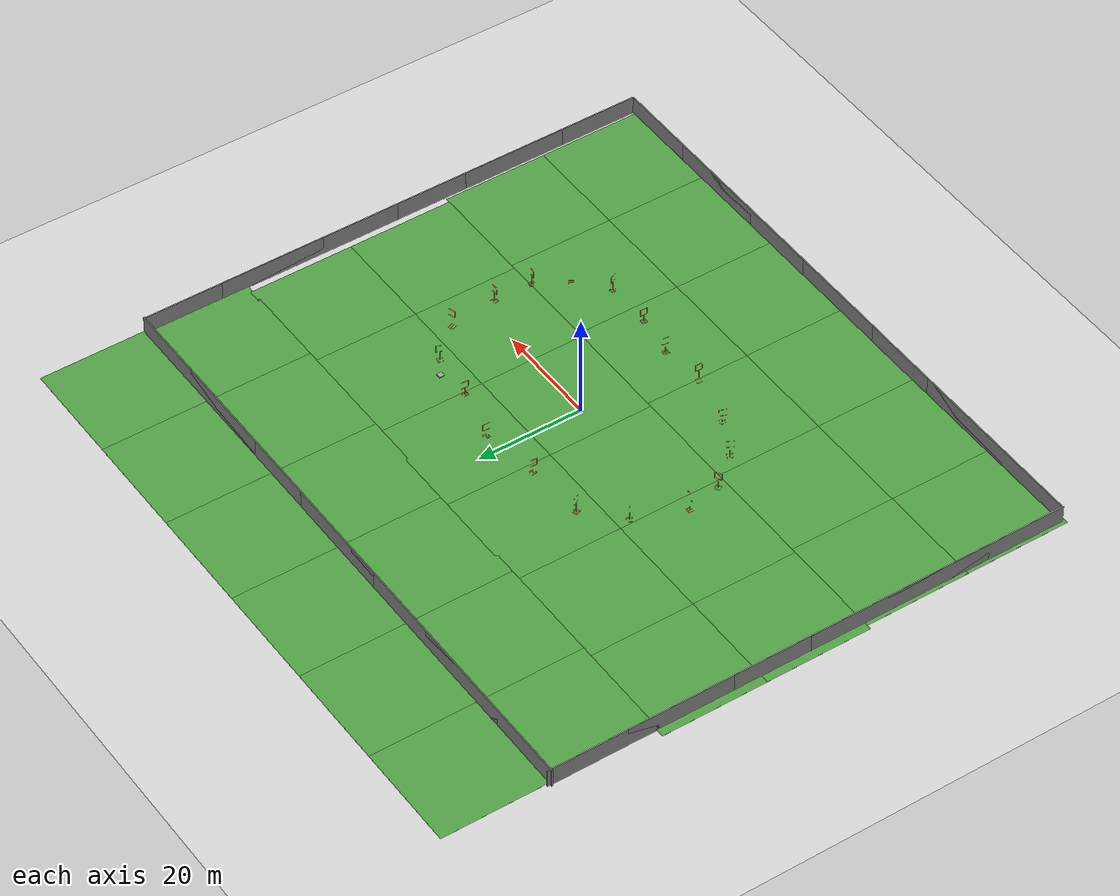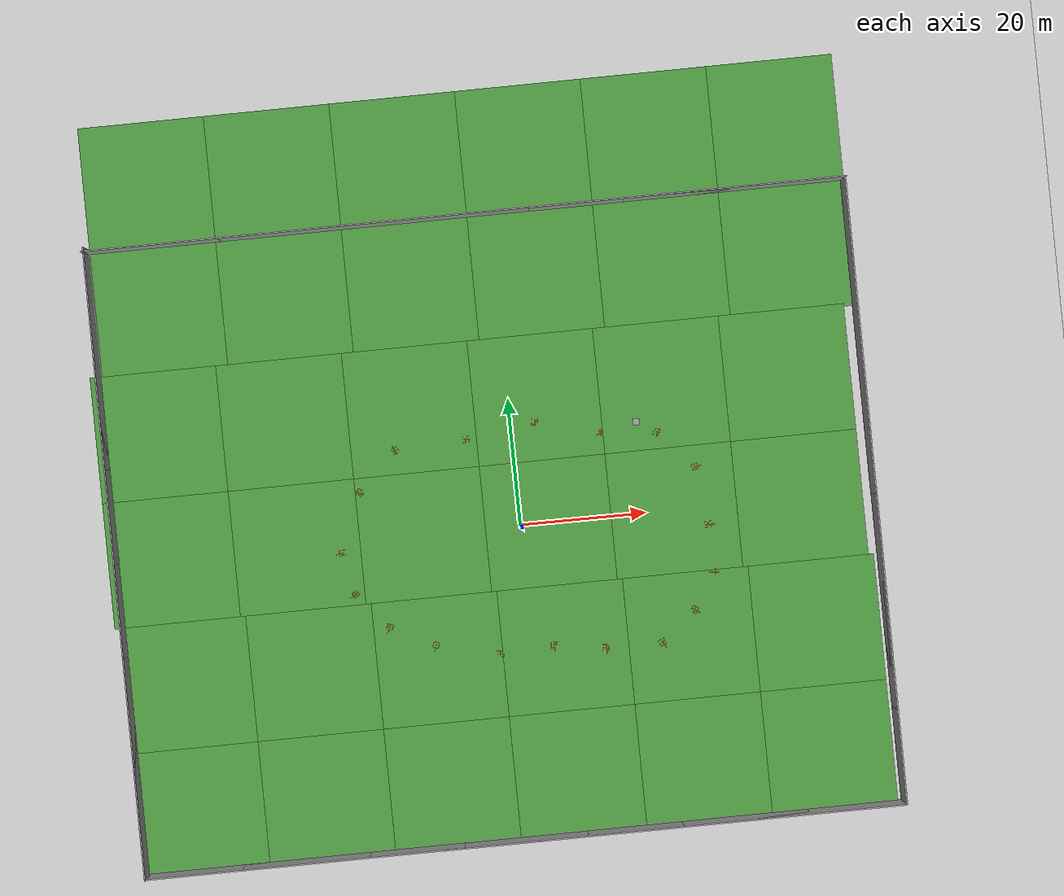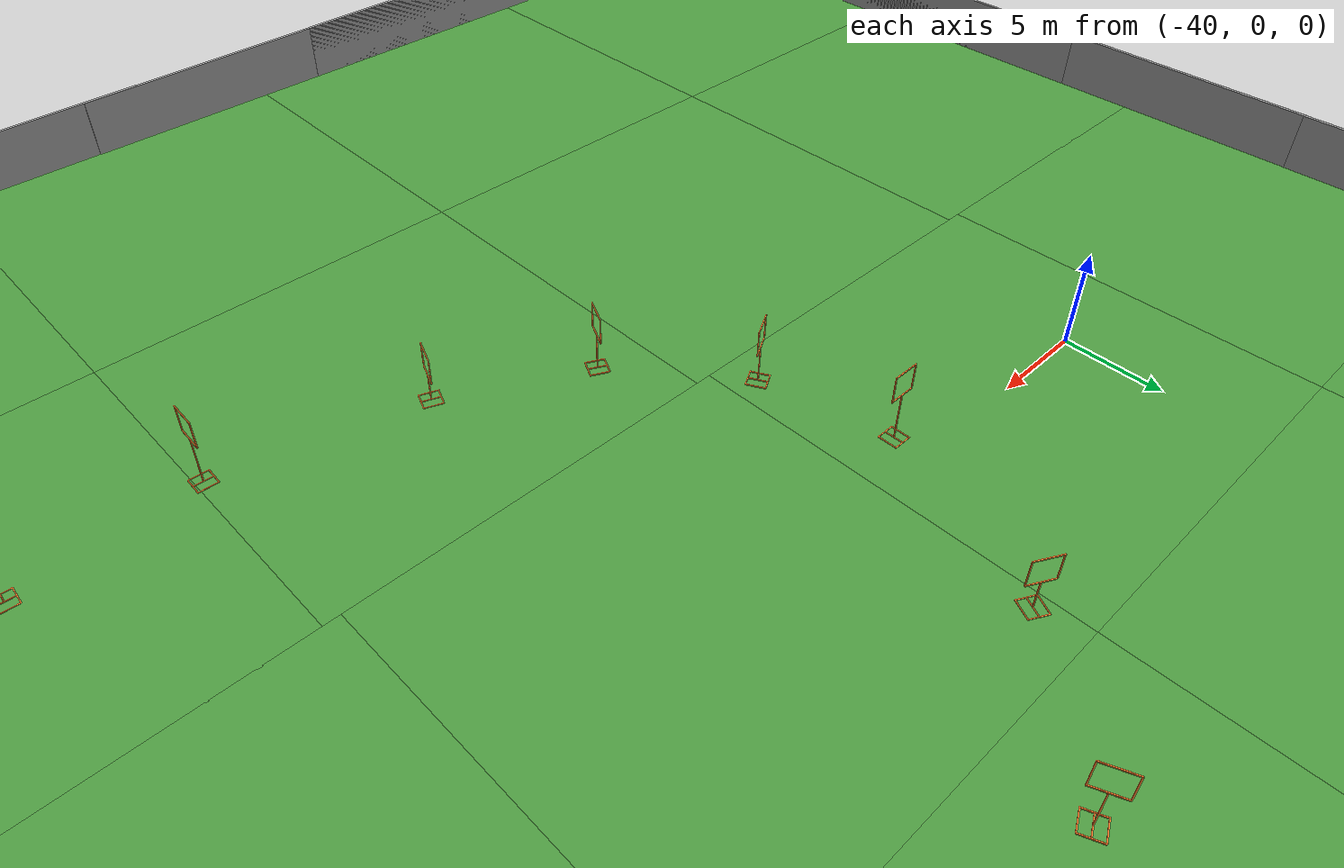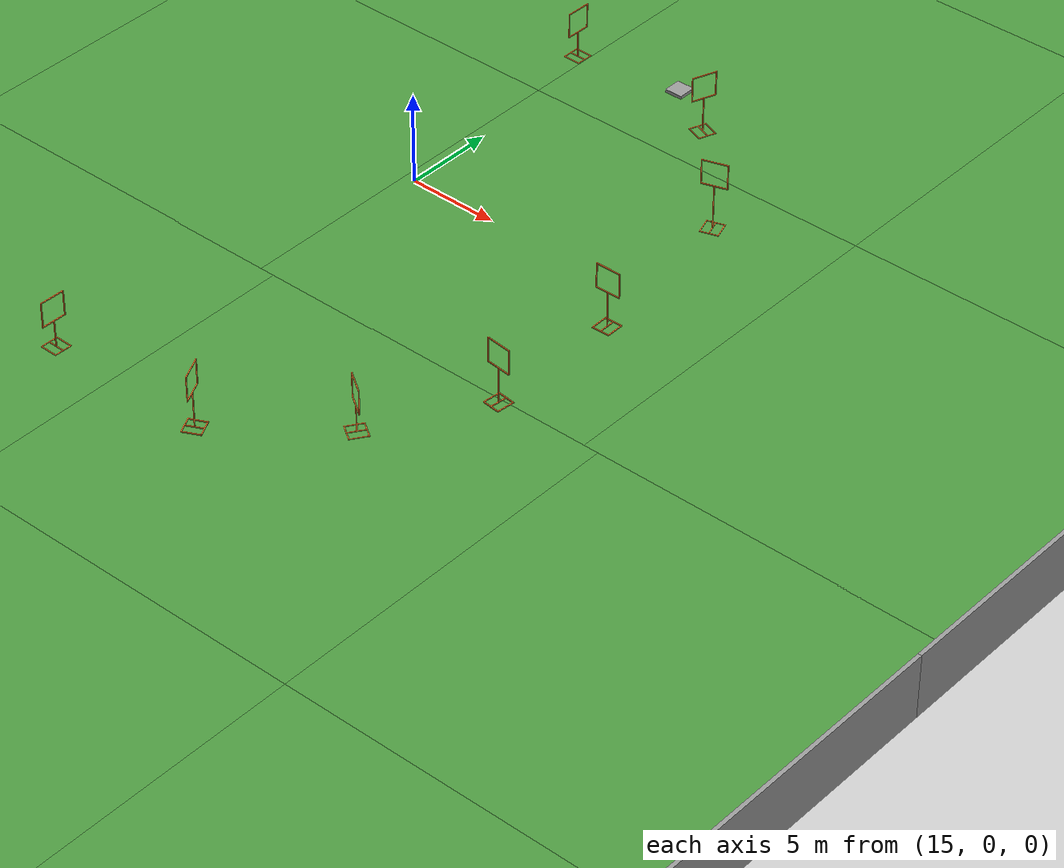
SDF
<sdf version="1.6">
 <world name="default">
  <plugin name="ros_interface_plugin" filename="librotors_gazebo_ros_interface_plugin.so"/>
  <light name="sun" type="directional">
   <pose>0 0 10 0 -0 0</pose>
   <diffuse>0.8 0.8 0.8 1</diffuse>
   <specular>0.2 0.2 0.2 1</specular>
   <attenuation>
    <range>1000</range>
    <constant>0.9</constant>
    <linear>0.01</linear>
    <quadratic>0.001</quadratic>
   </attenuation>
   <direction>-0.5 0.1 -0.9</direction>
  </light>
  <model name="ground_plane">
   <static>1</static>
   <link name="link">
    <collision name="collision">
     <geometry><plane><normal>0 0 1</normal><size>100 100</size></plane></geometry>
     <surface><friction><ode><mu>100</mu><mu2>50</mu2></ode></friction></surface>
    </collision>
    <visual name="visual">
     <cast_shadows>0</cast_shadows>
     <geometry><plane><normal>0 0 1</normal><size>100 100</size></plane></geometry>
     <material>
      <script><uri>file://media/materials/scripts/gazebo.material</uri><name>Gazebo/Grey</name></script>
     </material>
    </visual>
    <velocity_decay><linear>0</linear><angular>0</angular></velocity_decay>
   </link>
  </model>
  <physics name="default_physics" default="0" type="ode">
   <max_step_size>0.001</max_step_size>
   <real_time_factor>1</real_time_factor>
   <real_time_update_rate>1000</real_time_update_rate>
  </physics>
  <scene><ambient>0.4 0.4 0.4 1</ambient><background>0.7 0.7 0.7 1</background><shadows>1</shadows></scene>
  <gravity>0 0 -9.8</gravity>
  <magnetic_field>6e-06 2.3e-05 -4.2e-05</magnetic_field>
  <atmosphere type="adiabatic"/>
  <spherical_coordinates>
   <surface_model>EARTH_WGS84</surface_model>
   <latitude_deg>0</latitude_deg>
   <longitude_deg>0</longitude_deg>
   <elevation>0</elevation>
   <heading_deg>0</heading_deg>
  </spherical_coordinates>
  <model name="wall">
   <link name="link">
    <pose>0 0 1.4 0 -0 0</pose>
    <inertial>
     <mass>1</mass>
     <inertia><ixx>1</ixx><ixy>0</ixy><ixz>0</ixz><iyy>1</iyy><iyz>0</iyz><izz>1</izz></inertia>
    </inertial>
    <visual name="ModelPreview_1::link::visual_1">
     <cast_shadows>0</cast_shadows>
     <geometry><box><size>20 0.2 4</size></box></geometry>
     <material>
      <script>
       <uri>model://grey_wall/materials/scripts</uri>
       <uri>model://grey_wall/materials/textures</uri>
       <name>vrc/grey_wall</name>
      </script>
      <ambient>1 1 1 1</ambient>
      <diffuse>1 1 1 1</diffuse>
      <specular>0 0 0 1</specular>
      <emissive>0 0 0 1</emissive>
      <shader type="vertex"><normal_map>__default__</normal_map></shader>
     </material>
    </visual>
    <visual name="visual">
     <cast_shadows>0</cast_shadows>
     <geometry><box><size>50 0.2 4</size></box></geometry>
     <material>
      <script>
       <uri>model://grey_wall/materials/scripts</uri>
       <uri>model://grey_wall/materials/textures</uri>
       <name>vrc/grey_wall</name>
      </script>
      <ambient>1 1 1 1</ambient>
      <diffuse>1 1 1 1</diffuse>
      <specular>0 0 0 1</specular>
      <emissive>0 0 0 1</emissive>
      <shader type="vertex"><normal_map>__default__</normal_map></shader>
     </material>
    </visual>
    <collision name="collision">
     <geometry><box><size>50 0.2 4</size></box></geometry>
     <surface>
      <friction>
       <ode><mu>1</mu><mu2>1</mu2><fdir1>0 0 0</fdir1><slip1>0</slip1><slip2>0</slip2></ode>
       <torsional>
        <coefficient>1</coefficient>
        <patch_radius>0</patch_radius>
        <surface_radius>0</surface_radius>
        <use_patch_radius>1</use_patch_radius>
        <ode><slip>0</slip></ode>
       </torsional>
      </friction>
      <bounce><restitution_coefficient>0</restitution_coefficient><threshold>1e+06</threshold></bounce>
      <contact>
       <collide_without_contact>0</collide_without_contact>
       <collide_without_contact_bitmask>1</collide_without_contact_bitmask>
       <collide_bitmask>1</collide_bitmask>
       <ode>
        <soft_cfm>0</soft_cfm>
        <soft_erp>0.2</soft_erp>
        <kp>1e+13</kp>
        <kd>1</kd>
        <max_vel>0.01</max_vel>
        <min_depth>0</min_depth>
       </ode>
       <bullet>
        <split_impulse>1</split_impulse>
        <split_impulse_penetration_threshold>-0.01</split_impulse_penetration_threshold>
        <soft_cfm>0</soft_cfm>
        <soft_erp>0.2</soft_erp>
        <kp>1e+13</kp>
        <kd>1</kd>
       </bullet>
      </contact>
     </surface>
    </collision>
   </link>
   <static>1</static>
   <pose>8.13717 -49.3717 0 0 -0 0</pose>
  </model>
  <model name="wall_clone">
   <link name="link">
    <pose>0 0 1.4 0 -0 0</pose>
    <inertial>
     <mass>1</mass>
     <inertia><ixx>1</ixx><ixy>0</ixy><ixz>0</ixz><iyy>1</iyy><iyz>0</iyz><izz>1</izz></inertia>
    </inertial>
    <visual name="ModelPreview_1::link::visual_1">
     <cast_shadows>0</cast_shadows>
     <geometry><box><size>20 0.2 4</size></box></geometry>
     <material>
      <script>
       <uri>model://grey_wall/materials/scripts</uri>
       <uri>model://grey_wall/materials/textures</uri>
       <name>vrc/grey_wall</name>
      </script>
      <ambient>1 1 1 1</ambient>
      <diffuse>1 1 1 1</diffuse>
      <specular>0 0 0 1</specular>
      <emissive>0 0 0 1</emissive>
      <shader type="vertex"><normal_map>__default__</normal_map></shader>
     </material>
    </visual>
    <visual name="visual">
     <cast_shadows>0</cast_shadows>
     <geometry><box><size>50 0.2 4</size></box></geometry>
     <material>
      <script>
       <uri>model://grey_wall/materials/scripts</uri>
       <uri>model://grey_wall/materials/textures</uri>
       <name>vrc/grey_wall</name>
      </script>
      <ambient>1 1 1 1</ambient>
      <diffuse>1 1 1 1</diffuse>
      <specular>0 0 0 1</specular>
      <emissive>0 0 0 1</emissive>
      <shader type="vertex"><normal_map>__default__</normal_map></shader>
     </material>
    </visual>
    <collision name="collision">
     <geometry><box><size>50 0.2 4</size></box></geometry>
     <surface>
      <friction>
       <ode><mu>1</mu><mu2>1</mu2><fdir1>0 0 0</fdir1><slip1>0</slip1><slip2>0</slip2></ode>
       <torsional>
        <coefficient>1</coefficient>
        <patch_radius>0</patch_radius>
        <surface_radius>0</surface_radius>
        <use_patch_radius>1</use_patch_radius>
        <ode><slip>0</slip></ode>
       </torsional>
      </friction>
      <bounce><restitution_coefficient>0</restitution_coefficient><threshold>1e+06</threshold></bounce>
      <contact>
       <collide_without_contact>0</collide_without_contact>
       <collide_without_contact_bitmask>1</collide_without_contact_bitmask>
       <collide_bitmask>1</collide_bitmask>
       <ode>
        <soft_cfm>0</soft_cfm>
        <soft_erp>0.2</soft_erp>
        <kp>1e+13</kp>
        <kd>1</kd>
        <max_vel>0.01</max_vel>
        <min_depth>0</min_depth>
       </ode>
       <bullet>
        <split_impulse>1</split_impulse>
        <split_impulse_penetration_threshold>-0.01</split_impulse_penetration_threshold>
        <soft_cfm>0</soft_cfm>
        <soft_erp>0.2</soft_erp>
        <kp>1e+13</kp>
        <kd>1</kd>
       </bullet>
      </contact>
     </surface>
    </collision>
   </link>
   <static>1</static>
   <pose>-38.6602 -49.3294 0 0 -0 0</pose>
  </model>
  <model name="wall_clone_0">
   <link name="link">
    <pose>0 0 1.4 0 -0 0</pose>
    <inertial>
     <mass>1</mass>
     <inertia><ixx>1</ixx><ixy>0</ixy><ixz>0</ixz><iyy>1</iyy><iyz>0</iyz><izz>1</izz></inertia>
    </inertial>
    <visual name="ModelPreview_1::link::visual_1">
     <cast_shadows>0</cast_shadows>
     <geometry><box><size>20 0.2 4</size></box></geometry>
     <material>
      <script>
       <uri>model://grey_wall/materials/scripts</uri>
       <uri>model://grey_wall/materials/textures</uri>
       <name>vrc/grey_wall</name>
      </script>
      <ambient>1 1 1 1</ambient>
      <diffuse>1 1 1 1</diffuse>
      <specular>0 0 0 1</specular>
      <emissive>0 0 0 1</emissive>
      <shader type="vertex"><normal_map>__default__</normal_map></shader>
     </material>
    </visual>
    <visual name="visual">
     <cast_shadows>0</cast_shadows>
     <geometry><box><size>50 0.2 4</size></box></geometry>
     <material>
      <script>
       <uri>model://grey_wall/materials/scripts</uri>
       <uri>model://grey_wall/materials/textures</uri>
       <name>vrc/grey_wall</name>
      </script>
      <ambient>1 1 1 1</ambient>
      <diffuse>1 1 1 1</diffuse>
      <specular>0 0 0 1</specular>
      <emissive>0 0 0 1</emissive>
      <shader type="vertex"><normal_map>__default__</normal_map></shader>
     </material>
    </visual>
    <collision name="collision">
     <geometry><box><size>50 0.2 4</size></box></geometry>
     <surface>
      <friction>
       <ode><mu>1</mu><mu2>1</mu2><fdir1>0 0 0</fdir1><slip1>0</slip1><slip2>0</slip2></ode>
       <torsional>
        <coefficient>1</coefficient>
        <patch_radius>0</patch_radius>
        <surface_radius>0</surface_radius>
        <use_patch_radius>1</use_patch_radius>
        <ode><slip>0</slip></ode>
       </torsional>
      </friction>
      <bounce><restitution_coefficient>0</restitution_coefficient><threshold>1e+06</threshold></bounce>
      <contact>
       <collide_without_contact>0</collide_without_contact>
       <collide_without_contact_bitmask>1</collide_without_contact_bitmask>
       <collide_bitmask>1</collide_bitmask>
       <ode>
        <soft_cfm>0</soft_cfm>
        <soft_erp>0.2</soft_erp>
        <kp>1e+13</kp>
        <kd>1</kd>
        <max_vel>0.01</max_vel>
        <min_depth>0</min_depth>
       </ode>
       <bullet>
        <split_impulse>1</split_impulse>
        <split_impulse_penetration_threshold>-0.01</split_impulse_penetration_threshold>
        <soft_cfm>0</soft_cfm>
        <soft_erp>0.2</soft_erp>
        <kp>1e+13</kp>
        <kd>1</kd>
       </bullet>
      </contact>
     </surface>
    </collision>
   </link>
   <static>1</static>
   <pose>30.7671 -49.3607 0 0 -0 0</pose>
  </model>
  <model name="wall_clone_0_clone">
   <link name="link">
    <pose>0 0 1.4 0 -0 0</pose>
    <inertial>
     <mass>1</mass>
     <inertia><ixx>1</ixx><ixy>0</ixy><ixz>0</ixz><iyy>1</iyy><iyz>0</iyz><izz>1</izz></inertia>
    </inertial>
    <visual name="ModelPreview_1::link::visual_1">
     <cast_shadows>0</cast_shadows>
     <geometry><box><size>20 0.2 4</size></box></geometry>
     <material>
      <script>
       <uri>model://grey_wall/materials/scripts</uri>
       <uri>model://grey_wall/materials/textures</uri>
       <name>vrc/grey_wall</name>
      </script>
      <ambient>1 1 1 1</ambient>
      <diffuse>1 1 1 1</diffuse>
      <specular>0 0 0 1</specular>
      <emissive>0 0 0 1</emissive>
      <shader type="vertex"><normal_map>__default__</normal_map></shader>
     </material>
    </visual>
    <visual name="visual">
     <cast_shadows>0</cast_shadows>
     <geometry><box><size>50 0.2 4</size></box></geometry>
     <material>
      <script>
       <uri>model://grey_wall/materials/scripts</uri>
       <uri>model://grey_wall/materials/textures</uri>
       <name>vrc/grey_wall</name>
      </script>
      <ambient>1 1 1 1</ambient>
      <diffuse>1 1 1 1</diffuse>
      <specular>0 0 0 1</specular>
      <emissive>0 0 0 1</emissive>
      <shader type="vertex"><normal_map>__default__</normal_map></shader>
     </material>
    </visual>
    <collision name="collision">
     <geometry><box><size>50 0.2 4</size></box></geometry>
     <surface>
      <friction>
       <ode><mu>1</mu><mu2>1</mu2><fdir1>0 0 0</fdir1><slip1>0</slip1><slip2>0</slip2></ode>
       <torsional>
        <coefficient>1</coefficient>
        <patch_radius>0</patch_radius>
        <surface_radius>0</surface_radius>
        <use_patch_radius>1</use_patch_radius>
        <ode><slip>0</slip></ode>
       </torsional>
      </friction>
      <bounce><restitution_coefficient>0</restitution_coefficient><threshold>1e+06</threshold></bounce>
      <contact>
       <collide_without_contact>0</collide_without_contact>
       <collide_without_contact_bitmask>1</collide_without_contact_bitmask>
       <collide_bitmask>1</collide_bitmask>
       <ode>
        <soft_cfm>0</soft_cfm>
        <soft_erp>0.2</soft_erp>
        <kp>1e+13</kp>
        <kd>1</kd>
        <max_vel>0.01</max_vel>
        <min_depth>0</min_depth>
       </ode>
       <bullet>
        <split_impulse>1</split_impulse>
        <split_impulse_penetration_threshold>-0.01</split_impulse_penetration_threshold>
        <soft_cfm>0</soft_cfm>
        <soft_erp>0.2</soft_erp>
        <kp>1e+13</kp>
        <kd>1</kd>
       </bullet>
      </contact>
     </surface>
    </collision>
   </link>
   <static>1</static>
   <pose>55.8293 -24.385 0 0 -0 1.57</pose>
  </model>
  <model name="wall_clone_0_clone_clone">
   <link name="link">
    <pose>0 0 1.4 0 -0 0</pose>
    <inertial>
     <mass>1</mass>
     <inertia><ixx>1</ixx><ixy>0</ixy><ixz>0</ixz><iyy>1</iyy><iyz>0</iyz><izz>1</izz></inertia>
    </inertial>
    <visual name="ModelPreview_1::link::visual_1">
     <cast_shadows>0</cast_shadows>
     <geometry><box><size>20 0.2 4</size></box></geometry>
     <material>
      <script>
       <uri>model://grey_wall/materials/scripts</uri>
       <uri>model://grey_wall/materials/textures</uri>
       <name>vrc/grey_wall</name>
      </script>
      <ambient>1 1 1 1</ambient>
      <diffuse>1 1 1 1</diffuse>
      <specular>0 0 0 1</specular>
      <emissive>0 0 0 1</emissive>
      <shader type="vertex"><normal_map>__default__</normal_map></shader>
     </material>
    </visual>
    <visual name="visual">
     <cast_shadows>0</cast_shadows>
     <geometry><box><size>50 0.2 4</size></box></geometry>
     <material>
      <script>
       <uri>model://grey_wall/materials/scripts</uri>
       <uri>model://grey_wall/materials/textures</uri>
       <name>vrc/grey_wall</name>
      </script>
      <ambient>1 1 1 1</ambient>
      <diffuse>1 1 1 1</diffuse>
      <specular>0 0 0 1</specular>
      <emissive>0 0 0 1</emissive>
      <shader type="vertex"><normal_map>__default__</normal_map></shader>
     </material>
    </visual>
    <collision name="collision">
     <geometry><box><size>50 0.2 4</size></box></geometry>
     <surface>
      <friction>
       <ode><mu>1</mu><mu2>1</mu2><fdir1>0 0 0</fdir1><slip1>0</slip1><slip2>0</slip2></ode>
       <torsional>
        <coefficient>1</coefficient>
        <patch_radius>0</patch_radius>
        <surface_radius>0</surface_radius>
        <use_patch_radius>1</use_patch_radius>
        <ode><slip>0</slip></ode>
       </torsional>
      </friction>
      <bounce><restitution_coefficient>0</restitution_coefficient><threshold>1e+06</threshold></bounce>
      <contact>
       <collide_without_contact>0</collide_without_contact>
       <collide_without_contact_bitmask>1</collide_without_contact_bitmask>
       <collide_bitmask>1</collide_bitmask>
       <ode>
        <soft_cfm>0</soft_cfm>
        <soft_erp>0.2</soft_erp>
        <kp>1e+13</kp>
        <kd>1</kd>
        <max_vel>0.01</max_vel>
        <min_depth>0</min_depth>
       </ode>
       <bullet>
        <split_impulse>1</split_impulse>
        <split_impulse_penetration_threshold>-0.01</split_impulse_penetration_threshold>
        <soft_cfm>0</soft_cfm>
        <soft_erp>0.2</soft_erp>
        <kp>1e+13</kp>
        <kd>1</kd>
       </bullet>
      </contact>
     </surface>
    </collision>
   </link>
   <static>1</static>
   <pose>55.8454 24.5096 0 0 -0 1.57</pose>
  </model>
  <model name="wall_clone_0_clone_clone_0">
   <link name="link">
    <pose>0 0 1.4 0 -0 0</pose>
    <inertial>
     <mass>1</mass>
     <inertia><ixx>1</ixx><ixy>0</ixy><ixz>0</ixz><iyy>1</iyy><iyz>0</iyz><izz>1</izz></inertia>
    </inertial>
    <visual name="ModelPreview_1::link::visual_1">
     <cast_shadows>0</cast_shadows>
     <geometry><box><size>20 0.2 4</size></box></geometry>
     <material>
      <script>
       <uri>model://grey_wall/materials/scripts</uri>
       <uri>model://grey_wall/materials/textures</uri>
       <name>vrc/grey_wall</name>
      </script>
      <ambient>1 1 1 1</ambient>
      <diffuse>1 1 1 1</diffuse>
      <specular>0 0 0 1</specular>
      <emissive>0 0 0 1</emissive>
      <shader type="vertex"><normal_map>__default__</normal_map></shader>
     </material>
    </visual>
    <visual name="visual">
     <cast_shadows>0</cast_shadows>
     <geometry><box><size>50 0.2 4</size></box></geometry>
     <material>
      <script>
       <uri>model://grey_wall/materials/scripts</uri>
       <uri>model://grey_wall/materials/textures</uri>
       <name>vrc/grey_wall</name>
      </script>
      <ambient>1 1 1 1</ambient>
      <diffuse>1 1 1 1</diffuse>
      <specular>0 0 0 1</specular>
      <emissive>0 0 0 1</emissive>
      <shader type="vertex"><normal_map>__default__</normal_map></shader>
     </material>
    </visual>
    <collision name="collision">
     <geometry><box><size>50 0.2 4</size></box></geometry>
     <surface>
      <friction>
       <ode><mu>1</mu><mu2>1</mu2><fdir1>0 0 0</fdir1><slip1>0</slip1><slip2>0</slip2></ode>
       <torsional>
        <coefficient>1</coefficient>
        <patch_radius>0</patch_radius>
        <surface_radius>0</surface_radius>
        <use_patch_radius>1</use_patch_radius>
        <ode><slip>0</slip></ode>
       </torsional>
      </friction>
      <bounce><restitution_coefficient>0</restitution_coefficient><threshold>1e+06</threshold></bounce>
      <contact>
       <collide_without_contact>0</collide_without_contact>
       <collide_without_contact_bitmask>1</collide_without_contact_bitmask>
       <collide_bitmask>1</collide_bitmask>
       <ode>
        <soft_cfm>0</soft_cfm>
        <soft_erp>0.2</soft_erp>
        <kp>1e+13</kp>
        <kd>1</kd>
        <max_vel>0.01</max_vel>
        <min_depth>0</min_depth>
       </ode>
       <bullet>
        <split_impulse>1</split_impulse>
        <split_impulse_penetration_threshold>-0.01</split_impulse_penetration_threshold>
        <soft_cfm>0</soft_cfm>
        <soft_erp>0.2</soft_erp>
        <kp>1e+13</kp>
        <kd>1</kd>
       </bullet>
      </contact>
     </surface>
    </collision>
   </link>
   <static>1</static>
   <pose>-64.0349 -24.5483 0 0 -0 1.57</pose>
  </model>
  <model name="wall_clone_0_clone_clone_1">
   <link name="link">
    <pose>0 0 1.4 0 -0 0</pose>
    <inertial>
     <mass>1</mass>
     <inertia><ixx>1</ixx><ixy>0</ixy><ixz>0</ixz><iyy>1</iyy><iyz>0</iyz><izz>1</izz></inertia>
    </inertial>
    <visual name="ModelPreview_1::link::visual_1">
     <cast_shadows>0</cast_shadows>
     <geometry><box><size>20 0.2 4</size></box></geometry>
     <material>
      <script>
       <uri>model://grey_wall/materials/scripts</uri>
       <uri>model://grey_wall/materials/textures</uri>
       <name>vrc/grey_wall</name>
      </script>
      <ambient>1 1 1 1</ambient>
      <diffuse>1 1 1 1</diffuse>
      <specular>0 0 0 1</specular>
      <emissive>0 0 0 1</emissive>
      <shader type="vertex"><normal_map>__default__</normal_map></shader>
     </material>
    </visual>
    <visual name="visual">
     <cast_shadows>0</cast_shadows>
     <geometry><box><size>50 0.2 4</size></box></geometry>
     <material>
      <script>
       <uri>model://grey_wall/materials/scripts</uri>
       <uri>model://grey_wall/materials/textures</uri>
       <name>vrc/grey_wall</name>
      </script>
      <ambient>1 1 1 1</ambient>
      <diffuse>1 1 1 1</diffuse>
      <specular>0 0 0 1</specular>
      <emissive>0 0 0 1</emissive>
      <shader type="vertex"><normal_map>__default__</normal_map></shader>
     </material>
    </visual>
    <collision name="collision">
     <geometry><box><size>50 0.2 4</size></box></geometry>
     <surface>
      <friction>
       <ode><mu>1</mu><mu2>1</mu2><fdir1>0 0 0</fdir1><slip1>0</slip1><slip2>0</slip2></ode>
       <torsional>
        <coefficient>1</coefficient>
        <patch_radius>0</patch_radius>
        <surface_radius>0</surface_radius>
        <use_patch_radius>1</use_patch_radius>
        <ode><slip>0</slip></ode>
       </torsional>
      </friction>
      <bounce><restitution_coefficient>0</restitution_coefficient><threshold>1e+06</threshold></bounce>
      <contact>
       <collide_without_contact>0</collide_without_contact>
       <collide_without_contact_bitmask>1</collide_without_contact_bitmask>
       <collide_bitmask>1</collide_bitmask>
       <ode>
        <soft_cfm>0</soft_cfm>
        <soft_erp>0.2</soft_erp>
        <kp>1e+13</kp>
        <kd>1</kd>
        <max_vel>0.01</max_vel>
        <min_depth>0</min_depth>
       </ode>
       <bullet>
        <split_impulse>1</split_impulse>
        <split_impulse_penetration_threshold>-0.01</split_impulse_penetration_threshold>
        <soft_cfm>0</soft_cfm>
        <soft_erp>0.2</soft_erp>
        <kp>1e+13</kp>
        <kd>1</kd>
       </bullet>
      </contact>
     </surface>
    </collision>
   </link>
   <static>1</static>
   <pose>-63.9681 25.189 0 0 -0 1.57</pose>
  </model>
  <model name="wall_clone_0_clone_0">
   <link name="link">
    <pose>0 0 1.4 0 -0 0</pose>
    <inertial>
     <mass>1</mass>
     <inertia><ixx>1</ixx><ixy>0</ixy><ixz>0</ixz><iyy>1</iyy><iyz>0</iyz><izz>1</izz></inertia>
    </inertial>
    <visual name="ModelPreview_1::link::visual_1">
     <cast_shadows>0</cast_shadows>
     <geometry><box><size>20 0.2 4</size></box></geometry>
     <material>
      <script>
       <uri>model://grey_wall/materials/scripts</uri>
       <uri>model://grey_wall/materials/textures</uri>
       <name>vrc/grey_wall</name>
      </script>
      <ambient>1 1 1 1</ambient>
      <diffuse>1 1 1 1</diffuse>
      <specular>0 0 0 1</specular>
      <emissive>0 0 0 1</emissive>
      <shader type="vertex"><normal_map>__default__</normal_map></shader>
     </material>
    </visual>
    <visual name="visual">
     <cast_shadows>0</cast_shadows>
     <geometry><box><size>50 0.2 4</size></box></geometry>
     <material>
      <script>
       <uri>model://grey_wall/materials/scripts</uri>
       <uri>model://grey_wall/materials/textures</uri>
       <name>vrc/grey_wall</name>
      </script>
      <ambient>1 1 1 1</ambient>
      <diffuse>1 1 1 1</diffuse>
      <specular>0 0 0 1</specular>
      <emissive>0 0 0 1</emissive>
      <shader type="vertex"><normal_map>__default__</normal_map></shader>
     </material>
    </visual>
    <collision name="collision">
     <geometry><box><size>50 0.2 4</size></box></geometry>
     <surface>
      <friction>
       <ode><mu>1</mu><mu2>1</mu2><fdir1>0 0 0</fdir1><slip1>0</slip1><slip2>0</slip2></ode>
       <torsional>
        <coefficient>1</coefficient>
        <patch_radius>0</patch_radius>
        <surface_radius>0</surface_radius>
        <use_patch_radius>1</use_patch_radius>
        <ode><slip>0</slip></ode>
       </torsional>
      </friction>
      <bounce><restitution_coefficient>0</restitution_coefficient><threshold>1e+06</threshold></bounce>
      <contact>
       <collide_without_contact>0</collide_without_contact>
       <collide_without_contact_bitmask>1</collide_without_contact_bitmask>
       <collide_bitmask>1</collide_bitmask>
       <ode>
        <soft_cfm>0</soft_cfm>
        <soft_erp>0.2</soft_erp>
        <kp>1e+13</kp>
        <kd>1</kd>
        <max_vel>0.01</max_vel>
        <min_depth>0</min_depth>
       </ode>
       <bullet>
        <split_impulse>1</split_impulse>
        <split_impulse_penetration_threshold>-0.01</split_impulse_penetration_threshold>
        <soft_cfm>0</soft_cfm>
        <soft_erp>0.2</soft_erp>
        <kp>1e+13</kp>
        <kd>1</kd>
       </bullet>
      </contact>
     </surface>
    </collision>
   </link>
   <static>1</static>
   <pose>31.1336 49.4754 0 0 -0 0</pose>
  </model>
  <model name="wall_clone_0_clone_1">
   <link name="link">
    <pose>0 0 1.4 0 -0 0</pose>
    <inertial>
     <mass>1</mass>
     <inertia><ixx>1</ixx><ixy>0</ixy><ixz>0</ixz><iyy>1</iyy><iyz>0</iyz><izz>1</izz></inertia>
    </inertial>
    <visual name="ModelPreview_1::link::visual_1">
     <cast_shadows>0</cast_shadows>
     <geometry><box><size>20 0.2 4</size></box></geometry>
     <material>
      <script>
       <uri>model://grey_wall/materials/scripts</uri>
       <uri>model://grey_wall/materials/textures</uri>
       <name>vrc/grey_wall</name>
      </script>
      <ambient>1 1 1 1</ambient>
      <diffuse>1 1 1 1</diffuse>
      <specular>0 0 0 1</specular>
      <emissive>0 0 0 1</emissive>
      <shader type="vertex"><normal_map>__default__</normal_map></shader>
     </material>
    </visual>
    <visual name="visual">
     <cast_shadows>0</cast_shadows>
     <geometry><box><size>50 0.2 4</size></box></geometry>
     <material>
      <script>
       <uri>model://grey_wall/materials/scripts</uri>
       <uri>model://grey_wall/materials/textures</uri>
       <name>vrc/grey_wall</name>
      </script>
      <ambient>1 1 1 1</ambient>
      <diffuse>1 1 1 1</diffuse>
      <specular>0 0 0 1</specular>
      <emissive>0 0 0 1</emissive>
      <shader type="vertex"><normal_map>__default__</normal_map></shader>
     </material>
    </visual>
    <collision name="collision">
     <geometry><box><size>50 0.2 4</size></box></geometry>
     <surface>
      <friction>
       <ode><mu>1</mu><mu2>1</mu2><fdir1>0 0 0</fdir1><slip1>0</slip1><slip2>0</slip2></ode>
       <torsional>
        <coefficient>1</coefficient>
        <patch_radius>0</patch_radius>
        <surface_radius>0</surface_radius>
        <use_patch_radius>1</use_patch_radius>
        <ode><slip>0</slip></ode>
       </torsional>
      </friction>
      <bounce><restitution_coefficient>0</restitution_coefficient><threshold>1e+06</threshold></bounce>
      <contact>
       <collide_without_contact>0</collide_without_contact>
       <collide_without_contact_bitmask>1</collide_without_contact_bitmask>
       <collide_bitmask>1</collide_bitmask>
       <ode>
        <soft_cfm>0</soft_cfm>
        <soft_erp>0.2</soft_erp>
        <kp>1e+13</kp>
        <kd>1</kd>
        <max_vel>0.01</max_vel>
        <min_depth>0</min_depth>
       </ode>
       <bullet>
        <split_impulse>1</split_impulse>
        <split_impulse_penetration_threshold>-0.01</split_impulse_penetration_threshold>
        <soft_cfm>0</soft_cfm>
        <soft_erp>0.2</soft_erp>
        <kp>1e+13</kp>
        <kd>1</kd>
       </bullet>
      </contact>
     </surface>
    </collision>
   </link>
   <static>1</static>
   <pose>-17.7944 49.5119 0 0 -0 0</pose>
  </model>
  <model name="wall_clone_0_clone_2">
   <link name="link">
    <pose>0 0 1.4 0 -0 0</pose>
    <inertial>
     <mass>1</mass>
     <inertia><ixx>1</ixx><ixy>0</ixy><ixz>0</ixz><iyy>1</iyy><iyz>0</iyz><izz>1</izz></inertia>
    </inertial>
    <visual name="ModelPreview_1::link::visual_1">
     <cast_shadows>0</cast_shadows>
     <geometry><box><size>20 0.2 4</size></box></geometry>
     <material>
      <script>
       <uri>model://grey_wall/materials/scripts</uri>
       <uri>model://grey_wall/materials/textures</uri>
       <name>vrc/grey_wall</name>
      </script>
      <ambient>1 1 1 1</ambient>
      <diffuse>1 1 1 1</diffuse>
      <specular>0 0 0 1</specular>
      <emissive>0 0 0 1</emissive>
      <shader type="vertex"><normal_map>__default__</normal_map></shader>
     </material>
    </visual>
    <visual name="visual">
     <cast_shadows>0</cast_shadows>
     <geometry><box><size>50 0.2 4</size></box></geometry>
     <material>
      <script>
       <uri>model://grey_wall/materials/scripts</uri>
       <uri>model://grey_wall/materials/textures</uri>
       <name>vrc/grey_wall</name>
      </script>
      <ambient>1 1 1 1</ambient>
      <diffuse>1 1 1 1</diffuse>
      <specular>0 0 0 1</specular>
      <emissive>0 0 0 1</emissive>
      <shader type="vertex"><normal_map>__default__</normal_map></shader>
     </material>
    </visual>
    <collision name="collision">
     <geometry><box><size>50 0.2 4</size></box></geometry>
     <surface>
      <friction>
       <ode><mu>1</mu><mu2>1</mu2><fdir1>0 0 0</fdir1><slip1>0</slip1><slip2>0</slip2></ode>
       <torsional>
        <coefficient>1</coefficient>
        <patch_radius>0</patch_radius>
        <surface_radius>0</surface_radius>
        <use_patch_radius>1</use_patch_radius>
        <ode><slip>0</slip></ode>
       </torsional>
      </friction>
      <bounce><restitution_coefficient>0</restitution_coefficient><threshold>1e+06</threshold></bounce>
      <contact>
       <collide_without_contact>0</collide_without_contact>
       <collide_without_contact_bitmask>1</collide_without_contact_bitmask>
       <collide_bitmask>1</collide_bitmask>
       <ode>
        <soft_cfm>0</soft_cfm>
        <soft_erp>0.2</soft_erp>
        <kp>1e+13</kp>
        <kd>1</kd>
        <max_vel>0.01</max_vel>
        <min_depth>0</min_depth>
       </ode>
       <bullet>
        <split_impulse>1</split_impulse>
        <split_impulse_penetration_threshold>-0.01</split_impulse_penetration_threshold>
        <soft_cfm>0</soft_cfm>
        <soft_erp>0.2</soft_erp>
        <kp>1e+13</kp>
        <kd>1</kd>
       </bullet>
      </contact>
     </surface>
    </collision>
   </link>
   <static>1</static>
   <pose>-39.3747 49.5174 0 0 -0 0</pose>
  </model>
  <model name="adr2017_Small_Gate">
   <link name="link">
    <pose>0 0 0.75 0 -0 0</pose>
    <inertial>
     <mass>1</mass>
     <inertia>
      <ixx>0.166667</ixx>
      <ixy>0</ixy>
      <ixz>0</ixz>
      <iyy>0.166667</iyy>
      <iyz>0</iyz>
      <izz>0.166667</izz>
     </inertia>
    </inertial>
    <visual name="visual">
     <geometry><box><size>0.05 0.05 1.5</size></box></geometry>
     <material>
      <script><name>Gazebo/Grey</name><uri>file://media/materials/scripts/gazebo.material</uri></script>
      <shader type="vertex"><normal_map>__default__</normal_map></shader>
      <ambient>0.976 0.484 0.164 1</ambient>
      <diffuse>0.976 0.484 0.164 1</diffuse>
      <specular>0.01 0.01 0.01 1</specular>
      <emissive>0 0 0 1</emissive>
     </material>
    </visual>
    <collision name="collision">
     <geometry><box><size>0.05 0.05 1.5</size></box></geometry>
     <surface>
      <friction>
       <ode><mu>1</mu><mu2>1</mu2><fdir1>0 0 0</fdir1><slip1>0</slip1><slip2>0</slip2></ode>
       <torsional>
        <coefficient>1</coefficient>
        <patch_radius>0</patch_radius>
        <surface_radius>0</surface_radius>
        <use_patch_radius>1</use_patch_radius>
        <ode><slip>0</slip></ode>
       </torsional>
      </friction>
      <bounce><restitution_coefficient>0</restitution_coefficient><threshold>1e+06</threshold></bounce>
      <contact>
       <collide_without_contact>0</collide_without_contact>
       <collide_without_contact_bitmask>1</collide_without_contact_bitmask>
       <collide_bitmask>1</collide_bitmask>
       <ode>
        <soft_cfm>0</soft_cfm>
        <soft_erp>0.2</soft_erp>
        <kp>1e+13</kp>
        <kd>1</kd>
        <max_vel>0.01</max_vel>
        <min_depth>0</min_depth>
       </ode>
       <bullet>
        <split_impulse>1</split_impulse>
        <split_impulse_penetration_threshold>-0.01</split_impulse_penetration_threshold>
        <soft_cfm>0</soft_cfm>
        <soft_erp>0.2</soft_erp>
        <kp>1e+13</kp>
        <kd>1</kd>
       </bullet>
      </contact>
     </surface>
    </collision>
   </link>
   <link name="link_2">
    <pose>0 0 0.025 0 -0 0</pose>
    <inertial>
     <mass>1</mass>
     <inertia>
      <ixx>0.166667</ixx>
      <ixy>0</ixy>
      <ixz>0</ixz>
      <iyy>0.166667</iyy>
      <iyz>0</iyz>
      <izz>0.166667</izz>
     </inertia>
    </inertial>
    <visual name="visual">
     <geometry><box><size>0.05 1 0.05</size></box></geometry>
     <material>
      <script><name>Gazebo/Grey</name><uri>file://media/materials/scripts/gazebo.material</uri></script>
      <shader type="vertex"><normal_map>__default__</normal_map></shader>
      <ambient>0.976 0.484 0.164 1</ambient>
      <diffuse>0.976 0.484 0.164 1</diffuse>
      <specular>0.01 0.01 0.01 1</specular>
      <emissive>0 0 0 1</emissive>
     </material>
    </visual>
    <collision name="collision">
     <geometry><box><size>0.05 1 0.05</size></box></geometry>
     <surface>
      <friction>
       <ode><mu>1</mu><mu2>1</mu2><fdir1>0 0 0</fdir1><slip1>0</slip1><slip2>0</slip2></ode>
       <torsional>
        <coefficient>1</coefficient>
        <patch_radius>0</patch_radius>
        <surface_radius>0</surface_radius>
        <use_patch_radius>1</use_patch_radius>
        <ode><slip>0</slip></ode>
       </torsional>
      </friction>
      <bounce><restitution_coefficient>0</restitution_coefficient><threshold>1e+06</threshold></bounce>
      <contact>
       <collide_without_contact>0</collide_without_contact>
       <collide_without_contact_bitmask>1</collide_without_contact_bitmask>
       <collide_bitmask>1</collide_bitmask>
       <ode>
        <soft_cfm>0</soft_cfm>
        <soft_erp>0.2</soft_erp>
        <kp>1e+13</kp>
        <kd>1</kd>
        <max_vel>0.01</max_vel>
        <min_depth>0</min_depth>
       </ode>
       <bullet>
        <split_impulse>1</split_impulse>
        <split_impulse_penetration_threshold>-0.01</split_impulse_penetration_threshold>
        <soft_cfm>0</soft_cfm>
        <soft_erp>0.2</soft_erp>
        <kp>1e+13</kp>
        <kd>1</kd>
       </bullet>
      </contact>
     </surface>
    </collision>
   </link>
   <link name="link_3">
    <pose>0.475 0 0.024 0 -0 0</pose>
    <inertial>
     <mass>1</mass>
     <inertia>
      <ixx>0.166667</ixx>
      <ixy>0</ixy>
      <ixz>0</ixz>
      <iyy>0.166667</iyy>
      <iyz>0</iyz>
      <izz>0.166667</izz>
     </inertia>
    </inertial>
    <visual name="visual">
     <geometry><box><size>0.05 1 0.05</size></box></geometry>
     <material>
      <script><name>Gazebo/Grey</name><uri>file://media/materials/scripts/gazebo.material</uri></script>
      <shader type="vertex"><normal_map>__default__</normal_map></shader>
      <ambient>0.976 0.484 0.164 1</ambient>
      <diffuse>0.976 0.484 0.164 1</diffuse>
      <specular>0.01 0.01 0.01 1</specular>
      <emissive>0 0 0 1</emissive>
     </material>
    </visual>
    <collision name="collision">
     <geometry><box><size>0.05 1 0.05</size></box></geometry>
     <surface>
      <friction>
       <ode><mu>1</mu><mu2>1</mu2><fdir1>0 0 0</fdir1><slip1>0</slip1><slip2>0</slip2></ode>
       <torsional>
        <coefficient>1</coefficient>
        <patch_radius>0</patch_radius>
        <surface_radius>0</surface_radius>
        <use_patch_radius>1</use_patch_radius>
        <ode><slip>0</slip></ode>
       </torsional>
      </friction>
      <bounce><restitution_coefficient>0</restitution_coefficient><threshold>1e+06</threshold></bounce>
      <contact>
       <collide_without_contact>0</collide_without_contact>
       <collide_without_contact_bitmask>1</collide_without_contact_bitmask>
       <collide_bitmask>1</collide_bitmask>
       <ode>
        <soft_cfm>0</soft_cfm>
        <soft_erp>0.2</soft_erp>
        <kp>1e+13</kp>
        <kd>1</kd>
        <max_vel>0.01</max_vel>
        <min_depth>0</min_depth>
       </ode>
       <bullet>
        <split_impulse>1</split_impulse>
        <split_impulse_penetration_threshold>-0.01</split_impulse_penetration_threshold>
        <soft_cfm>0</soft_cfm>
        <soft_erp>0.2</soft_erp>
        <kp>1e+13</kp>
        <kd>1</kd>
       </bullet>
      </contact>
     </surface>
    </collision>
   </link>
   <link name="link_4">
    <pose>-0.475 0 0.024 0 -0 0</pose>
    <inertial>
     <mass>1</mass>
     <inertia>
      <ixx>0.166667</ixx>
      <ixy>0</ixy>
      <ixz>0</ixz>
      <iyy>0.166667</iyy>
      <iyz>0</iyz>
      <izz>0.166667</izz>
     </inertia>
    </inertial>
    <visual name="visual">
     <geometry><box><size>0.05 1 0.05</size></box></geometry>
     <material>
      <script><name>Gazebo/Grey</name><uri>file://media/materials/scripts/gazebo.material</uri></script>
      <shader type="vertex"><normal_map>__default__</normal_map></shader>
      <ambient>0.976 0.484 0.164 1</ambient>
      <diffuse>0.976 0.484 0.164 1</diffuse>
      <specular>0.01 0.01 0.01 1</specular>
      <emissive>0 0 0 1</emissive>
     </material>
    </visual>
    <collision name="collision">
     <geometry><box><size>0.05 1 0.05</size></box></geometry>
     <surface>
      <friction>
       <ode><mu>1</mu><mu2>1</mu2><fdir1>0 0 0</fdir1><slip1>0</slip1><slip2>0</slip2></ode>
       <torsional>
        <coefficient>1</coefficient>
        <patch_radius>0</patch_radius>
        <surface_radius>0</surface_radius>
        <use_patch_radius>1</use_patch_radius>
        <ode><slip>0</slip></ode>
       </torsional>
      </friction>
      <bounce><restitution_coefficient>0</restitution_coefficient><threshold>1e+06</threshold></bounce>
      <contact>
       <collide_without_contact>0</collide_without_contact>
       <collide_without_contact_bitmask>1</collide_without_contact_bitmask>
       <collide_bitmask>1</collide_bitmask>
       <ode>
        <soft_cfm>0</soft_cfm>
        <soft_erp>0.2</soft_erp>
        <kp>1e+13</kp>
        <kd>1</kd>
        <max_vel>0.01</max_vel>
        <min_depth>0</min_depth>
       </ode>
       <bullet>
        <split_impulse>1</split_impulse>
        <split_impulse_penetration_threshold>-0.01</split_impulse_penetration_threshold>
        <soft_cfm>0</soft_cfm>
        <soft_erp>0.2</soft_erp>
        <kp>1e+13</kp>
        <kd>1</kd>
       </bullet>
      </contact>
     </surface>
    </collision>
   </link>
   <link name="link_5">
    <pose>0 0.475 0.025 0 -0 0</pose>
    <inertial>
     <mass>1</mass>
     <inertia>
      <ixx>0.166667</ixx>
      <ixy>0</ixy>
      <ixz>0</ixz>
      <iyy>0.166667</iyy>
      <iyz>0</iyz>
      <izz>0.166667</izz>
     </inertia>
    </inertial>
    <visual name="visual">
     <geometry><box><size>1 0.05 0.05</size></box></geometry>
     <material>
      <script><name>Gazebo/Grey</name><uri>file://media/materials/scripts/gazebo.material</uri></script>
      <shader type="vertex"><normal_map>__default__</normal_map></shader>
      <ambient>0.976 0.484 0.164 1</ambient>
      <diffuse>0.976 0.484 0.164 1</diffuse>
      <specular>0.01 0.01 0.01 1</specular>
      <emissive>0 0 0 1</emissive>
     </material>
    </visual>
    <collision name="collision">
     <geometry><box><size>1 0.05 0.05</size></box></geometry>
     <surface>
      <friction>
       <ode><mu>1</mu><mu2>1</mu2><fdir1>0 0 0</fdir1><slip1>0</slip1><slip2>0</slip2></ode>
       <torsional>
        <coefficient>1</coefficient>
        <patch_radius>0</patch_radius>
        <surface_radius>0</surface_radius>
        <use_patch_radius>1</use_patch_radius>
        <ode><slip>0</slip></ode>
       </torsional>
      </friction>
      <bounce><restitution_coefficient>0</restitution_coefficient><threshold>1e+06</threshold></bounce>
      <contact>
       <collide_without_contact>0</collide_without_contact>
       <collide_without_contact_bitmask>1</collide_without_contact_bitmask>
       <collide_bitmask>1</collide_bitmask>
       <ode>
        <soft_cfm>0</soft_cfm>
        <soft_erp>0.2</soft_erp>
        <kp>1e+13</kp>
        <kd>1</kd>
        <max_vel>0.01</max_vel>
        <min_depth>0</min_depth>
       </ode>
       <bullet>
        <split_impulse>1</split_impulse>
        <split_impulse_penetration_threshold>-0.01</split_impulse_penetration_threshold>
        <soft_cfm>0</soft_cfm>
        <soft_erp>0.2</soft_erp>
        <kp>1e+13</kp>
        <kd>1</kd>
       </bullet>
      </contact>
     </surface>
    </collision>
   </link>
   <link name="link_6">
    <pose>0 -0.475 0.025 0 -0 0</pose>
    <inertial>
     <mass>1</mass>
     <inertia>
      <ixx>0.166667</ixx>
      <ixy>0</ixy>
      <ixz>0</ixz>
      <iyy>0.166667</iyy>
      <iyz>0</iyz>
      <izz>0.166667</izz>
     </inertia>
    </inertial>
    <visual name="visual">
     <geometry><box><size>1 0.05 0.05</size></box></geometry>
     <material>
      <script><name>Gazebo/Grey</name><uri>file://media/materials/scripts/gazebo.material</uri></script>
      <shader type="vertex"><normal_map>__default__</normal_map></shader>
      <ambient>0.976 0.484 0.164 1</ambient>
      <diffuse>0.976 0.484 0.164 1</diffuse>
      <specular>0.01 0.01 0.01 1</specular>
      <emissive>0 0 0 1</emissive>
     </material>
    </visual>
    <collision name="collision">
     <geometry><box><size>1 0.05 0.05</size></box></geometry>
     <surface>
      <friction>
       <ode><mu>1</mu><mu2>1</mu2><fdir1>0 0 0</fdir1><slip1>0</slip1><slip2>0</slip2></ode>
       <torsional>
        <coefficient>1</coefficient>
        <patch_radius>0</patch_radius>
        <surface_radius>0</surface_radius>
        <use_patch_radius>1</use_patch_radius>
        <ode><slip>0</slip></ode>
       </torsional>
      </friction>
      <bounce><restitution_coefficient>0</restitution_coefficient><threshold>1e+06</threshold></bounce>
      <contact>
       <collide_without_contact>0</collide_without_contact>
       <collide_without_contact_bitmask>1</collide_without_contact_bitmask>
       <collide_bitmask>1</collide_bitmask>
       <ode>
        <soft_cfm>0</soft_cfm>
        <soft_erp>0.2</soft_erp>
        <kp>1e+13</kp>
        <kd>1</kd>
        <max_vel>0.01</max_vel>
        <min_depth>0</min_depth>
       </ode>
       <bullet>
        <split_impulse>1</split_impulse>
        <split_impulse_penetration_threshold>-0.01</split_impulse_penetration_threshold>
        <soft_cfm>0</soft_cfm>
        <soft_erp>0.2</soft_erp>
        <kp>1e+13</kp>
        <kd>1</kd>
       </bullet>
      </contact>
     </surface>
    </collision>
   </link>
   <link name="link_7">
    <pose>0 0 2.85 0 -0 0</pose>
    <inertial>
     <mass>1</mass>
     <inertia>
      <ixx>0.166667</ixx>
      <ixy>0</ixy>
      <ixz>0</ixz>
      <iyy>0.166667</iyy>
      <iyz>0</iyz>
      <izz>0.166667</izz>
     </inertia>
    </inertial>
    <visual name="visual">
     <geometry><box><size>1.4 0.05 0.05</size></box></geometry>
     <material>
      <script><name>Gazebo/Grey</name><uri>file://media/materials/scripts/gazebo.material</uri></script>
      <shader type="vertex"><normal_map>__default__</normal_map></shader>
      <ambient>0.976 0.484 0.164 1</ambient>
      <diffuse>0.976 0.484 0.164 1</diffuse>
      <specular>0.01 0.01 0.01 1</specular>
      <emissive>0 0 0 1</emissive>
     </material>
    </visual>
    <collision name="collision">
     <geometry><box><size>1.4 0.05 0.05</size></box></geometry>
     <surface>
      <friction>
       <ode><mu>1</mu><mu2>1</mu2><fdir1>0 0 0</fdir1><slip1>0</slip1><slip2>0</slip2></ode>
       <torsional>
        <coefficient>1</coefficient>
        <patch_radius>0</patch_radius>
        <surface_radius>0</surface_radius>
        <use_patch_radius>1</use_patch_radius>
        <ode><slip>0</slip></ode>
       </torsional>
      </friction>
      <bounce><restitution_coefficient>0</restitution_coefficient><threshold>1e+06</threshold></bounce>
      <contact>
       <collide_without_contact>0</collide_without_contact>
       <collide_without_contact_bitmask>1</collide_without_contact_bitmask>
       <collide_bitmask>1</collide_bitmask>
       <ode>
        <soft_cfm>0</soft_cfm>
        <soft_erp>0.2</soft_erp>
        <kp>1e+13</kp>
        <kd>1</kd>
        <max_vel>0.01</max_vel>
        <min_depth>0</min_depth>
       </ode>
       <bullet>
        <split_impulse>1</split_impulse>
        <split_impulse_penetration_threshold>-0.01</split_impulse_penetration_threshold>
        <soft_cfm>0</soft_cfm>
        <soft_erp>0.2</soft_erp>
        <kp>1e+13</kp>
        <kd>1</kd>
       </bullet>
      </contact>
     </surface>
    </collision>
   </link>
   <link name="link_8">
    <pose>0 0 1.5 0 -0 0</pose>
    <inertial>
     <mass>1</mass>
     <inertia>
      <ixx>0.166667</ixx>
      <ixy>0</ixy>
      <ixz>0</ixz>
      <iyy>0.166667</iyy>
      <iyz>0</iyz>
      <izz>0.166667</izz>
     </inertia>
    </inertial>
    <visual name="visual">
     <geometry><box><size>1.4 0.05 0.05</size></box></geometry>
     <material>
      <script><name>Gazebo/Grey</name><uri>file://media/materials/scripts/gazebo.material</uri></script>
      <shader type="vertex"><normal_map>__default__</normal_map></shader>
      <ambient>0.976 0.484 0.164 1</ambient>
      <diffuse>0.976 0.484 0.164 1</diffuse>
      <specular>0.01 0.01 0.01 1</specular>
      <emissive>0 0 0 1</emissive>
     </material>
    </visual>
    <collision name="collision">
     <geometry><box><size>1.4 0.05 0.05</size></box></geometry>
     <surface>
      <friction>
       <ode><mu>1</mu><mu2>1</mu2><fdir1>0 0 0</fdir1><slip1>0</slip1><slip2>0</slip2></ode>
       <torsional>
        <coefficient>1</coefficient>
        <patch_radius>0</patch_radius>
        <surface_radius>0</surface_radius>
        <use_patch_radius>1</use_patch_radius>
        <ode><slip>0</slip></ode>
       </torsional>
      </friction>
      <bounce><restitution_coefficient>0</restitution_coefficient><threshold>1e+06</threshold></bounce>
      <contact>
       <collide_without_contact>0</collide_without_contact>
       <collide_without_contact_bitmask>1</collide_without_contact_bitmask>
       <collide_bitmask>1</collide_bitmask>
       <ode>
        <soft_cfm>0</soft_cfm>
        <soft_erp>0.2</soft_erp>
        <kp>1e+13</kp>
        <kd>1</kd>
        <max_vel>0.01</max_vel>
        <min_depth>0</min_depth>
       </ode>
       <bullet>
        <split_impulse>1</split_impulse>
        <split_impulse_penetration_threshold>-0.01</split_impulse_penetration_threshold>
        <soft_cfm>0</soft_cfm>
        <soft_erp>0.2</soft_erp>
        <kp>1e+13</kp>
        <kd>1</kd>
       </bullet>
      </contact>
     </surface>
    </collision>
   </link>
   <link name="link_9">
    <pose>-0.675 0 1.475 0 -0 0</pose>
    <inertial>
     <mass>1</mass>
     <inertia>
      <ixx>0.166667</ixx>
      <ixy>0</ixy>
      <ixz>0</ixz>
      <iyy>0.166667</iyy>
      <iyz>0</iyz>
      <izz>0.166667</izz>
     </inertia>
    </inertial>
    <visual name="visual">
     <geometry><box><size>0.05 0.05 1.4</size></box></geometry>
     <material>
      <script><name>Gazebo/Grey</name><uri>file://media/materials/scripts/gazebo.material</uri></script>
      <shader type="vertex"><normal_map>__default__</normal_map></shader>
      <ambient>0.976 0.484 0.164 1</ambient>
      <diffuse>0.976 0.484 0.164 1</diffuse>
      <specular>0.01 0.01 0.01 1</specular>
      <emissive>0 0 0 1</emissive>
     </material>
     <pose>0 0 0.7 0 -0 0</pose>
    </visual>
    <collision name="collision">
     <pose>0 0 0.7 0 -0 0</pose>
     <geometry><box><size>0.05 0.05 1.4</size></box></geometry>
     <surface>
      <friction>
       <ode><mu>1</mu><mu2>1</mu2><fdir1>0 0 0</fdir1><slip1>0</slip1><slip2>0</slip2></ode>
       <torsional>
        <coefficient>1</coefficient>
        <patch_radius>0</patch_radius>
        <surface_radius>0</surface_radius>
        <use_patch_radius>1</use_patch_radius>
        <ode><slip>0</slip></ode>
       </torsional>
      </friction>
      <bounce><restitution_coefficient>0</restitution_coefficient><threshold>1e+06</threshold></bounce>
      <contact>
       <collide_without_contact>0</collide_without_contact>
       <collide_without_contact_bitmask>1</collide_without_contact_bitmask>
       <collide_bitmask>1</collide_bitmask>
       <ode>
        <soft_cfm>0</soft_cfm>
        <soft_erp>0.2</soft_erp>
        <kp>1e+13</kp>
        <kd>1</kd>
        <max_vel>0.01</max_vel>
        <min_depth>0</min_depth>
       </ode>
       <bullet>
        <split_impulse>1</split_impulse>
        <split_impulse_penetration_threshold>-0.01</split_impulse_penetration_threshold>
        <soft_cfm>0</soft_cfm>
        <soft_erp>0.2</soft_erp>
        <kp>1e+13</kp>
        <kd>1</kd>
       </bullet>
      </contact>
     </surface>
    </collision>
   </link>
   <link name="link_10">
    <pose>0.675 0 1.475 0 -0 0</pose>
    <inertial>
     <mass>1</mass>
     <inertia>
      <ixx>0.166667</ixx>
      <ixy>0</ixy>
      <ixz>0</ixz>
      <iyy>0.166667</iyy>
      <iyz>0</iyz>
      <izz>0.166667</izz>
     </inertia>
    </inertial>
    <visual name="visual">
     <geometry><box><size>0.05 0.05 1.4</size></box></geometry>
     <material>
      <script><name>Gazebo/Grey</name><uri>file://media/materials/scripts/gazebo.material</uri></script>
      <shader type="vertex"><normal_map>__default__</normal_map></shader>
      <ambient>0.976 0.484 0.164 1</ambient>
      <diffuse>0.976 0.484 0.164 1</diffuse>
      <specular>0.01 0.01 0.01 1</specular>
      <emissive>0 0 0 1</emissive>
     </material>
     <pose>0 0 0.7 0 -0 0</pose>
    </visual>
    <collision name="collision">
     <pose>0 0 0.7 0 -0 0</pose>
     <geometry><box><size>0.05 0.05 1.4</size></box></geometry>
     <surface>
      <friction>
       <ode><mu>1</mu><mu2>1</mu2><fdir1>0 0 0</fdir1><slip1>0</slip1><slip2>0</slip2></ode>
       <torsional>
        <coefficient>1</coefficient>
        <patch_radius>0</patch_radius>
        <surface_radius>0</surface_radius>
        <use_patch_radius>1</use_patch_radius>
        <ode><slip>0</slip></ode>
       </torsional>
      </friction>
      <bounce><restitution_coefficient>0</restitution_coefficient><threshold>1e+06</threshold></bounce>
      <contact>
       <collide_without_contact>0</collide_without_contact>
       <collide_without_contact_bitmask>1</collide_without_contact_bitmask>
       <collide_bitmask>1</collide_bitmask>
       <ode>
        <soft_cfm>0</soft_cfm>
        <soft_erp>0.2</soft_erp>
        <kp>1e+13</kp>
        <kd>1</kd>
        <max_vel>0.01</max_vel>
        <min_depth>0</min_depth>
       </ode>
       <bullet>
        <split_impulse>1</split_impulse>
        <split_impulse_penetration_threshold>-0.01</split_impulse_penetration_threshold>
        <soft_cfm>0</soft_cfm>
        <soft_erp>0.2</soft_erp>
        <kp>1e+13</kp>
        <kd>1</kd>
       </bullet>
      </contact>
     </surface>
    </collision>
   </link>
   <static>1</static>
   <pose>3.76403 16.1134 0 0 -0 1.55</pose>
  </model>
  <model name="adr2017_Small_Gate_0">
   <link name="link">
    <pose>0 0 0.75 0 -0 0</pose>
    <inertial>
     <mass>1</mass>
     <inertia>
      <ixx>0.166667</ixx>
      <ixy>0</ixy>
      <ixz>0</ixz>
      <iyy>0.166667</iyy>
      <iyz>0</iyz>
      <izz>0.166667</izz>
     </inertia>
    </inertial>
    <visual name="visual">
     <geometry><box><size>0.05 0.05 1.5</size></box></geometry>
     <material>
      <script><name>Gazebo/Grey</name><uri>file://media/materials/scripts/gazebo.material</uri></script>
      <shader type="vertex"><normal_map>__default__</normal_map></shader>
      <ambient>0.976 0.484 0.164 1</ambient>
      <diffuse>0.976 0.484 0.164 1</diffuse>
      <specular>0.01 0.01 0.01 1</specular>
      <emissive>0 0 0 1</emissive>
     </material>
    </visual>
    <collision name="collision">
     <geometry><box><size>0.05 0.05 1.5</size></box></geometry>
     <surface>
      <friction>
       <ode><mu>1</mu><mu2>1</mu2><fdir1>0 0 0</fdir1><slip1>0</slip1><slip2>0</slip2></ode>
       <torsional>
        <coefficient>1</coefficient>
        <patch_radius>0</patch_radius>
        <surface_radius>0</surface_radius>
        <use_patch_radius>1</use_patch_radius>
        <ode><slip>0</slip></ode>
       </torsional>
      </friction>
      <bounce><restitution_coefficient>0</restitution_coefficient><threshold>1e+06</threshold></bounce>
      <contact>
       <collide_without_contact>0</collide_without_contact>
       <collide_without_contact_bitmask>1</collide_without_contact_bitmask>
       <collide_bitmask>1</collide_bitmask>
       <ode>
        <soft_cfm>0</soft_cfm>
        <soft_erp>0.2</soft_erp>
        <kp>1e+13</kp>
        <kd>1</kd>
        <max_vel>0.01</max_vel>
        <min_depth>0</min_depth>
       </ode>
       <bullet>
        <split_impulse>1</split_impulse>
        <split_impulse_penetration_threshold>-0.01</split_impulse_penetration_threshold>
        <soft_cfm>0</soft_cfm>
        <soft_erp>0.2</soft_erp>
        <kp>1e+13</kp>
        <kd>1</kd>
       </bullet>
      </contact>
     </surface>
    </collision>
   </link>
   <link name="link_2">
    <pose>0 0 0.025 0 -0 0</pose>
    <inertial>
     <mass>1</mass>
     <inertia>
      <ixx>0.166667</ixx>
      <ixy>0</ixy>
      <ixz>0</ixz>
      <iyy>0.166667</iyy>
      <iyz>0</iyz>
      <izz>0.166667</izz>
     </inertia>
    </inertial>
    <visual name="visual">
     <geometry><box><size>0.05 1 0.05</size></box></geometry>
     <material>
      <script><name>Gazebo/Grey</name><uri>file://media/materials/scripts/gazebo.material</uri></script>
      <shader type="vertex"><normal_map>__default__</normal_map></shader>
      <ambient>0.976 0.484 0.164 1</ambient>
      <diffuse>0.976 0.484 0.164 1</diffuse>
      <specular>0.01 0.01 0.01 1</specular>
      <emissive>0 0 0 1</emissive>
     </material>
    </visual>
    <collision name="collision">
     <geometry><box><size>0.05 1 0.05</size></box></geometry>
     <surface>
      <friction>
       <ode><mu>1</mu><mu2>1</mu2><fdir1>0 0 0</fdir1><slip1>0</slip1><slip2>0</slip2></ode>
       <torsional>
        <coefficient>1</coefficient>
        <patch_radius>0</patch_radius>
        <surface_radius>0</surface_radius>
        <use_patch_radius>1</use_patch_radius>
        <ode><slip>0</slip></ode>
       </torsional>
      </friction>
      <bounce><restitution_coefficient>0</restitution_coefficient><threshold>1e+06</threshold></bounce>
      <contact>
       <collide_without_contact>0</collide_without_contact>
       <collide_without_contact_bitmask>1</collide_without_contact_bitmask>
       <collide_bitmask>1</collide_bitmask>
       <ode>
        <soft_cfm>0</soft_cfm>
        <soft_erp>0.2</soft_erp>
        <kp>1e+13</kp>
        <kd>1</kd>
        <max_vel>0.01</max_vel>
        <min_depth>0</min_depth>
       </ode>
       <bullet>
        <split_impulse>1</split_impulse>
        <split_impulse_penetration_threshold>-0.01</split_impulse_penetration_threshold>
        <soft_cfm>0</soft_cfm>
        <soft_erp>0.2</soft_erp>
        <kp>1e+13</kp>
        <kd>1</kd>
       </bullet>
      </contact>
     </surface>
    </collision>
   </link>
   <link name="link_3">
    <pose>0.475 0 0.024 0 -0 0</pose>
    <inertial>
     <mass>1</mass>
     <inertia>
      <ixx>0.166667</ixx>
      <ixy>0</ixy>
      <ixz>0</ixz>
      <iyy>0.166667</iyy>
      <iyz>0</iyz>
      <izz>0.166667</izz>
     </inertia>
    </inertial>
    <visual name="visual">
     <geometry><box><size>0.05 1 0.05</size></box></geometry>
     <material>
      <script><name>Gazebo/Grey</name><uri>file://media/materials/scripts/gazebo.material</uri></script>
      <shader type="vertex"><normal_map>__default__</normal_map></shader>
      <ambient>0.976 0.484 0.164 1</ambient>
      <diffuse>0.976 0.484 0.164 1</diffuse>
      <specular>0.01 0.01 0.01 1</specular>
      <emissive>0 0 0 1</emissive>
     </material>
    </visual>
    <collision name="collision">
     <geometry><box><size>0.05 1 0.05</size></box></geometry>
     <surface>
      <friction>
       <ode><mu>1</mu><mu2>1</mu2><fdir1>0 0 0</fdir1><slip1>0</slip1><slip2>0</slip2></ode>
       <torsional>
        <coefficient>1</coefficient>
        <patch_radius>0</patch_radius>
        <surface_radius>0</surface_radius>
        <use_patch_radius>1</use_patch_radius>
        <ode><slip>0</slip></ode>
       </torsional>
      </friction>
      <bounce><restitution_coefficient>0</restitution_coefficient><threshold>1e+06</threshold></bounce>
      <contact>
       <collide_without_contact>0</collide_without_contact>
       <collide_without_contact_bitmask>1</collide_without_contact_bitmask>
       <collide_bitmask>1</collide_bitmask>
       <ode>
        <soft_cfm>0</soft_cfm>
        <soft_erp>0.2</soft_erp>
        <kp>1e+13</kp>
        <kd>1</kd>
        <max_vel>0.01</max_vel>
        <min_depth>0</min_depth>
       </ode>
       <bullet>
        <split_impulse>1</split_impulse>
        <split_impulse_penetration_threshold>-0.01</split_impulse_penetration_threshold>
        <soft_cfm>0</soft_cfm>
        <soft_erp>0.2</soft_erp>
        <kp>1e+13</kp>
        <kd>1</kd>
       </bullet>
      </contact>
     </surface>
    </collision>
   </link>
   <link name="link_4">
    <pose>-0.475 0 0.024 0 -0 0</pose>
    <inertial>
     <mass>1</mass>
     <inertia>
      <ixx>0.166667</ixx>
      <ixy>0</ixy>
      <ixz>0</ixz>
      <iyy>0.166667</iyy>
      <iyz>0</iyz>
      <izz>0.166667</izz>
     </inertia>
    </inertial>
    <visual name="visual">
     <geometry><box><size>0.05 1 0.05</size></box></geometry>
     <material>
      <script><name>Gazebo/Grey</name><uri>file://media/materials/scripts/gazebo.material</uri></script>
      <shader type="vertex"><normal_map>__default__</normal_map></shader>
      <ambient>0.976 0.484 0.164 1</ambient>
      <diffuse>0.976 0.484 0.164 1</diffuse>
      <specular>0.01 0.01 0.01 1</specular>
      <emissive>0 0 0 1</emissive>
     </material>
    </visual>
    <collision name="collision">
     <geometry><box><size>0.05 1 0.05</size></box></geometry>
     <surface>
      <friction>
       <ode><mu>1</mu><mu2>1</mu2><fdir1>0 0 0</fdir1><slip1>0</slip1><slip2>0</slip2></ode>
       <torsional>
        <coefficient>1</coefficient>
        <patch_radius>0</patch_radius>
        <surface_radius>0</surface_radius>
        <use_patch_radius>1</use_patch_radius>
        <ode><slip>0</slip></ode>
       </torsional>
      </friction>
      <bounce><restitution_coefficient>0</restitution_coefficient><threshold>1e+06</threshold></bounce>
      <contact>
       <collide_without_contact>0</collide_without_contact>
       <collide_without_contact_bitmask>1</collide_without_contact_bitmask>
       <collide_bitmask>1</collide_bitmask>
       <ode>
        <soft_cfm>0</soft_cfm>
        <soft_erp>0.2</soft_erp>
        <kp>1e+13</kp>
        <kd>1</kd>
        <max_vel>0.01</max_vel>
        <min_depth>0</min_depth>
       </ode>
       <bullet>
        <split_impulse>1</split_impulse>
        <split_impulse_penetration_threshold>-0.01</split_impulse_penetration_threshold>
        <soft_cfm>0</soft_cfm>
        <soft_erp>0.2</soft_erp>
        <kp>1e+13</kp>
        <kd>1</kd>
       </bullet>
      </contact>
     </surface>
    </collision>
   </link>
   <link name="link_5">
    <pose>0 0.475 0.025 0 -0 0</pose>
    <inertial>
     <mass>1</mass>
     <inertia>
      <ixx>0.166667</ixx>
      <ixy>0</ixy>
      <ixz>0</ixz>
      <iyy>0.166667</iyy>
      <iyz>0</iyz>
      <izz>0.166667</izz>
     </inertia>
    </inertial>
    <visual name="visual">
     <geometry><box><size>1 0.05 0.05</size></box></geometry>
     <material>
      <script><name>Gazebo/Grey</name><uri>file://media/materials/scripts/gazebo.material</uri></script>
      <shader type="vertex"><normal_map>__default__</normal_map></shader>
      <ambient>0.976 0.484 0.164 1</ambient>
      <diffuse>0.976 0.484 0.164 1</diffuse>
      <specular>0.01 0.01 0.01 1</specular>
      <emissive>0 0 0 1</emissive>
     </material>
    </visual>
    <collision name="collision">
     <geometry><box><size>1 0.05 0.05</size></box></geometry>
     <surface>
      <friction>
       <ode><mu>1</mu><mu2>1</mu2><fdir1>0 0 0</fdir1><slip1>0</slip1><slip2>0</slip2></ode>
       <torsional>
        <coefficient>1</coefficient>
        <patch_radius>0</patch_radius>
        <surface_radius>0</surface_radius>
        <use_patch_radius>1</use_patch_radius>
        <ode><slip>0</slip></ode>
       </torsional>
      </friction>
      <bounce><restitution_coefficient>0</restitution_coefficient><threshold>1e+06</threshold></bounce>
      <contact>
       <collide_without_contact>0</collide_without_contact>
       <collide_without_contact_bitmask>1</collide_without_contact_bitmask>
       <collide_bitmask>1</collide_bitmask>
       <ode>
        <soft_cfm>0</soft_cfm>
        <soft_erp>0.2</soft_erp>
        <kp>1e+13</kp>
        <kd>1</kd>
        <max_vel>0.01</max_vel>
        <min_depth>0</min_depth>
       </ode>
       <bullet>
        <split_impulse>1</split_impulse>
        <split_impulse_penetration_threshold>-0.01</split_impulse_penetration_threshold>
        <soft_cfm>0</soft_cfm>
        <soft_erp>0.2</soft_erp>
        <kp>1e+13</kp>
        <kd>1</kd>
       </bullet>
      </contact>
     </surface>
    </collision>
   </link>
   <link name="link_6">
    <pose>0 -0.475 0.025 0 -0 0</pose>
    <inertial>
     <mass>1</mass>
     <inertia>
      <ixx>0.166667</ixx>
      <ixy>0</ixy>
      <ixz>0</ixz>
      <iyy>0.166667</iyy>
      <iyz>0</iyz>
      <izz>0.166667</izz>
     </inertia>
    </inertial>
    <visual name="visual">
     <geometry><box><size>1 0.05 0.05</size></box></geometry>
     <material>
      <script><name>Gazebo/Grey</name><uri>file://media/materials/scripts/gazebo.material</uri></script>
      <shader type="vertex"><normal_map>__default__</normal_map></shader>
      <ambient>0.976 0.484 0.164 1</ambient>
      <diffuse>0.976 0.484 0.164 1</diffuse>
      <specular>0.01 0.01 0.01 1</specular>
      <emissive>0 0 0 1</emissive>
     </material>
    </visual>
    <collision name="collision">
     <geometry><box><size>1 0.05 0.05</size></box></geometry>
     <surface>
      <friction>
       <ode><mu>1</mu><mu2>1</mu2><fdir1>0 0 0</fdir1><slip1>0</slip1><slip2>0</slip2></ode>
       <torsional>
        <coefficient>1</coefficient>
        <patch_radius>0</patch_radius>
        <surface_radius>0</surface_radius>
        <use_patch_radius>1</use_patch_radius>
        <ode><slip>0</slip></ode>
       </torsional>
      </friction>
      <bounce><restitution_coefficient>0</restitution_coefficient><threshold>1e+06</threshold></bounce>
      <contact>
       <collide_without_contact>0</collide_without_contact>
       <collide_without_contact_bitmask>1</collide_without_contact_bitmask>
       <collide_bitmask>1</collide_bitmask>
       <ode>
        <soft_cfm>0</soft_cfm>
        <soft_erp>0.2</soft_erp>
        <kp>1e+13</kp>
        <kd>1</kd>
        <max_vel>0.01</max_vel>
        <min_depth>0</min_depth>
       </ode>
       <bullet>
        <split_impulse>1</split_impulse>
        <split_impulse_penetration_threshold>-0.01</split_impulse_penetration_threshold>
        <soft_cfm>0</soft_cfm>
        <soft_erp>0.2</soft_erp>
        <kp>1e+13</kp>
        <kd>1</kd>
       </bullet>
      </contact>
     </surface>
    </collision>
   </link>
   <link name="link_7">
    <pose>0 0 2.85 0 -0 0</pose>
    <inertial>
     <mass>1</mass>
     <inertia>
      <ixx>0.166667</ixx>
      <ixy>0</ixy>
      <ixz>0</ixz>
      <iyy>0.166667</iyy>
      <iyz>0</iyz>
      <izz>0.166667</izz>
     </inertia>
    </inertial>
    <visual name="visual">
     <geometry><box><size>1.4 0.05 0.05</size></box></geometry>
     <material>
      <script><name>Gazebo/Grey</name><uri>file://media/materials/scripts/gazebo.material</uri></script>
      <shader type="vertex"><normal_map>__default__</normal_map></shader>
      <ambient>0.976 0.484 0.164 1</ambient>
      <diffuse>0.976 0.484 0.164 1</diffuse>
      <specular>0.01 0.01 0.01 1</specular>
      <emissive>0 0 0 1</emissive>
     </material>
    </visual>
    <collision name="collision">
     <geometry><box><size>1.4 0.05 0.05</size></box></geometry>
     <surface>
      <friction>
       <ode><mu>1</mu><mu2>1</mu2><fdir1>0 0 0</fdir1><slip1>0</slip1><slip2>0</slip2></ode>
       <torsional>
        <coefficient>1</coefficient>
        <patch_radius>0</patch_radius>
        <surface_radius>0</surface_radius>
        <use_patch_radius>1</use_patch_radius>
        <ode><slip>0</slip></ode>
       </torsional>
      </friction>
      <bounce><restitution_coefficient>0</restitution_coefficient><threshold>1e+06</threshold></bounce>
      <contact>
       <collide_without_contact>0</collide_without_contact>
       <collide_without_contact_bitmask>1</collide_without_contact_bitmask>
       <collide_bitmask>1</collide_bitmask>
       <ode>
        <soft_cfm>0</soft_cfm>
        <soft_erp>0.2</soft_erp>
        <kp>1e+13</kp>
        <kd>1</kd>
        <max_vel>0.01</max_vel>
        <min_depth>0</min_depth>
       </ode>
       <bullet>
        <split_impulse>1</split_impulse>
        <split_impulse_penetration_threshold>-0.01</split_impulse_penetration_threshold>
        <soft_cfm>0</soft_cfm>
        <soft_erp>0.2</soft_erp>
        <kp>1e+13</kp>
        <kd>1</kd>
       </bullet>
      </contact>
     </surface>
    </collision>
   </link>
   <link name="link_8">
    <pose>0 0 1.5 0 -0 0</pose>
    <inertial>
     <mass>1</mass>
     <inertia>
      <ixx>0.166667</ixx>
      <ixy>0</ixy>
      <ixz>0</ixz>
      <iyy>0.166667</iyy>
      <iyz>0</iyz>
      <izz>0.166667</izz>
     </inertia>
    </inertial>
    <visual name="visual">
     <geometry><box><size>1.4 0.05 0.05</size></box></geometry>
     <material>
      <script><name>Gazebo/Grey</name><uri>file://media/materials/scripts/gazebo.material</uri></script>
      <shader type="vertex"><normal_map>__default__</normal_map></shader>
      <ambient>0.976 0.484 0.164 1</ambient>
      <diffuse>0.976 0.484 0.164 1</diffuse>
      <specular>0.01 0.01 0.01 1</specular>
      <emissive>0 0 0 1</emissive>
     </material>
    </visual>
    <collision name="collision">
     <geometry><box><size>1.4 0.05 0.05</size></box></geometry>
     <surface>
      <friction>
       <ode><mu>1</mu><mu2>1</mu2><fdir1>0 0 0</fdir1><slip1>0</slip1><slip2>0</slip2></ode>
       <torsional>
        <coefficient>1</coefficient>
        <patch_radius>0</patch_radius>
        <surface_radius>0</surface_radius>
        <use_patch_radius>1</use_patch_radius>
        <ode><slip>0</slip></ode>
       </torsional>
      </friction>
      <bounce><restitution_coefficient>0</restitution_coefficient><threshold>1e+06</threshold></bounce>
      <contact>
       <collide_without_contact>0</collide_without_contact>
       <collide_without_contact_bitmask>1</collide_without_contact_bitmask>
       <collide_bitmask>1</collide_bitmask>
       <ode>
        <soft_cfm>0</soft_cfm>
        <soft_erp>0.2</soft_erp>
        <kp>1e+13</kp>
        <kd>1</kd>
        <max_vel>0.01</max_vel>
        <min_depth>0</min_depth>
       </ode>
       <bullet>
        <split_impulse>1</split_impulse>
        <split_impulse_penetration_threshold>-0.01</split_impulse_penetration_threshold>
        <soft_cfm>0</soft_cfm>
        <soft_erp>0.2</soft_erp>
        <kp>1e+13</kp>
        <kd>1</kd>
       </bullet>
      </contact>
     </surface>
    </collision>
   </link>
   <link name="link_9">
    <pose>-0.675 0 1.475 0 -0 0</pose>
    <inertial>
     <mass>1</mass>
     <inertia>
      <ixx>0.166667</ixx>
      <ixy>0</ixy>
      <ixz>0</ixz>
      <iyy>0.166667</iyy>
      <iyz>0</iyz>
      <izz>0.166667</izz>
     </inertia>
    </inertial>
    <visual name="visual">
     <geometry><box><size>0.05 0.05 1.4</size></box></geometry>
     <material>
      <script><name>Gazebo/Grey</name><uri>file://media/materials/scripts/gazebo.material</uri></script>
      <shader type="vertex"><normal_map>__default__</normal_map></shader>
      <ambient>0.976 0.484 0.164 1</ambient>
      <diffuse>0.976 0.484 0.164 1</diffuse>
      <specular>0.01 0.01 0.01 1</specular>
      <emissive>0 0 0 1</emissive>
     </material>
     <pose>0 0 0.7 0 -0 0</pose>
    </visual>
    <collision name="collision">
     <pose>0 0 0.7 0 -0 0</pose>
     <geometry><box><size>0.05 0.05 1.4</size></box></geometry>
     <surface>
      <friction>
       <ode><mu>1</mu><mu2>1</mu2><fdir1>0 0 0</fdir1><slip1>0</slip1><slip2>0</slip2></ode>
       <torsional>
        <coefficient>1</coefficient>
        <patch_radius>0</patch_radius>
        <surface_radius>0</surface_radius>
        <use_patch_radius>1</use_patch_radius>
        <ode><slip>0</slip></ode>
       </torsional>
      </friction>
      <bounce><restitution_coefficient>0</restitution_coefficient><threshold>1e+06</threshold></bounce>
      <contact>
       <collide_without_contact>0</collide_without_contact>
       <collide_without_contact_bitmask>1</collide_without_contact_bitmask>
       <collide_bitmask>1</collide_bitmask>
       <ode>
        <soft_cfm>0</soft_cfm>
        <soft_erp>0.2</soft_erp>
        <kp>1e+13</kp>
        <kd>1</kd>
        <max_vel>0.01</max_vel>
        <min_depth>0</min_depth>
       </ode>
       <bullet>
        <split_impulse>1</split_impulse>
        <split_impulse_penetration_threshold>-0.01</split_impulse_penetration_threshold>
        <soft_cfm>0</soft_cfm>
        <soft_erp>0.2</soft_erp>
        <kp>1e+13</kp>
        <kd>1</kd>
       </bullet>
      </contact>
     </surface>
    </collision>
   </link>
   <link name="link_10">
    <pose>0.675 0 1.475 0 -0 0</pose>
    <inertial>
     <mass>1</mass>
     <inertia>
      <ixx>0.166667</ixx>
      <ixy>0</ixy>
      <ixz>0</ixz>
      <iyy>0.166667</iyy>
      <iyz>0</iyz>
      <izz>0.166667</izz>
     </inertia>
    </inertial>
    <visual name="visual">
     <geometry><box><size>0.05 0.05 1.4</size></box></geometry>
     <material>
      <script><name>Gazebo/Grey</name><uri>file://media/materials/scripts/gazebo.material</uri></script>
      <shader type="vertex"><normal_map>__default__</normal_map></shader>
      <ambient>0.976 0.484 0.164 1</ambient>
      <diffuse>0.976 0.484 0.164 1</diffuse>
      <specular>0.01 0.01 0.01 1</specular>
      <emissive>0 0 0 1</emissive>
     </material>
     <pose>0 0 0.7 0 -0 0</pose>
    </visual>
    <collision name="collision">
     <pose>0 0 0.7 0 -0 0</pose>
     <geometry><box><size>0.05 0.05 1.4</size></box></geometry>
     <surface>
      <friction>
       <ode><mu>1</mu><mu2>1</mu2><fdir1>0 0 0</fdir1><slip1>0</slip1><slip2>0</slip2></ode>
       <torsional>
        <coefficient>1</coefficient>
        <patch_radius>0</patch_radius>
        <surface_radius>0</surface_radius>
        <use_patch_radius>1</use_patch_radius>
        <ode><slip>0</slip></ode>
       </torsional>
      </friction>
      <bounce><restitution_coefficient>0</restitution_coefficient><threshold>1e+06</threshold></bounce>
      <contact>
       <collide_without_contact>0</collide_without_contact>
       <collide_without_contact_bitmask>1</collide_without_contact_bitmask>
       <collide_bitmask>1</collide_bitmask>
       <ode>
        <soft_cfm>0</soft_cfm>
        <soft_erp>0.2</soft_erp>
        <kp>1e+13</kp>
        <kd>1</kd>
        <max_vel>0.01</max_vel>
        <min_depth>0</min_depth>
       </ode>
       <bullet>
        <split_impulse>1</split_impulse>
        <split_impulse_penetration_threshold>-0.01</split_impulse_penetration_threshold>
        <soft_cfm>0</soft_cfm>
        <soft_erp>0.2</soft_erp>
        <kp>1e+13</kp>
        <kd>1</kd>
       </bullet>
      </contact>
     </surface>
    </collision>
   </link>
   <static>1</static>
   <pose>11.5069 -20.6088 0 0 -0 1.55</pose>
  </model>
  <model name="adr2017_Large_Gate_1">
   <link name="link">
    <pose>0 0 1.25 0 -0 0</pose>
    <inertial>
     <mass>1</mass>
     <inertia>
      <ixx>0.166667</ixx>
      <ixy>0</ixy>
      <ixz>0</ixz>
      <iyy>0.166667</iyy>
      <iyz>0</iyz>
      <izz>0.166667</izz>
     </inertia>
    </inertial>
    <visual name="visual">
     <geometry><box><size>0.05 0.05 2.5</size></box></geometry>
     <material>
      <script><name>Gazebo/Grey</name><uri>file://media/materials/scripts/gazebo.material</uri></script>
      <shader type="vertex"><normal_map>__default__</normal_map></shader>
      <ambient>0.976 0.484 0.164 1</ambient>
      <diffuse>0.976 0.484 0.164 1</diffuse>
      <specular>0.01 0.01 0.01 1</specular>
      <emissive>0 0 0 1</emissive>
     </material>
    </visual>
    <collision name="collision">
     <geometry><box><size>0.05 0.05 1.5</size></box></geometry>
     <surface>
      <friction>
       <ode><mu>1</mu><mu2>1</mu2><fdir1>0 0 0</fdir1><slip1>0</slip1><slip2>0</slip2></ode>
       <torsional>
        <coefficient>1</coefficient>
        <patch_radius>0</patch_radius>
        <surface_radius>0</surface_radius>
        <use_patch_radius>1</use_patch_radius>
        <ode><slip>0</slip></ode>
       </torsional>
      </friction>
      <bounce><restitution_coefficient>0</restitution_coefficient><threshold>1e+06</threshold></bounce>
      <contact>
       <collide_without_contact>0</collide_without_contact>
       <collide_without_contact_bitmask>1</collide_without_contact_bitmask>
       <collide_bitmask>1</collide_bitmask>
       <ode>
        <soft_cfm>0</soft_cfm>
        <soft_erp>0.2</soft_erp>
        <kp>1e+13</kp>
        <kd>1</kd>
        <max_vel>0.01</max_vel>
        <min_depth>0</min_depth>
       </ode>
       <bullet>
        <split_impulse>1</split_impulse>
        <split_impulse_penetration_threshold>-0.01</split_impulse_penetration_threshold>
        <soft_cfm>0</soft_cfm>
        <soft_erp>0.2</soft_erp>
        <kp>1e+13</kp>
        <kd>1</kd>
       </bullet>
      </contact>
     </surface>
    </collision>
   </link>
   <link name="link_2">
    <pose>0 0 0.025 0 -0 0</pose>
    <inertial>
     <mass>1</mass>
     <inertia>
      <ixx>0.166667</ixx>
      <ixy>0</ixy>
      <ixz>0</ixz>
      <iyy>0.166667</iyy>
      <iyz>0</iyz>
      <izz>0.166667</izz>
     </inertia>
    </inertial>
    <visual name="visual">
     <geometry><box><size>0.05 1 0.05</size></box></geometry>
     <material>
      <script><name>Gazebo/Grey</name><uri>file://media/materials/scripts/gazebo.material</uri></script>
      <shader type="vertex"><normal_map>__default__</normal_map></shader>
      <ambient>0.976 0.484 0.164 1</ambient>
      <diffuse>0.976 0.484 0.164 1</diffuse>
      <specular>0.01 0.01 0.01 1</specular>
      <emissive>0 0 0 1</emissive>
     </material>
    </visual>
    <collision name="collision">
     <geometry><box><size>0.05 1 0.05</size></box></geometry>
     <surface>
      <friction>
       <ode><mu>1</mu><mu2>1</mu2><fdir1>0 0 0</fdir1><slip1>0</slip1><slip2>0</slip2></ode>
       <torsional>
        <coefficient>1</coefficient>
        <patch_radius>0</patch_radius>
        <surface_radius>0</surface_radius>
        <use_patch_radius>1</use_patch_radius>
        <ode><slip>0</slip></ode>
       </torsional>
      </friction>
      <bounce><restitution_coefficient>0</restitution_coefficient><threshold>1e+06</threshold></bounce>
      <contact>
       <collide_without_contact>0</collide_without_contact>
       <collide_without_contact_bitmask>1</collide_without_contact_bitmask>
       <collide_bitmask>1</collide_bitmask>
       <ode>
        <soft_cfm>0</soft_cfm>
        <soft_erp>0.2</soft_erp>
        <kp>1e+13</kp>
        <kd>1</kd>
        <max_vel>0.01</max_vel>
        <min_depth>0</min_depth>
       </ode>
       <bullet>
        <split_impulse>1</split_impulse>
        <split_impulse_penetration_threshold>-0.01</split_impulse_penetration_threshold>
        <soft_cfm>0</soft_cfm>
        <soft_erp>0.2</soft_erp>
        <kp>1e+13</kp>
        <kd>1</kd>
       </bullet>
      </contact>
     </surface>
    </collision>
   </link>
   <link name="link_3">
    <pose>0.475 0 0.024 0 -0 0</pose>
    <inertial>
     <mass>1</mass>
     <inertia>
      <ixx>0.166667</ixx>
      <ixy>0</ixy>
      <ixz>0</ixz>
      <iyy>0.166667</iyy>
      <iyz>0</iyz>
      <izz>0.166667</izz>
     </inertia>
    </inertial>
    <visual name="visual">
     <geometry><box><size>0.05 1 0.05</size></box></geometry>
     <material>
      <script><name>Gazebo/Grey</name><uri>file://media/materials/scripts/gazebo.material</uri></script>
      <shader type="vertex"><normal_map>__default__</normal_map></shader>
      <ambient>0.976 0.484 0.164 1</ambient>
      <diffuse>0.976 0.484 0.164 1</diffuse>
      <specular>0.01 0.01 0.01 1</specular>
      <emissive>0 0 0 1</emissive>
     </material>
    </visual>
    <collision name="collision">
     <geometry><box><size>0.05 1 0.05</size></box></geometry>
     <surface>
      <friction>
       <ode><mu>1</mu><mu2>1</mu2><fdir1>0 0 0</fdir1><slip1>0</slip1><slip2>0</slip2></ode>
       <torsional>
        <coefficient>1</coefficient>
        <patch_radius>0</patch_radius>
        <surface_radius>0</surface_radius>
        <use_patch_radius>1</use_patch_radius>
        <ode><slip>0</slip></ode>
       </torsional>
      </friction>
      <bounce><restitution_coefficient>0</restitution_coefficient><threshold>1e+06</threshold></bounce>
      <contact>
       <collide_without_contact>0</collide_without_contact>
       <collide_without_contact_bitmask>1</collide_without_contact_bitmask>
       <collide_bitmask>1</collide_bitmask>
       <ode>
        <soft_cfm>0</soft_cfm>
        <soft_erp>0.2</soft_erp>
        <kp>1e+13</kp>
        <kd>1</kd>
        <max_vel>0.01</max_vel>
        <min_depth>0</min_depth>
       </ode>
       <bullet>
        <split_impulse>1</split_impulse>
        <split_impulse_penetration_threshold>-0.01</split_impulse_penetration_threshold>
        <soft_cfm>0</soft_cfm>
        <soft_erp>0.2</soft_erp>
        <kp>1e+13</kp>
        <kd>1</kd>
       </bullet>
      </contact>
     </surface>
    </collision>
   </link>
   <link name="link_4">
    <pose>-0.475 0 0.024 0 -0 0</pose>
    <inertial>
     <mass>1</mass>
     <inertia>
      <ixx>0.166667</ixx>
      <ixy>0</ixy>
      <ixz>0</ixz>
      <iyy>0.166667</iyy>
      <iyz>0</iyz>
      <izz>0.166667</izz>
     </inertia>
    </inertial>
    <visual name="visual">
     <geometry><box><size>0.05 1 0.05</size></box></geometry>
     <material>
      <script><name>Gazebo/Grey</name><uri>file://media/materials/scripts/gazebo.material</uri></script>
      <shader type="vertex"><normal_map>__default__</normal_map></shader>
      <ambient>0.976 0.484 0.164 1</ambient>
      <diffuse>0.976 0.484 0.164 1</diffuse>
      <specular>0.01 0.01 0.01 1</specular>
      <emissive>0 0 0 1</emissive>
     </material>
    </visual>
    <collision name="collision">
     <geometry><box><size>0.05 1 0.05</size></box></geometry>
     <surface>
      <friction>
       <ode><mu>1</mu><mu2>1</mu2><fdir1>0 0 0</fdir1><slip1>0</slip1><slip2>0</slip2></ode>
       <torsional>
        <coefficient>1</coefficient>
        <patch_radius>0</patch_radius>
        <surface_radius>0</surface_radius>
        <use_patch_radius>1</use_patch_radius>
        <ode><slip>0</slip></ode>
       </torsional>
      </friction>
      <bounce><restitution_coefficient>0</restitution_coefficient><threshold>1e+06</threshold></bounce>
      <contact>
       <collide_without_contact>0</collide_without_contact>
       <collide_without_contact_bitmask>1</collide_without_contact_bitmask>
       <collide_bitmask>1</collide_bitmask>
       <ode>
        <soft_cfm>0</soft_cfm>
        <soft_erp>0.2</soft_erp>
        <kp>1e+13</kp>
        <kd>1</kd>
        <max_vel>0.01</max_vel>
        <min_depth>0</min_depth>
       </ode>
       <bullet>
        <split_impulse>1</split_impulse>
        <split_impulse_penetration_threshold>-0.01</split_impulse_penetration_threshold>
        <soft_cfm>0</soft_cfm>
        <soft_erp>0.2</soft_erp>
        <kp>1e+13</kp>
        <kd>1</kd>
       </bullet>
      </contact>
     </surface>
    </collision>
   </link>
   <link name="link_5">
    <pose>0 0.475 0.025 0 -0 0</pose>
    <inertial>
     <mass>1</mass>
     <inertia>
      <ixx>0.166667</ixx>
      <ixy>0</ixy>
      <ixz>0</ixz>
      <iyy>0.166667</iyy>
      <iyz>0</iyz>
      <izz>0.166667</izz>
     </inertia>
    </inertial>
    <visual name="visual">
     <geometry><box><size>1 0.05 0.05</size></box></geometry>
     <material>
      <script><name>Gazebo/Grey</name><uri>file://media/materials/scripts/gazebo.material</uri></script>
      <shader type="vertex"><normal_map>__default__</normal_map></shader>
      <ambient>0.976 0.484 0.164 1</ambient>
      <diffuse>0.976 0.484 0.164 1</diffuse>
      <specular>0.01 0.01 0.01 1</specular>
      <emissive>0 0 0 1</emissive>
     </material>
    </visual>
    <collision name="collision">
     <geometry><box><size>1 0.05 0.05</size></box></geometry>
     <surface>
      <friction>
       <ode><mu>1</mu><mu2>1</mu2><fdir1>0 0 0</fdir1><slip1>0</slip1><slip2>0</slip2></ode>
       <torsional>
        <coefficient>1</coefficient>
        <patch_radius>0</patch_radius>
        <surface_radius>0</surface_radius>
        <use_patch_radius>1</use_patch_radius>
        <ode><slip>0</slip></ode>
       </torsional>
      </friction>
      <bounce><restitution_coefficient>0</restitution_coefficient><threshold>1e+06</threshold></bounce>
      <contact>
       <collide_without_contact>0</collide_without_contact>
       <collide_without_contact_bitmask>1</collide_without_contact_bitmask>
       <collide_bitmask>1</collide_bitmask>
       <ode>
        <soft_cfm>0</soft_cfm>
        <soft_erp>0.2</soft_erp>
        <kp>1e+13</kp>
        <kd>1</kd>
        <max_vel>0.01</max_vel>
        <min_depth>0</min_depth>
       </ode>
       <bullet>
        <split_impulse>1</split_impulse>
        <split_impulse_penetration_threshold>-0.01</split_impulse_penetration_threshold>
        <soft_cfm>0</soft_cfm>
        <soft_erp>0.2</soft_erp>
        <kp>1e+13</kp>
        <kd>1</kd>
       </bullet>
      </contact>
     </surface>
    </collision>
   </link>
   <link name="link_6">
    <pose>0 -0.475 0.025 0 -0 0</pose>
    <inertial>
     <mass>1</mass>
     <inertia>
      <ixx>0.166667</ixx>
      <ixy>0</ixy>
      <ixz>0</ixz>
      <iyy>0.166667</iyy>
      <iyz>0</iyz>
      <izz>0.166667</izz>
     </inertia>
    </inertial>
    <visual name="visual">
     <geometry><box><size>1 0.05 0.05</size></box></geometry>
     <material>
      <script><name>Gazebo/Grey</name><uri>file://media/materials/scripts/gazebo.material</uri></script>
      <shader type="vertex"><normal_map>__default__</normal_map></shader>
      <ambient>0.976 0.484 0.164 1</ambient>
      <diffuse>0.976 0.484 0.164 1</diffuse>
      <specular>0.01 0.01 0.01 1</specular>
      <emissive>0 0 0 1</emissive>
     </material>
    </visual>
    <collision name="collision">
     <geometry><box><size>1 0.05 0.05</size></box></geometry>
     <surface>
      <friction>
       <ode><mu>1</mu><mu2>1</mu2><fdir1>0 0 0</fdir1><slip1>0</slip1><slip2>0</slip2></ode>
       <torsional>
        <coefficient>1</coefficient>
        <patch_radius>0</patch_radius>
        <surface_radius>0</surface_radius>
        <use_patch_radius>1</use_patch_radius>
        <ode><slip>0</slip></ode>
       </torsional>
      </friction>
      <bounce><restitution_coefficient>0</restitution_coefficient><threshold>1e+06</threshold></bounce>
      <contact>
       <collide_without_contact>0</collide_without_contact>
       <collide_without_contact_bitmask>1</collide_without_contact_bitmask>
       <collide_bitmask>1</collide_bitmask>
       <ode>
        <soft_cfm>0</soft_cfm>
        <soft_erp>0.2</soft_erp>
        <kp>1e+13</kp>
        <kd>1</kd>
        <max_vel>0.01</max_vel>
        <min_depth>0</min_depth>
       </ode>
       <bullet>
        <split_impulse>1</split_impulse>
        <split_impulse_penetration_threshold>-0.01</split_impulse_penetration_threshold>
        <soft_cfm>0</soft_cfm>
        <soft_erp>0.2</soft_erp>
        <kp>1e+13</kp>
        <kd>1</kd>
       </bullet>
      </contact>
     </surface>
    </collision>
   </link>
   <link name="link_7">
    <pose>0 0 3.85 0 -0 0</pose>
    <inertial>
     <mass>1</mass>
     <inertia>
      <ixx>0.166667</ixx>
      <ixy>0</ixy>
      <ixz>0</ixz>
      <iyy>0.166667</iyy>
      <iyz>0</iyz>
      <izz>0.166667</izz>
     </inertia>
    </inertial>
    <visual name="visual">
     <geometry><box><size>1.4 0.05 0.05</size></box></geometry>
     <material>
      <script><name>Gazebo/Grey</name><uri>file://media/materials/scripts/gazebo.material</uri></script>
      <shader type="vertex"><normal_map>__default__</normal_map></shader>
      <ambient>0.976 0.484 0.164 1</ambient>
      <diffuse>0.976 0.484 0.164 1</diffuse>
      <specular>0.01 0.01 0.01 1</specular>
      <emissive>0 0 0 1</emissive>
     </material>
    </visual>
    <collision name="collision">
     <geometry><box><size>1.4 0.05 0.05</size></box></geometry>
     <surface>
      <friction>
       <ode><mu>1</mu><mu2>1</mu2><fdir1>0 0 0</fdir1><slip1>0</slip1><slip2>0</slip2></ode>
       <torsional>
        <coefficient>1</coefficient>
        <patch_radius>0</patch_radius>
        <surface_radius>0</surface_radius>
        <use_patch_radius>1</use_patch_radius>
        <ode><slip>0</slip></ode>
       </torsional>
      </friction>
      <bounce><restitution_coefficient>0</restitution_coefficient><threshold>1e+06</threshold></bounce>
      <contact>
       <collide_without_contact>0</collide_without_contact>
       <collide_without_contact_bitmask>1</collide_without_contact_bitmask>
       <collide_bitmask>1</collide_bitmask>
       <ode>
        <soft_cfm>0</soft_cfm>
        <soft_erp>0.2</soft_erp>
        <kp>1e+13</kp>
        <kd>1</kd>
        <max_vel>0.01</max_vel>
        <min_depth>0</min_depth>
       </ode>
       <bullet>
        <split_impulse>1</split_impulse>
        <split_impulse_penetration_threshold>-0.01</split_impulse_penetration_threshold>
        <soft_cfm>0</soft_cfm>
        <soft_erp>0.2</soft_erp>
        <kp>1e+13</kp>
        <kd>1</kd>
       </bullet>
      </contact>
     </surface>
    </collision>
   </link>
   <link name="link_8">
    <pose>0 0 2.5 0 -0 0</pose>
    <inertial>
     <mass>1</mass>
     <inertia>
      <ixx>0.166667</ixx>
      <ixy>0</ixy>
      <ixz>0</ixz>
      <iyy>0.166667</iyy>
      <iyz>0</iyz>
      <izz>0.166667</izz>
     </inertia>
    </inertial>
    <visual name="visual">
     <geometry><box><size>1.4 0.05 0.05</size></box></geometry>
     <material>
      <script><name>Gazebo/Grey</name><uri>file://media/materials/scripts/gazebo.material</uri></script>
      <shader type="vertex"><normal_map>__default__</normal_map></shader>
      <ambient>0.976 0.484 0.164 1</ambient>
      <diffuse>0.976 0.484 0.164 1</diffuse>
      <specular>0.01 0.01 0.01 1</specular>
      <emissive>0 0 0 1</emissive>
     </material>
    </visual>
    <collision name="collision">
     <geometry><box><size>1.4 0.05 0.05</size></box></geometry>
     <surface>
      <friction>
       <ode><mu>1</mu><mu2>1</mu2><fdir1>0 0 0</fdir1><slip1>0</slip1><slip2>0</slip2></ode>
       <torsional>
        <coefficient>1</coefficient>
        <patch_radius>0</patch_radius>
        <surface_radius>0</surface_radius>
        <use_patch_radius>1</use_patch_radius>
        <ode><slip>0</slip></ode>
       </torsional>
      </friction>
      <bounce><restitution_coefficient>0</restitution_coefficient><threshold>1e+06</threshold></bounce>
      <contact>
       <collide_without_contact>0</collide_without_contact>
       <collide_without_contact_bitmask>1</collide_without_contact_bitmask>
       <collide_bitmask>1</collide_bitmask>
       <ode>
        <soft_cfm>0</soft_cfm>
        <soft_erp>0.2</soft_erp>
        <kp>1e+13</kp>
        <kd>1</kd>
        <max_vel>0.01</max_vel>
        <min_depth>0</min_depth>
       </ode>
       <bullet>
        <split_impulse>1</split_impulse>
        <split_impulse_penetration_threshold>-0.01</split_impulse_penetration_threshold>
        <soft_cfm>0</soft_cfm>
        <soft_erp>0.2</soft_erp>
        <kp>1e+13</kp>
        <kd>1</kd>
       </bullet>
      </contact>
     </surface>
    </collision>
   </link>
   <link name="link_9">
    <pose>-0.675 0 2.475 0 -0 0</pose>
    <inertial>
     <mass>1</mass>
     <inertia>
      <ixx>0.166667</ixx>
      <ixy>0</ixy>
      <ixz>0</ixz>
      <iyy>0.166667</iyy>
      <iyz>0</iyz>
      <izz>0.166667</izz>
     </inertia>
    </inertial>
    <visual name="visual">
     <geometry><box><size>0.05 0.05 1.4</size></box></geometry>
     <material>
      <script><name>Gazebo/Grey</name><uri>file://media/materials/scripts/gazebo.material</uri></script>
      <shader type="vertex"><normal_map>__default__</normal_map></shader>
      <ambient>0.976 0.484 0.164 1</ambient>
      <diffuse>0.976 0.484 0.164 1</diffuse>
      <specular>0.01 0.01 0.01 1</specular>
      <emissive>0 0 0 1</emissive>
     </material>
     <pose>0 0 0.7 0 -0 0</pose>
    </visual>
    <collision name="collision">
     <pose>0 0 0.7 0 -0 0</pose>
     <geometry><box><size>0.05 0.05 1.4</size></box></geometry>
     <surface>
      <friction>
       <ode><mu>1</mu><mu2>1</mu2><fdir1>0 0 0</fdir1><slip1>0</slip1><slip2>0</slip2></ode>
       <torsional>
        <coefficient>1</coefficient>
        <patch_radius>0</patch_radius>
        <surface_radius>0</surface_radius>
        <use_patch_radius>1</use_patch_radius>
        <ode><slip>0</slip></ode>
       </torsional>
      </friction>
      <bounce><restitution_coefficient>0</restitution_coefficient><threshold>1e+06</threshold></bounce>
      <contact>
       <collide_without_contact>0</collide_without_contact>
       <collide_without_contact_bitmask>1</collide_without_contact_bitmask>
       <collide_bitmask>1</collide_bitmask>
       <ode>
        <soft_cfm>0</soft_cfm>
        <soft_erp>0.2</soft_erp>
        <kp>1e+13</kp>
        <kd>1</kd>
        <max_vel>0.01</max_vel>
        <min_depth>0</min_depth>
       </ode>
       <bullet>
        <split_impulse>1</split_impulse>
        <split_impulse_penetration_threshold>-0.01</split_impulse_penetration_threshold>
        <soft_cfm>0</soft_cfm>
        <soft_erp>0.2</soft_erp>
        <kp>1e+13</kp>
        <kd>1</kd>
       </bullet>
      </contact>
     </surface>
    </collision>
   </link>
   <link name="link_10">
    <pose>0.675 0 2.475 0 -0 0</pose>
    <inertial>
     <mass>1</mass>
     <inertia>
      <ixx>0.166667</ixx>
      <ixy>0</ixy>
      <ixz>0</ixz>
      <iyy>0.166667</iyy>
      <iyz>0</iyz>
      <izz>0.166667</izz>
     </inertia>
    </inertial>
    <visual name="visual">
     <geometry><box><size>0.05 0.05 1.4</size></box></geometry>
     <material>
      <script><name>Gazebo/Grey</name><uri>file://media/materials/scripts/gazebo.material</uri></script>
      <shader type="vertex"><normal_map>__default__</normal_map></shader>
      <ambient>0.976 0.484 0.164 1</ambient>
      <diffuse>0.976 0.484 0.164 1</diffuse>
      <specular>0.01 0.01 0.01 1</specular>
      <emissive>0 0 0 1</emissive>
     </material>
     <pose>0 0 0.7 0 -0 0</pose>
    </visual>
    <collision name="collision">
     <pose>0 0 0.7 0 -0 0</pose>
     <geometry><box><size>0.05 0.05 1.4</size></box></geometry>
     <surface>
      <friction>
       <ode><mu>1</mu><mu2>1</mu2><fdir1>0 0 0</fdir1><slip1>0</slip1><slip2>0</slip2></ode>
       <torsional>
        <coefficient>1</coefficient>
        <patch_radius>0</patch_radius>
        <surface_radius>0</surface_radius>
        <use_patch_radius>1</use_patch_radius>
        <ode><slip>0</slip></ode>
       </torsional>
      </friction>
      <bounce><restitution_coefficient>0</restitution_coefficient><threshold>1e+06</threshold></bounce>
      <contact>
       <collide_without_contact>0</collide_without_contact>
       <collide_without_contact_bitmask>1</collide_without_contact_bitmask>
       <collide_bitmask>1</collide_bitmask>
       <ode>
        <soft_cfm>0</soft_cfm>
        <soft_erp>0.2</soft_erp>
        <kp>1e+13</kp>
        <kd>1</kd>
        <max_vel>0.01</max_vel>
        <min_depth>0</min_depth>
       </ode>
       <bullet>
        <split_impulse>1</split_impulse>
        <split_impulse_penetration_threshold>-0.01</split_impulse_penetration_threshold>
        <soft_cfm>0</soft_cfm>
        <soft_erp>0.2</soft_erp>
        <kp>1e+13</kp>
        <kd>1</kd>
       </bullet>
      </contact>
     </surface>
    </collision>
   </link>
   <static>1</static>
   <pose>-28.5321 -1.61624 0 0 -0 0</pose>
  </model>
  <model name="adr2017_Medium_Gate_0">
   <link name="link">
    <pose>0 0 1 0 -0 0</pose>
    <inertial>
     <mass>1</mass>
     <inertia>
      <ixx>0.166667</ixx>
      <ixy>0</ixy>
      <ixz>0</ixz>
      <iyy>0.166667</iyy>
      <iyz>0</iyz>
      <izz>0.166667</izz>
     </inertia>
    </inertial>
    <visual name="visual">
     <geometry><box><size>0.05 0.05 2</size></box></geometry>
     <material>
      <script><name>Gazebo/Grey</name><uri>file://media/materials/scripts/gazebo.material</uri></script>
      <shader type="vertex"><normal_map>__default__</normal_map></shader>
      <ambient>0.976 0.484 0.164 1</ambient>
      <diffuse>0.976 0.484 0.164 1</diffuse>
      <specular>0.01 0.01 0.01 1</specular>
      <emissive>0 0 0 1</emissive>
     </material>
    </visual>
    <collision name="collision">
     <geometry><box><size>0.05 0.05 1.5</size></box></geometry>
     <surface>
      <friction>
       <ode><mu>1</mu><mu2>1</mu2><fdir1>0 0 0</fdir1><slip1>0</slip1><slip2>0</slip2></ode>
       <torsional>
        <coefficient>1</coefficient>
        <patch_radius>0</patch_radius>
        <surface_radius>0</surface_radius>
        <use_patch_radius>1</use_patch_radius>
        <ode><slip>0</slip></ode>
       </torsional>
      </friction>
      <bounce><restitution_coefficient>0</restitution_coefficient><threshold>1e+06</threshold></bounce>
      <contact>
       <collide_without_contact>0</collide_without_contact>
       <collide_without_contact_bitmask>1</collide_without_contact_bitmask>
       <collide_bitmask>1</collide_bitmask>
       <ode>
        <soft_cfm>0</soft_cfm>
        <soft_erp>0.2</soft_erp>
        <kp>1e+13</kp>
        <kd>1</kd>
        <max_vel>0.01</max_vel>
        <min_depth>0</min_depth>
       </ode>
       <bullet>
        <split_impulse>1</split_impulse>
        <split_impulse_penetration_threshold>-0.01</split_impulse_penetration_threshold>
        <soft_cfm>0</soft_cfm>
        <soft_erp>0.2</soft_erp>
        <kp>1e+13</kp>
        <kd>1</kd>
       </bullet>
      </contact>
     </surface>
    </collision>
   </link>
   <link name="link_2">
    <pose>0 0 0.025 0 -0 0</pose>
    <inertial>
     <mass>1</mass>
     <inertia>
      <ixx>0.166667</ixx>
      <ixy>0</ixy>
      <ixz>0</ixz>
      <iyy>0.166667</iyy>
      <iyz>0</iyz>
      <izz>0.166667</izz>
     </inertia>
    </inertial>
    <visual name="visual">
     <geometry><box><size>0.05 1 0.05</size></box></geometry>
     <material>
      <script><name>Gazebo/Grey</name><uri>file://media/materials/scripts/gazebo.material</uri></script>
      <shader type="vertex"><normal_map>__default__</normal_map></shader>
      <ambient>0.976 0.484 0.164 1</ambient>
      <diffuse>0.976 0.484 0.164 1</diffuse>
      <specular>0.01 0.01 0.01 1</specular>
      <emissive>0 0 0 1</emissive>
     </material>
    </visual>
    <collision name="collision">
     <geometry><box><size>0.05 1 0.05</size></box></geometry>
     <surface>
      <friction>
       <ode><mu>1</mu><mu2>1</mu2><fdir1>0 0 0</fdir1><slip1>0</slip1><slip2>0</slip2></ode>
       <torsional>
        <coefficient>1</coefficient>
        <patch_radius>0</patch_radius>
        <surface_radius>0</surface_radius>
        <use_patch_radius>1</use_patch_radius>
        <ode><slip>0</slip></ode>
       </torsional>
      </friction>
      <bounce><restitution_coefficient>0</restitution_coefficient><threshold>1e+06</threshold></bounce>
      <contact>
       <collide_without_contact>0</collide_without_contact>
       <collide_without_contact_bitmask>1</collide_without_contact_bitmask>
       <collide_bitmask>1</collide_bitmask>
       <ode>
        <soft_cfm>0</soft_cfm>
        <soft_erp>0.2</soft_erp>
        <kp>1e+13</kp>
        <kd>1</kd>
        <max_vel>0.01</max_vel>
        <min_depth>0</min_depth>
       </ode>
       <bullet>
        <split_impulse>1</split_impulse>
        <split_impulse_penetration_threshold>-0.01</split_impulse_penetration_threshold>
        <soft_cfm>0</soft_cfm>
        <soft_erp>0.2</soft_erp>
        <kp>1e+13</kp>
        <kd>1</kd>
       </bullet>
      </contact>
     </surface>
    </collision>
   </link>
   <link name="link_3">
    <pose>0.475 0 0.024 0 -0 0</pose>
    <inertial>
     <mass>1</mass>
     <inertia>
      <ixx>0.166667</ixx>
      <ixy>0</ixy>
      <ixz>0</ixz>
      <iyy>0.166667</iyy>
      <iyz>0</iyz>
      <izz>0.166667</izz>
     </inertia>
    </inertial>
    <visual name="visual">
     <geometry><box><size>0.05 1 0.05</size></box></geometry>
     <material>
      <script><name>Gazebo/Grey</name><uri>file://media/materials/scripts/gazebo.material</uri></script>
      <shader type="vertex"><normal_map>__default__</normal_map></shader>
      <ambient>0.976 0.484 0.164 1</ambient>
      <diffuse>0.976 0.484 0.164 1</diffuse>
      <specular>0.01 0.01 0.01 1</specular>
      <emissive>0 0 0 1</emissive>
     </material>
    </visual>
    <collision name="collision">
     <geometry><box><size>0.05 1 0.05</size></box></geometry>
     <surface>
      <friction>
       <ode><mu>1</mu><mu2>1</mu2><fdir1>0 0 0</fdir1><slip1>0</slip1><slip2>0</slip2></ode>
       <torsional>
        <coefficient>1</coefficient>
        <patch_radius>0</patch_radius>
        <surface_radius>0</surface_radius>
        <use_patch_radius>1</use_patch_radius>
        <ode><slip>0</slip></ode>
       </torsional>
      </friction>
      <bounce><restitution_coefficient>0</restitution_coefficient><threshold>1e+06</threshold></bounce>
      <contact>
       <collide_without_contact>0</collide_without_contact>
       <collide_without_contact_bitmask>1</collide_without_contact_bitmask>
       <collide_bitmask>1</collide_bitmask>
       <ode>
        <soft_cfm>0</soft_cfm>
        <soft_erp>0.2</soft_erp>
        <kp>1e+13</kp>
        <kd>1</kd>
        <max_vel>0.01</max_vel>
        <min_depth>0</min_depth>
       </ode>
       <bullet>
        <split_impulse>1</split_impulse>
        <split_impulse_penetration_threshold>-0.01</split_impulse_penetration_threshold>
        <soft_cfm>0</soft_cfm>
        <soft_erp>0.2</soft_erp>
        <kp>1e+13</kp>
        <kd>1</kd>
       </bullet>
      </contact>
     </surface>
    </collision>
   </link>
   <link name="link_4">
    <pose>-0.475 0 0.024 0 -0 0</pose>
    <inertial>
     <mass>1</mass>
     <inertia>
      <ixx>0.166667</ixx>
      <ixy>0</ixy>
      <ixz>0</ixz>
      <iyy>0.166667</iyy>
      <iyz>0</iyz>
      <izz>0.166667</izz>
     </inertia>
    </inertial>
    <visual name="visual">
     <geometry><box><size>0.05 1 0.05</size></box></geometry>
     <material>
      <script><name>Gazebo/Grey</name><uri>file://media/materials/scripts/gazebo.material</uri></script>
      <shader type="vertex"><normal_map>__default__</normal_map></shader>
      <ambient>0.976 0.484 0.164 1</ambient>
      <diffuse>0.976 0.484 0.164 1</diffuse>
      <specular>0.01 0.01 0.01 1</specular>
      <emissive>0 0 0 1</emissive>
     </material>
    </visual>
    <collision name="collision">
     <geometry><box><size>0.05 1 0.05</size></box></geometry>
     <surface>
      <friction>
       <ode><mu>1</mu><mu2>1</mu2><fdir1>0 0 0</fdir1><slip1>0</slip1><slip2>0</slip2></ode>
       <torsional>
        <coefficient>1</coefficient>
        <patch_radius>0</patch_radius>
        <surface_radius>0</surface_radius>
        <use_patch_radius>1</use_patch_radius>
        <ode><slip>0</slip></ode>
       </torsional>
      </friction>
      <bounce><restitution_coefficient>0</restitution_coefficient><threshold>1e+06</threshold></bounce>
      <contact>
       <collide_without_contact>0</collide_without_contact>
       <collide_without_contact_bitmask>1</collide_without_contact_bitmask>
       <collide_bitmask>1</collide_bitmask>
       <ode>
        <soft_cfm>0</soft_cfm>
        <soft_erp>0.2</soft_erp>
        <kp>1e+13</kp>
        <kd>1</kd>
        <max_vel>0.01</max_vel>
        <min_depth>0</min_depth>
       </ode>
       <bullet>
        <split_impulse>1</split_impulse>
        <split_impulse_penetration_threshold>-0.01</split_impulse_penetration_threshold>
        <soft_cfm>0</soft_cfm>
        <soft_erp>0.2</soft_erp>
        <kp>1e+13</kp>
        <kd>1</kd>
       </bullet>
      </contact>
     </surface>
    </collision>
   </link>
   <link name="link_5">
    <pose>0 0.475 0.025 0 -0 0</pose>
    <inertial>
     <mass>1</mass>
     <inertia>
      <ixx>0.166667</ixx>
      <ixy>0</ixy>
      <ixz>0</ixz>
      <iyy>0.166667</iyy>
      <iyz>0</iyz>
      <izz>0.166667</izz>
     </inertia>
    </inertial>
    <visual name="visual">
     <geometry><box><size>1 0.05 0.05</size></box></geometry>
     <material>
      <script><name>Gazebo/Grey</name><uri>file://media/materials/scripts/gazebo.material</uri></script>
      <shader type="vertex"><normal_map>__default__</normal_map></shader>
      <ambient>0.976 0.484 0.164 1</ambient>
      <diffuse>0.976 0.484 0.164 1</diffuse>
      <specular>0.01 0.01 0.01 1</specular>
      <emissive>0 0 0 1</emissive>
     </material>
    </visual>
    <collision name="collision">
     <geometry><box><size>1 0.05 0.05</size></box></geometry>
     <surface>
      <friction>
       <ode><mu>1</mu><mu2>1</mu2><fdir1>0 0 0</fdir1><slip1>0</slip1><slip2>0</slip2></ode>
       <torsional>
        <coefficient>1</coefficient>
        <patch_radius>0</patch_radius>
        <surface_radius>0</surface_radius>
        <use_patch_radius>1</use_patch_radius>
        <ode><slip>0</slip></ode>
       </torsional>
      </friction>
      <bounce><restitution_coefficient>0</restitution_coefficient><threshold>1e+06</threshold></bounce>
      <contact>
       <collide_without_contact>0</collide_without_contact>
       <collide_without_contact_bitmask>1</collide_without_contact_bitmask>
       <collide_bitmask>1</collide_bitmask>
       <ode>
        <soft_cfm>0</soft_cfm>
        <soft_erp>0.2</soft_erp>
        <kp>1e+13</kp>
        <kd>1</kd>
        <max_vel>0.01</max_vel>
        <min_depth>0</min_depth>
       </ode>
       <bullet>
        <split_impulse>1</split_impulse>
        <split_impulse_penetration_threshold>-0.01</split_impulse_penetration_threshold>
        <soft_cfm>0</soft_cfm>
        <soft_erp>0.2</soft_erp>
        <kp>1e+13</kp>
        <kd>1</kd>
       </bullet>
      </contact>
     </surface>
    </collision>
   </link>
   <link name="link_6">
    <pose>0 -0.475 0.025 0 -0 0</pose>
    <inertial>
     <mass>1</mass>
     <inertia>
      <ixx>0.166667</ixx>
      <ixy>0</ixy>
      <ixz>0</ixz>
      <iyy>0.166667</iyy>
      <iyz>0</iyz>
      <izz>0.166667</izz>
     </inertia>
    </inertial>
    <visual name="visual">
     <geometry><box><size>1 0.05 0.05</size></box></geometry>
     <material>
      <script><name>Gazebo/Grey</name><uri>file://media/materials/scripts/gazebo.material</uri></script>
      <shader type="vertex"><normal_map>__default__</normal_map></shader>
      <ambient>0.976 0.484 0.164 1</ambient>
      <diffuse>0.976 0.484 0.164 1</diffuse>
      <specular>0.01 0.01 0.01 1</specular>
      <emissive>0 0 0 1</emissive>
     </material>
    </visual>
    <collision name="collision">
     <geometry><box><size>1 0.05 0.05</size></box></geometry>
     <surface>
      <friction>
       <ode><mu>1</mu><mu2>1</mu2><fdir1>0 0 0</fdir1><slip1>0</slip1><slip2>0</slip2></ode>
       <torsional>
        <coefficient>1</coefficient>
        <patch_radius>0</patch_radius>
        <surface_radius>0</surface_radius>
        <use_patch_radius>1</use_patch_radius>
        <ode><slip>0</slip></ode>
       </torsional>
      </friction>
      <bounce><restitution_coefficient>0</restitution_coefficient><threshold>1e+06</threshold></bounce>
      <contact>
       <collide_without_contact>0</collide_without_contact>
       <collide_without_contact_bitmask>1</collide_without_contact_bitmask>
       <collide_bitmask>1</collide_bitmask>
       <ode>
        <soft_cfm>0</soft_cfm>
        <soft_erp>0.2</soft_erp>
        <kp>1e+13</kp>
        <kd>1</kd>
        <max_vel>0.01</max_vel>
        <min_depth>0</min_depth>
       </ode>
       <bullet>
        <split_impulse>1</split_impulse>
        <split_impulse_penetration_threshold>-0.01</split_impulse_penetration_threshold>
        <soft_cfm>0</soft_cfm>
        <soft_erp>0.2</soft_erp>
        <kp>1e+13</kp>
        <kd>1</kd>
       </bullet>
      </contact>
     </surface>
    </collision>
   </link>
   <link name="link_7">
    <pose>0 0 3.35 0 -0 0</pose>
    <inertial>
     <mass>1</mass>
     <inertia>
      <ixx>0.166667</ixx>
      <ixy>0</ixy>
      <ixz>0</ixz>
      <iyy>0.166667</iyy>
      <iyz>0</iyz>
      <izz>0.166667</izz>
     </inertia>
    </inertial>
    <visual name="visual">
     <geometry><box><size>1.4 0.05 0.05</size></box></geometry>
     <material>
      <script><name>Gazebo/Grey</name><uri>file://media/materials/scripts/gazebo.material</uri></script>
      <shader type="vertex"><normal_map>__default__</normal_map></shader>
      <ambient>0.976 0.484 0.164 1</ambient>
      <diffuse>0.976 0.484 0.164 1</diffuse>
      <specular>0.01 0.01 0.01 1</specular>
      <emissive>0 0 0 1</emissive>
     </material>
    </visual>
    <collision name="collision">
     <geometry><box><size>1.4 0.05 0.05</size></box></geometry>
     <surface>
      <friction>
       <ode><mu>1</mu><mu2>1</mu2><fdir1>0 0 0</fdir1><slip1>0</slip1><slip2>0</slip2></ode>
       <torsional>
        <coefficient>1</coefficient>
        <patch_radius>0</patch_radius>
        <surface_radius>0</surface_radius>
        <use_patch_radius>1</use_patch_radius>
        <ode><slip>0</slip></ode>
       </torsional>
      </friction>
      <bounce><restitution_coefficient>0</restitution_coefficient><threshold>1e+06</threshold></bounce>
      <contact>
       <collide_without_contact>0</collide_without_contact>
       <collide_without_contact_bitmask>1</collide_without_contact_bitmask>
       <collide_bitmask>1</collide_bitmask>
       <ode>
        <soft_cfm>0</soft_cfm>
        <soft_erp>0.2</soft_erp>
        <kp>1e+13</kp>
        <kd>1</kd>
        <max_vel>0.01</max_vel>
        <min_depth>0</min_depth>
       </ode>
       <bullet>
        <split_impulse>1</split_impulse>
        <split_impulse_penetration_threshold>-0.01</split_impulse_penetration_threshold>
        <soft_cfm>0</soft_cfm>
        <soft_erp>0.2</soft_erp>
        <kp>1e+13</kp>
        <kd>1</kd>
       </bullet>
      </contact>
     </surface>
    </collision>
   </link>
   <link name="link_8">
    <pose>0 0 2 0 -0 0</pose>
    <inertial>
     <mass>1</mass>
     <inertia>
      <ixx>0.166667</ixx>
      <ixy>0</ixy>
      <ixz>0</ixz>
      <iyy>0.166667</iyy>
      <iyz>0</iyz>
      <izz>0.166667</izz>
     </inertia>
    </inertial>
    <visual name="visual">
     <geometry><box><size>1.4 0.05 0.05</size></box></geometry>
     <material>
      <script><name>Gazebo/Grey</name><uri>file://media/materials/scripts/gazebo.material</uri></script>
      <shader type="vertex"><normal_map>__default__</normal_map></shader>
      <ambient>0.976 0.484 0.164 1</ambient>
      <diffuse>0.976 0.484 0.164 1</diffuse>
      <specular>0.01 0.01 0.01 1</specular>
      <emissive>0 0 0 1</emissive>
     </material>
    </visual>
    <collision name="collision">
     <geometry><box><size>1.4 0.05 0.05</size></box></geometry>
     <surface>
      <friction>
       <ode><mu>1</mu><mu2>1</mu2><fdir1>0 0 0</fdir1><slip1>0</slip1><slip2>0</slip2></ode>
       <torsional>
        <coefficient>1</coefficient>
        <patch_radius>0</patch_radius>
        <surface_radius>0</surface_radius>
        <use_patch_radius>1</use_patch_radius>
        <ode><slip>0</slip></ode>
       </torsional>
      </friction>
      <bounce><restitution_coefficient>0</restitution_coefficient><threshold>1e+06</threshold></bounce>
      <contact>
       <collide_without_contact>0</collide_without_contact>
       <collide_without_contact_bitmask>1</collide_without_contact_bitmask>
       <collide_bitmask>1</collide_bitmask>
       <ode>
        <soft_cfm>0</soft_cfm>
        <soft_erp>0.2</soft_erp>
        <kp>1e+13</kp>
        <kd>1</kd>
        <max_vel>0.01</max_vel>
        <min_depth>0</min_depth>
       </ode>
       <bullet>
        <split_impulse>1</split_impulse>
        <split_impulse_penetration_threshold>-0.01</split_impulse_penetration_threshold>
        <soft_cfm>0</soft_cfm>
        <soft_erp>0.2</soft_erp>
        <kp>1e+13</kp>
        <kd>1</kd>
       </bullet>
      </contact>
     </surface>
    </collision>
   </link>
   <link name="link_9">
    <pose>-0.675 0 1.975 0 -0 0</pose>
    <inertial>
     <mass>1</mass>
     <inertia>
      <ixx>0.166667</ixx>
      <ixy>0</ixy>
      <ixz>0</ixz>
      <iyy>0.166667</iyy>
      <iyz>0</iyz>
      <izz>0.166667</izz>
     </inertia>
    </inertial>
    <visual name="visual">
     <geometry><box><size>0.05 0.05 1.4</size></box></geometry>
     <material>
      <script><name>Gazebo/Grey</name><uri>file://media/materials/scripts/gazebo.material</uri></script>
      <shader type="vertex"><normal_map>__default__</normal_map></shader>
      <ambient>0.976 0.484 0.164 1</ambient>
      <diffuse>0.976 0.484 0.164 1</diffuse>
      <specular>0.01 0.01 0.01 1</specular>
      <emissive>0 0 0 1</emissive>
     </material>
     <pose>0 0 0.7 0 -0 0</pose>
    </visual>
    <collision name="collision">
     <pose>0 0 0.7 0 -0 0</pose>
     <geometry><box><size>0.05 0.05 1.4</size></box></geometry>
     <surface>
      <friction>
       <ode><mu>1</mu><mu2>1</mu2><fdir1>0 0 0</fdir1><slip1>0</slip1><slip2>0</slip2></ode>
       <torsional>
        <coefficient>1</coefficient>
        <patch_radius>0</patch_radius>
        <surface_radius>0</surface_radius>
        <use_patch_radius>1</use_patch_radius>
        <ode><slip>0</slip></ode>
       </torsional>
      </friction>
      <bounce><restitution_coefficient>0</restitution_coefficient><threshold>1e+06</threshold></bounce>
      <contact>
       <collide_without_contact>0</collide_without_contact>
       <collide_without_contact_bitmask>1</collide_without_contact_bitmask>
       <collide_bitmask>1</collide_bitmask>
       <ode>
        <soft_cfm>0</soft_cfm>
        <soft_erp>0.2</soft_erp>
        <kp>1e+13</kp>
        <kd>1</kd>
        <max_vel>0.01</max_vel>
        <min_depth>0</min_depth>
       </ode>
       <bullet>
        <split_impulse>1</split_impulse>
        <split_impulse_penetration_threshold>-0.01</split_impulse_penetration_threshold>
        <soft_cfm>0</soft_cfm>
        <soft_erp>0.2</soft_erp>
        <kp>1e+13</kp>
        <kd>1</kd>
       </bullet>
      </contact>
     </surface>
    </collision>
   </link>
   <link name="link_10">
    <pose>0.675 0 1.975 0 -0 0</pose>
    <inertial>
     <mass>1</mass>
     <inertia>
      <ixx>0.166667</ixx>
      <ixy>0</ixy>
      <ixz>0</ixz>
      <iyy>0.166667</iyy>
      <iyz>0</iyz>
      <izz>0.166667</izz>
     </inertia>
    </inertial>
    <visual name="visual">
     <geometry><box><size>0.05 0.05 1.4</size></box></geometry>
     <material>
      <script><name>Gazebo/Grey</name><uri>file://media/materials/scripts/gazebo.material</uri></script>
      <shader type="vertex"><normal_map>__default__</normal_map></shader>
      <ambient>0.976 0.484 0.164 1</ambient>
      <diffuse>0.976 0.484 0.164 1</diffuse>
      <specular>0.01 0.01 0.01 1</specular>
      <emissive>0 0 0 1</emissive>
     </material>
     <pose>0 0 0.7 0 -0 0</pose>
    </visual>
    <collision name="collision">
     <pose>0 0 0.7 0 -0 0</pose>
     <geometry><box><size>0.05 0.05 1.4</size></box></geometry>
     <surface>
      <friction>
       <ode><mu>1</mu><mu2>1</mu2><fdir1>0 0 0</fdir1><slip1>0</slip1><slip2>0</slip2></ode>
       <torsional>
        <coefficient>1</coefficient>
        <patch_radius>0</patch_radius>
        <surface_radius>0</surface_radius>
        <use_patch_radius>1</use_patch_radius>
        <ode><slip>0</slip></ode>
       </torsional>
      </friction>
      <bounce><restitution_coefficient>0</restitution_coefficient><threshold>1e+06</threshold></bounce>
      <contact>
       <collide_without_contact>0</collide_without_contact>
       <collide_without_contact_bitmask>1</collide_without_contact_bitmask>
       <collide_bitmask>1</collide_bitmask>
       <ode>
        <soft_cfm>0</soft_cfm>
        <soft_erp>0.2</soft_erp>
        <kp>1e+13</kp>
        <kd>1</kd>
        <max_vel>0.01</max_vel>
        <min_depth>0</min_depth>
       </ode>
       <bullet>
        <split_impulse>1</split_impulse>
        <split_impulse_penetration_threshold>-0.01</split_impulse_penetration_threshold>
        <soft_cfm>0</soft_cfm>
        <soft_erp>0.2</soft_erp>
        <kp>1e+13</kp>
        <kd>1</kd>
       </bullet>
      </contact>
     </surface>
    </collision>
   </link>
   <static>1</static>
   <pose>22.8666 12.5557 0 0 -0 1.21566</pose>
  </model>
  <model name="adr2017_Medium_Gate_1">
   <link name="link">
    <pose>0 0 1 0 -0 0</pose>
    <inertial>
     <mass>1</mass>
     <inertia>
      <ixx>0.166667</ixx>
      <ixy>0</ixy>
      <ixz>0</ixz>
      <iyy>0.166667</iyy>
      <iyz>0</iyz>
      <izz>0.166667</izz>
     </inertia>
    </inertial>
    <visual name="visual">
     <geometry><box><size>0.05 0.05 2</size></box></geometry>
     <material>
      <script><name>Gazebo/Grey</name><uri>file://media/materials/scripts/gazebo.material</uri></script>
      <shader type="vertex"><normal_map>__default__</normal_map></shader>
      <ambient>0.976 0.484 0.164 1</ambient>
      <diffuse>0.976 0.484 0.164 1</diffuse>
      <specular>0.01 0.01 0.01 1</specular>
      <emissive>0 0 0 1</emissive>
     </material>
    </visual>
    <collision name="collision">
     <geometry><box><size>0.05 0.05 1.5</size></box></geometry>
     <surface>
      <friction>
       <ode><mu>1</mu><mu2>1</mu2><fdir1>0 0 0</fdir1><slip1>0</slip1><slip2>0</slip2></ode>
       <torsional>
        <coefficient>1</coefficient>
        <patch_radius>0</patch_radius>
        <surface_radius>0</surface_radius>
        <use_patch_radius>1</use_patch_radius>
        <ode><slip>0</slip></ode>
       </torsional>
      </friction>
      <bounce><restitution_coefficient>0</restitution_coefficient><threshold>1e+06</threshold></bounce>
      <contact>
       <collide_without_contact>0</collide_without_contact>
       <collide_without_contact_bitmask>1</collide_without_contact_bitmask>
       <collide_bitmask>1</collide_bitmask>
       <ode>
        <soft_cfm>0</soft_cfm>
        <soft_erp>0.2</soft_erp>
        <kp>1e+13</kp>
        <kd>1</kd>
        <max_vel>0.01</max_vel>
        <min_depth>0</min_depth>
       </ode>
       <bullet>
        <split_impulse>1</split_impulse>
        <split_impulse_penetration_threshold>-0.01</split_impulse_penetration_threshold>
        <soft_cfm>0</soft_cfm>
        <soft_erp>0.2</soft_erp>
        <kp>1e+13</kp>
        <kd>1</kd>
       </bullet>
      </contact>
     </surface>
    </collision>
   </link>
   <link name="link_2">
    <pose>0 0 0.025 0 -0 0</pose>
    <inertial>
     <mass>1</mass>
     <inertia>
      <ixx>0.166667</ixx>
      <ixy>0</ixy>
      <ixz>0</ixz>
      <iyy>0.166667</iyy>
      <iyz>0</iyz>
      <izz>0.166667</izz>
     </inertia>
    </inertial>
    <visual name="visual">
     <geometry><box><size>0.05 1 0.05</size></box></geometry>
     <material>
      <script><name>Gazebo/Grey</name><uri>file://media/materials/scripts/gazebo.material</uri></script>
      <shader type="vertex"><normal_map>__default__</normal_map></shader>
      <ambient>0.976 0.484 0.164 1</ambient>
      <diffuse>0.976 0.484 0.164 1</diffuse>
      <specular>0.01 0.01 0.01 1</specular>
      <emissive>0 0 0 1</emissive>
     </material>
    </visual>
    <collision name="collision">
     <geometry><box><size>0.05 1 0.05</size></box></geometry>
     <surface>
      <friction>
       <ode><mu>1</mu><mu2>1</mu2><fdir1>0 0 0</fdir1><slip1>0</slip1><slip2>0</slip2></ode>
       <torsional>
        <coefficient>1</coefficient>
        <patch_radius>0</patch_radius>
        <surface_radius>0</surface_radius>
        <use_patch_radius>1</use_patch_radius>
        <ode><slip>0</slip></ode>
       </torsional>
      </friction>
      <bounce><restitution_coefficient>0</restitution_coefficient><threshold>1e+06</threshold></bounce>
      <contact>
       <collide_without_contact>0</collide_without_contact>
       <collide_without_contact_bitmask>1</collide_without_contact_bitmask>
       <collide_bitmask>1</collide_bitmask>
       <ode>
        <soft_cfm>0</soft_cfm>
        <soft_erp>0.2</soft_erp>
        <kp>1e+13</kp>
        <kd>1</kd>
        <max_vel>0.01</max_vel>
        <min_depth>0</min_depth>
       </ode>
       <bullet>
        <split_impulse>1</split_impulse>
        <split_impulse_penetration_threshold>-0.01</split_impulse_penetration_threshold>
        <soft_cfm>0</soft_cfm>
        <soft_erp>0.2</soft_erp>
        <kp>1e+13</kp>
        <kd>1</kd>
       </bullet>
      </contact>
     </surface>
    </collision>
   </link>
   <link name="link_3">
    <pose>0.475 0 0.024 0 -0 0</pose>
    <inertial>
     <mass>1</mass>
     <inertia>
      <ixx>0.166667</ixx>
      <ixy>0</ixy>
      <ixz>0</ixz>
      <iyy>0.166667</iyy>
      <iyz>0</iyz>
      <izz>0.166667</izz>
     </inertia>
    </inertial>
    <visual name="visual">
     <geometry><box><size>0.05 1 0.05</size></box></geometry>
     <material>
      <script><name>Gazebo/Grey</name><uri>file://media/materials/scripts/gazebo.material</uri></script>
      <shader type="vertex"><normal_map>__default__</normal_map></shader>
      <ambient>0.976 0.484 0.164 1</ambient>
      <diffuse>0.976 0.484 0.164 1</diffuse>
      <specular>0.01 0.01 0.01 1</specular>
      <emissive>0 0 0 1</emissive>
     </material>
    </visual>
    <collision name="collision">
     <geometry><box><size>0.05 1 0.05</size></box></geometry>
     <surface>
      <friction>
       <ode><mu>1</mu><mu2>1</mu2><fdir1>0 0 0</fdir1><slip1>0</slip1><slip2>0</slip2></ode>
       <torsional>
        <coefficient>1</coefficient>
        <patch_radius>0</patch_radius>
        <surface_radius>0</surface_radius>
        <use_patch_radius>1</use_patch_radius>
        <ode><slip>0</slip></ode>
       </torsional>
      </friction>
      <bounce><restitution_coefficient>0</restitution_coefficient><threshold>1e+06</threshold></bounce>
      <contact>
       <collide_without_contact>0</collide_without_contact>
       <collide_without_contact_bitmask>1</collide_without_contact_bitmask>
       <collide_bitmask>1</collide_bitmask>
       <ode>
        <soft_cfm>0</soft_cfm>
        <soft_erp>0.2</soft_erp>
        <kp>1e+13</kp>
        <kd>1</kd>
        <max_vel>0.01</max_vel>
        <min_depth>0</min_depth>
       </ode>
       <bullet>
        <split_impulse>1</split_impulse>
        <split_impulse_penetration_threshold>-0.01</split_impulse_penetration_threshold>
        <soft_cfm>0</soft_cfm>
        <soft_erp>0.2</soft_erp>
        <kp>1e+13</kp>
        <kd>1</kd>
       </bullet>
      </contact>
     </surface>
    </collision>
   </link>
   <link name="link_4">
    <pose>-0.475 0 0.024 0 -0 0</pose>
    <inertial>
     <mass>1</mass>
     <inertia>
      <ixx>0.166667</ixx>
      <ixy>0</ixy>
      <ixz>0</ixz>
      <iyy>0.166667</iyy>
      <iyz>0</iyz>
      <izz>0.166667</izz>
     </inertia>
    </inertial>
    <visual name="visual">
     <geometry><box><size>0.05 1 0.05</size></box></geometry>
     <material>
      <script><name>Gazebo/Grey</name><uri>file://media/materials/scripts/gazebo.material</uri></script>
      <shader type="vertex"><normal_map>__default__</normal_map></shader>
      <ambient>0.976 0.484 0.164 1</ambient>
      <diffuse>0.976 0.484 0.164 1</diffuse>
      <specular>0.01 0.01 0.01 1</specular>
      <emissive>0 0 0 1</emissive>
     </material>
    </visual>
    <collision name="collision">
     <geometry><box><size>0.05 1 0.05</size></box></geometry>
     <surface>
      <friction>
       <ode><mu>1</mu><mu2>1</mu2><fdir1>0 0 0</fdir1><slip1>0</slip1><slip2>0</slip2></ode>
       <torsional>
        <coefficient>1</coefficient>
        <patch_radius>0</patch_radius>
        <surface_radius>0</surface_radius>
        <use_patch_radius>1</use_patch_radius>
        <ode><slip>0</slip></ode>
       </torsional>
      </friction>
      <bounce><restitution_coefficient>0</restitution_coefficient><threshold>1e+06</threshold></bounce>
      <contact>
       <collide_without_contact>0</collide_without_contact>
       <collide_without_contact_bitmask>1</collide_without_contact_bitmask>
       <collide_bitmask>1</collide_bitmask>
       <ode>
        <soft_cfm>0</soft_cfm>
        <soft_erp>0.2</soft_erp>
        <kp>1e+13</kp>
        <kd>1</kd>
        <max_vel>0.01</max_vel>
        <min_depth>0</min_depth>
       </ode>
       <bullet>
        <split_impulse>1</split_impulse>
        <split_impulse_penetration_threshold>-0.01</split_impulse_penetration_threshold>
        <soft_cfm>0</soft_cfm>
        <soft_erp>0.2</soft_erp>
        <kp>1e+13</kp>
        <kd>1</kd>
       </bullet>
      </contact>
     </surface>
    </collision>
   </link>
   <link name="link_5">
    <pose>0 0.475 0.025 0 -0 0</pose>
    <inertial>
     <mass>1</mass>
     <inertia>
      <ixx>0.166667</ixx>
      <ixy>0</ixy>
      <ixz>0</ixz>
      <iyy>0.166667</iyy>
      <iyz>0</iyz>
      <izz>0.166667</izz>
     </inertia>
    </inertial>
    <visual name="visual">
     <geometry><box><size>1 0.05 0.05</size></box></geometry>
     <material>
      <script><name>Gazebo/Grey</name><uri>file://media/materials/scripts/gazebo.material</uri></script>
      <shader type="vertex"><normal_map>__default__</normal_map></shader>
      <ambient>0.976 0.484 0.164 1</ambient>
      <diffuse>0.976 0.484 0.164 1</diffuse>
      <specular>0.01 0.01 0.01 1</specular>
      <emissive>0 0 0 1</emissive>
     </material>
    </visual>
    <collision name="collision">
     <geometry><box><size>1 0.05 0.05</size></box></geometry>
     <surface>
      <friction>
       <ode><mu>1</mu><mu2>1</mu2><fdir1>0 0 0</fdir1><slip1>0</slip1><slip2>0</slip2></ode>
       <torsional>
        <coefficient>1</coefficient>
        <patch_radius>0</patch_radius>
        <surface_radius>0</surface_radius>
        <use_patch_radius>1</use_patch_radius>
        <ode><slip>0</slip></ode>
       </torsional>
      </friction>
      <bounce><restitution_coefficient>0</restitution_coefficient><threshold>1e+06</threshold></bounce>
      <contact>
       <collide_without_contact>0</collide_without_contact>
       <collide_without_contact_bitmask>1</collide_without_contact_bitmask>
       <collide_bitmask>1</collide_bitmask>
       <ode>
        <soft_cfm>0</soft_cfm>
        <soft_erp>0.2</soft_erp>
        <kp>1e+13</kp>
        <kd>1</kd>
        <max_vel>0.01</max_vel>
        <min_depth>0</min_depth>
       </ode>
       <bullet>
        <split_impulse>1</split_impulse>
        <split_impulse_penetration_threshold>-0.01</split_impulse_penetration_threshold>
        <soft_cfm>0</soft_cfm>
        <soft_erp>0.2</soft_erp>
        <kp>1e+13</kp>
        <kd>1</kd>
       </bullet>
      </contact>
     </surface>
    </collision>
   </link>
   <link name="link_6">
    <pose>0 -0.475 0.025 0 -0 0</pose>
    <inertial>
     <mass>1</mass>
     <inertia>
      <ixx>0.166667</ixx>
      <ixy>0</ixy>
      <ixz>0</ixz>
      <iyy>0.166667</iyy>
      <iyz>0</iyz>
      <izz>0.166667</izz>
     </inertia>
    </inertial>
    <visual name="visual">
     <geometry><box><size>1 0.05 0.05</size></box></geometry>
     <material>
      <script><name>Gazebo/Grey</name><uri>file://media/materials/scripts/gazebo.material</uri></script>
      <shader type="vertex"><normal_map>__default__</normal_map></shader>
      <ambient>0.976 0.484 0.164 1</ambient>
      <diffuse>0.976 0.484 0.164 1</diffuse>
      <specular>0.01 0.01 0.01 1</specular>
      <emissive>0 0 0 1</emissive>
     </material>
    </visual>
    <collision name="collision">
     <geometry><box><size>1 0.05 0.05</size></box></geometry>
     <surface>
      <friction>
       <ode><mu>1</mu><mu2>1</mu2><fdir1>0 0 0</fdir1><slip1>0</slip1><slip2>0</slip2></ode>
       <torsional>
        <coefficient>1</coefficient>
        <patch_radius>0</patch_radius>
        <surface_radius>0</surface_radius>
        <use_patch_radius>1</use_patch_radius>
        <ode><slip>0</slip></ode>
       </torsional>
      </friction>
      <bounce><restitution_coefficient>0</restitution_coefficient><threshold>1e+06</threshold></bounce>
      <contact>
       <collide_without_contact>0</collide_without_contact>
       <collide_without_contact_bitmask>1</collide_without_contact_bitmask>
       <collide_bitmask>1</collide_bitmask>
       <ode>
        <soft_cfm>0</soft_cfm>
        <soft_erp>0.2</soft_erp>
        <kp>1e+13</kp>
        <kd>1</kd>
        <max_vel>0.01</max_vel>
        <min_depth>0</min_depth>
       </ode>
       <bullet>
        <split_impulse>1</split_impulse>
        <split_impulse_penetration_threshold>-0.01</split_impulse_penetration_threshold>
        <soft_cfm>0</soft_cfm>
        <soft_erp>0.2</soft_erp>
        <kp>1e+13</kp>
        <kd>1</kd>
       </bullet>
      </contact>
     </surface>
    </collision>
   </link>
   <link name="link_7">
    <pose>0 0 3.35 0 -0 0</pose>
    <inertial>
     <mass>1</mass>
     <inertia>
      <ixx>0.166667</ixx>
      <ixy>0</ixy>
      <ixz>0</ixz>
      <iyy>0.166667</iyy>
      <iyz>0</iyz>
      <izz>0.166667</izz>
     </inertia>
    </inertial>
    <visual name="visual">
     <geometry><box><size>1.4 0.05 0.05</size></box></geometry>
     <material>
      <script><name>Gazebo/Grey</name><uri>file://media/materials/scripts/gazebo.material</uri></script>
      <shader type="vertex"><normal_map>__default__</normal_map></shader>
      <ambient>0.976 0.484 0.164 1</ambient>
      <diffuse>0.976 0.484 0.164 1</diffuse>
      <specular>0.01 0.01 0.01 1</specular>
      <emissive>0 0 0 1</emissive>
     </material>
    </visual>
    <collision name="collision">
     <geometry><box><size>1.4 0.05 0.05</size></box></geometry>
     <surface>
      <friction>
       <ode><mu>1</mu><mu2>1</mu2><fdir1>0 0 0</fdir1><slip1>0</slip1><slip2>0</slip2></ode>
       <torsional>
        <coefficient>1</coefficient>
        <patch_radius>0</patch_radius>
        <surface_radius>0</surface_radius>
        <use_patch_radius>1</use_patch_radius>
        <ode><slip>0</slip></ode>
       </torsional>
      </friction>
      <bounce><restitution_coefficient>0</restitution_coefficient><threshold>1e+06</threshold></bounce>
      <contact>
       <collide_without_contact>0</collide_without_contact>
       <collide_without_contact_bitmask>1</collide_without_contact_bitmask>
       <collide_bitmask>1</collide_bitmask>
       <ode>
        <soft_cfm>0</soft_cfm>
        <soft_erp>0.2</soft_erp>
        <kp>1e+13</kp>
        <kd>1</kd>
        <max_vel>0.01</max_vel>
        <min_depth>0</min_depth>
       </ode>
       <bullet>
        <split_impulse>1</split_impulse>
        <split_impulse_penetration_threshold>-0.01</split_impulse_penetration_threshold>
        <soft_cfm>0</soft_cfm>
        <soft_erp>0.2</soft_erp>
        <kp>1e+13</kp>
        <kd>1</kd>
       </bullet>
      </contact>
     </surface>
    </collision>
   </link>
   <link name="link_8">
    <pose>0 0 2 0 -0 0</pose>
    <inertial>
     <mass>1</mass>
     <inertia>
      <ixx>0.166667</ixx>
      <ixy>0</ixy>
      <ixz>0</ixz>
      <iyy>0.166667</iyy>
      <iyz>0</iyz>
      <izz>0.166667</izz>
     </inertia>
    </inertial>
    <visual name="visual">
     <geometry><box><size>1.4 0.05 0.05</size></box></geometry>
     <material>
      <script><name>Gazebo/Grey</name><uri>file://media/materials/scripts/gazebo.material</uri></script>
      <shader type="vertex"><normal_map>__default__</normal_map></shader>
      <ambient>0.976 0.484 0.164 1</ambient>
      <diffuse>0.976 0.484 0.164 1</diffuse>
      <specular>0.01 0.01 0.01 1</specular>
      <emissive>0 0 0 1</emissive>
     </material>
    </visual>
    <collision name="collision">
     <geometry><box><size>1.4 0.05 0.05</size></box></geometry>
     <surface>
      <friction>
       <ode><mu>1</mu><mu2>1</mu2><fdir1>0 0 0</fdir1><slip1>0</slip1><slip2>0</slip2></ode>
       <torsional>
        <coefficient>1</coefficient>
        <patch_radius>0</patch_radius>
        <surface_radius>0</surface_radius>
        <use_patch_radius>1</use_patch_radius>
        <ode><slip>0</slip></ode>
       </torsional>
      </friction>
      <bounce><restitution_coefficient>0</restitution_coefficient><threshold>1e+06</threshold></bounce>
      <contact>
       <collide_without_contact>0</collide_without_contact>
       <collide_without_contact_bitmask>1</collide_without_contact_bitmask>
       <collide_bitmask>1</collide_bitmask>
       <ode>
        <soft_cfm>0</soft_cfm>
        <soft_erp>0.2</soft_erp>
        <kp>1e+13</kp>
        <kd>1</kd>
        <max_vel>0.01</max_vel>
        <min_depth>0</min_depth>
       </ode>
       <bullet>
        <split_impulse>1</split_impulse>
        <split_impulse_penetration_threshold>-0.01</split_impulse_penetration_threshold>
        <soft_cfm>0</soft_cfm>
        <soft_erp>0.2</soft_erp>
        <kp>1e+13</kp>
        <kd>1</kd>
       </bullet>
      </contact>
     </surface>
    </collision>
   </link>
   <link name="link_9">
    <pose>-0.675 0 1.975 0 -0 0</pose>
    <inertial>
     <mass>1</mass>
     <inertia>
      <ixx>0.166667</ixx>
      <ixy>0</ixy>
      <ixz>0</ixz>
      <iyy>0.166667</iyy>
      <iyz>0</iyz>
      <izz>0.166667</izz>
     </inertia>
    </inertial>
    <visual name="visual">
     <geometry><box><size>0.05 0.05 1.4</size></box></geometry>
     <material>
      <script><name>Gazebo/Grey</name><uri>file://media/materials/scripts/gazebo.material</uri></script>
      <shader type="vertex"><normal_map>__default__</normal_map></shader>
      <ambient>0.976 0.484 0.164 1</ambient>
      <diffuse>0.976 0.484 0.164 1</diffuse>
      <specular>0.01 0.01 0.01 1</specular>
      <emissive>0 0 0 1</emissive>
     </material>
     <pose>0 0 0.7 0 -0 0</pose>
    </visual>
    <collision name="collision">
     <pose>0 0 0.7 0 -0 0</pose>
     <geometry><box><size>0.05 0.05 1.4</size></box></geometry>
     <surface>
      <friction>
       <ode><mu>1</mu><mu2>1</mu2><fdir1>0 0 0</fdir1><slip1>0</slip1><slip2>0</slip2></ode>
       <torsional>
        <coefficient>1</coefficient>
        <patch_radius>0</patch_radius>
        <surface_radius>0</surface_radius>
        <use_patch_radius>1</use_patch_radius>
        <ode><slip>0</slip></ode>
       </torsional>
      </friction>
      <bounce><restitution_coefficient>0</restitution_coefficient><threshold>1e+06</threshold></bounce>
      <contact>
       <collide_without_contact>0</collide_without_contact>
       <collide_without_contact_bitmask>1</collide_without_contact_bitmask>
       <collide_bitmask>1</collide_bitmask>
       <ode>
        <soft_cfm>0</soft_cfm>
        <soft_erp>0.2</soft_erp>
        <kp>1e+13</kp>
        <kd>1</kd>
        <max_vel>0.01</max_vel>
        <min_depth>0</min_depth>
       </ode>
       <bullet>
        <split_impulse>1</split_impulse>
        <split_impulse_penetration_threshold>-0.01</split_impulse_penetration_threshold>
        <soft_cfm>0</soft_cfm>
        <soft_erp>0.2</soft_erp>
        <kp>1e+13</kp>
        <kd>1</kd>
       </bullet>
      </contact>
     </surface>
    </collision>
   </link>
   <link name="link_10">
    <pose>0.675 0 1.975 0 -0 0</pose>
    <inertial>
     <mass>1</mass>
     <inertia>
      <ixx>0.166667</ixx>
      <ixy>0</ixy>
      <ixz>0</ixz>
      <iyy>0.166667</iyy>
      <iyz>0</iyz>
      <izz>0.166667</izz>
     </inertia>
    </inertial>
    <visual name="visual">
     <geometry><box><size>0.05 0.05 1.4</size></box></geometry>
     <material>
      <script><name>Gazebo/Grey</name><uri>file://media/materials/scripts/gazebo.material</uri></script>
      <shader type="vertex"><normal_map>__default__</normal_map></shader>
      <ambient>0.976 0.484 0.164 1</ambient>
      <diffuse>0.976 0.484 0.164 1</diffuse>
      <specular>0.01 0.01 0.01 1</specular>
      <emissive>0 0 0 1</emissive>
     </material>
     <pose>0 0 0.7 0 -0 0</pose>
    </visual>
    <collision name="collision">
     <pose>0 0 0.7 0 -0 0</pose>
     <geometry><box><size>0.05 0.05 1.4</size></box></geometry>
     <surface>
      <friction>
       <ode><mu>1</mu><mu2>1</mu2><fdir1>0 0 0</fdir1><slip1>0</slip1><slip2>0</slip2></ode>
       <torsional>
        <coefficient>1</coefficient>
        <patch_radius>0</patch_radius>
        <surface_radius>0</surface_radius>
        <use_patch_radius>1</use_patch_radius>
        <ode><slip>0</slip></ode>
       </torsional>
      </friction>
      <bounce><restitution_coefficient>0</restitution_coefficient><threshold>1e+06</threshold></bounce>
      <contact>
       <collide_without_contact>0</collide_without_contact>
       <collide_without_contact_bitmask>1</collide_without_contact_bitmask>
       <collide_bitmask>1</collide_bitmask>
       <ode>
        <soft_cfm>0</soft_cfm>
        <soft_erp>0.2</soft_erp>
        <kp>1e+13</kp>
        <kd>1</kd>
        <max_vel>0.01</max_vel>
        <min_depth>0</min_depth>
       </ode>
       <bullet>
        <split_impulse>1</split_impulse>
        <split_impulse_penetration_threshold>-0.01</split_impulse_penetration_threshold>
        <soft_cfm>0</soft_cfm>
        <soft_erp>0.2</soft_erp>
        <kp>1e+13</kp>
        <kd>1</kd>
       </bullet>
      </contact>
     </surface>
    </collision>
   </link>
   <static>1</static>
   <pose>29.5196 -10.2697 0.0199 0 0 -0.106849</pose>
  </model>
  <model name="adr2017_Medium_Gate_2">
   <link name="link">
    <pose>0 0 1 0 -0 0</pose>
    <inertial>
     <mass>1</mass>
     <inertia>
      <ixx>0.166667</ixx>
      <ixy>0</ixy>
      <ixz>0</ixz>
      <iyy>0.166667</iyy>
      <iyz>0</iyz>
      <izz>0.166667</izz>
     </inertia>
    </inertial>
    <visual name="visual">
     <geometry><box><size>0.05 0.05 2</size></box></geometry>
     <material>
      <script><name>Gazebo/Grey</name><uri>file://media/materials/scripts/gazebo.material</uri></script>
      <shader type="vertex"><normal_map>__default__</normal_map></shader>
      <ambient>0.976 0.484 0.164 1</ambient>
      <diffuse>0.976 0.484 0.164 1</diffuse>
      <specular>0.01 0.01 0.01 1</specular>
      <emissive>0 0 0 1</emissive>
     </material>
    </visual>
    <collision name="collision">
     <geometry><box><size>0.05 0.05 1.5</size></box></geometry>
     <surface>
      <friction>
       <ode><mu>1</mu><mu2>1</mu2><fdir1>0 0 0</fdir1><slip1>0</slip1><slip2>0</slip2></ode>
       <torsional>
        <coefficient>1</coefficient>
        <patch_radius>0</patch_radius>
        <surface_radius>0</surface_radius>
        <use_patch_radius>1</use_patch_radius>
        <ode><slip>0</slip></ode>
       </torsional>
      </friction>
      <bounce><restitution_coefficient>0</restitution_coefficient><threshold>1e+06</threshold></bounce>
      <contact>
       <collide_without_contact>0</collide_without_contact>
       <collide_without_contact_bitmask>1</collide_without_contact_bitmask>
       <collide_bitmask>1</collide_bitmask>
       <ode>
        <soft_cfm>0</soft_cfm>
        <soft_erp>0.2</soft_erp>
        <kp>1e+13</kp>
        <kd>1</kd>
        <max_vel>0.01</max_vel>
        <min_depth>0</min_depth>
       </ode>
       <bullet>
        <split_impulse>1</split_impulse>
        <split_impulse_penetration_threshold>-0.01</split_impulse_penetration_threshold>
        <soft_cfm>0</soft_cfm>
        <soft_erp>0.2</soft_erp>
        <kp>1e+13</kp>
        <kd>1</kd>
       </bullet>
      </contact>
     </surface>
    </collision>
   </link>
   <link name="link_2">
    <pose>0 0 0.025 0 -0 0</pose>
    <inertial>
     <mass>1</mass>
     <inertia>
      <ixx>0.166667</ixx>
      <ixy>0</ixy>
      <ixz>0</ixz>
      <iyy>0.166667</iyy>
      <iyz>0</iyz>
      <izz>0.166667</izz>
     </inertia>
    </inertial>
    <visual name="visual">
     <geometry><box><size>0.05 1 0.05</size></box></geometry>
     <material>
      <script><name>Gazebo/Grey</name><uri>file://media/materials/scripts/gazebo.material</uri></script>
      <shader type="vertex"><normal_map>__default__</normal_map></shader>
      <ambient>0.976 0.484 0.164 1</ambient>
      <diffuse>0.976 0.484 0.164 1</diffuse>
      <specular>0.01 0.01 0.01 1</specular>
      <emissive>0 0 0 1</emissive>
     </material>
    </visual>
    <collision name="collision">
     <geometry><box><size>0.05 1 0.05</size></box></geometry>
     <surface>
      <friction>
       <ode><mu>1</mu><mu2>1</mu2><fdir1>0 0 0</fdir1><slip1>0</slip1><slip2>0</slip2></ode>
       <torsional>
        <coefficient>1</coefficient>
        <patch_radius>0</patch_radius>
        <surface_radius>0</surface_radius>
        <use_patch_radius>1</use_patch_radius>
        <ode><slip>0</slip></ode>
       </torsional>
      </friction>
      <bounce><restitution_coefficient>0</restitution_coefficient><threshold>1e+06</threshold></bounce>
      <contact>
       <collide_without_contact>0</collide_without_contact>
       <collide_without_contact_bitmask>1</collide_without_contact_bitmask>
       <collide_bitmask>1</collide_bitmask>
       <ode>
        <soft_cfm>0</soft_cfm>
        <soft_erp>0.2</soft_erp>
        <kp>1e+13</kp>
        <kd>1</kd>
        <max_vel>0.01</max_vel>
        <min_depth>0</min_depth>
       </ode>
       <bullet>
        <split_impulse>1</split_impulse>
        <split_impulse_penetration_threshold>-0.01</split_impulse_penetration_threshold>
        <soft_cfm>0</soft_cfm>
        <soft_erp>0.2</soft_erp>
        <kp>1e+13</kp>
        <kd>1</kd>
       </bullet>
      </contact>
     </surface>
    </collision>
   </link>
   <link name="link_3">
    <pose>0.475 0 0.024 0 -0 0</pose>
    <inertial>
     <mass>1</mass>
     <inertia>
      <ixx>0.166667</ixx>
      <ixy>0</ixy>
      <ixz>0</ixz>
      <iyy>0.166667</iyy>
      <iyz>0</iyz>
      <izz>0.166667</izz>
     </inertia>
    </inertial>
    <visual name="visual">
     <geometry><box><size>0.05 1 0.05</size></box></geometry>
     <material>
      <script><name>Gazebo/Grey</name><uri>file://media/materials/scripts/gazebo.material</uri></script>
      <shader type="vertex"><normal_map>__default__</normal_map></shader>
      <ambient>0.976 0.484 0.164 1</ambient>
      <diffuse>0.976 0.484 0.164 1</diffuse>
      <specular>0.01 0.01 0.01 1</specular>
      <emissive>0 0 0 1</emissive>
     </material>
    </visual>
    <collision name="collision">
     <geometry><box><size>0.05 1 0.05</size></box></geometry>
     <surface>
      <friction>
       <ode><mu>1</mu><mu2>1</mu2><fdir1>0 0 0</fdir1><slip1>0</slip1><slip2>0</slip2></ode>
       <torsional>
        <coefficient>1</coefficient>
        <patch_radius>0</patch_radius>
        <surface_radius>0</surface_radius>
        <use_patch_radius>1</use_patch_radius>
        <ode><slip>0</slip></ode>
       </torsional>
      </friction>
      <bounce><restitution_coefficient>0</restitution_coefficient><threshold>1e+06</threshold></bounce>
      <contact>
       <collide_without_contact>0</collide_without_contact>
       <collide_without_contact_bitmask>1</collide_without_contact_bitmask>
       <collide_bitmask>1</collide_bitmask>
       <ode>
        <soft_cfm>0</soft_cfm>
        <soft_erp>0.2</soft_erp>
        <kp>1e+13</kp>
        <kd>1</kd>
        <max_vel>0.01</max_vel>
        <min_depth>0</min_depth>
       </ode>
       <bullet>
        <split_impulse>1</split_impulse>
        <split_impulse_penetration_threshold>-0.01</split_impulse_penetration_threshold>
        <soft_cfm>0</soft_cfm>
        <soft_erp>0.2</soft_erp>
        <kp>1e+13</kp>
        <kd>1</kd>
       </bullet>
      </contact>
     </surface>
    </collision>
   </link>
   <link name="link_4">
    <pose>-0.475 0 0.024 0 -0 0</pose>
    <inertial>
     <mass>1</mass>
     <inertia>
      <ixx>0.166667</ixx>
      <ixy>0</ixy>
      <ixz>0</ixz>
      <iyy>0.166667</iyy>
      <iyz>0</iyz>
      <izz>0.166667</izz>
     </inertia>
    </inertial>
    <visual name="visual">
     <geometry><box><size>0.05 1 0.05</size></box></geometry>
     <material>
      <script><name>Gazebo/Grey</name><uri>file://media/materials/scripts/gazebo.material</uri></script>
      <shader type="vertex"><normal_map>__default__</normal_map></shader>
      <ambient>0.976 0.484 0.164 1</ambient>
      <diffuse>0.976 0.484 0.164 1</diffuse>
      <specular>0.01 0.01 0.01 1</specular>
      <emissive>0 0 0 1</emissive>
     </material>
    </visual>
    <collision name="collision">
     <geometry><box><size>0.05 1 0.05</size></box></geometry>
     <surface>
      <friction>
       <ode><mu>1</mu><mu2>1</mu2><fdir1>0 0 0</fdir1><slip1>0</slip1><slip2>0</slip2></ode>
       <torsional>
        <coefficient>1</coefficient>
        <patch_radius>0</patch_radius>
        <surface_radius>0</surface_radius>
        <use_patch_radius>1</use_patch_radius>
        <ode><slip>0</slip></ode>
       </torsional>
      </friction>
      <bounce><restitution_coefficient>0</restitution_coefficient><threshold>1e+06</threshold></bounce>
      <contact>
       <collide_without_contact>0</collide_without_contact>
       <collide_without_contact_bitmask>1</collide_without_contact_bitmask>
       <collide_bitmask>1</collide_bitmask>
       <ode>
        <soft_cfm>0</soft_cfm>
        <soft_erp>0.2</soft_erp>
        <kp>1e+13</kp>
        <kd>1</kd>
        <max_vel>0.01</max_vel>
        <min_depth>0</min_depth>
       </ode>
       <bullet>
        <split_impulse>1</split_impulse>
        <split_impulse_penetration_threshold>-0.01</split_impulse_penetration_threshold>
        <soft_cfm>0</soft_cfm>
        <soft_erp>0.2</soft_erp>
        <kp>1e+13</kp>
        <kd>1</kd>
       </bullet>
      </contact>
     </surface>
    </collision>
   </link>
   <link name="link_5">
    <pose>0 0.475 0.025 0 -0 0</pose>
    <inertial>
     <mass>1</mass>
     <inertia>
      <ixx>0.166667</ixx>
      <ixy>0</ixy>
      <ixz>0</ixz>
      <iyy>0.166667</iyy>
      <iyz>0</iyz>
      <izz>0.166667</izz>
     </inertia>
    </inertial>
    <visual name="visual">
     <geometry><box><size>1 0.05 0.05</size></box></geometry>
     <material>
      <script><name>Gazebo/Grey</name><uri>file://media/materials/scripts/gazebo.material</uri></script>
      <shader type="vertex"><normal_map>__default__</normal_map></shader>
      <ambient>0.976 0.484 0.164 1</ambient>
      <diffuse>0.976 0.484 0.164 1</diffuse>
      <specular>0.01 0.01 0.01 1</specular>
      <emissive>0 0 0 1</emissive>
     </material>
    </visual>
    <collision name="collision">
     <geometry><box><size>1 0.05 0.05</size></box></geometry>
     <surface>
      <friction>
       <ode><mu>1</mu><mu2>1</mu2><fdir1>0 0 0</fdir1><slip1>0</slip1><slip2>0</slip2></ode>
       <torsional>
        <coefficient>1</coefficient>
        <patch_radius>0</patch_radius>
        <surface_radius>0</surface_radius>
        <use_patch_radius>1</use_patch_radius>
        <ode><slip>0</slip></ode>
       </torsional>
      </friction>
      <bounce><restitution_coefficient>0</restitution_coefficient><threshold>1e+06</threshold></bounce>
      <contact>
       <collide_without_contact>0</collide_without_contact>
       <collide_without_contact_bitmask>1</collide_without_contact_bitmask>
       <collide_bitmask>1</collide_bitmask>
       <ode>
        <soft_cfm>0</soft_cfm>
        <soft_erp>0.2</soft_erp>
        <kp>1e+13</kp>
        <kd>1</kd>
        <max_vel>0.01</max_vel>
        <min_depth>0</min_depth>
       </ode>
       <bullet>
        <split_impulse>1</split_impulse>
        <split_impulse_penetration_threshold>-0.01</split_impulse_penetration_threshold>
        <soft_cfm>0</soft_cfm>
        <soft_erp>0.2</soft_erp>
        <kp>1e+13</kp>
        <kd>1</kd>
       </bullet>
      </contact>
     </surface>
    </collision>
   </link>
   <link name="link_6">
    <pose>0 -0.475 0.025 0 -0 0</pose>
    <inertial>
     <mass>1</mass>
     <inertia>
      <ixx>0.166667</ixx>
      <ixy>0</ixy>
      <ixz>0</ixz>
      <iyy>0.166667</iyy>
      <iyz>0</iyz>
      <izz>0.166667</izz>
     </inertia>
    </inertial>
    <visual name="visual">
     <geometry><box><size>1 0.05 0.05</size></box></geometry>
     <material>
      <script><name>Gazebo/Grey</name><uri>file://media/materials/scripts/gazebo.material</uri></script>
      <shader type="vertex"><normal_map>__default__</normal_map></shader>
      <ambient>0.976 0.484 0.164 1</ambient>
      <diffuse>0.976 0.484 0.164 1</diffuse>
      <specular>0.01 0.01 0.01 1</specular>
      <emissive>0 0 0 1</emissive>
     </material>
    </visual>
    <collision name="collision">
     <geometry><box><size>1 0.05 0.05</size></box></geometry>
     <surface>
      <friction>
       <ode><mu>1</mu><mu2>1</mu2><fdir1>0 0 0</fdir1><slip1>0</slip1><slip2>0</slip2></ode>
       <torsional>
        <coefficient>1</coefficient>
        <patch_radius>0</patch_radius>
        <surface_radius>0</surface_radius>
        <use_patch_radius>1</use_patch_radius>
        <ode><slip>0</slip></ode>
       </torsional>
      </friction>
      <bounce><restitution_coefficient>0</restitution_coefficient><threshold>1e+06</threshold></bounce>
      <contact>
       <collide_without_contact>0</collide_without_contact>
       <collide_without_contact_bitmask>1</collide_without_contact_bitmask>
       <collide_bitmask>1</collide_bitmask>
       <ode>
        <soft_cfm>0</soft_cfm>
        <soft_erp>0.2</soft_erp>
        <kp>1e+13</kp>
        <kd>1</kd>
        <max_vel>0.01</max_vel>
        <min_depth>0</min_depth>
       </ode>
       <bullet>
        <split_impulse>1</split_impulse>
        <split_impulse_penetration_threshold>-0.01</split_impulse_penetration_threshold>
        <soft_cfm>0</soft_cfm>
        <soft_erp>0.2</soft_erp>
        <kp>1e+13</kp>
        <kd>1</kd>
       </bullet>
      </contact>
     </surface>
    </collision>
   </link>
   <link name="link_7">
    <pose>0 0 3.35 0 -0 0</pose>
    <inertial>
     <mass>1</mass>
     <inertia>
      <ixx>0.166667</ixx>
      <ixy>0</ixy>
      <ixz>0</ixz>
      <iyy>0.166667</iyy>
      <iyz>0</iyz>
      <izz>0.166667</izz>
     </inertia>
    </inertial>
    <visual name="visual">
     <geometry><box><size>1.4 0.05 0.05</size></box></geometry>
     <material>
      <script><name>Gazebo/Grey</name><uri>file://media/materials/scripts/gazebo.material</uri></script>
      <shader type="vertex"><normal_map>__default__</normal_map></shader>
      <ambient>0.976 0.484 0.164 1</ambient>
      <diffuse>0.976 0.484 0.164 1</diffuse>
      <specular>0.01 0.01 0.01 1</specular>
      <emissive>0 0 0 1</emissive>
     </material>
    </visual>
    <collision name="collision">
     <geometry><box><size>1.4 0.05 0.05</size></box></geometry>
     <surface>
      <friction>
       <ode><mu>1</mu><mu2>1</mu2><fdir1>0 0 0</fdir1><slip1>0</slip1><slip2>0</slip2></ode>
       <torsional>
        <coefficient>1</coefficient>
        <patch_radius>0</patch_radius>
        <surface_radius>0</surface_radius>
        <use_patch_radius>1</use_patch_radius>
        <ode><slip>0</slip></ode>
       </torsional>
      </friction>
      <bounce><restitution_coefficient>0</restitution_coefficient><threshold>1e+06</threshold></bounce>
      <contact>
       <collide_without_contact>0</collide_without_contact>
       <collide_without_contact_bitmask>1</collide_without_contact_bitmask>
       <collide_bitmask>1</collide_bitmask>
       <ode>
        <soft_cfm>0</soft_cfm>
        <soft_erp>0.2</soft_erp>
        <kp>1e+13</kp>
        <kd>1</kd>
        <max_vel>0.01</max_vel>
        <min_depth>0</min_depth>
       </ode>
       <bullet>
        <split_impulse>1</split_impulse>
        <split_impulse_penetration_threshold>-0.01</split_impulse_penetration_threshold>
        <soft_cfm>0</soft_cfm>
        <soft_erp>0.2</soft_erp>
        <kp>1e+13</kp>
        <kd>1</kd>
       </bullet>
      </contact>
     </surface>
    </collision>
   </link>
   <link name="link_8">
    <pose>0 0 2 0 -0 0</pose>
    <inertial>
     <mass>1</mass>
     <inertia>
      <ixx>0.166667</ixx>
      <ixy>0</ixy>
      <ixz>0</ixz>
      <iyy>0.166667</iyy>
      <iyz>0</iyz>
      <izz>0.166667</izz>
     </inertia>
    </inertial>
    <visual name="visual">
     <geometry><box><size>1.4 0.05 0.05</size></box></geometry>
     <material>
      <script><name>Gazebo/Grey</name><uri>file://media/materials/scripts/gazebo.material</uri></script>
      <shader type="vertex"><normal_map>__default__</normal_map></shader>
      <ambient>0.976 0.484 0.164 1</ambient>
      <diffuse>0.976 0.484 0.164 1</diffuse>
      <specular>0.01 0.01 0.01 1</specular>
      <emissive>0 0 0 1</emissive>
     </material>
    </visual>
    <collision name="collision">
     <geometry><box><size>1.4 0.05 0.05</size></box></geometry>
     <surface>
      <friction>
       <ode><mu>1</mu><mu2>1</mu2><fdir1>0 0 0</fdir1><slip1>0</slip1><slip2>0</slip2></ode>
       <torsional>
        <coefficient>1</coefficient>
        <patch_radius>0</patch_radius>
        <surface_radius>0</surface_radius>
        <use_patch_radius>1</use_patch_radius>
        <ode><slip>0</slip></ode>
       </torsional>
      </friction>
      <bounce><restitution_coefficient>0</restitution_coefficient><threshold>1e+06</threshold></bounce>
      <contact>
       <collide_without_contact>0</collide_without_contact>
       <collide_without_contact_bitmask>1</collide_without_contact_bitmask>
       <collide_bitmask>1</collide_bitmask>
       <ode>
        <soft_cfm>0</soft_cfm>
        <soft_erp>0.2</soft_erp>
        <kp>1e+13</kp>
        <kd>1</kd>
        <max_vel>0.01</max_vel>
        <min_depth>0</min_depth>
       </ode>
       <bullet>
        <split_impulse>1</split_impulse>
        <split_impulse_penetration_threshold>-0.01</split_impulse_penetration_threshold>
        <soft_cfm>0</soft_cfm>
        <soft_erp>0.2</soft_erp>
        <kp>1e+13</kp>
        <kd>1</kd>
       </bullet>
      </contact>
     </surface>
    </collision>
   </link>
   <link name="link_9">
    <pose>-0.675 0 1.975 0 -0 0</pose>
    <inertial>
     <mass>1</mass>
     <inertia>
      <ixx>0.166667</ixx>
      <ixy>0</ixy>
      <ixz>0</ixz>
      <iyy>0.166667</iyy>
      <iyz>0</iyz>
      <izz>0.166667</izz>
     </inertia>
    </inertial>
    <visual name="visual">
     <geometry><box><size>0.05 0.05 1.4</size></box></geometry>
     <material>
      <script><name>Gazebo/Grey</name><uri>file://media/materials/scripts/gazebo.material</uri></script>
      <shader type="vertex"><normal_map>__default__</normal_map></shader>
      <ambient>0.976 0.484 0.164 1</ambient>
      <diffuse>0.976 0.484 0.164 1</diffuse>
      <specular>0.01 0.01 0.01 1</specular>
      <emissive>0 0 0 1</emissive>
     </material>
     <pose>0 0 0.7 0 -0 0</pose>
    </visual>
    <collision name="collision">
     <pose>0 0 0.7 0 -0 0</pose>
     <geometry><box><size>0.05 0.05 1.4</size></box></geometry>
     <surface>
      <friction>
       <ode><mu>1</mu><mu2>1</mu2><fdir1>0 0 0</fdir1><slip1>0</slip1><slip2>0</slip2></ode>
       <torsional>
        <coefficient>1</coefficient>
        <patch_radius>0</patch_radius>
        <surface_radius>0</surface_radius>
        <use_patch_radius>1</use_patch_radius>
        <ode><slip>0</slip></ode>
       </torsional>
      </friction>
      <bounce><restitution_coefficient>0</restitution_coefficient><threshold>1e+06</threshold></bounce>
      <contact>
       <collide_without_contact>0</collide_without_contact>
       <collide_without_contact_bitmask>1</collide_without_contact_bitmask>
       <collide_bitmask>1</collide_bitmask>
       <ode>
        <soft_cfm>0</soft_cfm>
        <soft_erp>0.2</soft_erp>
        <kp>1e+13</kp>
        <kd>1</kd>
        <max_vel>0.01</max_vel>
        <min_depth>0</min_depth>
       </ode>
       <bullet>
        <split_impulse>1</split_impulse>
        <split_impulse_penetration_threshold>-0.01</split_impulse_penetration_threshold>
        <soft_cfm>0</soft_cfm>
        <soft_erp>0.2</soft_erp>
        <kp>1e+13</kp>
        <kd>1</kd>
       </bullet>
      </contact>
     </surface>
    </collision>
   </link>
   <link name="link_10">
    <pose>0.675 0 1.975 0 -0 0</pose>
    <inertial>
     <mass>1</mass>
     <inertia>
      <ixx>0.166667</ixx>
      <ixy>0</ixy>
      <ixz>0</ixz>
      <iyy>0.166667</iyy>
      <iyz>0</iyz>
      <izz>0.166667</izz>
     </inertia>
    </inertial>
    <visual name="visual">
     <geometry><box><size>0.05 0.05 1.4</size></box></geometry>
     <material>
      <script><name>Gazebo/Grey</name><uri>file://media/materials/scripts/gazebo.material</uri></script>
      <shader type="vertex"><normal_map>__default__</normal_map></shader>
      <ambient>0.976 0.484 0.164 1</ambient>
      <diffuse>0.976 0.484 0.164 1</diffuse>
      <specular>0.01 0.01 0.01 1</specular>
      <emissive>0 0 0 1</emissive>
     </material>
     <pose>0 0 0.7 0 -0 0</pose>
    </visual>
    <collision name="collision">
     <pose>0 0 0.7 0 -0 0</pose>
     <geometry><box><size>0.05 0.05 1.4</size></box></geometry>
     <surface>
      <friction>
       <ode><mu>1</mu><mu2>1</mu2><fdir1>0 0 0</fdir1><slip1>0</slip1><slip2>0</slip2></ode>
       <torsional>
        <coefficient>1</coefficient>
        <patch_radius>0</patch_radius>
        <surface_radius>0</surface_radius>
        <use_patch_radius>1</use_patch_radius>
        <ode><slip>0</slip></ode>
       </torsional>
      </friction>
      <bounce><restitution_coefficient>0</restitution_coefficient><threshold>1e+06</threshold></bounce>
      <contact>
       <collide_without_contact>0</collide_without_contact>
       <collide_without_contact_bitmask>1</collide_without_contact_bitmask>
       <collide_bitmask>1</collide_bitmask>
       <ode>
        <soft_cfm>0</soft_cfm>
        <soft_erp>0.2</soft_erp>
        <kp>1e+13</kp>
        <kd>1</kd>
        <max_vel>0.01</max_vel>
        <min_depth>0</min_depth>
       </ode>
       <bullet>
        <split_impulse>1</split_impulse>
        <split_impulse_penetration_threshold>-0.01</split_impulse_penetration_threshold>
        <soft_cfm>0</soft_cfm>
        <soft_erp>0.2</soft_erp>
        <kp>1e+13</kp>
        <kd>1</kd>
       </bullet>
      </contact>
     </surface>
    </collision>
   </link>
   <static>1</static>
   <pose>-27.0186 -8.2801 0.0299 0 -0 0.500552</pose>
  </model>
  <model name="adr2017_Medium_Gate_clone">
   <link name="link">
    <pose>0 0 1 0 -0 0</pose>
    <inertial>
     <mass>1</mass>
     <inertia>
      <ixx>0.166667</ixx>
      <ixy>0</ixy>
      <ixz>0</ixz>
      <iyy>0.166667</iyy>
      <iyz>0</iyz>
      <izz>0.166667</izz>
     </inertia>
    </inertial>
    <visual name="visual">
     <geometry><box><size>0.05 0.05 2</size></box></geometry>
     <material>
      <script><name>Gazebo/Grey</name><uri>file://media/materials/scripts/gazebo.material</uri></script>
      <shader type="vertex"><normal_map>__default__</normal_map></shader>
      <ambient>0.976 0.484 0.164 1</ambient>
      <diffuse>0.976 0.484 0.164 1</diffuse>
      <specular>0.01 0.01 0.01 1</specular>
      <emissive>0 0 0 1</emissive>
     </material>
    </visual>
    <collision name="collision">
     <geometry><box><size>0.05 0.05 1.5</size></box></geometry>
     <surface>
      <friction>
       <ode><mu>1</mu><mu2>1</mu2><fdir1>0 0 0</fdir1><slip1>0</slip1><slip2>0</slip2></ode>
       <torsional>
        <coefficient>1</coefficient>
        <patch_radius>0</patch_radius>
        <surface_radius>0</surface_radius>
        <use_patch_radius>1</use_patch_radius>
        <ode><slip>0</slip></ode>
       </torsional>
      </friction>
      <bounce><restitution_coefficient>0</restitution_coefficient><threshold>1e+06</threshold></bounce>
      <contact>
       <collide_without_contact>0</collide_without_contact>
       <collide_without_contact_bitmask>1</collide_without_contact_bitmask>
       <collide_bitmask>1</collide_bitmask>
       <ode>
        <soft_cfm>0</soft_cfm>
        <soft_erp>0.2</soft_erp>
        <kp>1e+13</kp>
        <kd>1</kd>
        <max_vel>0.01</max_vel>
        <min_depth>0</min_depth>
       </ode>
       <bullet>
        <split_impulse>1</split_impulse>
        <split_impulse_penetration_threshold>-0.01</split_impulse_penetration_threshold>
        <soft_cfm>0</soft_cfm>
        <soft_erp>0.2</soft_erp>
        <kp>1e+13</kp>
        <kd>1</kd>
       </bullet>
      </contact>
     </surface>
    </collision>
   </link>
   <link name="link_2">
    <pose>0 0 0.025 0 -0 0</pose>
    <inertial>
     <mass>1</mass>
     <inertia>
      <ixx>0.166667</ixx>
      <ixy>0</ixy>
      <ixz>0</ixz>
      <iyy>0.166667</iyy>
      <iyz>0</iyz>
      <izz>0.166667</izz>
     </inertia>
    </inertial>
    <visual name="visual">
     <geometry><box><size>0.05 1 0.05</size></box></geometry>
     <material>
      <script><name>Gazebo/Grey</name><uri>file://media/materials/scripts/gazebo.material</uri></script>
      <shader type="vertex"><normal_map>__default__</normal_map></shader>
      <ambient>0.976 0.484 0.164 1</ambient>
      <diffuse>0.976 0.484 0.164 1</diffuse>
      <specular>0.01 0.01 0.01 1</specular>
      <emissive>0 0 0 1</emissive>
     </material>
    </visual>
    <collision name="collision">
     <geometry><box><size>0.05 1 0.05</size></box></geometry>
     <surface>
      <friction>
       <ode><mu>1</mu><mu2>1</mu2><fdir1>0 0 0</fdir1><slip1>0</slip1><slip2>0</slip2></ode>
       <torsional>
        <coefficient>1</coefficient>
        <patch_radius>0</patch_radius>
        <surface_radius>0</surface_radius>
        <use_patch_radius>1</use_patch_radius>
        <ode><slip>0</slip></ode>
       </torsional>
      </friction>
      <bounce><restitution_coefficient>0</restitution_coefficient><threshold>1e+06</threshold></bounce>
      <contact>
       <collide_without_contact>0</collide_without_contact>
       <collide_without_contact_bitmask>1</collide_without_contact_bitmask>
       <collide_bitmask>1</collide_bitmask>
       <ode>
        <soft_cfm>0</soft_cfm>
        <soft_erp>0.2</soft_erp>
        <kp>1e+13</kp>
        <kd>1</kd>
        <max_vel>0.01</max_vel>
        <min_depth>0</min_depth>
       </ode>
       <bullet>
        <split_impulse>1</split_impulse>
        <split_impulse_penetration_threshold>-0.01</split_impulse_penetration_threshold>
        <soft_cfm>0</soft_cfm>
        <soft_erp>0.2</soft_erp>
        <kp>1e+13</kp>
        <kd>1</kd>
       </bullet>
      </contact>
     </surface>
    </collision>
   </link>
   <link name="link_3">
    <pose>0.475 0 0.024 0 -0 0</pose>
    <inertial>
     <mass>1</mass>
     <inertia>
      <ixx>0.166667</ixx>
      <ixy>0</ixy>
      <ixz>0</ixz>
      <iyy>0.166667</iyy>
      <iyz>0</iyz>
      <izz>0.166667</izz>
     </inertia>
    </inertial>
    <visual name="visual">
     <geometry><box><size>0.05 1 0.05</size></box></geometry>
     <material>
      <script><name>Gazebo/Grey</name><uri>file://media/materials/scripts/gazebo.material</uri></script>
      <shader type="vertex"><normal_map>__default__</normal_map></shader>
      <ambient>0.976 0.484 0.164 1</ambient>
      <diffuse>0.976 0.484 0.164 1</diffuse>
      <specular>0.01 0.01 0.01 1</specular>
      <emissive>0 0 0 1</emissive>
     </material>
    </visual>
    <collision name="collision">
     <geometry><box><size>0.05 1 0.05</size></box></geometry>
     <surface>
      <friction>
       <ode><mu>1</mu><mu2>1</mu2><fdir1>0 0 0</fdir1><slip1>0</slip1><slip2>0</slip2></ode>
       <torsional>
        <coefficient>1</coefficient>
        <patch_radius>0</patch_radius>
        <surface_radius>0</surface_radius>
        <use_patch_radius>1</use_patch_radius>
        <ode><slip>0</slip></ode>
       </torsional>
      </friction>
      <bounce><restitution_coefficient>0</restitution_coefficient><threshold>1e+06</threshold></bounce>
      <contact>
       <collide_without_contact>0</collide_without_contact>
       <collide_without_contact_bitmask>1</collide_without_contact_bitmask>
       <collide_bitmask>1</collide_bitmask>
       <ode>
        <soft_cfm>0</soft_cfm>
        <soft_erp>0.2</soft_erp>
        <kp>1e+13</kp>
        <kd>1</kd>
        <max_vel>0.01</max_vel>
        <min_depth>0</min_depth>
       </ode>
       <bullet>
        <split_impulse>1</split_impulse>
        <split_impulse_penetration_threshold>-0.01</split_impulse_penetration_threshold>
        <soft_cfm>0</soft_cfm>
        <soft_erp>0.2</soft_erp>
        <kp>1e+13</kp>
        <kd>1</kd>
       </bullet>
      </contact>
     </surface>
    </collision>
   </link>
   <link name="link_4">
    <pose>-0.475 0 0.024 0 -0 0</pose>
    <inertial>
     <mass>1</mass>
     <inertia>
      <ixx>0.166667</ixx>
      <ixy>0</ixy>
      <ixz>0</ixz>
      <iyy>0.166667</iyy>
      <iyz>0</iyz>
      <izz>0.166667</izz>
     </inertia>
    </inertial>
    <visual name="visual">
     <geometry><box><size>0.05 1 0.05</size></box></geometry>
     <material>
      <script><name>Gazebo/Grey</name><uri>file://media/materials/scripts/gazebo.material</uri></script>
      <shader type="vertex"><normal_map>__default__</normal_map></shader>
      <ambient>0.976 0.484 0.164 1</ambient>
      <diffuse>0.976 0.484 0.164 1</diffuse>
      <specular>0.01 0.01 0.01 1</specular>
      <emissive>0 0 0 1</emissive>
     </material>
    </visual>
    <collision name="collision">
     <geometry><box><size>0.05 1 0.05</size></box></geometry>
     <surface>
      <friction>
       <ode><mu>1</mu><mu2>1</mu2><fdir1>0 0 0</fdir1><slip1>0</slip1><slip2>0</slip2></ode>
       <torsional>
        <coefficient>1</coefficient>
        <patch_radius>0</patch_radius>
        <surface_radius>0</surface_radius>
        <use_patch_radius>1</use_patch_radius>
        <ode><slip>0</slip></ode>
       </torsional>
      </friction>
      <bounce><restitution_coefficient>0</restitution_coefficient><threshold>1e+06</threshold></bounce>
      <contact>
       <collide_without_contact>0</collide_without_contact>
       <collide_without_contact_bitmask>1</collide_without_contact_bitmask>
       <collide_bitmask>1</collide_bitmask>
       <ode>
        <soft_cfm>0</soft_cfm>
        <soft_erp>0.2</soft_erp>
        <kp>1e+13</kp>
        <kd>1</kd>
        <max_vel>0.01</max_vel>
        <min_depth>0</min_depth>
       </ode>
       <bullet>
        <split_impulse>1</split_impulse>
        <split_impulse_penetration_threshold>-0.01</split_impulse_penetration_threshold>
        <soft_cfm>0</soft_cfm>
        <soft_erp>0.2</soft_erp>
        <kp>1e+13</kp>
        <kd>1</kd>
       </bullet>
      </contact>
     </surface>
    </collision>
   </link>
   <link name="link_5">
    <pose>0 0.475 0.025 0 -0 0</pose>
    <inertial>
     <mass>1</mass>
     <inertia>
      <ixx>0.166667</ixx>
      <ixy>0</ixy>
      <ixz>0</ixz>
      <iyy>0.166667</iyy>
      <iyz>0</iyz>
      <izz>0.166667</izz>
     </inertia>
    </inertial>
    <visual name="visual">
     <geometry><box><size>1 0.05 0.05</size></box></geometry>
     <material>
      <script><name>Gazebo/Grey</name><uri>file://media/materials/scripts/gazebo.material</uri></script>
      <shader type="vertex"><normal_map>__default__</normal_map></shader>
      <ambient>0.976 0.484 0.164 1</ambient>
      <diffuse>0.976 0.484 0.164 1</diffuse>
      <specular>0.01 0.01 0.01 1</specular>
      <emissive>0 0 0 1</emissive>
     </material>
    </visual>
    <collision name="collision">
     <geometry><box><size>1 0.05 0.05</size></box></geometry>
     <surface>
      <friction>
       <ode><mu>1</mu><mu2>1</mu2><fdir1>0 0 0</fdir1><slip1>0</slip1><slip2>0</slip2></ode>
       <torsional>
        <coefficient>1</coefficient>
        <patch_radius>0</patch_radius>
        <surface_radius>0</surface_radius>
        <use_patch_radius>1</use_patch_radius>
        <ode><slip>0</slip></ode>
       </torsional>
      </friction>
      <bounce><restitution_coefficient>0</restitution_coefficient><threshold>1e+06</threshold></bounce>
      <contact>
       <collide_without_contact>0</collide_without_contact>
       <collide_without_contact_bitmask>1</collide_without_contact_bitmask>
       <collide_bitmask>1</collide_bitmask>
       <ode>
        <soft_cfm>0</soft_cfm>
        <soft_erp>0.2</soft_erp>
        <kp>1e+13</kp>
        <kd>1</kd>
        <max_vel>0.01</max_vel>
        <min_depth>0</min_depth>
       </ode>
       <bullet>
        <split_impulse>1</split_impulse>
        <split_impulse_penetration_threshold>-0.01</split_impulse_penetration_threshold>
        <soft_cfm>0</soft_cfm>
        <soft_erp>0.2</soft_erp>
        <kp>1e+13</kp>
        <kd>1</kd>
       </bullet>
      </contact>
     </surface>
    </collision>
   </link>
   <link name="link_6">
    <pose>0 -0.475 0.025 0 -0 0</pose>
    <inertial>
     <mass>1</mass>
     <inertia>
      <ixx>0.166667</ixx>
      <ixy>0</ixy>
      <ixz>0</ixz>
      <iyy>0.166667</iyy>
      <iyz>0</iyz>
      <izz>0.166667</izz>
     </inertia>
    </inertial>
    <visual name="visual">
     <geometry><box><size>1 0.05 0.05</size></box></geometry>
     <material>
      <script><name>Gazebo/Grey</name><uri>file://media/materials/scripts/gazebo.material</uri></script>
      <shader type="vertex"><normal_map>__default__</normal_map></shader>
      <ambient>0.976 0.484 0.164 1</ambient>
      <diffuse>0.976 0.484 0.164 1</diffuse>
      <specular>0.01 0.01 0.01 1</specular>
      <emissive>0 0 0 1</emissive>
     </material>
    </visual>
    <collision name="collision">
     <geometry><box><size>1 0.05 0.05</size></box></geometry>
     <surface>
      <friction>
       <ode><mu>1</mu><mu2>1</mu2><fdir1>0 0 0</fdir1><slip1>0</slip1><slip2>0</slip2></ode>
       <torsional>
        <coefficient>1</coefficient>
        <patch_radius>0</patch_radius>
        <surface_radius>0</surface_radius>
        <use_patch_radius>1</use_patch_radius>
        <ode><slip>0</slip></ode>
       </torsional>
      </friction>
      <bounce><restitution_coefficient>0</restitution_coefficient><threshold>1e+06</threshold></bounce>
      <contact>
       <collide_without_contact>0</collide_without_contact>
       <collide_without_contact_bitmask>1</collide_without_contact_bitmask>
       <collide_bitmask>1</collide_bitmask>
       <ode>
        <soft_cfm>0</soft_cfm>
        <soft_erp>0.2</soft_erp>
        <kp>1e+13</kp>
        <kd>1</kd>
        <max_vel>0.01</max_vel>
        <min_depth>0</min_depth>
       </ode>
       <bullet>
        <split_impulse>1</split_impulse>
        <split_impulse_penetration_threshold>-0.01</split_impulse_penetration_threshold>
        <soft_cfm>0</soft_cfm>
        <soft_erp>0.2</soft_erp>
        <kp>1e+13</kp>
        <kd>1</kd>
       </bullet>
      </contact>
     </surface>
    </collision>
   </link>
   <link name="link_7">
    <pose>0 0 3.35 0 -0 0</pose>
    <inertial>
     <mass>1</mass>
     <inertia>
      <ixx>0.166667</ixx>
      <ixy>0</ixy>
      <ixz>0</ixz>
      <iyy>0.166667</iyy>
      <iyz>0</iyz>
      <izz>0.166667</izz>
     </inertia>
    </inertial>
    <visual name="visual">
     <geometry><box><size>1.4 0.05 0.05</size></box></geometry>
     <material>
      <script><name>Gazebo/Grey</name><uri>file://media/materials/scripts/gazebo.material</uri></script>
      <shader type="vertex"><normal_map>__default__</normal_map></shader>
      <ambient>0.976 0.484 0.164 1</ambient>
      <diffuse>0.976 0.484 0.164 1</diffuse>
      <specular>0.01 0.01 0.01 1</specular>
      <emissive>0 0 0 1</emissive>
     </material>
    </visual>
    <collision name="collision">
     <geometry><box><size>1.4 0.05 0.05</size></box></geometry>
     <surface>
      <friction>
       <ode><mu>1</mu><mu2>1</mu2><fdir1>0 0 0</fdir1><slip1>0</slip1><slip2>0</slip2></ode>
       <torsional>
        <coefficient>1</coefficient>
        <patch_radius>0</patch_radius>
        <surface_radius>0</surface_radius>
        <use_patch_radius>1</use_patch_radius>
        <ode><slip>0</slip></ode>
       </torsional>
      </friction>
      <bounce><restitution_coefficient>0</restitution_coefficient><threshold>1e+06</threshold></bounce>
      <contact>
       <collide_without_contact>0</collide_without_contact>
       <collide_without_contact_bitmask>1</collide_without_contact_bitmask>
       <collide_bitmask>1</collide_bitmask>
       <ode>
        <soft_cfm>0</soft_cfm>
        <soft_erp>0.2</soft_erp>
        <kp>1e+13</kp>
        <kd>1</kd>
        <max_vel>0.01</max_vel>
        <min_depth>0</min_depth>
       </ode>
       <bullet>
        <split_impulse>1</split_impulse>
        <split_impulse_penetration_threshold>-0.01</split_impulse_penetration_threshold>
        <soft_cfm>0</soft_cfm>
        <soft_erp>0.2</soft_erp>
        <kp>1e+13</kp>
        <kd>1</kd>
       </bullet>
      </contact>
     </surface>
    </collision>
   </link>
   <link name="link_8">
    <pose>0 0 2 0 -0 0</pose>
    <inertial>
     <mass>1</mass>
     <inertia>
      <ixx>0.166667</ixx>
      <ixy>0</ixy>
      <ixz>0</ixz>
      <iyy>0.166667</iyy>
      <iyz>0</iyz>
      <izz>0.166667</izz>
     </inertia>
    </inertial>
    <visual name="visual">
     <geometry><box><size>1.4 0.05 0.05</size></box></geometry>
     <material>
      <script><name>Gazebo/Grey</name><uri>file://media/materials/scripts/gazebo.material</uri></script>
      <shader type="vertex"><normal_map>__default__</normal_map></shader>
      <ambient>0.976 0.484 0.164 1</ambient>
      <diffuse>0.976 0.484 0.164 1</diffuse>
      <specular>0.01 0.01 0.01 1</specular>
      <emissive>0 0 0 1</emissive>
     </material>
    </visual>
    <collision name="collision">
     <geometry><box><size>1.4 0.05 0.05</size></box></geometry>
     <surface>
      <friction>
       <ode><mu>1</mu><mu2>1</mu2><fdir1>0 0 0</fdir1><slip1>0</slip1><slip2>0</slip2></ode>
       <torsional>
        <coefficient>1</coefficient>
        <patch_radius>0</patch_radius>
        <surface_radius>0</surface_radius>
        <use_patch_radius>1</use_patch_radius>
        <ode><slip>0</slip></ode>
       </torsional>
      </friction>
      <bounce><restitution_coefficient>0</restitution_coefficient><threshold>1e+06</threshold></bounce>
      <contact>
       <collide_without_contact>0</collide_without_contact>
       <collide_without_contact_bitmask>1</collide_without_contact_bitmask>
       <collide_bitmask>1</collide_bitmask>
       <ode>
        <soft_cfm>0</soft_cfm>
        <soft_erp>0.2</soft_erp>
        <kp>1e+13</kp>
        <kd>1</kd>
        <max_vel>0.01</max_vel>
        <min_depth>0</min_depth>
       </ode>
       <bullet>
        <split_impulse>1</split_impulse>
        <split_impulse_penetration_threshold>-0.01</split_impulse_penetration_threshold>
        <soft_cfm>0</soft_cfm>
        <soft_erp>0.2</soft_erp>
        <kp>1e+13</kp>
        <kd>1</kd>
       </bullet>
      </contact>
     </surface>
    </collision>
   </link>
   <link name="link_9">
    <pose>-0.675 0 1.975 0 -0 0</pose>
    <inertial>
     <mass>1</mass>
     <inertia>
      <ixx>0.166667</ixx>
      <ixy>0</ixy>
      <ixz>0</ixz>
      <iyy>0.166667</iyy>
      <iyz>0</iyz>
      <izz>0.166667</izz>
     </inertia>
    </inertial>
    <visual name="visual">
     <geometry><box><size>0.05 0.05 1.4</size></box></geometry>
     <material>
      <script><name>Gazebo/Grey</name><uri>file://media/materials/scripts/gazebo.material</uri></script>
      <shader type="vertex"><normal_map>__default__</normal_map></shader>
      <ambient>0.976 0.484 0.164 1</ambient>
      <diffuse>0.976 0.484 0.164 1</diffuse>
      <specular>0.01 0.01 0.01 1</specular>
      <emissive>0 0 0 1</emissive>
     </material>
     <pose>0 0 0.7 0 -0 0</pose>
    </visual>
    <collision name="collision">
     <pose>0 0 0.7 0 -0 0</pose>
     <geometry><box><size>0.05 0.05 1.4</size></box></geometry>
     <surface>
      <friction>
       <ode><mu>1</mu><mu2>1</mu2><fdir1>0 0 0</fdir1><slip1>0</slip1><slip2>0</slip2></ode>
       <torsional>
        <coefficient>1</coefficient>
        <patch_radius>0</patch_radius>
        <surface_radius>0</surface_radius>
        <use_patch_radius>1</use_patch_radius>
        <ode><slip>0</slip></ode>
       </torsional>
      </friction>
      <bounce><restitution_coefficient>0</restitution_coefficient><threshold>1e+06</threshold></bounce>
      <contact>
       <collide_without_contact>0</collide_without_contact>
       <collide_without_contact_bitmask>1</collide_without_contact_bitmask>
       <collide_bitmask>1</collide_bitmask>
       <ode>
        <soft_cfm>0</soft_cfm>
        <soft_erp>0.2</soft_erp>
        <kp>1e+13</kp>
        <kd>1</kd>
        <max_vel>0.01</max_vel>
        <min_depth>0</min_depth>
       </ode>
       <bullet>
        <split_impulse>1</split_impulse>
        <split_impulse_penetration_threshold>-0.01</split_impulse_penetration_threshold>
        <soft_cfm>0</soft_cfm>
        <soft_erp>0.2</soft_erp>
        <kp>1e+13</kp>
        <kd>1</kd>
       </bullet>
      </contact>
     </surface>
    </collision>
   </link>
   <link name="link_10">
    <pose>0.675 0 1.975 0 -0 0</pose>
    <inertial>
     <mass>1</mass>
     <inertia>
      <ixx>0.166667</ixx>
      <ixy>0</ixy>
      <ixz>0</ixz>
      <iyy>0.166667</iyy>
      <iyz>0</iyz>
      <izz>0.166667</izz>
     </inertia>
    </inertial>
    <visual name="visual">
     <geometry><box><size>0.05 0.05 1.4</size></box></geometry>
     <material>
      <script><name>Gazebo/Grey</name><uri>file://media/materials/scripts/gazebo.material</uri></script>
      <shader type="vertex"><normal_map>__default__</normal_map></shader>
      <ambient>0.976 0.484 0.164 1</ambient>
      <diffuse>0.976 0.484 0.164 1</diffuse>
      <specular>0.01 0.01 0.01 1</specular>
      <emissive>0 0 0 1</emissive>
     </material>
     <pose>0 0 0.7 0 -0 0</pose>
    </visual>
    <collision name="collision">
     <pose>0 0 0.7 0 -0 0</pose>
     <geometry><box><size>0.05 0.05 1.4</size></box></geometry>
     <surface>
      <friction>
       <ode><mu>1</mu><mu2>1</mu2><fdir1>0 0 0</fdir1><slip1>0</slip1><slip2>0</slip2></ode>
       <torsional>
        <coefficient>1</coefficient>
        <patch_radius>0</patch_radius>
        <surface_radius>0</surface_radius>
        <use_patch_radius>1</use_patch_radius>
        <ode><slip>0</slip></ode>
       </torsional>
      </friction>
      <bounce><restitution_coefficient>0</restitution_coefficient><threshold>1e+06</threshold></bounce>
      <contact>
       <collide_without_contact>0</collide_without_contact>
       <collide_without_contact_bitmask>1</collide_without_contact_bitmask>
       <collide_bitmask>1</collide_bitmask>
       <ode>
        <soft_cfm>0</soft_cfm>
        <soft_erp>0.2</soft_erp>
        <kp>1e+13</kp>
        <kd>1</kd>
        <max_vel>0.01</max_vel>
        <min_depth>0</min_depth>
       </ode>
       <bullet>
        <split_impulse>1</split_impulse>
        <split_impulse_penetration_threshold>-0.01</split_impulse_penetration_threshold>
        <soft_cfm>0</soft_cfm>
        <soft_erp>0.2</soft_erp>
        <kp>1e+13</kp>
        <kd>1</kd>
       </bullet>
      </contact>
     </surface>
    </collision>
   </link>
   <static>1</static>
   <pose>-18.5937 13.7235 0.08481 0 0 -1.15998</pose>
  </model>
  <model name="adr2017_Small_Gate_clone">
   <link name="link">
    <pose>0 0 0.75 0 -0 0</pose>
    <inertial>
     <mass>1</mass>
     <inertia>
      <ixx>0.166667</ixx>
      <ixy>0</ixy>
      <ixz>0</ixz>
      <iyy>0.166667</iyy>
      <iyz>0</iyz>
      <izz>0.166667</izz>
     </inertia>
    </inertial>
    <visual name="visual">
     <geometry><box><size>0.05 0.05 1.5</size></box></geometry>
     <material>
      <script><name>Gazebo/Grey</name><uri>file://media/materials/scripts/gazebo.material</uri></script>
      <shader type="vertex"><normal_map>__default__</normal_map></shader>
      <ambient>0.976 0.484 0.164 1</ambient>
      <diffuse>0.976 0.484 0.164 1</diffuse>
      <specular>0.01 0.01 0.01 1</specular>
      <emissive>0 0 0 1</emissive>
     </material>
    </visual>
    <collision name="collision">
     <geometry><box><size>0.05 0.05 1.5</size></box></geometry>
     <surface>
      <friction>
       <ode><mu>1</mu><mu2>1</mu2><fdir1>0 0 0</fdir1><slip1>0</slip1><slip2>0</slip2></ode>
       <torsional>
        <coefficient>1</coefficient>
        <patch_radius>0</patch_radius>
        <surface_radius>0</surface_radius>
        <use_patch_radius>1</use_patch_radius>
        <ode><slip>0</slip></ode>
       </torsional>
      </friction>
      <bounce><restitution_coefficient>0</restitution_coefficient><threshold>1e+06</threshold></bounce>
      <contact>
       <collide_without_contact>0</collide_without_contact>
       <collide_without_contact_bitmask>1</collide_without_contact_bitmask>
       <collide_bitmask>1</collide_bitmask>
       <ode>
        <soft_cfm>0</soft_cfm>
        <soft_erp>0.2</soft_erp>
        <kp>1e+13</kp>
        <kd>1</kd>
        <max_vel>0.01</max_vel>
        <min_depth>0</min_depth>
       </ode>
       <bullet>
        <split_impulse>1</split_impulse>
        <split_impulse_penetration_threshold>-0.01</split_impulse_penetration_threshold>
        <soft_cfm>0</soft_cfm>
        <soft_erp>0.2</soft_erp>
        <kp>1e+13</kp>
        <kd>1</kd>
       </bullet>
      </contact>
     </surface>
    </collision>
   </link>
   <link name="link_2">
    <pose>0 0 0.025 0 -0 0</pose>
    <inertial>
     <mass>1</mass>
     <inertia>
      <ixx>0.166667</ixx>
      <ixy>0</ixy>
      <ixz>0</ixz>
      <iyy>0.166667</iyy>
      <iyz>0</iyz>
      <izz>0.166667</izz>
     </inertia>
    </inertial>
    <visual name="visual">
     <geometry><box><size>0.05 1 0.05</size></box></geometry>
     <material>
      <script><name>Gazebo/Grey</name><uri>file://media/materials/scripts/gazebo.material</uri></script>
      <shader type="vertex"><normal_map>__default__</normal_map></shader>
      <ambient>0.976 0.484 0.164 1</ambient>
      <diffuse>0.976 0.484 0.164 1</diffuse>
      <specular>0.01 0.01 0.01 1</specular>
      <emissive>0 0 0 1</emissive>
     </material>
    </visual>
    <collision name="collision">
     <geometry><box><size>0.05 1 0.05</size></box></geometry>
     <surface>
      <friction>
       <ode><mu>1</mu><mu2>1</mu2><fdir1>0 0 0</fdir1><slip1>0</slip1><slip2>0</slip2></ode>
       <torsional>
        <coefficient>1</coefficient>
        <patch_radius>0</patch_radius>
        <surface_radius>0</surface_radius>
        <use_patch_radius>1</use_patch_radius>
        <ode><slip>0</slip></ode>
       </torsional>
      </friction>
      <bounce><restitution_coefficient>0</restitution_coefficient><threshold>1e+06</threshold></bounce>
      <contact>
       <collide_without_contact>0</collide_without_contact>
       <collide_without_contact_bitmask>1</collide_without_contact_bitmask>
       <collide_bitmask>1</collide_bitmask>
       <ode>
        <soft_cfm>0</soft_cfm>
        <soft_erp>0.2</soft_erp>
        <kp>1e+13</kp>
        <kd>1</kd>
        <max_vel>0.01</max_vel>
        <min_depth>0</min_depth>
       </ode>
       <bullet>
        <split_impulse>1</split_impulse>
        <split_impulse_penetration_threshold>-0.01</split_impulse_penetration_threshold>
        <soft_cfm>0</soft_cfm>
        <soft_erp>0.2</soft_erp>
        <kp>1e+13</kp>
        <kd>1</kd>
       </bullet>
      </contact>
     </surface>
    </collision>
   </link>
   <link name="link_3">
    <pose>0.475 0 0.024 0 -0 0</pose>
    <inertial>
     <mass>1</mass>
     <inertia>
      <ixx>0.166667</ixx>
      <ixy>0</ixy>
      <ixz>0</ixz>
      <iyy>0.166667</iyy>
      <iyz>0</iyz>
      <izz>0.166667</izz>
     </inertia>
    </inertial>
    <visual name="visual">
     <geometry><box><size>0.05 1 0.05</size></box></geometry>
     <material>
      <script><name>Gazebo/Grey</name><uri>file://media/materials/scripts/gazebo.material</uri></script>
      <shader type="vertex"><normal_map>__default__</normal_map></shader>
      <ambient>0.976 0.484 0.164 1</ambient>
      <diffuse>0.976 0.484 0.164 1</diffuse>
      <specular>0.01 0.01 0.01 1</specular>
      <emissive>0 0 0 1</emissive>
     </material>
    </visual>
    <collision name="collision">
     <geometry><box><size>0.05 1 0.05</size></box></geometry>
     <surface>
      <friction>
       <ode><mu>1</mu><mu2>1</mu2><fdir1>0 0 0</fdir1><slip1>0</slip1><slip2>0</slip2></ode>
       <torsional>
        <coefficient>1</coefficient>
        <patch_radius>0</patch_radius>
        <surface_radius>0</surface_radius>
        <use_patch_radius>1</use_patch_radius>
        <ode><slip>0</slip></ode>
       </torsional>
      </friction>
      <bounce><restitution_coefficient>0</restitution_coefficient><threshold>1e+06</threshold></bounce>
      <contact>
       <collide_without_contact>0</collide_without_contact>
       <collide_without_contact_bitmask>1</collide_without_contact_bitmask>
       <collide_bitmask>1</collide_bitmask>
       <ode>
        <soft_cfm>0</soft_cfm>
        <soft_erp>0.2</soft_erp>
        <kp>1e+13</kp>
        <kd>1</kd>
        <max_vel>0.01</max_vel>
        <min_depth>0</min_depth>
       </ode>
       <bullet>
        <split_impulse>1</split_impulse>
        <split_impulse_penetration_threshold>-0.01</split_impulse_penetration_threshold>
        <soft_cfm>0</soft_cfm>
        <soft_erp>0.2</soft_erp>
        <kp>1e+13</kp>
        <kd>1</kd>
       </bullet>
      </contact>
     </surface>
    </collision>
   </link>
   <link name="link_4">
    <pose>-0.475 0 0.024 0 -0 0</pose>
    <inertial>
     <mass>1</mass>
     <inertia>
      <ixx>0.166667</ixx>
      <ixy>0</ixy>
      <ixz>0</ixz>
      <iyy>0.166667</iyy>
      <iyz>0</iyz>
      <izz>0.166667</izz>
     </inertia>
    </inertial>
    <visual name="visual">
     <geometry><box><size>0.05 1 0.05</size></box></geometry>
     <material>
      <script><name>Gazebo/Grey</name><uri>file://media/materials/scripts/gazebo.material</uri></script>
      <shader type="vertex"><normal_map>__default__</normal_map></shader>
      <ambient>0.976 0.484 0.164 1</ambient>
      <diffuse>0.976 0.484 0.164 1</diffuse>
      <specular>0.01 0.01 0.01 1</specular>
      <emissive>0 0 0 1</emissive>
     </material>
    </visual>
    <collision name="collision">
     <geometry><box><size>0.05 1 0.05</size></box></geometry>
     <surface>
      <friction>
       <ode><mu>1</mu><mu2>1</mu2><fdir1>0 0 0</fdir1><slip1>0</slip1><slip2>0</slip2></ode>
       <torsional>
        <coefficient>1</coefficient>
        <patch_radius>0</patch_radius>
        <surface_radius>0</surface_radius>
        <use_patch_radius>1</use_patch_radius>
        <ode><slip>0</slip></ode>
       </torsional>
      </friction>
      <bounce><restitution_coefficient>0</restitution_coefficient><threshold>1e+06</threshold></bounce>
      <contact>
       <collide_without_contact>0</collide_without_contact>
       <collide_without_contact_bitmask>1</collide_without_contact_bitmask>
       <collide_bitmask>1</collide_bitmask>
       <ode>
        <soft_cfm>0</soft_cfm>
        <soft_erp>0.2</soft_erp>
        <kp>1e+13</kp>
        <kd>1</kd>
        <max_vel>0.01</max_vel>
        <min_depth>0</min_depth>
       </ode>
       <bullet>
        <split_impulse>1</split_impulse>
        <split_impulse_penetration_threshold>-0.01</split_impulse_penetration_threshold>
        <soft_cfm>0</soft_cfm>
        <soft_erp>0.2</soft_erp>
        <kp>1e+13</kp>
        <kd>1</kd>
       </bullet>
      </contact>
     </surface>
    </collision>
   </link>
   <link name="link_5">
    <pose>0 0.475 0.025 0 -0 0</pose>
    <inertial>
     <mass>1</mass>
     <inertia>
      <ixx>0.166667</ixx>
      <ixy>0</ixy>
      <ixz>0</ixz>
      <iyy>0.166667</iyy>
      <iyz>0</iyz>
      <izz>0.166667</izz>
     </inertia>
    </inertial>
    <visual name="visual">
     <geometry><box><size>1 0.05 0.05</size></box></geometry>
     <material>
      <script><name>Gazebo/Grey</name><uri>file://media/materials/scripts/gazebo.material</uri></script>
      <shader type="vertex"><normal_map>__default__</normal_map></shader>
      <ambient>0.976 0.484 0.164 1</ambient>
      <diffuse>0.976 0.484 0.164 1</diffuse>
      <specular>0.01 0.01 0.01 1</specular>
      <emissive>0 0 0 1</emissive>
     </material>
    </visual>
    <collision name="collision">
     <geometry><box><size>1 0.05 0.05</size></box></geometry>
     <surface>
      <friction>
       <ode><mu>1</mu><mu2>1</mu2><fdir1>0 0 0</fdir1><slip1>0</slip1><slip2>0</slip2></ode>
       <torsional>
        <coefficient>1</coefficient>
        <patch_radius>0</patch_radius>
        <surface_radius>0</surface_radius>
        <use_patch_radius>1</use_patch_radius>
        <ode><slip>0</slip></ode>
       </torsional>
      </friction>
      <bounce><restitution_coefficient>0</restitution_coefficient><threshold>1e+06</threshold></bounce>
      <contact>
       <collide_without_contact>0</collide_without_contact>
       <collide_without_contact_bitmask>1</collide_without_contact_bitmask>
       <collide_bitmask>1</collide_bitmask>
       <ode>
        <soft_cfm>0</soft_cfm>
        <soft_erp>0.2</soft_erp>
        <kp>1e+13</kp>
        <kd>1</kd>
        <max_vel>0.01</max_vel>
        <min_depth>0</min_depth>
       </ode>
       <bullet>
        <split_impulse>1</split_impulse>
        <split_impulse_penetration_threshold>-0.01</split_impulse_penetration_threshold>
        <soft_cfm>0</soft_cfm>
        <soft_erp>0.2</soft_erp>
        <kp>1e+13</kp>
        <kd>1</kd>
       </bullet>
      </contact>
     </surface>
    </collision>
   </link>
   <link name="link_6">
    <pose>0 -0.475 0.025 0 -0 0</pose>
    <inertial>
     <mass>1</mass>
     <inertia>
      <ixx>0.166667</ixx>
      <ixy>0</ixy>
      <ixz>0</ixz>
      <iyy>0.166667</iyy>
      <iyz>0</iyz>
      <izz>0.166667</izz>
     </inertia>
    </inertial>
    <visual name="visual">
     <geometry><box><size>1 0.05 0.05</size></box></geometry>
     <material>
      <script><name>Gazebo/Grey</name><uri>file://media/materials/scripts/gazebo.material</uri></script>
      <shader type="vertex"><normal_map>__default__</normal_map></shader>
      <ambient>0.976 0.484 0.164 1</ambient>
      <diffuse>0.976 0.484 0.164 1</diffuse>
      <specular>0.01 0.01 0.01 1</specular>
      <emissive>0 0 0 1</emissive>
     </material>
    </visual>
    <collision name="collision">
     <geometry><box><size>1 0.05 0.05</size></box></geometry>
     <surface>
      <friction>
       <ode><mu>1</mu><mu2>1</mu2><fdir1>0 0 0</fdir1><slip1>0</slip1><slip2>0</slip2></ode>
       <torsional>
        <coefficient>1</coefficient>
        <patch_radius>0</patch_radius>
        <surface_radius>0</surface_radius>
        <use_patch_radius>1</use_patch_radius>
        <ode><slip>0</slip></ode>
       </torsional>
      </friction>
      <bounce><restitution_coefficient>0</restitution_coefficient><threshold>1e+06</threshold></bounce>
      <contact>
       <collide_without_contact>0</collide_without_contact>
       <collide_without_contact_bitmask>1</collide_without_contact_bitmask>
       <collide_bitmask>1</collide_bitmask>
       <ode>
        <soft_cfm>0</soft_cfm>
        <soft_erp>0.2</soft_erp>
        <kp>1e+13</kp>
        <kd>1</kd>
        <max_vel>0.01</max_vel>
        <min_depth>0</min_depth>
       </ode>
       <bullet>
        <split_impulse>1</split_impulse>
        <split_impulse_penetration_threshold>-0.01</split_impulse_penetration_threshold>
        <soft_cfm>0</soft_cfm>
        <soft_erp>0.2</soft_erp>
        <kp>1e+13</kp>
        <kd>1</kd>
       </bullet>
      </contact>
     </surface>
    </collision>
   </link>
   <link name="link_7">
    <pose>0 0 2.85 0 -0 0</pose>
    <inertial>
     <mass>1</mass>
     <inertia>
      <ixx>0.166667</ixx>
      <ixy>0</ixy>
      <ixz>0</ixz>
      <iyy>0.166667</iyy>
      <iyz>0</iyz>
      <izz>0.166667</izz>
     </inertia>
    </inertial>
    <visual name="visual">
     <geometry><box><size>1.4 0.05 0.05</size></box></geometry>
     <material>
      <script><name>Gazebo/Grey</name><uri>file://media/materials/scripts/gazebo.material</uri></script>
      <shader type="vertex"><normal_map>__default__</normal_map></shader>
      <ambient>0.976 0.484 0.164 1</ambient>
      <diffuse>0.976 0.484 0.164 1</diffuse>
      <specular>0.01 0.01 0.01 1</specular>
      <emissive>0 0 0 1</emissive>
     </material>
    </visual>
    <collision name="collision">
     <geometry><box><size>1.4 0.05 0.05</size></box></geometry>
     <surface>
      <friction>
       <ode><mu>1</mu><mu2>1</mu2><fdir1>0 0 0</fdir1><slip1>0</slip1><slip2>0</slip2></ode>
       <torsional>
        <coefficient>1</coefficient>
        <patch_radius>0</patch_radius>
        <surface_radius>0</surface_radius>
        <use_patch_radius>1</use_patch_radius>
        <ode><slip>0</slip></ode>
       </torsional>
      </friction>
      <bounce><restitution_coefficient>0</restitution_coefficient><threshold>1e+06</threshold></bounce>
      <contact>
       <collide_without_contact>0</collide_without_contact>
       <collide_without_contact_bitmask>1</collide_without_contact_bitmask>
       <collide_bitmask>1</collide_bitmask>
       <ode>
        <soft_cfm>0</soft_cfm>
        <soft_erp>0.2</soft_erp>
        <kp>1e+13</kp>
        <kd>1</kd>
        <max_vel>0.01</max_vel>
        <min_depth>0</min_depth>
       </ode>
       <bullet>
        <split_impulse>1</split_impulse>
        <split_impulse_penetration_threshold>-0.01</split_impulse_penetration_threshold>
        <soft_cfm>0</soft_cfm>
        <soft_erp>0.2</soft_erp>
        <kp>1e+13</kp>
        <kd>1</kd>
       </bullet>
      </contact>
     </surface>
    </collision>
   </link>
   <link name="link_8">
    <pose>0 0 1.5 0 -0 0</pose>
    <inertial>
     <mass>1</mass>
     <inertia>
      <ixx>0.166667</ixx>
      <ixy>0</ixy>
      <ixz>0</ixz>
      <iyy>0.166667</iyy>
      <iyz>0</iyz>
      <izz>0.166667</izz>
     </inertia>
    </inertial>
    <visual name="visual">
     <geometry><box><size>1.4 0.05 0.05</size></box></geometry>
     <material>
      <script><name>Gazebo/Grey</name><uri>file://media/materials/scripts/gazebo.material</uri></script>
      <shader type="vertex"><normal_map>__default__</normal_map></shader>
      <ambient>0.976 0.484 0.164 1</ambient>
      <diffuse>0.976 0.484 0.164 1</diffuse>
      <specular>0.01 0.01 0.01 1</specular>
      <emissive>0 0 0 1</emissive>
     </material>
    </visual>
    <collision name="collision">
     <geometry><box><size>1.4 0.05 0.05</size></box></geometry>
     <surface>
      <friction>
       <ode><mu>1</mu><mu2>1</mu2><fdir1>0 0 0</fdir1><slip1>0</slip1><slip2>0</slip2></ode>
       <torsional>
        <coefficient>1</coefficient>
        <patch_radius>0</patch_radius>
        <surface_radius>0</surface_radius>
        <use_patch_radius>1</use_patch_radius>
        <ode><slip>0</slip></ode>
       </torsional>
      </friction>
      <bounce><restitution_coefficient>0</restitution_coefficient><threshold>1e+06</threshold></bounce>
      <contact>
       <collide_without_contact>0</collide_without_contact>
       <collide_without_contact_bitmask>1</collide_without_contact_bitmask>
       <collide_bitmask>1</collide_bitmask>
       <ode>
        <soft_cfm>0</soft_cfm>
        <soft_erp>0.2</soft_erp>
        <kp>1e+13</kp>
        <kd>1</kd>
        <max_vel>0.01</max_vel>
        <min_depth>0</min_depth>
       </ode>
       <bullet>
        <split_impulse>1</split_impulse>
        <split_impulse_penetration_threshold>-0.01</split_impulse_penetration_threshold>
        <soft_cfm>0</soft_cfm>
        <soft_erp>0.2</soft_erp>
        <kp>1e+13</kp>
        <kd>1</kd>
       </bullet>
      </contact>
     </surface>
    </collision>
   </link>
   <link name="link_9">
    <pose>-0.675 0 1.475 0 -0 0</pose>
    <inertial>
     <mass>1</mass>
     <inertia>
      <ixx>0.166667</ixx>
      <ixy>0</ixy>
      <ixz>0</ixz>
      <iyy>0.166667</iyy>
      <iyz>0</iyz>
      <izz>0.166667</izz>
     </inertia>
    </inertial>
    <visual name="visual">
     <geometry><box><size>0.05 0.05 1.4</size></box></geometry>
     <material>
      <script><name>Gazebo/Grey</name><uri>file://media/materials/scripts/gazebo.material</uri></script>
      <shader type="vertex"><normal_map>__default__</normal_map></shader>
      <ambient>0.976 0.484 0.164 1</ambient>
      <diffuse>0.976 0.484 0.164 1</diffuse>
      <specular>0.01 0.01 0.01 1</specular>
      <emissive>0 0 0 1</emissive>
     </material>
     <pose>0 0 0.7 0 -0 0</pose>
    </visual>
    <collision name="collision">
     <pose>0 0 0.7 0 -0 0</pose>
     <geometry><box><size>0.05 0.05 1.4</size></box></geometry>
     <surface>
      <friction>
       <ode><mu>1</mu><mu2>1</mu2><fdir1>0 0 0</fdir1><slip1>0</slip1><slip2>0</slip2></ode>
       <torsional>
        <coefficient>1</coefficient>
        <patch_radius>0</patch_radius>
        <surface_radius>0</surface_radius>
        <use_patch_radius>1</use_patch_radius>
        <ode><slip>0</slip></ode>
       </torsional>
      </friction>
      <bounce><restitution_coefficient>0</restitution_coefficient><threshold>1e+06</threshold></bounce>
      <contact>
       <collide_without_contact>0</collide_without_contact>
       <collide_without_contact_bitmask>1</collide_without_contact_bitmask>
       <collide_bitmask>1</collide_bitmask>
       <ode>
        <soft_cfm>0</soft_cfm>
        <soft_erp>0.2</soft_erp>
        <kp>1e+13</kp>
        <kd>1</kd>
        <max_vel>0.01</max_vel>
        <min_depth>0</min_depth>
       </ode>
       <bullet>
        <split_impulse>1</split_impulse>
        <split_impulse_penetration_threshold>-0.01</split_impulse_penetration_threshold>
        <soft_cfm>0</soft_cfm>
        <soft_erp>0.2</soft_erp>
        <kp>1e+13</kp>
        <kd>1</kd>
       </bullet>
      </contact>
     </surface>
    </collision>
   </link>
   <link name="link_10">
    <pose>0.675 0 1.475 0 -0 0</pose>
    <inertial>
     <mass>1</mass>
     <inertia>
      <ixx>0.166667</ixx>
      <ixy>0</ixy>
      <ixz>0</ixz>
      <iyy>0.166667</iyy>
      <iyz>0</iyz>
      <izz>0.166667</izz>
     </inertia>
    </inertial>
    <visual name="visual">
     <geometry><box><size>0.05 0.05 1.4</size></box></geometry>
     <material>
      <script><name>Gazebo/Grey</name><uri>file://media/materials/scripts/gazebo.material</uri></script>
      <shader type="vertex"><normal_map>__default__</normal_map></shader>
      <ambient>0.976 0.484 0.164 1</ambient>
      <diffuse>0.976 0.484 0.164 1</diffuse>
      <specular>0.01 0.01 0.01 1</specular>
      <emissive>0 0 0 1</emissive>
     </material>
     <pose>0 0 0.7 0 -0 0</pose>
    </visual>
    <collision name="collision">
     <pose>0 0 0.7 0 -0 0</pose>
     <geometry><box><size>0.05 0.05 1.4</size></box></geometry>
     <surface>
      <friction>
       <ode><mu>1</mu><mu2>1</mu2><fdir1>0 0 0</fdir1><slip1>0</slip1><slip2>0</slip2></ode>
       <torsional>
        <coefficient>1</coefficient>
        <patch_radius>0</patch_radius>
        <surface_radius>0</surface_radius>
        <use_patch_radius>1</use_patch_radius>
        <ode><slip>0</slip></ode>
       </torsional>
      </friction>
      <bounce><restitution_coefficient>0</restitution_coefficient><threshold>1e+06</threshold></bounce>
      <contact>
       <collide_without_contact>0</collide_without_contact>
       <collide_without_contact_bitmask>1</collide_without_contact_bitmask>
       <collide_bitmask>1</collide_bitmask>
       <ode>
        <soft_cfm>0</soft_cfm>
        <soft_erp>0.2</soft_erp>
        <kp>1e+13</kp>
        <kd>1</kd>
        <max_vel>0.01</max_vel>
        <min_depth>0</min_depth>
       </ode>
       <bullet>
        <split_impulse>1</split_impulse>
        <split_impulse_penetration_threshold>-0.01</split_impulse_penetration_threshold>
        <soft_cfm>0</soft_cfm>
        <soft_erp>0.2</soft_erp>
        <kp>1e+13</kp>
        <kd>1</kd>
       </bullet>
      </contact>
     </surface>
    </collision>
   </link>
   <static>1</static>
   <pose>-7.33006 14.4041 0 0 -0 1.55</pose>
  </model>
  <model name="adr2017_Small_Gate_clone_0">
   <link name="link">
    <pose>0 0 0.75 0 -0 0</pose>
    <inertial>
     <mass>1</mass>
     <inertia>
      <ixx>0.166667</ixx>
      <ixy>0</ixy>
      <ixz>0</ixz>
      <iyy>0.166667</iyy>
      <iyz>0</iyz>
      <izz>0.166667</izz>
     </inertia>
    </inertial>
    <visual name="visual">
     <geometry><box><size>0.05 0.05 1.5</size></box></geometry>
     <material>
      <script><name>Gazebo/Grey</name><uri>file://media/materials/scripts/gazebo.material</uri></script>
      <shader type="vertex"><normal_map>__default__</normal_map></shader>
      <ambient>0.976 0.484 0.164 1</ambient>
      <diffuse>0.976 0.484 0.164 1</diffuse>
      <specular>0.01 0.01 0.01 1</specular>
      <emissive>0 0 0 1</emissive>
     </material>
    </visual>
    <collision name="collision">
     <geometry><box><size>0.05 0.05 1.5</size></box></geometry>
     <surface>
      <friction>
       <ode><mu>1</mu><mu2>1</mu2><fdir1>0 0 0</fdir1><slip1>0</slip1><slip2>0</slip2></ode>
       <torsional>
        <coefficient>1</coefficient>
        <patch_radius>0</patch_radius>
        <surface_radius>0</surface_radius>
        <use_patch_radius>1</use_patch_radius>
        <ode><slip>0</slip></ode>
       </torsional>
      </friction>
      <bounce><restitution_coefficient>0</restitution_coefficient><threshold>1e+06</threshold></bounce>
      <contact>
       <collide_without_contact>0</collide_without_contact>
       <collide_without_contact_bitmask>1</collide_without_contact_bitmask>
       <collide_bitmask>1</collide_bitmask>
       <ode>
        <soft_cfm>0</soft_cfm>
        <soft_erp>0.2</soft_erp>
        <kp>1e+13</kp>
        <kd>1</kd>
        <max_vel>0.01</max_vel>
        <min_depth>0</min_depth>
       </ode>
       <bullet>
        <split_impulse>1</split_impulse>
        <split_impulse_penetration_threshold>-0.01</split_impulse_penetration_threshold>
        <soft_cfm>0</soft_cfm>
        <soft_erp>0.2</soft_erp>
        <kp>1e+13</kp>
        <kd>1</kd>
       </bullet>
      </contact>
     </surface>
    </collision>
   </link>
   <link name="link_2">
    <pose>0 0 0.025 0 -0 0</pose>
    <inertial>
     <mass>1</mass>
     <inertia>
      <ixx>0.166667</ixx>
      <ixy>0</ixy>
      <ixz>0</ixz>
      <iyy>0.166667</iyy>
      <iyz>0</iyz>
      <izz>0.166667</izz>
     </inertia>
    </inertial>
    <visual name="visual">
     <geometry><box><size>0.05 1 0.05</size></box></geometry>
     <material>
      <script><name>Gazebo/Grey</name><uri>file://media/materials/scripts/gazebo.material</uri></script>
      <shader type="vertex"><normal_map>__default__</normal_map></shader>
      <ambient>0.976 0.484 0.164 1</ambient>
      <diffuse>0.976 0.484 0.164 1</diffuse>
      <specular>0.01 0.01 0.01 1</specular>
      <emissive>0 0 0 1</emissive>
     </material>
    </visual>
    <collision name="collision">
     <geometry><box><size>0.05 1 0.05</size></box></geometry>
     <surface>
      <friction>
       <ode><mu>1</mu><mu2>1</mu2><fdir1>0 0 0</fdir1><slip1>0</slip1><slip2>0</slip2></ode>
       <torsional>
        <coefficient>1</coefficient>
        <patch_radius>0</patch_radius>
        <surface_radius>0</surface_radius>
        <use_patch_radius>1</use_patch_radius>
        <ode><slip>0</slip></ode>
       </torsional>
      </friction>
      <bounce><restitution_coefficient>0</restitution_coefficient><threshold>1e+06</threshold></bounce>
      <contact>
       <collide_without_contact>0</collide_without_contact>
       <collide_without_contact_bitmask>1</collide_without_contact_bitmask>
       <collide_bitmask>1</collide_bitmask>
       <ode>
        <soft_cfm>0</soft_cfm>
        <soft_erp>0.2</soft_erp>
        <kp>1e+13</kp>
        <kd>1</kd>
        <max_vel>0.01</max_vel>
        <min_depth>0</min_depth>
       </ode>
       <bullet>
        <split_impulse>1</split_impulse>
        <split_impulse_penetration_threshold>-0.01</split_impulse_penetration_threshold>
        <soft_cfm>0</soft_cfm>
        <soft_erp>0.2</soft_erp>
        <kp>1e+13</kp>
        <kd>1</kd>
       </bullet>
      </contact>
     </surface>
    </collision>
   </link>
   <link name="link_3">
    <pose>0.475 0 0.024 0 -0 0</pose>
    <inertial>
     <mass>1</mass>
     <inertia>
      <ixx>0.166667</ixx>
      <ixy>0</ixy>
      <ixz>0</ixz>
      <iyy>0.166667</iyy>
      <iyz>0</iyz>
      <izz>0.166667</izz>
     </inertia>
    </inertial>
    <visual name="visual">
     <geometry><box><size>0.05 1 0.05</size></box></geometry>
     <material>
      <script><name>Gazebo/Grey</name><uri>file://media/materials/scripts/gazebo.material</uri></script>
      <shader type="vertex"><normal_map>__default__</normal_map></shader>
      <ambient>0.976 0.484 0.164 1</ambient>
      <diffuse>0.976 0.484 0.164 1</diffuse>
      <specular>0.01 0.01 0.01 1</specular>
      <emissive>0 0 0 1</emissive>
     </material>
    </visual>
    <collision name="collision">
     <geometry><box><size>0.05 1 0.05</size></box></geometry>
     <surface>
      <friction>
       <ode><mu>1</mu><mu2>1</mu2><fdir1>0 0 0</fdir1><slip1>0</slip1><slip2>0</slip2></ode>
       <torsional>
        <coefficient>1</coefficient>
        <patch_radius>0</patch_radius>
        <surface_radius>0</surface_radius>
        <use_patch_radius>1</use_patch_radius>
        <ode><slip>0</slip></ode>
       </torsional>
      </friction>
      <bounce><restitution_coefficient>0</restitution_coefficient><threshold>1e+06</threshold></bounce>
      <contact>
       <collide_without_contact>0</collide_without_contact>
       <collide_without_contact_bitmask>1</collide_without_contact_bitmask>
       <collide_bitmask>1</collide_bitmask>
       <ode>
        <soft_cfm>0</soft_cfm>
        <soft_erp>0.2</soft_erp>
        <kp>1e+13</kp>
        <kd>1</kd>
        <max_vel>0.01</max_vel>
        <min_depth>0</min_depth>
       </ode>
       <bullet>
        <split_impulse>1</split_impulse>
        <split_impulse_penetration_threshold>-0.01</split_impulse_penetration_threshold>
        <soft_cfm>0</soft_cfm>
        <soft_erp>0.2</soft_erp>
        <kp>1e+13</kp>
        <kd>1</kd>
       </bullet>
      </contact>
     </surface>
    </collision>
   </link>
   <link name="link_4">
    <pose>-0.475 0 0.024 0 -0 0</pose>
    <inertial>
     <mass>1</mass>
     <inertia>
      <ixx>0.166667</ixx>
      <ixy>0</ixy>
      <ixz>0</ixz>
      <iyy>0.166667</iyy>
      <iyz>0</iyz>
      <izz>0.166667</izz>
     </inertia>
    </inertial>
    <visual name="visual">
     <geometry><box><size>0.05 1 0.05</size></box></geometry>
     <material>
      <script><name>Gazebo/Grey</name><uri>file://media/materials/scripts/gazebo.material</uri></script>
      <shader type="vertex"><normal_map>__default__</normal_map></shader>
      <ambient>0.976 0.484 0.164 1</ambient>
      <diffuse>0.976 0.484 0.164 1</diffuse>
      <specular>0.01 0.01 0.01 1</specular>
      <emissive>0 0 0 1</emissive>
     </material>
    </visual>
    <collision name="collision">
     <geometry><box><size>0.05 1 0.05</size></box></geometry>
     <surface>
      <friction>
       <ode><mu>1</mu><mu2>1</mu2><fdir1>0 0 0</fdir1><slip1>0</slip1><slip2>0</slip2></ode>
       <torsional>
        <coefficient>1</coefficient>
        <patch_radius>0</patch_radius>
        <surface_radius>0</surface_radius>
        <use_patch_radius>1</use_patch_radius>
        <ode><slip>0</slip></ode>
       </torsional>
      </friction>
      <bounce><restitution_coefficient>0</restitution_coefficient><threshold>1e+06</threshold></bounce>
      <contact>
       <collide_without_contact>0</collide_without_contact>
       <collide_without_contact_bitmask>1</collide_without_contact_bitmask>
       <collide_bitmask>1</collide_bitmask>
       <ode>
        <soft_cfm>0</soft_cfm>
        <soft_erp>0.2</soft_erp>
        <kp>1e+13</kp>
        <kd>1</kd>
        <max_vel>0.01</max_vel>
        <min_depth>0</min_depth>
       </ode>
       <bullet>
        <split_impulse>1</split_impulse>
        <split_impulse_penetration_threshold>-0.01</split_impulse_penetration_threshold>
        <soft_cfm>0</soft_cfm>
        <soft_erp>0.2</soft_erp>
        <kp>1e+13</kp>
        <kd>1</kd>
       </bullet>
      </contact>
     </surface>
    </collision>
   </link>
   <link name="link_5">
    <pose>0 0.475 0.025 0 -0 0</pose>
    <inertial>
     <mass>1</mass>
     <inertia>
      <ixx>0.166667</ixx>
      <ixy>0</ixy>
      <ixz>0</ixz>
      <iyy>0.166667</iyy>
      <iyz>0</iyz>
      <izz>0.166667</izz>
     </inertia>
    </inertial>
    <visual name="visual">
     <geometry><box><size>1 0.05 0.05</size></box></geometry>
     <material>
      <script><name>Gazebo/Grey</name><uri>file://media/materials/scripts/gazebo.material</uri></script>
      <shader type="vertex"><normal_map>__default__</normal_map></shader>
      <ambient>0.976 0.484 0.164 1</ambient>
      <diffuse>0.976 0.484 0.164 1</diffuse>
      <specular>0.01 0.01 0.01 1</specular>
      <emissive>0 0 0 1</emissive>
     </material>
    </visual>
    <collision name="collision">
     <geometry><box><size>1 0.05 0.05</size></box></geometry>
     <surface>
      <friction>
       <ode><mu>1</mu><mu2>1</mu2><fdir1>0 0 0</fdir1><slip1>0</slip1><slip2>0</slip2></ode>
       <torsional>
        <coefficient>1</coefficient>
        <patch_radius>0</patch_radius>
        <surface_radius>0</surface_radius>
        <use_patch_radius>1</use_patch_radius>
        <ode><slip>0</slip></ode>
       </torsional>
      </friction>
      <bounce><restitution_coefficient>0</restitution_coefficient><threshold>1e+06</threshold></bounce>
      <contact>
       <collide_without_contact>0</collide_without_contact>
       <collide_without_contact_bitmask>1</collide_without_contact_bitmask>
       <collide_bitmask>1</collide_bitmask>
       <ode>
        <soft_cfm>0</soft_cfm>
        <soft_erp>0.2</soft_erp>
        <kp>1e+13</kp>
        <kd>1</kd>
        <max_vel>0.01</max_vel>
        <min_depth>0</min_depth>
       </ode>
       <bullet>
        <split_impulse>1</split_impulse>
        <split_impulse_penetration_threshold>-0.01</split_impulse_penetration_threshold>
        <soft_cfm>0</soft_cfm>
        <soft_erp>0.2</soft_erp>
        <kp>1e+13</kp>
        <kd>1</kd>
       </bullet>
      </contact>
     </surface>
    </collision>
   </link>
   <link name="link_6">
    <pose>0 -0.475 0.025 0 -0 0</pose>
    <inertial>
     <mass>1</mass>
     <inertia>
      <ixx>0.166667</ixx>
      <ixy>0</ixy>
      <ixz>0</ixz>
      <iyy>0.166667</iyy>
      <iyz>0</iyz>
      <izz>0.166667</izz>
     </inertia>
    </inertial>
    <visual name="visual">
     <geometry><box><size>1 0.05 0.05</size></box></geometry>
     <material>
      <script><name>Gazebo/Grey</name><uri>file://media/materials/scripts/gazebo.material</uri></script>
      <shader type="vertex"><normal_map>__default__</normal_map></shader>
      <ambient>0.976 0.484 0.164 1</ambient>
      <diffuse>0.976 0.484 0.164 1</diffuse>
      <specular>0.01 0.01 0.01 1</specular>
      <emissive>0 0 0 1</emissive>
     </material>
    </visual>
    <collision name="collision">
     <geometry><box><size>1 0.05 0.05</size></box></geometry>
     <surface>
      <friction>
       <ode><mu>1</mu><mu2>1</mu2><fdir1>0 0 0</fdir1><slip1>0</slip1><slip2>0</slip2></ode>
       <torsional>
        <coefficient>1</coefficient>
        <patch_radius>0</patch_radius>
        <surface_radius>0</surface_radius>
        <use_patch_radius>1</use_patch_radius>
        <ode><slip>0</slip></ode>
       </torsional>
      </friction>
      <bounce><restitution_coefficient>0</restitution_coefficient><threshold>1e+06</threshold></bounce>
      <contact>
       <collide_without_contact>0</collide_without_contact>
       <collide_without_contact_bitmask>1</collide_without_contact_bitmask>
       <collide_bitmask>1</collide_bitmask>
       <ode>
        <soft_cfm>0</soft_cfm>
        <soft_erp>0.2</soft_erp>
        <kp>1e+13</kp>
        <kd>1</kd>
        <max_vel>0.01</max_vel>
        <min_depth>0</min_depth>
       </ode>
       <bullet>
        <split_impulse>1</split_impulse>
        <split_impulse_penetration_threshold>-0.01</split_impulse_penetration_threshold>
        <soft_cfm>0</soft_cfm>
        <soft_erp>0.2</soft_erp>
        <kp>1e+13</kp>
        <kd>1</kd>
       </bullet>
      </contact>
     </surface>
    </collision>
   </link>
   <link name="link_7">
    <pose>0 0 2.85 0 -0 0</pose>
    <inertial>
     <mass>1</mass>
     <inertia>
      <ixx>0.166667</ixx>
      <ixy>0</ixy>
      <ixz>0</ixz>
      <iyy>0.166667</iyy>
      <iyz>0</iyz>
      <izz>0.166667</izz>
     </inertia>
    </inertial>
    <visual name="visual">
     <geometry><box><size>1.4 0.05 0.05</size></box></geometry>
     <material>
      <script><name>Gazebo/Grey</name><uri>file://media/materials/scripts/gazebo.material</uri></script>
      <shader type="vertex"><normal_map>__default__</normal_map></shader>
      <ambient>0.976 0.484 0.164 1</ambient>
      <diffuse>0.976 0.484 0.164 1</diffuse>
      <specular>0.01 0.01 0.01 1</specular>
      <emissive>0 0 0 1</emissive>
     </material>
    </visual>
    <collision name="collision">
     <geometry><box><size>1.4 0.05 0.05</size></box></geometry>
     <surface>
      <friction>
       <ode><mu>1</mu><mu2>1</mu2><fdir1>0 0 0</fdir1><slip1>0</slip1><slip2>0</slip2></ode>
       <torsional>
        <coefficient>1</coefficient>
        <patch_radius>0</patch_radius>
        <surface_radius>0</surface_radius>
        <use_patch_radius>1</use_patch_radius>
        <ode><slip>0</slip></ode>
       </torsional>
      </friction>
      <bounce><restitution_coefficient>0</restitution_coefficient><threshold>1e+06</threshold></bounce>
      <contact>
       <collide_without_contact>0</collide_without_contact>
       <collide_without_contact_bitmask>1</collide_without_contact_bitmask>
       <collide_bitmask>1</collide_bitmask>
       <ode>
        <soft_cfm>0</soft_cfm>
        <soft_erp>0.2</soft_erp>
        <kp>1e+13</kp>
        <kd>1</kd>
        <max_vel>0.01</max_vel>
        <min_depth>0</min_depth>
       </ode>
       <bullet>
        <split_impulse>1</split_impulse>
        <split_impulse_penetration_threshold>-0.01</split_impulse_penetration_threshold>
        <soft_cfm>0</soft_cfm>
        <soft_erp>0.2</soft_erp>
        <kp>1e+13</kp>
        <kd>1</kd>
       </bullet>
      </contact>
     </surface>
    </collision>
   </link>
   <link name="link_8">
    <pose>0 0 1.5 0 -0 0</pose>
    <inertial>
     <mass>1</mass>
     <inertia>
      <ixx>0.166667</ixx>
      <ixy>0</ixy>
      <ixz>0</ixz>
      <iyy>0.166667</iyy>
      <iyz>0</iyz>
      <izz>0.166667</izz>
     </inertia>
    </inertial>
    <visual name="visual">
     <geometry><box><size>1.4 0.05 0.05</size></box></geometry>
     <material>
      <script><name>Gazebo/Grey</name><uri>file://media/materials/scripts/gazebo.material</uri></script>
      <shader type="vertex"><normal_map>__default__</normal_map></shader>
      <ambient>0.976 0.484 0.164 1</ambient>
      <diffuse>0.976 0.484 0.164 1</diffuse>
      <specular>0.01 0.01 0.01 1</specular>
      <emissive>0 0 0 1</emissive>
     </material>
    </visual>
    <collision name="collision">
     <geometry><box><size>1.4 0.05 0.05</size></box></geometry>
     <surface>
      <friction>
       <ode><mu>1</mu><mu2>1</mu2><fdir1>0 0 0</fdir1><slip1>0</slip1><slip2>0</slip2></ode>
       <torsional>
        <coefficient>1</coefficient>
        <patch_radius>0</patch_radius>
        <surface_radius>0</surface_radius>
        <use_patch_radius>1</use_patch_radius>
        <ode><slip>0</slip></ode>
       </torsional>
      </friction>
      <bounce><restitution_coefficient>0</restitution_coefficient><threshold>1e+06</threshold></bounce>
      <contact>
       <collide_without_contact>0</collide_without_contact>
       <collide_without_contact_bitmask>1</collide_without_contact_bitmask>
       <collide_bitmask>1</collide_bitmask>
       <ode>
        <soft_cfm>0</soft_cfm>
        <soft_erp>0.2</soft_erp>
        <kp>1e+13</kp>
        <kd>1</kd>
        <max_vel>0.01</max_vel>
        <min_depth>0</min_depth>
       </ode>
       <bullet>
        <split_impulse>1</split_impulse>
        <split_impulse_penetration_threshold>-0.01</split_impulse_penetration_threshold>
        <soft_cfm>0</soft_cfm>
        <soft_erp>0.2</soft_erp>
        <kp>1e+13</kp>
        <kd>1</kd>
       </bullet>
      </contact>
     </surface>
    </collision>
   </link>
   <link name="link_9">
    <pose>-0.675 0 1.475 0 -0 0</pose>
    <inertial>
     <mass>1</mass>
     <inertia>
      <ixx>0.166667</ixx>
      <ixy>0</ixy>
      <ixz>0</ixz>
      <iyy>0.166667</iyy>
      <iyz>0</iyz>
      <izz>0.166667</izz>
     </inertia>
    </inertial>
    <visual name="visual">
     <geometry><box><size>0.05 0.05 1.4</size></box></geometry>
     <material>
      <script><name>Gazebo/Grey</name><uri>file://media/materials/scripts/gazebo.material</uri></script>
      <shader type="vertex"><normal_map>__default__</normal_map></shader>
      <ambient>0.976 0.484 0.164 1</ambient>
      <diffuse>0.976 0.484 0.164 1</diffuse>
      <specular>0.01 0.01 0.01 1</specular>
      <emissive>0 0 0 1</emissive>
     </material>
     <pose>0 0 0.7 0 -0 0</pose>
    </visual>
    <collision name="collision">
     <pose>0 0 0.7 0 -0 0</pose>
     <geometry><box><size>0.05 0.05 1.4</size></box></geometry>
     <surface>
      <friction>
       <ode><mu>1</mu><mu2>1</mu2><fdir1>0 0 0</fdir1><slip1>0</slip1><slip2>0</slip2></ode>
       <torsional>
        <coefficient>1</coefficient>
        <patch_radius>0</patch_radius>
        <surface_radius>0</surface_radius>
        <use_patch_radius>1</use_patch_radius>
        <ode><slip>0</slip></ode>
       </torsional>
      </friction>
      <bounce><restitution_coefficient>0</restitution_coefficient><threshold>1e+06</threshold></bounce>
      <contact>
       <collide_without_contact>0</collide_without_contact>
       <collide_without_contact_bitmask>1</collide_without_contact_bitmask>
       <collide_bitmask>1</collide_bitmask>
       <ode>
        <soft_cfm>0</soft_cfm>
        <soft_erp>0.2</soft_erp>
        <kp>1e+13</kp>
        <kd>1</kd>
        <max_vel>0.01</max_vel>
        <min_depth>0</min_depth>
       </ode>
       <bullet>
        <split_impulse>1</split_impulse>
        <split_impulse_penetration_threshold>-0.01</split_impulse_penetration_threshold>
        <soft_cfm>0</soft_cfm>
        <soft_erp>0.2</soft_erp>
        <kp>1e+13</kp>
        <kd>1</kd>
       </bullet>
      </contact>
     </surface>
    </collision>
   </link>
   <link name="link_10">
    <pose>0.675 0 1.475 0 -0 0</pose>
    <inertial>
     <mass>1</mass>
     <inertia>
      <ixx>0.166667</ixx>
      <ixy>0</ixy>
      <ixz>0</ixz>
      <iyy>0.166667</iyy>
      <iyz>0</iyz>
      <izz>0.166667</izz>
     </inertia>
    </inertial>
    <visual name="visual">
     <geometry><box><size>0.05 0.05 1.4</size></box></geometry>
     <material>
      <script><name>Gazebo/Grey</name><uri>file://media/materials/scripts/gazebo.material</uri></script>
      <shader type="vertex"><normal_map>__default__</normal_map></shader>
      <ambient>0.976 0.484 0.164 1</ambient>
      <diffuse>0.976 0.484 0.164 1</diffuse>
      <specular>0.01 0.01 0.01 1</specular>
      <emissive>0 0 0 1</emissive>
     </material>
     <pose>0 0 0.7 0 -0 0</pose>
    </visual>
    <collision name="collision">
     <pose>0 0 0.7 0 -0 0</pose>
     <geometry><box><size>0.05 0.05 1.4</size></box></geometry>
     <surface>
      <friction>
       <ode><mu>1</mu><mu2>1</mu2><fdir1>0 0 0</fdir1><slip1>0</slip1><slip2>0</slip2></ode>
       <torsional>
        <coefficient>1</coefficient>
        <patch_radius>0</patch_radius>
        <surface_radius>0</surface_radius>
        <use_patch_radius>1</use_patch_radius>
        <ode><slip>0</slip></ode>
       </torsional>
      </friction>
      <bounce><restitution_coefficient>0</restitution_coefficient><threshold>1e+06</threshold></bounce>
      <contact>
       <collide_without_contact>0</collide_without_contact>
       <collide_without_contact_bitmask>1</collide_without_contact_bitmask>
       <collide_bitmask>1</collide_bitmask>
       <ode>
        <soft_cfm>0</soft_cfm>
        <soft_erp>0.2</soft_erp>
        <kp>1e+13</kp>
        <kd>1</kd>
        <max_vel>0.01</max_vel>
        <min_depth>0</min_depth>
       </ode>
       <bullet>
        <split_impulse>1</split_impulse>
        <split_impulse_penetration_threshold>-0.01</split_impulse_penetration_threshold>
        <soft_cfm>0</soft_cfm>
        <soft_erp>0.2</soft_erp>
        <kp>1e+13</kp>
        <kd>1</kd>
       </bullet>
      </contact>
     </surface>
    </collision>
   </link>
   <static>1</static>
   <pose>13.8604 13.574 0 0 -0 1.55</pose>
  </model>
  <model name="adr2017_Large_Gate_0_clone">
   <link name="link">
    <pose>0 0 1.25 0 -0 0</pose>
    <inertial>
     <mass>1</mass>
     <inertia>
      <ixx>0.166667</ixx>
      <ixy>0</ixy>
      <ixz>0</ixz>
      <iyy>0.166667</iyy>
      <iyz>0</iyz>
      <izz>0.166667</izz>
     </inertia>
    </inertial>
    <visual name="visual">
     <geometry><box><size>0.05 0.05 2.5</size></box></geometry>
     <material>
      <script><name>Gazebo/Grey</name><uri>file://media/materials/scripts/gazebo.material</uri></script>
      <shader type="vertex"><normal_map>__default__</normal_map></shader>
      <ambient>0.976 0.484 0.164 1</ambient>
      <diffuse>0.976 0.484 0.164 1</diffuse>
      <specular>0.01 0.01 0.01 1</specular>
      <emissive>0 0 0 1</emissive>
     </material>
    </visual>
    <collision name="collision">
     <geometry><box><size>0.05 0.05 1.5</size></box></geometry>
     <surface>
      <friction>
       <ode><mu>1</mu><mu2>1</mu2><fdir1>0 0 0</fdir1><slip1>0</slip1><slip2>0</slip2></ode>
       <torsional>
        <coefficient>1</coefficient>
        <patch_radius>0</patch_radius>
        <surface_radius>0</surface_radius>
        <use_patch_radius>1</use_patch_radius>
        <ode><slip>0</slip></ode>
       </torsional>
      </friction>
      <bounce><restitution_coefficient>0</restitution_coefficient><threshold>1e+06</threshold></bounce>
      <contact>
       <collide_without_contact>0</collide_without_contact>
       <collide_without_contact_bitmask>1</collide_without_contact_bitmask>
       <collide_bitmask>1</collide_bitmask>
       <ode>
        <soft_cfm>0</soft_cfm>
        <soft_erp>0.2</soft_erp>
        <kp>1e+13</kp>
        <kd>1</kd>
        <max_vel>0.01</max_vel>
        <min_depth>0</min_depth>
       </ode>
       <bullet>
        <split_impulse>1</split_impulse>
        <split_impulse_penetration_threshold>-0.01</split_impulse_penetration_threshold>
        <soft_cfm>0</soft_cfm>
        <soft_erp>0.2</soft_erp>
        <kp>1e+13</kp>
        <kd>1</kd>
       </bullet>
      </contact>
     </surface>
    </collision>
   </link>
   <link name="link_2">
    <pose>0 0 0.025 0 -0 0</pose>
    <inertial>
     <mass>1</mass>
     <inertia>
      <ixx>0.166667</ixx>
      <ixy>0</ixy>
      <ixz>0</ixz>
      <iyy>0.166667</iyy>
      <iyz>0</iyz>
      <izz>0.166667</izz>
     </inertia>
    </inertial>
    <visual name="visual">
     <geometry><box><size>0.05 1 0.05</size></box></geometry>
     <material>
      <script><name>Gazebo/Grey</name><uri>file://media/materials/scripts/gazebo.material</uri></script>
      <shader type="vertex"><normal_map>__default__</normal_map></shader>
      <ambient>0.976 0.484 0.164 1</ambient>
      <diffuse>0.976 0.484 0.164 1</diffuse>
      <specular>0.01 0.01 0.01 1</specular>
      <emissive>0 0 0 1</emissive>
     </material>
    </visual>
    <collision name="collision">
     <geometry><box><size>0.05 1 0.05</size></box></geometry>
     <surface>
      <friction>
       <ode><mu>1</mu><mu2>1</mu2><fdir1>0 0 0</fdir1><slip1>0</slip1><slip2>0</slip2></ode>
       <torsional>
        <coefficient>1</coefficient>
        <patch_radius>0</patch_radius>
        <surface_radius>0</surface_radius>
        <use_patch_radius>1</use_patch_radius>
        <ode><slip>0</slip></ode>
       </torsional>
      </friction>
      <bounce><restitution_coefficient>0</restitution_coefficient><threshold>1e+06</threshold></bounce>
      <contact>
       <collide_without_contact>0</collide_without_contact>
       <collide_without_contact_bitmask>1</collide_without_contact_bitmask>
       <collide_bitmask>1</collide_bitmask>
       <ode>
        <soft_cfm>0</soft_cfm>
        <soft_erp>0.2</soft_erp>
        <kp>1e+13</kp>
        <kd>1</kd>
        <max_vel>0.01</max_vel>
        <min_depth>0</min_depth>
       </ode>
       <bullet>
        <split_impulse>1</split_impulse>
        <split_impulse_penetration_threshold>-0.01</split_impulse_penetration_threshold>
        <soft_cfm>0</soft_cfm>
        <soft_erp>0.2</soft_erp>
        <kp>1e+13</kp>
        <kd>1</kd>
       </bullet>
      </contact>
     </surface>
    </collision>
   </link>
   <link name="link_3">
    <pose>0.475 0 0.024 0 -0 0</pose>
    <inertial>
     <mass>1</mass>
     <inertia>
      <ixx>0.166667</ixx>
      <ixy>0</ixy>
      <ixz>0</ixz>
      <iyy>0.166667</iyy>
      <iyz>0</iyz>
      <izz>0.166667</izz>
     </inertia>
    </inertial>
    <visual name="visual">
     <geometry><box><size>0.05 1 0.05</size></box></geometry>
     <material>
      <script><name>Gazebo/Grey</name><uri>file://media/materials/scripts/gazebo.material</uri></script>
      <shader type="vertex"><normal_map>__default__</normal_map></shader>
      <ambient>0.976 0.484 0.164 1</ambient>
      <diffuse>0.976 0.484 0.164 1</diffuse>
      <specular>0.01 0.01 0.01 1</specular>
      <emissive>0 0 0 1</emissive>
     </material>
    </visual>
    <collision name="collision">
     <geometry><box><size>0.05 1 0.05</size></box></geometry>
     <surface>
      <friction>
       <ode><mu>1</mu><mu2>1</mu2><fdir1>0 0 0</fdir1><slip1>0</slip1><slip2>0</slip2></ode>
       <torsional>
        <coefficient>1</coefficient>
        <patch_radius>0</patch_radius>
        <surface_radius>0</surface_radius>
        <use_patch_radius>1</use_patch_radius>
        <ode><slip>0</slip></ode>
       </torsional>
      </friction>
      <bounce><restitution_coefficient>0</restitution_coefficient><threshold>1e+06</threshold></bounce>
      <contact>
       <collide_without_contact>0</collide_without_contact>
       <collide_without_contact_bitmask>1</collide_without_contact_bitmask>
       <collide_bitmask>1</collide_bitmask>
       <ode>
        <soft_cfm>0</soft_cfm>
        <soft_erp>0.2</soft_erp>
        <kp>1e+13</kp>
        <kd>1</kd>
        <max_vel>0.01</max_vel>
        <min_depth>0</min_depth>
       </ode>
       <bullet>
        <split_impulse>1</split_impulse>
        <split_impulse_penetration_threshold>-0.01</split_impulse_penetration_threshold>
        <soft_cfm>0</soft_cfm>
        <soft_erp>0.2</soft_erp>
        <kp>1e+13</kp>
        <kd>1</kd>
       </bullet>
      </contact>
     </surface>
    </collision>
   </link>
   <link name="link_4">
    <pose>-0.475 0 0.024 0 -0 0</pose>
    <inertial>
     <mass>1</mass>
     <inertia>
      <ixx>0.166667</ixx>
      <ixy>0</ixy>
      <ixz>0</ixz>
      <iyy>0.166667</iyy>
      <iyz>0</iyz>
      <izz>0.166667</izz>
     </inertia>
    </inertial>
    <visual name="visual">
     <geometry><box><size>0.05 1 0.05</size></box></geometry>
     <material>
      <script><name>Gazebo/Grey</name><uri>file://media/materials/scripts/gazebo.material</uri></script>
      <shader type="vertex"><normal_map>__default__</normal_map></shader>
      <ambient>0.976 0.484 0.164 1</ambient>
      <diffuse>0.976 0.484 0.164 1</diffuse>
      <specular>0.01 0.01 0.01 1</specular>
      <emissive>0 0 0 1</emissive>
     </material>
    </visual>
    <collision name="collision">
     <geometry><box><size>0.05 1 0.05</size></box></geometry>
     <surface>
      <friction>
       <ode><mu>1</mu><mu2>1</mu2><fdir1>0 0 0</fdir1><slip1>0</slip1><slip2>0</slip2></ode>
       <torsional>
        <coefficient>1</coefficient>
        <patch_radius>0</patch_radius>
        <surface_radius>0</surface_radius>
        <use_patch_radius>1</use_patch_radius>
        <ode><slip>0</slip></ode>
       </torsional>
      </friction>
      <bounce><restitution_coefficient>0</restitution_coefficient><threshold>1e+06</threshold></bounce>
      <contact>
       <collide_without_contact>0</collide_without_contact>
       <collide_without_contact_bitmask>1</collide_without_contact_bitmask>
       <collide_bitmask>1</collide_bitmask>
       <ode>
        <soft_cfm>0</soft_cfm>
        <soft_erp>0.2</soft_erp>
        <kp>1e+13</kp>
        <kd>1</kd>
        <max_vel>0.01</max_vel>
        <min_depth>0</min_depth>
       </ode>
       <bullet>
        <split_impulse>1</split_impulse>
        <split_impulse_penetration_threshold>-0.01</split_impulse_penetration_threshold>
        <soft_cfm>0</soft_cfm>
        <soft_erp>0.2</soft_erp>
        <kp>1e+13</kp>
        <kd>1</kd>
       </bullet>
      </contact>
     </surface>
    </collision>
   </link>
   <link name="link_5">
    <pose>0 0.475 0.025 0 -0 0</pose>
    <inertial>
     <mass>1</mass>
     <inertia>
      <ixx>0.166667</ixx>
      <ixy>0</ixy>
      <ixz>0</ixz>
      <iyy>0.166667</iyy>
      <iyz>0</iyz>
      <izz>0.166667</izz>
     </inertia>
    </inertial>
    <visual name="visual">
     <geometry><box><size>1 0.05 0.05</size></box></geometry>
     <material>
      <script><name>Gazebo/Grey</name><uri>file://media/materials/scripts/gazebo.material</uri></script>
      <shader type="vertex"><normal_map>__default__</normal_map></shader>
      <ambient>0.976 0.484 0.164 1</ambient>
      <diffuse>0.976 0.484 0.164 1</diffuse>
      <specular>0.01 0.01 0.01 1</specular>
      <emissive>0 0 0 1</emissive>
     </material>
    </visual>
    <collision name="collision">
     <geometry><box><size>1 0.05 0.05</size></box></geometry>
     <surface>
      <friction>
       <ode><mu>1</mu><mu2>1</mu2><fdir1>0 0 0</fdir1><slip1>0</slip1><slip2>0</slip2></ode>
       <torsional>
        <coefficient>1</coefficient>
        <patch_radius>0</patch_radius>
        <surface_radius>0</surface_radius>
        <use_patch_radius>1</use_patch_radius>
        <ode><slip>0</slip></ode>
       </torsional>
      </friction>
      <bounce><restitution_coefficient>0</restitution_coefficient><threshold>1e+06</threshold></bounce>
      <contact>
       <collide_without_contact>0</collide_without_contact>
       <collide_without_contact_bitmask>1</collide_without_contact_bitmask>
       <collide_bitmask>1</collide_bitmask>
       <ode>
        <soft_cfm>0</soft_cfm>
        <soft_erp>0.2</soft_erp>
        <kp>1e+13</kp>
        <kd>1</kd>
        <max_vel>0.01</max_vel>
        <min_depth>0</min_depth>
       </ode>
       <bullet>
        <split_impulse>1</split_impulse>
        <split_impulse_penetration_threshold>-0.01</split_impulse_penetration_threshold>
        <soft_cfm>0</soft_cfm>
        <soft_erp>0.2</soft_erp>
        <kp>1e+13</kp>
        <kd>1</kd>
       </bullet>
      </contact>
     </surface>
    </collision>
   </link>
   <link name="link_6">
    <pose>0 -0.475 0.025 0 -0 0</pose>
    <inertial>
     <mass>1</mass>
     <inertia>
      <ixx>0.166667</ixx>
      <ixy>0</ixy>
      <ixz>0</ixz>
      <iyy>0.166667</iyy>
      <iyz>0</iyz>
      <izz>0.166667</izz>
     </inertia>
    </inertial>
    <visual name="visual">
     <geometry><box><size>1 0.05 0.05</size></box></geometry>
     <material>
      <script><name>Gazebo/Grey</name><uri>file://media/materials/scripts/gazebo.material</uri></script>
      <shader type="vertex"><normal_map>__default__</normal_map></shader>
      <ambient>0.976 0.484 0.164 1</ambient>
      <diffuse>0.976 0.484 0.164 1</diffuse>
      <specular>0.01 0.01 0.01 1</specular>
      <emissive>0 0 0 1</emissive>
     </material>
    </visual>
    <collision name="collision">
     <geometry><box><size>1 0.05 0.05</size></box></geometry>
     <surface>
      <friction>
       <ode><mu>1</mu><mu2>1</mu2><fdir1>0 0 0</fdir1><slip1>0</slip1><slip2>0</slip2></ode>
       <torsional>
        <coefficient>1</coefficient>
        <patch_radius>0</patch_radius>
        <surface_radius>0</surface_radius>
        <use_patch_radius>1</use_patch_radius>
        <ode><slip>0</slip></ode>
       </torsional>
      </friction>
      <bounce><restitution_coefficient>0</restitution_coefficient><threshold>1e+06</threshold></bounce>
      <contact>
       <collide_without_contact>0</collide_without_contact>
       <collide_without_contact_bitmask>1</collide_without_contact_bitmask>
       <collide_bitmask>1</collide_bitmask>
       <ode>
        <soft_cfm>0</soft_cfm>
        <soft_erp>0.2</soft_erp>
        <kp>1e+13</kp>
        <kd>1</kd>
        <max_vel>0.01</max_vel>
        <min_depth>0</min_depth>
       </ode>
       <bullet>
        <split_impulse>1</split_impulse>
        <split_impulse_penetration_threshold>-0.01</split_impulse_penetration_threshold>
        <soft_cfm>0</soft_cfm>
        <soft_erp>0.2</soft_erp>
        <kp>1e+13</kp>
        <kd>1</kd>
       </bullet>
      </contact>
     </surface>
    </collision>
   </link>
   <link name="link_7">
    <pose>0 0 3.85 0 -0 0</pose>
    <inertial>
     <mass>1</mass>
     <inertia>
      <ixx>0.166667</ixx>
      <ixy>0</ixy>
      <ixz>0</ixz>
      <iyy>0.166667</iyy>
      <iyz>0</iyz>
      <izz>0.166667</izz>
     </inertia>
    </inertial>
    <visual name="visual">
     <geometry><box><size>1.4 0.05 0.05</size></box></geometry>
     <material>
      <script><name>Gazebo/Grey</name><uri>file://media/materials/scripts/gazebo.material</uri></script>
      <shader type="vertex"><normal_map>__default__</normal_map></shader>
      <ambient>0.976 0.484 0.164 1</ambient>
      <diffuse>0.976 0.484 0.164 1</diffuse>
      <specular>0.01 0.01 0.01 1</specular>
      <emissive>0 0 0 1</emissive>
     </material>
    </visual>
    <collision name="collision">
     <geometry><box><size>1.4 0.05 0.05</size></box></geometry>
     <surface>
      <friction>
       <ode><mu>1</mu><mu2>1</mu2><fdir1>0 0 0</fdir1><slip1>0</slip1><slip2>0</slip2></ode>
       <torsional>
        <coefficient>1</coefficient>
        <patch_radius>0</patch_radius>
        <surface_radius>0</surface_radius>
        <use_patch_radius>1</use_patch_radius>
        <ode><slip>0</slip></ode>
       </torsional>
      </friction>
      <bounce><restitution_coefficient>0</restitution_coefficient><threshold>1e+06</threshold></bounce>
      <contact>
       <collide_without_contact>0</collide_without_contact>
       <collide_without_contact_bitmask>1</collide_without_contact_bitmask>
       <collide_bitmask>1</collide_bitmask>
       <ode>
        <soft_cfm>0</soft_cfm>
        <soft_erp>0.2</soft_erp>
        <kp>1e+13</kp>
        <kd>1</kd>
        <max_vel>0.01</max_vel>
        <min_depth>0</min_depth>
       </ode>
       <bullet>
        <split_impulse>1</split_impulse>
        <split_impulse_penetration_threshold>-0.01</split_impulse_penetration_threshold>
        <soft_cfm>0</soft_cfm>
        <soft_erp>0.2</soft_erp>
        <kp>1e+13</kp>
        <kd>1</kd>
       </bullet>
      </contact>
     </surface>
    </collision>
   </link>
   <link name="link_8">
    <pose>0 0 2.5 0 -0 0</pose>
    <inertial>
     <mass>1</mass>
     <inertia>
      <ixx>0.166667</ixx>
      <ixy>0</ixy>
      <ixz>0</ixz>
      <iyy>0.166667</iyy>
      <iyz>0</iyz>
      <izz>0.166667</izz>
     </inertia>
    </inertial>
    <visual name="visual">
     <geometry><box><size>1.4 0.05 0.05</size></box></geometry>
     <material>
      <script><name>Gazebo/Grey</name><uri>file://media/materials/scripts/gazebo.material</uri></script>
      <shader type="vertex"><normal_map>__default__</normal_map></shader>
      <ambient>0.976 0.484 0.164 1</ambient>
      <diffuse>0.976 0.484 0.164 1</diffuse>
      <specular>0.01 0.01 0.01 1</specular>
      <emissive>0 0 0 1</emissive>
     </material>
    </visual>
    <collision name="collision">
     <geometry><box><size>1.4 0.05 0.05</size></box></geometry>
     <surface>
      <friction>
       <ode><mu>1</mu><mu2>1</mu2><fdir1>0 0 0</fdir1><slip1>0</slip1><slip2>0</slip2></ode>
       <torsional>
        <coefficient>1</coefficient>
        <patch_radius>0</patch_radius>
        <surface_radius>0</surface_radius>
        <use_patch_radius>1</use_patch_radius>
        <ode><slip>0</slip></ode>
       </torsional>
      </friction>
      <bounce><restitution_coefficient>0</restitution_coefficient><threshold>1e+06</threshold></bounce>
      <contact>
       <collide_without_contact>0</collide_without_contact>
       <collide_without_contact_bitmask>1</collide_without_contact_bitmask>
       <collide_bitmask>1</collide_bitmask>
       <ode>
        <soft_cfm>0</soft_cfm>
        <soft_erp>0.2</soft_erp>
        <kp>1e+13</kp>
        <kd>1</kd>
        <max_vel>0.01</max_vel>
        <min_depth>0</min_depth>
       </ode>
       <bullet>
        <split_impulse>1</split_impulse>
        <split_impulse_penetration_threshold>-0.01</split_impulse_penetration_threshold>
        <soft_cfm>0</soft_cfm>
        <soft_erp>0.2</soft_erp>
        <kp>1e+13</kp>
        <kd>1</kd>
       </bullet>
      </contact>
     </surface>
    </collision>
   </link>
   <link name="link_9">
    <pose>-0.675 0 2.475 0 -0 0</pose>
    <inertial>
     <mass>1</mass>
     <inertia>
      <ixx>0.166667</ixx>
      <ixy>0</ixy>
      <ixz>0</ixz>
      <iyy>0.166667</iyy>
      <iyz>0</iyz>
      <izz>0.166667</izz>
     </inertia>
    </inertial>
    <visual name="visual">
     <geometry><box><size>0.05 0.05 1.4</size></box></geometry>
     <material>
      <script><name>Gazebo/Grey</name><uri>file://media/materials/scripts/gazebo.material</uri></script>
      <shader type="vertex"><normal_map>__default__</normal_map></shader>
      <ambient>0.976 0.484 0.164 1</ambient>
      <diffuse>0.976 0.484 0.164 1</diffuse>
      <specular>0.01 0.01 0.01 1</specular>
      <emissive>0 0 0 1</emissive>
     </material>
     <pose>0 0 0.7 0 -0 0</pose>
    </visual>
    <collision name="collision">
     <pose>0 0 0.7 0 -0 0</pose>
     <geometry><box><size>0.05 0.05 1.4</size></box></geometry>
     <surface>
      <friction>
       <ode><mu>1</mu><mu2>1</mu2><fdir1>0 0 0</fdir1><slip1>0</slip1><slip2>0</slip2></ode>
       <torsional>
        <coefficient>1</coefficient>
        <patch_radius>0</patch_radius>
        <surface_radius>0</surface_radius>
        <use_patch_radius>1</use_patch_radius>
        <ode><slip>0</slip></ode>
       </torsional>
      </friction>
      <bounce><restitution_coefficient>0</restitution_coefficient><threshold>1e+06</threshold></bounce>
      <contact>
       <collide_without_contact>0</collide_without_contact>
       <collide_without_contact_bitmask>1</collide_without_contact_bitmask>
       <collide_bitmask>1</collide_bitmask>
       <ode>
        <soft_cfm>0</soft_cfm>
        <soft_erp>0.2</soft_erp>
        <kp>1e+13</kp>
        <kd>1</kd>
        <max_vel>0.01</max_vel>
        <min_depth>0</min_depth>
       </ode>
       <bullet>
        <split_impulse>1</split_impulse>
        <split_impulse_penetration_threshold>-0.01</split_impulse_penetration_threshold>
        <soft_cfm>0</soft_cfm>
        <soft_erp>0.2</soft_erp>
        <kp>1e+13</kp>
        <kd>1</kd>
       </bullet>
      </contact>
     </surface>
    </collision>
   </link>
   <link name="link_10">
    <pose>0.675 0 2.475 0 -0 0</pose>
    <inertial>
     <mass>1</mass>
     <inertia>
      <ixx>0.166667</ixx>
      <ixy>0</ixy>
      <ixz>0</ixz>
      <iyy>0.166667</iyy>
      <iyz>0</iyz>
      <izz>0.166667</izz>
     </inertia>
    </inertial>
    <visual name="visual">
     <geometry><box><size>0.05 0.05 1.4</size></box></geometry>
     <material>
      <script><name>Gazebo/Grey</name><uri>file://media/materials/scripts/gazebo.material</uri></script>
      <shader type="vertex"><normal_map>__default__</normal_map></shader>
      <ambient>0.976 0.484 0.164 1</ambient>
      <diffuse>0.976 0.484 0.164 1</diffuse>
      <specular>0.01 0.01 0.01 1</specular>
      <emissive>0 0 0 1</emissive>
     </material>
     <pose>0 0 0.7 0 -0 0</pose>
    </visual>
    <collision name="collision">
     <pose>0 0 0.7 0 -0 0</pose>
     <geometry><box><size>0.05 0.05 1.4</size></box></geometry>
     <surface>
      <friction>
       <ode><mu>1</mu><mu2>1</mu2><fdir1>0 0 0</fdir1><slip1>0</slip1><slip2>0</slip2></ode>
       <torsional>
        <coefficient>1</coefficient>
        <patch_radius>0</patch_radius>
        <surface_radius>0</surface_radius>
        <use_patch_radius>1</use_patch_radius>
        <ode><slip>0</slip></ode>
       </torsional>
      </friction>
      <bounce><restitution_coefficient>0</restitution_coefficient><threshold>1e+06</threshold></bounce>
      <contact>
       <collide_without_contact>0</collide_without_contact>
       <collide_without_contact_bitmask>1</collide_without_contact_bitmask>
       <collide_bitmask>1</collide_bitmask>
       <ode>
        <soft_cfm>0</soft_cfm>
        <soft_erp>0.2</soft_erp>
        <kp>1e+13</kp>
        <kd>1</kd>
        <max_vel>0.01</max_vel>
        <min_depth>0</min_depth>
       </ode>
       <bullet>
        <split_impulse>1</split_impulse>
        <split_impulse_penetration_threshold>-0.01</split_impulse_penetration_threshold>
        <soft_cfm>0</soft_cfm>
        <soft_erp>0.2</soft_erp>
        <kp>1e+13</kp>
        <kd>1</kd>
       </bullet>
      </contact>
     </surface>
    </collision>
   </link>
   <static>1</static>
   <pose>28.3737 6.51366 -0 0 -0 0.313566</pose>
  </model>
  <model name="grass_plane">
   <static>1</static>
   <link name="link">
    <collision name="collision">
     <geometry><plane><normal>0 0 1</normal><size>500 500</size></plane></geometry>
     <surface><friction><ode><mu>0.5</mu><mu2>0.5</mu2></ode></friction></surface>
    </collision>
    <visual name="visual_0">
     <pose>-40 -40 0 0 -0 0</pose>
     <cast_shadows>0</cast_shadows>
     <geometry><plane><normal>0 0 1</normal><size>20 20</size></plane></geometry>
     <material>
      <script>
       <uri>model://grass_plane/materials/scripts</uri>
       <uri>model://grass_plane/materials/textures</uri>
       <name>vrc/grass</name>
      </script>
     </material>
    </visual>
    <visual name="visual_1">
     <pose>-20 -40 0 0 -0 0</pose>
     <cast_shadows>0</cast_shadows>
     <geometry><plane><normal>0 0 1</normal><size>20 20</size></plane></geometry>
     <material>
      <script>
       <uri>model://grass_plane/materials/scripts</uri>
       <uri>model://grass_plane/materials/textures</uri>
       <name>vrc/grass</name>
      </script>
     </material>
    </visual>
    <visual name="visual_2">
     <pose>0 -40 0 0 -0 0</pose>
     <cast_shadows>0</cast_shadows>
     <geometry><plane><normal>0 0 1</normal><size>20 20</size></plane></geometry>
     <material>
      <script>
       <uri>model://grass_plane/materials/scripts</uri>
       <uri>model://grass_plane/materials/textures</uri>
       <name>vrc/grass</name>
      </script>
     </material>
    </visual>
    <visual name="visual_3">
     <pose>20 -40 0 0 -0 0</pose>
     <cast_shadows>0</cast_shadows>
     <geometry><plane><normal>0 0 1</normal><size>20 20</size></plane></geometry>
     <material>
      <script>
       <uri>model://grass_plane/materials/scripts</uri>
       <uri>model://grass_plane/materials/textures</uri>
       <name>vrc/grass</name>
      </script>
     </material>
    </visual>
    <visual name="visual_4">
     <pose>40 -40 0 0 -0 0</pose>
     <cast_shadows>0</cast_shadows>
     <geometry><plane><normal>0 0 1</normal><size>20 20</size></plane></geometry>
     <material>
      <script>
       <uri>model://grass_plane/materials/scripts</uri>
       <uri>model://grass_plane/materials/textures</uri>
       <name>vrc/grass</name>
      </script>
     </material>
    </visual>
    <visual name="visual_5">
     <pose>60 -40 0 0 -0 0</pose>
     <cast_shadows>0</cast_shadows>
     <geometry><plane><normal>0 0 1</normal><size>20 20</size></plane></geometry>
     <material>
      <script>
       <uri>model://grass_plane/materials/scripts</uri>
       <uri>model://grass_plane/materials/textures</uri>
       <name>vrc/grass</name>
      </script>
     </material>
    </visual>
    <visual name="visual_6">
     <pose>-40 -20 0 0 -0 0</pose>
     <cast_shadows>0</cast_shadows>
     <geometry><plane><normal>0 0 1</normal><size>20 20</size></plane></geometry>
     <material>
      <script>
       <uri>model://grass_plane/materials/scripts</uri>
       <uri>model://grass_plane/materials/textures</uri>
       <name>vrc/grass</name>
      </script>
     </material>
    </visual>
    <visual name="visual_7">
     <pose>-20 -20 0 0 -0 0</pose>
     <cast_shadows>0</cast_shadows>
     <geometry><plane><normal>0 0 1</normal><size>20 20</size></plane></geometry>
     <material>
      <script>
       <uri>model://grass_plane/materials/scripts</uri>
       <uri>model://grass_plane/materials/textures</uri>
       <name>vrc/grass</name>
      </script>
     </material>
    </visual>
    <visual name="visual_8">
     <pose>0 -20 0 0 -0 0</pose>
     <cast_shadows>0</cast_shadows>
     <geometry><plane><normal>0 0 1</normal><size>20 20</size></plane></geometry>
     <material>
      <script>
       <uri>model://grass_plane/materials/scripts</uri>
       <uri>model://grass_plane/materials/textures</uri>
       <name>vrc/grass</name>
      </script>
     </material>
    </visual>
    <visual name="visual_9">
     <pose>20 -20 0 0 -0 0</pose>
     <cast_shadows>0</cast_shadows>
     <geometry><plane><normal>0 0 1</normal><size>20 20</size></plane></geometry>
     <material>
      <script>
       <uri>model://grass_plane/materials/scripts</uri>
       <uri>model://grass_plane/materials/textures</uri>
       <name>vrc/grass</name>
      </script>
     </material>
    </visual>
    <visual name="visual_10">
     <pose>40 -20 0 0 -0 0</pose>
     <cast_shadows>0</cast_shadows>
     <geometry><plane><normal>0 0 1</normal><size>20 20</size></plane></geometry>
     <material>
      <script>
       <uri>model://grass_plane/materials/scripts</uri>
       <uri>model://grass_plane/materials/textures</uri>
       <name>vrc/grass</name>
      </script>
     </material>
    </visual>
    <visual name="visual_11">
     <pose>60 -20 0 0 -0 0</pose>
     <cast_shadows>0</cast_shadows>
     <geometry><plane><normal>0 0 1</normal><size>20 20</size></plane></geometry>
     <material>
      <script>
       <uri>model://grass_plane/materials/scripts</uri>
       <uri>model://grass_plane/materials/textures</uri>
       <name>vrc/grass</name>
      </script>
     </material>
    </visual>
   </link>
   <pose>-14.8141 -0.024505 0.01 0 -0 0</pose>
  </model>
  <model name="grass_plane_0">
   <static>1</static>
   <link name="link">
    <collision name="collision">
     <geometry><plane><normal>0 0 1</normal><size>500 500</size></plane></geometry>
     <surface><friction><ode><mu>0.5</mu><mu2>0.5</mu2></ode></friction></surface>
    </collision>
    <visual name="visual_0">
     <pose>-40 -40 0 0 -0 0</pose>
     <cast_shadows>0</cast_shadows>
     <geometry><plane><normal>0 0 1</normal><size>20 20</size></plane></geometry>
     <material>
      <script>
       <uri>model://grass_plane/materials/scripts</uri>
       <uri>model://grass_plane/materials/textures</uri>
       <name>vrc/grass</name>
      </script>
     </material>
    </visual>
    <visual name="visual_1">
     <pose>-20 -40 0 0 -0 0</pose>
     <cast_shadows>0</cast_shadows>
     <geometry><plane><normal>0 0 1</normal><size>20 20</size></plane></geometry>
     <material>
      <script>
       <uri>model://grass_plane/materials/scripts</uri>
       <uri>model://grass_plane/materials/textures</uri>
       <name>vrc/grass</name>
      </script>
     </material>
    </visual>
    <visual name="visual_2">
     <pose>0 -40 0 0 -0 0</pose>
     <cast_shadows>0</cast_shadows>
     <geometry><plane><normal>0 0 1</normal><size>20 20</size></plane></geometry>
     <material>
      <script>
       <uri>model://grass_plane/materials/scripts</uri>
       <uri>model://grass_plane/materials/textures</uri>
       <name>vrc/grass</name>
      </script>
     </material>
    </visual>
    <visual name="visual_3">
     <pose>20 -40 0 0 -0 0</pose>
     <cast_shadows>0</cast_shadows>
     <geometry><plane><normal>0 0 1</normal><size>20 20</size></plane></geometry>
     <material>
      <script>
       <uri>model://grass_plane/materials/scripts</uri>
       <uri>model://grass_plane/materials/textures</uri>
       <name>vrc/grass</name>
      </script>
     </material>
    </visual>
    <visual name="visual_4">
     <pose>40 -40 0 0 -0 0</pose>
     <cast_shadows>0</cast_shadows>
     <geometry><plane><normal>0 0 1</normal><size>20 20</size></plane></geometry>
     <material>
      <script>
       <uri>model://grass_plane/materials/scripts</uri>
       <uri>model://grass_plane/materials/textures</uri>
       <name>vrc/grass</name>
      </script>
     </material>
    </visual>
    <visual name="visual_5">
     <pose>60 -40 0 0 -0 0</pose>
     <cast_shadows>0</cast_shadows>
     <geometry><plane><normal>0 0 1</normal><size>20 20</size></plane></geometry>
     <material>
      <script>
       <uri>model://grass_plane/materials/scripts</uri>
       <uri>model://grass_plane/materials/textures</uri>
       <name>vrc/grass</name>
      </script>
     </material>
    </visual>
    <visual name="visual_6">
     <pose>-40 -20 0 0 -0 0</pose>
     <cast_shadows>0</cast_shadows>
     <geometry><plane><normal>0 0 1</normal><size>20 20</size></plane></geometry>
     <material>
      <script>
       <uri>model://grass_plane/materials/scripts</uri>
       <uri>model://grass_plane/materials/textures</uri>
       <name>vrc/grass</name>
      </script>
     </material>
    </visual>
    <visual name="visual_7">
     <pose>-20 -20 0 0 -0 0</pose>
     <cast_shadows>0</cast_shadows>
     <geometry><plane><normal>0 0 1</normal><size>20 20</size></plane></geometry>
     <material>
      <script>
       <uri>model://grass_plane/materials/scripts</uri>
       <uri>model://grass_plane/materials/textures</uri>
       <name>vrc/grass</name>
      </script>
     </material>
    </visual>
    <visual name="visual_8">
     <pose>0 -20 0 0 -0 0</pose>
     <cast_shadows>0</cast_shadows>
     <geometry><plane><normal>0 0 1</normal><size>20 20</size></plane></geometry>
     <material>
      <script>
       <uri>model://grass_plane/materials/scripts</uri>
       <uri>model://grass_plane/materials/textures</uri>
       <name>vrc/grass</name>
      </script>
     </material>
    </visual>
    <visual name="visual_9">
     <pose>20 -20 0 0 -0 0</pose>
     <cast_shadows>0</cast_shadows>
     <geometry><plane><normal>0 0 1</normal><size>20 20</size></plane></geometry>
     <material>
      <script>
       <uri>model://grass_plane/materials/scripts</uri>
       <uri>model://grass_plane/materials/textures</uri>
       <name>vrc/grass</name>
      </script>
     </material>
    </visual>
    <visual name="visual_10">
     <pose>40 -20 0 0 -0 0</pose>
     <cast_shadows>0</cast_shadows>
     <geometry><plane><normal>0 0 1</normal><size>20 20</size></plane></geometry>
     <material>
      <script>
       <uri>model://grass_plane/materials/scripts</uri>
       <uri>model://grass_plane/materials/textures</uri>
       <name>vrc/grass</name>
      </script>
     </material>
    </visual>
    <visual name="visual_11">
     <pose>60 -20 0 0 -0 0</pose>
     <cast_shadows>0</cast_shadows>
     <geometry><plane><normal>0 0 1</normal><size>20 20</size></plane></geometry>
     <material>
      <script>
       <uri>model://grass_plane/materials/scripts</uri>
       <uri>model://grass_plane/materials/textures</uri>
       <name>vrc/grass</name>
      </script>
     </material>
    </visual>
   </link>
   <pose>-15.6244 39.9229 0.01 0 -0 0</pose>
  </model>
  <model name="grass_plane_1">
   <static>1</static>
   <link name="link">
    <collision name="collision">
     <geometry><plane><normal>0 0 1</normal><size>500 500</size></plane></geometry>
     <surface><friction><ode><mu>0.5</mu><mu2>0.5</mu2></ode></friction></surface>
    </collision>
    <visual name="visual_0">
     <pose>-40 -40 0 0 -0 0</pose>
     <cast_shadows>0</cast_shadows>
     <geometry><plane><normal>0 0 1</normal><size>20 20</size></plane></geometry>
     <material>
      <script>
       <uri>model://grass_plane/materials/scripts</uri>
       <uri>model://grass_plane/materials/textures</uri>
       <name>vrc/grass</name>
      </script>
     </material>
    </visual>
    <visual name="visual_1">
     <pose>-20 -40 0 0 -0 0</pose>
     <cast_shadows>0</cast_shadows>
     <geometry><plane><normal>0 0 1</normal><size>20 20</size></plane></geometry>
     <material>
      <script>
       <uri>model://grass_plane/materials/scripts</uri>
       <uri>model://grass_plane/materials/textures</uri>
       <name>vrc/grass</name>
      </script>
     </material>
    </visual>
    <visual name="visual_2">
     <pose>0 -40 0 0 -0 0</pose>
     <cast_shadows>0</cast_shadows>
     <geometry><plane><normal>0 0 1</normal><size>20 20</size></plane></geometry>
     <material>
      <script>
       <uri>model://grass_plane/materials/scripts</uri>
       <uri>model://grass_plane/materials/textures</uri>
       <name>vrc/grass</name>
      </script>
     </material>
    </visual>
    <visual name="visual_3">
     <pose>20 -40 0 0 -0 0</pose>
     <cast_shadows>0</cast_shadows>
     <geometry><plane><normal>0 0 1</normal><size>20 20</size></plane></geometry>
     <material>
      <script>
       <uri>model://grass_plane/materials/scripts</uri>
       <uri>model://grass_plane/materials/textures</uri>
       <name>vrc/grass</name>
      </script>
     </material>
    </visual>
    <visual name="visual_4">
     <pose>40 -40 0 0 -0 0</pose>
     <cast_shadows>0</cast_shadows>
     <geometry><plane><normal>0 0 1</normal><size>20 20</size></plane></geometry>
     <material>
      <script>
       <uri>model://grass_plane/materials/scripts</uri>
       <uri>model://grass_plane/materials/textures</uri>
       <name>vrc/grass</name>
      </script>
     </material>
    </visual>
    <visual name="visual_5">
     <pose>60 -40 0 0 -0 0</pose>
     <cast_shadows>0</cast_shadows>
     <geometry><plane><normal>0 0 1</normal><size>20 20</size></plane></geometry>
     <material>
      <script>
       <uri>model://grass_plane/materials/scripts</uri>
       <uri>model://grass_plane/materials/textures</uri>
       <name>vrc/grass</name>
      </script>
     </material>
    </visual>
    <visual name="visual_6">
     <pose>-40 -20 0 0 -0 0</pose>
     <cast_shadows>0</cast_shadows>
     <geometry><plane><normal>0 0 1</normal><size>20 20</size></plane></geometry>
     <material>
      <script>
       <uri>model://grass_plane/materials/scripts</uri>
       <uri>model://grass_plane/materials/textures</uri>
       <name>vrc/grass</name>
      </script>
     </material>
    </visual>
    <visual name="visual_7">
     <pose>-20 -20 0 0 -0 0</pose>
     <cast_shadows>0</cast_shadows>
     <geometry><plane><normal>0 0 1</normal><size>20 20</size></plane></geometry>
     <material>
      <script>
       <uri>model://grass_plane/materials/scripts</uri>
       <uri>model://grass_plane/materials/textures</uri>
       <name>vrc/grass</name>
      </script>
     </material>
    </visual>
    <visual name="visual_8">
     <pose>0 -20 0 0 -0 0</pose>
     <cast_shadows>0</cast_shadows>
     <geometry><plane><normal>0 0 1</normal><size>20 20</size></plane></geometry>
     <material>
      <script>
       <uri>model://grass_plane/materials/scripts</uri>
       <uri>model://grass_plane/materials/textures</uri>
       <name>vrc/grass</name>
      </script>
     </material>
    </visual>
    <visual name="visual_9">
     <pose>20 -20 0 0 -0 0</pose>
     <cast_shadows>0</cast_shadows>
     <geometry><plane><normal>0 0 1</normal><size>20 20</size></plane></geometry>
     <material>
      <script>
       <uri>model://grass_plane/materials/scripts</uri>
       <uri>model://grass_plane/materials/textures</uri>
       <name>vrc/grass</name>
      </script>
     </material>
    </visual>
    <visual name="visual_10">
     <pose>40 -20 0 0 -0 0</pose>
     <cast_shadows>0</cast_shadows>
     <geometry><plane><normal>0 0 1</normal><size>20 20</size></plane></geometry>
     <material>
      <script>
       <uri>model://grass_plane/materials/scripts</uri>
       <uri>model://grass_plane/materials/textures</uri>
       <name>vrc/grass</name>
      </script>
     </material>
    </visual>
    <visual name="visual_11">
     <pose>60 -20 0 0 -0 0</pose>
     <cast_shadows>0</cast_shadows>
     <geometry><plane><normal>0 0 1</normal><size>20 20</size></plane></geometry>
     <material>
      <script>
       <uri>model://grass_plane/materials/scripts</uri>
       <uri>model://grass_plane/materials/textures</uri>
       <name>vrc/grass</name>
      </script>
     </material>
    </visual>
   </link>
   <pose>-13.6804 79.4487 0.01 0 -0 0</pose>
  </model>
  <model name="adr2017_Medium_Gate_2_clone">
   <link name="link">
    <pose>0 0 1 0 -0 0</pose>
    <inertial>
     <mass>1</mass>
     <inertia>
      <ixx>0.166667</ixx>
      <ixy>0</ixy>
      <ixz>0</ixz>
      <iyy>0.166667</iyy>
      <iyz>0</iyz>
      <izz>0.166667</izz>
     </inertia>
    </inertial>
    <visual name="visual">
     <geometry><box><size>0.05 0.05 2</size></box></geometry>
     <material>
      <script><name>Gazebo/Grey</name><uri>file://media/materials/scripts/gazebo.material</uri></script>
      <shader type="vertex"><normal_map>__default__</normal_map></shader>
      <ambient>0.976 0.484 0.164 1</ambient>
      <diffuse>0.976 0.484 0.164 1</diffuse>
      <specular>0.01 0.01 0.01 1</specular>
      <emissive>0 0 0 1</emissive>
     </material>
    </visual>
    <collision name="collision">
     <geometry><box><size>0.05 0.05 1.5</size></box></geometry>
     <surface>
      <friction>
       <ode><mu>1</mu><mu2>1</mu2><fdir1>0 0 0</fdir1><slip1>0</slip1><slip2>0</slip2></ode>
       <torsional>
        <coefficient>1</coefficient>
        <patch_radius>0</patch_radius>
        <surface_radius>0</surface_radius>
        <use_patch_radius>1</use_patch_radius>
        <ode><slip>0</slip></ode>
       </torsional>
      </friction>
      <bounce><restitution_coefficient>0</restitution_coefficient><threshold>1e+06</threshold></bounce>
      <contact>
       <collide_without_contact>0</collide_without_contact>
       <collide_without_contact_bitmask>1</collide_without_contact_bitmask>
       <collide_bitmask>1</collide_bitmask>
       <ode>
        <soft_cfm>0</soft_cfm>
        <soft_erp>0.2</soft_erp>
        <kp>1e+13</kp>
        <kd>1</kd>
        <max_vel>0.01</max_vel>
        <min_depth>0</min_depth>
       </ode>
       <bullet>
        <split_impulse>1</split_impulse>
        <split_impulse_penetration_threshold>-0.01</split_impulse_penetration_threshold>
        <soft_cfm>0</soft_cfm>
        <soft_erp>0.2</soft_erp>
        <kp>1e+13</kp>
        <kd>1</kd>
       </bullet>
      </contact>
     </surface>
    </collision>
   </link>
   <link name="link_2">
    <pose>0 0 0.025 0 -0 0</pose>
    <inertial>
     <mass>1</mass>
     <inertia>
      <ixx>0.166667</ixx>
      <ixy>0</ixy>
      <ixz>0</ixz>
      <iyy>0.166667</iyy>
      <iyz>0</iyz>
      <izz>0.166667</izz>
     </inertia>
    </inertial>
    <visual name="visual">
     <geometry><box><size>0.05 1 0.05</size></box></geometry>
     <material>
      <script><name>Gazebo/Grey</name><uri>file://media/materials/scripts/gazebo.material</uri></script>
      <shader type="vertex"><normal_map>__default__</normal_map></shader>
      <ambient>0.976 0.484 0.164 1</ambient>
      <diffuse>0.976 0.484 0.164 1</diffuse>
      <specular>0.01 0.01 0.01 1</specular>
      <emissive>0 0 0 1</emissive>
     </material>
    </visual>
    <collision name="collision">
     <geometry><box><size>0.05 1 0.05</size></box></geometry>
     <surface>
      <friction>
       <ode><mu>1</mu><mu2>1</mu2><fdir1>0 0 0</fdir1><slip1>0</slip1><slip2>0</slip2></ode>
       <torsional>
        <coefficient>1</coefficient>
        <patch_radius>0</patch_radius>
        <surface_radius>0</surface_radius>
        <use_patch_radius>1</use_patch_radius>
        <ode><slip>0</slip></ode>
       </torsional>
      </friction>
      <bounce><restitution_coefficient>0</restitution_coefficient><threshold>1e+06</threshold></bounce>
      <contact>
       <collide_without_contact>0</collide_without_contact>
       <collide_without_contact_bitmask>1</collide_without_contact_bitmask>
       <collide_bitmask>1</collide_bitmask>
       <ode>
        <soft_cfm>0</soft_cfm>
        <soft_erp>0.2</soft_erp>
        <kp>1e+13</kp>
        <kd>1</kd>
        <max_vel>0.01</max_vel>
        <min_depth>0</min_depth>
       </ode>
       <bullet>
        <split_impulse>1</split_impulse>
        <split_impulse_penetration_threshold>-0.01</split_impulse_penetration_threshold>
        <soft_cfm>0</soft_cfm>
        <soft_erp>0.2</soft_erp>
        <kp>1e+13</kp>
        <kd>1</kd>
       </bullet>
      </contact>
     </surface>
    </collision>
   </link>
   <link name="link_3">
    <pose>0.475 0 0.024 0 -0 0</pose>
    <inertial>
     <mass>1</mass>
     <inertia>
      <ixx>0.166667</ixx>
      <ixy>0</ixy>
      <ixz>0</ixz>
      <iyy>0.166667</iyy>
      <iyz>0</iyz>
      <izz>0.166667</izz>
     </inertia>
    </inertial>
    <visual name="visual">
     <geometry><box><size>0.05 1 0.05</size></box></geometry>
     <material>
      <script><name>Gazebo/Grey</name><uri>file://media/materials/scripts/gazebo.material</uri></script>
      <shader type="vertex"><normal_map>__default__</normal_map></shader>
      <ambient>0.976 0.484 0.164 1</ambient>
      <diffuse>0.976 0.484 0.164 1</diffuse>
      <specular>0.01 0.01 0.01 1</specular>
      <emissive>0 0 0 1</emissive>
     </material>
    </visual>
    <collision name="collision">
     <geometry><box><size>0.05 1 0.05</size></box></geometry>
     <surface>
      <friction>
       <ode><mu>1</mu><mu2>1</mu2><fdir1>0 0 0</fdir1><slip1>0</slip1><slip2>0</slip2></ode>
       <torsional>
        <coefficient>1</coefficient>
        <patch_radius>0</patch_radius>
        <surface_radius>0</surface_radius>
        <use_patch_radius>1</use_patch_radius>
        <ode><slip>0</slip></ode>
       </torsional>
      </friction>
      <bounce><restitution_coefficient>0</restitution_coefficient><threshold>1e+06</threshold></bounce>
      <contact>
       <collide_without_contact>0</collide_without_contact>
       <collide_without_contact_bitmask>1</collide_without_contact_bitmask>
       <collide_bitmask>1</collide_bitmask>
       <ode>
        <soft_cfm>0</soft_cfm>
        <soft_erp>0.2</soft_erp>
        <kp>1e+13</kp>
        <kd>1</kd>
        <max_vel>0.01</max_vel>
        <min_depth>0</min_depth>
       </ode>
       <bullet>
        <split_impulse>1</split_impulse>
        <split_impulse_penetration_threshold>-0.01</split_impulse_penetration_threshold>
        <soft_cfm>0</soft_cfm>
        <soft_erp>0.2</soft_erp>
        <kp>1e+13</kp>
        <kd>1</kd>
       </bullet>
      </contact>
     </surface>
    </collision>
   </link>
   <link name="link_4">
    <pose>-0.475 0 0.024 0 -0 0</pose>
    <inertial>
     <mass>1</mass>
     <inertia>
      <ixx>0.166667</ixx>
      <ixy>0</ixy>
      <ixz>0</ixz>
      <iyy>0.166667</iyy>
      <iyz>0</iyz>
      <izz>0.166667</izz>
     </inertia>
    </inertial>
    <visual name="visual">
     <geometry><box><size>0.05 1 0.05</size></box></geometry>
     <material>
      <script><name>Gazebo/Grey</name><uri>file://media/materials/scripts/gazebo.material</uri></script>
      <shader type="vertex"><normal_map>__default__</normal_map></shader>
      <ambient>0.976 0.484 0.164 1</ambient>
      <diffuse>0.976 0.484 0.164 1</diffuse>
      <specular>0.01 0.01 0.01 1</specular>
      <emissive>0 0 0 1</emissive>
     </material>
    </visual>
    <collision name="collision">
     <geometry><box><size>0.05 1 0.05</size></box></geometry>
     <surface>
      <friction>
       <ode><mu>1</mu><mu2>1</mu2><fdir1>0 0 0</fdir1><slip1>0</slip1><slip2>0</slip2></ode>
       <torsional>
        <coefficient>1</coefficient>
        <patch_radius>0</patch_radius>
        <surface_radius>0</surface_radius>
        <use_patch_radius>1</use_patch_radius>
        <ode><slip>0</slip></ode>
       </torsional>
      </friction>
      <bounce><restitution_coefficient>0</restitution_coefficient><threshold>1e+06</threshold></bounce>
      <contact>
       <collide_without_contact>0</collide_without_contact>
       <collide_without_contact_bitmask>1</collide_without_contact_bitmask>
       <collide_bitmask>1</collide_bitmask>
       <ode>
        <soft_cfm>0</soft_cfm>
        <soft_erp>0.2</soft_erp>
        <kp>1e+13</kp>
        <kd>1</kd>
        <max_vel>0.01</max_vel>
        <min_depth>0</min_depth>
       </ode>
       <bullet>
        <split_impulse>1</split_impulse>
        <split_impulse_penetration_threshold>-0.01</split_impulse_penetration_threshold>
        <soft_cfm>0</soft_cfm>
        <soft_erp>0.2</soft_erp>
        <kp>1e+13</kp>
        <kd>1</kd>
       </bullet>
      </contact>
     </surface>
    </collision>
   </link>
   <link name="link_5">
    <pose>0 0.475 0.025 0 -0 0</pose>
    <inertial>
     <mass>1</mass>
     <inertia>
      <ixx>0.166667</ixx>
      <ixy>0</ixy>
      <ixz>0</ixz>
      <iyy>0.166667</iyy>
      <iyz>0</iyz>
      <izz>0.166667</izz>
     </inertia>
    </inertial>
    <visual name="visual">
     <geometry><box><size>1 0.05 0.05</size></box></geometry>
     <material>
      <script><name>Gazebo/Grey</name><uri>file://media/materials/scripts/gazebo.material</uri></script>
      <shader type="vertex"><normal_map>__default__</normal_map></shader>
      <ambient>0.976 0.484 0.164 1</ambient>
      <diffuse>0.976 0.484 0.164 1</diffuse>
      <specular>0.01 0.01 0.01 1</specular>
      <emissive>0 0 0 1</emissive>
     </material>
    </visual>
    <collision name="collision">
     <geometry><box><size>1 0.05 0.05</size></box></geometry>
     <surface>
      <friction>
       <ode><mu>1</mu><mu2>1</mu2><fdir1>0 0 0</fdir1><slip1>0</slip1><slip2>0</slip2></ode>
       <torsional>
        <coefficient>1</coefficient>
        <patch_radius>0</patch_radius>
        <surface_radius>0</surface_radius>
        <use_patch_radius>1</use_patch_radius>
        <ode><slip>0</slip></ode>
       </torsional>
      </friction>
      <bounce><restitution_coefficient>0</restitution_coefficient><threshold>1e+06</threshold></bounce>
      <contact>
       <collide_without_contact>0</collide_without_contact>
       <collide_without_contact_bitmask>1</collide_without_contact_bitmask>
       <collide_bitmask>1</collide_bitmask>
       <ode>
        <soft_cfm>0</soft_cfm>
        <soft_erp>0.2</soft_erp>
        <kp>1e+13</kp>
        <kd>1</kd>
        <max_vel>0.01</max_vel>
        <min_depth>0</min_depth>
       </ode>
       <bullet>
        <split_impulse>1</split_impulse>
        <split_impulse_penetration_threshold>-0.01</split_impulse_penetration_threshold>
        <soft_cfm>0</soft_cfm>
        <soft_erp>0.2</soft_erp>
        <kp>1e+13</kp>
        <kd>1</kd>
       </bullet>
      </contact>
     </surface>
    </collision>
   </link>
   <link name="link_6">
    <pose>0 -0.475 0.025 0 -0 0</pose>
    <inertial>
     <mass>1</mass>
     <inertia>
      <ixx>0.166667</ixx>
      <ixy>0</ixy>
      <ixz>0</ixz>
      <iyy>0.166667</iyy>
      <iyz>0</iyz>
      <izz>0.166667</izz>
     </inertia>
    </inertial>
    <visual name="visual">
     <geometry><box><size>1 0.05 0.05</size></box></geometry>
     <material>
      <script><name>Gazebo/Grey</name><uri>file://media/materials/scripts/gazebo.material</uri></script>
      <shader type="vertex"><normal_map>__default__</normal_map></shader>
      <ambient>0.976 0.484 0.164 1</ambient>
      <diffuse>0.976 0.484 0.164 1</diffuse>
      <specular>0.01 0.01 0.01 1</specular>
      <emissive>0 0 0 1</emissive>
     </material>
    </visual>
    <collision name="collision">
     <geometry><box><size>1 0.05 0.05</size></box></geometry>
     <surface>
      <friction>
       <ode><mu>1</mu><mu2>1</mu2><fdir1>0 0 0</fdir1><slip1>0</slip1><slip2>0</slip2></ode>
       <torsional>
        <coefficient>1</coefficient>
        <patch_radius>0</patch_radius>
        <surface_radius>0</surface_radius>
        <use_patch_radius>1</use_patch_radius>
        <ode><slip>0</slip></ode>
       </torsional>
      </friction>
      <bounce><restitution_coefficient>0</restitution_coefficient><threshold>1e+06</threshold></bounce>
      <contact>
       <collide_without_contact>0</collide_without_contact>
       <collide_without_contact_bitmask>1</collide_without_contact_bitmask>
       <collide_bitmask>1</collide_bitmask>
       <ode>
        <soft_cfm>0</soft_cfm>
        <soft_erp>0.2</soft_erp>
        <kp>1e+13</kp>
        <kd>1</kd>
        <max_vel>0.01</max_vel>
        <min_depth>0</min_depth>
       </ode>
       <bullet>
        <split_impulse>1</split_impulse>
        <split_impulse_penetration_threshold>-0.01</split_impulse_penetration_threshold>
        <soft_cfm>0</soft_cfm>
        <soft_erp>0.2</soft_erp>
        <kp>1e+13</kp>
        <kd>1</kd>
       </bullet>
      </contact>
     </surface>
    </collision>
   </link>
   <link name="link_7">
    <pose>0 0 3.35 0 -0 0</pose>
    <inertial>
     <mass>1</mass>
     <inertia>
      <ixx>0.166667</ixx>
      <ixy>0</ixy>
      <ixz>0</ixz>
      <iyy>0.166667</iyy>
      <iyz>0</iyz>
      <izz>0.166667</izz>
     </inertia>
    </inertial>
    <visual name="visual">
     <geometry><box><size>1.4 0.05 0.05</size></box></geometry>
     <material>
      <script><name>Gazebo/Grey</name><uri>file://media/materials/scripts/gazebo.material</uri></script>
      <shader type="vertex"><normal_map>__default__</normal_map></shader>
      <ambient>0.976 0.484 0.164 1</ambient>
      <diffuse>0.976 0.484 0.164 1</diffuse>
      <specular>0.01 0.01 0.01 1</specular>
      <emissive>0 0 0 1</emissive>
     </material>
    </visual>
    <collision name="collision">
     <geometry><box><size>1.4 0.05 0.05</size></box></geometry>
     <surface>
      <friction>
       <ode><mu>1</mu><mu2>1</mu2><fdir1>0 0 0</fdir1><slip1>0</slip1><slip2>0</slip2></ode>
       <torsional>
        <coefficient>1</coefficient>
        <patch_radius>0</patch_radius>
        <surface_radius>0</surface_radius>
        <use_patch_radius>1</use_patch_radius>
        <ode><slip>0</slip></ode>
       </torsional>
      </friction>
      <bounce><restitution_coefficient>0</restitution_coefficient><threshold>1e+06</threshold></bounce>
      <contact>
       <collide_without_contact>0</collide_without_contact>
       <collide_without_contact_bitmask>1</collide_without_contact_bitmask>
       <collide_bitmask>1</collide_bitmask>
       <ode>
        <soft_cfm>0</soft_cfm>
        <soft_erp>0.2</soft_erp>
        <kp>1e+13</kp>
        <kd>1</kd>
        <max_vel>0.01</max_vel>
        <min_depth>0</min_depth>
       </ode>
       <bullet>
        <split_impulse>1</split_impulse>
        <split_impulse_penetration_threshold>-0.01</split_impulse_penetration_threshold>
        <soft_cfm>0</soft_cfm>
        <soft_erp>0.2</soft_erp>
        <kp>1e+13</kp>
        <kd>1</kd>
       </bullet>
      </contact>
     </surface>
    </collision>
   </link>
   <link name="link_8">
    <pose>0 0 2 0 -0 0</pose>
    <inertial>
     <mass>1</mass>
     <inertia>
      <ixx>0.166667</ixx>
      <ixy>0</ixy>
      <ixz>0</ixz>
      <iyy>0.166667</iyy>
      <iyz>0</iyz>
      <izz>0.166667</izz>
     </inertia>
    </inertial>
    <visual name="visual">
     <geometry><box><size>1.4 0.05 0.05</size></box></geometry>
     <material>
      <script><name>Gazebo/Grey</name><uri>file://media/materials/scripts/gazebo.material</uri></script>
      <shader type="vertex"><normal_map>__default__</normal_map></shader>
      <ambient>0.976 0.484 0.164 1</ambient>
      <diffuse>0.976 0.484 0.164 1</diffuse>
      <specular>0.01 0.01 0.01 1</specular>
      <emissive>0 0 0 1</emissive>
     </material>
    </visual>
    <collision name="collision">
     <geometry><box><size>1.4 0.05 0.05</size></box></geometry>
     <surface>
      <friction>
       <ode><mu>1</mu><mu2>1</mu2><fdir1>0 0 0</fdir1><slip1>0</slip1><slip2>0</slip2></ode>
       <torsional>
        <coefficient>1</coefficient>
        <patch_radius>0</patch_radius>
        <surface_radius>0</surface_radius>
        <use_patch_radius>1</use_patch_radius>
        <ode><slip>0</slip></ode>
       </torsional>
      </friction>
      <bounce><restitution_coefficient>0</restitution_coefficient><threshold>1e+06</threshold></bounce>
      <contact>
       <collide_without_contact>0</collide_without_contact>
       <collide_without_contact_bitmask>1</collide_without_contact_bitmask>
       <collide_bitmask>1</collide_bitmask>
       <ode>
        <soft_cfm>0</soft_cfm>
        <soft_erp>0.2</soft_erp>
        <kp>1e+13</kp>
        <kd>1</kd>
        <max_vel>0.01</max_vel>
        <min_depth>0</min_depth>
       </ode>
       <bullet>
        <split_impulse>1</split_impulse>
        <split_impulse_penetration_threshold>-0.01</split_impulse_penetration_threshold>
        <soft_cfm>0</soft_cfm>
        <soft_erp>0.2</soft_erp>
        <kp>1e+13</kp>
        <kd>1</kd>
       </bullet>
      </contact>
     </surface>
    </collision>
   </link>
   <link name="link_9">
    <pose>-0.675 0 1.975 0 -0 0</pose>
    <inertial>
     <mass>1</mass>
     <inertia>
      <ixx>0.166667</ixx>
      <ixy>0</ixy>
      <ixz>0</ixz>
      <iyy>0.166667</iyy>
      <iyz>0</iyz>
      <izz>0.166667</izz>
     </inertia>
    </inertial>
    <visual name="visual">
     <geometry><box><size>0.05 0.05 1.4</size></box></geometry>
     <material>
      <script><name>Gazebo/Grey</name><uri>file://media/materials/scripts/gazebo.material</uri></script>
      <shader type="vertex"><normal_map>__default__</normal_map></shader>
      <ambient>0.976 0.484 0.164 1</ambient>
      <diffuse>0.976 0.484 0.164 1</diffuse>
      <specular>0.01 0.01 0.01 1</specular>
      <emissive>0 0 0 1</emissive>
     </material>
     <pose>0 0 0.7 0 -0 0</pose>
    </visual>
    <collision name="collision">
     <pose>0 0 0.7 0 -0 0</pose>
     <geometry><box><size>0.05 0.05 1.4</size></box></geometry>
     <surface>
      <friction>
       <ode><mu>1</mu><mu2>1</mu2><fdir1>0 0 0</fdir1><slip1>0</slip1><slip2>0</slip2></ode>
       <torsional>
        <coefficient>1</coefficient>
        <patch_radius>0</patch_radius>
        <surface_radius>0</surface_radius>
        <use_patch_radius>1</use_patch_radius>
        <ode><slip>0</slip></ode>
       </torsional>
      </friction>
      <bounce><restitution_coefficient>0</restitution_coefficient><threshold>1e+06</threshold></bounce>
      <contact>
       <collide_without_contact>0</collide_without_contact>
       <collide_without_contact_bitmask>1</collide_without_contact_bitmask>
       <collide_bitmask>1</collide_bitmask>
       <ode>
        <soft_cfm>0</soft_cfm>
        <soft_erp>0.2</soft_erp>
        <kp>1e+13</kp>
        <kd>1</kd>
        <max_vel>0.01</max_vel>
        <min_depth>0</min_depth>
       </ode>
       <bullet>
        <split_impulse>1</split_impulse>
        <split_impulse_penetration_threshold>-0.01</split_impulse_penetration_threshold>
        <soft_cfm>0</soft_cfm>
        <soft_erp>0.2</soft_erp>
        <kp>1e+13</kp>
        <kd>1</kd>
       </bullet>
      </contact>
     </surface>
    </collision>
   </link>
   <link name="link_10">
    <pose>0.675 0 1.975 0 -0 0</pose>
    <inertial>
     <mass>1</mass>
     <inertia>
      <ixx>0.166667</ixx>
      <ixy>0</ixy>
      <ixz>0</ixz>
      <iyy>0.166667</iyy>
      <iyz>0</iyz>
      <izz>0.166667</izz>
     </inertia>
    </inertial>
    <visual name="visual">
     <geometry><box><size>0.05 0.05 1.4</size></box></geometry>
     <material>
      <script><name>Gazebo/Grey</name><uri>file://media/materials/scripts/gazebo.material</uri></script>
      <shader type="vertex"><normal_map>__default__</normal_map></shader>
      <ambient>0.976 0.484 0.164 1</ambient>
      <diffuse>0.976 0.484 0.164 1</diffuse>
      <specular>0.01 0.01 0.01 1</specular>
      <emissive>0 0 0 1</emissive>
     </material>
     <pose>0 0 0.7 0 -0 0</pose>
    </visual>
    <collision name="collision">
     <pose>0 0 0.7 0 -0 0</pose>
     <geometry><box><size>0.05 0.05 1.4</size></box></geometry>
     <surface>
      <friction>
       <ode><mu>1</mu><mu2>1</mu2><fdir1>0 0 0</fdir1><slip1>0</slip1><slip2>0</slip2></ode>
       <torsional>
        <coefficient>1</coefficient>
        <patch_radius>0</patch_radius>
        <surface_radius>0</surface_radius>
        <use_patch_radius>1</use_patch_radius>
        <ode><slip>0</slip></ode>
       </torsional>
      </friction>
      <bounce><restitution_coefficient>0</restitution_coefficient><threshold>1e+06</threshold></bounce>
      <contact>
       <collide_without_contact>0</collide_without_contact>
       <collide_without_contact_bitmask>1</collide_without_contact_bitmask>
       <collide_bitmask>1</collide_bitmask>
       <ode>
        <soft_cfm>0</soft_cfm>
        <soft_erp>0.2</soft_erp>
        <kp>1e+13</kp>
        <kd>1</kd>
        <max_vel>0.01</max_vel>
        <min_depth>0</min_depth>
       </ode>
       <bullet>
        <split_impulse>1</split_impulse>
        <split_impulse_penetration_threshold>-0.01</split_impulse_penetration_threshold>
        <soft_cfm>0</soft_cfm>
        <soft_erp>0.2</soft_erp>
        <kp>1e+13</kp>
        <kd>1</kd>
       </bullet>
      </contact>
     </surface>
    </collision>
   </link>
   <static>1</static>
   <pose>-22.1982 -14.0667 0.0299 0 -0 1.11607</pose>
  </model>
  <model name="adr2017_Medium_Gate_2_clone_0">
   <link name="link">
    <pose>0 0 1 0 -0 0</pose>
    <inertial>
     <mass>1</mass>
     <inertia>
      <ixx>0.166667</ixx>
      <ixy>0</ixy>
      <ixz>0</ixz>
      <iyy>0.166667</iyy>
      <iyz>0</iyz>
      <izz>0.166667</izz>
     </inertia>
    </inertial>
    <visual name="visual">
     <geometry><box><size>0.05 0.05 2</size></box></geometry>
     <material>
      <script><name>Gazebo/Grey</name><uri>file://media/materials/scripts/gazebo.material</uri></script>
      <shader type="vertex"><normal_map>__default__</normal_map></shader>
      <ambient>0.976 0.484 0.164 1</ambient>
      <diffuse>0.976 0.484 0.164 1</diffuse>
      <specular>0.01 0.01 0.01 1</specular>
      <emissive>0 0 0 1</emissive>
     </material>
    </visual>
    <collision name="collision">
     <geometry><box><size>0.05 0.05 1.5</size></box></geometry>
     <surface>
      <friction>
       <ode><mu>1</mu><mu2>1</mu2><fdir1>0 0 0</fdir1><slip1>0</slip1><slip2>0</slip2></ode>
       <torsional>
        <coefficient>1</coefficient>
        <patch_radius>0</patch_radius>
        <surface_radius>0</surface_radius>
        <use_patch_radius>1</use_patch_radius>
        <ode><slip>0</slip></ode>
       </torsional>
      </friction>
      <bounce><restitution_coefficient>0</restitution_coefficient><threshold>1e+06</threshold></bounce>
      <contact>
       <collide_without_contact>0</collide_without_contact>
       <collide_without_contact_bitmask>1</collide_without_contact_bitmask>
       <collide_bitmask>1</collide_bitmask>
       <ode>
        <soft_cfm>0</soft_cfm>
        <soft_erp>0.2</soft_erp>
        <kp>1e+13</kp>
        <kd>1</kd>
        <max_vel>0.01</max_vel>
        <min_depth>0</min_depth>
       </ode>
       <bullet>
        <split_impulse>1</split_impulse>
        <split_impulse_penetration_threshold>-0.01</split_impulse_penetration_threshold>
        <soft_cfm>0</soft_cfm>
        <soft_erp>0.2</soft_erp>
        <kp>1e+13</kp>
        <kd>1</kd>
       </bullet>
      </contact>
     </surface>
    </collision>
   </link>
   <link name="link_2">
    <pose>0 0 0.025 0 -0 0</pose>
    <inertial>
     <mass>1</mass>
     <inertia>
      <ixx>0.166667</ixx>
      <ixy>0</ixy>
      <ixz>0</ixz>
      <iyy>0.166667</iyy>
      <iyz>0</iyz>
      <izz>0.166667</izz>
     </inertia>
    </inertial>
    <visual name="visual">
     <geometry><box><size>0.05 1 0.05</size></box></geometry>
     <material>
      <script><name>Gazebo/Grey</name><uri>file://media/materials/scripts/gazebo.material</uri></script>
      <shader type="vertex"><normal_map>__default__</normal_map></shader>
      <ambient>0.976 0.484 0.164 1</ambient>
      <diffuse>0.976 0.484 0.164 1</diffuse>
      <specular>0.01 0.01 0.01 1</specular>
      <emissive>0 0 0 1</emissive>
     </material>
    </visual>
    <collision name="collision">
     <geometry><box><size>0.05 1 0.05</size></box></geometry>
     <surface>
      <friction>
       <ode><mu>1</mu><mu2>1</mu2><fdir1>0 0 0</fdir1><slip1>0</slip1><slip2>0</slip2></ode>
       <torsional>
        <coefficient>1</coefficient>
        <patch_radius>0</patch_radius>
        <surface_radius>0</surface_radius>
        <use_patch_radius>1</use_patch_radius>
        <ode><slip>0</slip></ode>
       </torsional>
      </friction>
      <bounce><restitution_coefficient>0</restitution_coefficient><threshold>1e+06</threshold></bounce>
      <contact>
       <collide_without_contact>0</collide_without_contact>
       <collide_without_contact_bitmask>1</collide_without_contact_bitmask>
       <collide_bitmask>1</collide_bitmask>
       <ode>
        <soft_cfm>0</soft_cfm>
        <soft_erp>0.2</soft_erp>
        <kp>1e+13</kp>
        <kd>1</kd>
        <max_vel>0.01</max_vel>
        <min_depth>0</min_depth>
       </ode>
       <bullet>
        <split_impulse>1</split_impulse>
        <split_impulse_penetration_threshold>-0.01</split_impulse_penetration_threshold>
        <soft_cfm>0</soft_cfm>
        <soft_erp>0.2</soft_erp>
        <kp>1e+13</kp>
        <kd>1</kd>
       </bullet>
      </contact>
     </surface>
    </collision>
   </link>
   <link name="link_3">
    <pose>0.475 0 0.024 0 -0 0</pose>
    <inertial>
     <mass>1</mass>
     <inertia>
      <ixx>0.166667</ixx>
      <ixy>0</ixy>
      <ixz>0</ixz>
      <iyy>0.166667</iyy>
      <iyz>0</iyz>
      <izz>0.166667</izz>
     </inertia>
    </inertial>
    <visual name="visual">
     <geometry><box><size>0.05 1 0.05</size></box></geometry>
     <material>
      <script><name>Gazebo/Grey</name><uri>file://media/materials/scripts/gazebo.material</uri></script>
      <shader type="vertex"><normal_map>__default__</normal_map></shader>
      <ambient>0.976 0.484 0.164 1</ambient>
      <diffuse>0.976 0.484 0.164 1</diffuse>
      <specular>0.01 0.01 0.01 1</specular>
      <emissive>0 0 0 1</emissive>
     </material>
    </visual>
    <collision name="collision">
     <geometry><box><size>0.05 1 0.05</size></box></geometry>
     <surface>
      <friction>
       <ode><mu>1</mu><mu2>1</mu2><fdir1>0 0 0</fdir1><slip1>0</slip1><slip2>0</slip2></ode>
       <torsional>
        <coefficient>1</coefficient>
        <patch_radius>0</patch_radius>
        <surface_radius>0</surface_radius>
        <use_patch_radius>1</use_patch_radius>
        <ode><slip>0</slip></ode>
       </torsional>
      </friction>
      <bounce><restitution_coefficient>0</restitution_coefficient><threshold>1e+06</threshold></bounce>
      <contact>
       <collide_without_contact>0</collide_without_contact>
       <collide_without_contact_bitmask>1</collide_without_contact_bitmask>
       <collide_bitmask>1</collide_bitmask>
       <ode>
        <soft_cfm>0</soft_cfm>
        <soft_erp>0.2</soft_erp>
        <kp>1e+13</kp>
        <kd>1</kd>
        <max_vel>0.01</max_vel>
        <min_depth>0</min_depth>
       </ode>
       <bullet>
        <split_impulse>1</split_impulse>
        <split_impulse_penetration_threshold>-0.01</split_impulse_penetration_threshold>
        <soft_cfm>0</soft_cfm>
        <soft_erp>0.2</soft_erp>
        <kp>1e+13</kp>
        <kd>1</kd>
       </bullet>
      </contact>
     </surface>
    </collision>
   </link>
   <link name="link_4">
    <pose>-0.475 0 0.024 0 -0 0</pose>
    <inertial>
     <mass>1</mass>
     <inertia>
      <ixx>0.166667</ixx>
      <ixy>0</ixy>
      <ixz>0</ixz>
      <iyy>0.166667</iyy>
      <iyz>0</iyz>
      <izz>0.166667</izz>
     </inertia>
    </inertial>
    <visual name="visual">
     <geometry><box><size>0.05 1 0.05</size></box></geometry>
     <material>
      <script><name>Gazebo/Grey</name><uri>file://media/materials/scripts/gazebo.material</uri></script>
      <shader type="vertex"><normal_map>__default__</normal_map></shader>
      <ambient>0.976 0.484 0.164 1</ambient>
      <diffuse>0.976 0.484 0.164 1</diffuse>
      <specular>0.01 0.01 0.01 1</specular>
      <emissive>0 0 0 1</emissive>
     </material>
    </visual>
    <collision name="collision">
     <geometry><box><size>0.05 1 0.05</size></box></geometry>
     <surface>
      <friction>
       <ode><mu>1</mu><mu2>1</mu2><fdir1>0 0 0</fdir1><slip1>0</slip1><slip2>0</slip2></ode>
       <torsional>
        <coefficient>1</coefficient>
        <patch_radius>0</patch_radius>
        <surface_radius>0</surface_radius>
        <use_patch_radius>1</use_patch_radius>
        <ode><slip>0</slip></ode>
       </torsional>
      </friction>
      <bounce><restitution_coefficient>0</restitution_coefficient><threshold>1e+06</threshold></bounce>
      <contact>
       <collide_without_contact>0</collide_without_contact>
       <collide_without_contact_bitmask>1</collide_without_contact_bitmask>
       <collide_bitmask>1</collide_bitmask>
       <ode>
        <soft_cfm>0</soft_cfm>
        <soft_erp>0.2</soft_erp>
        <kp>1e+13</kp>
        <kd>1</kd>
        <max_vel>0.01</max_vel>
        <min_depth>0</min_depth>
       </ode>
       <bullet>
        <split_impulse>1</split_impulse>
        <split_impulse_penetration_threshold>-0.01</split_impulse_penetration_threshold>
        <soft_cfm>0</soft_cfm>
        <soft_erp>0.2</soft_erp>
        <kp>1e+13</kp>
        <kd>1</kd>
       </bullet>
      </contact>
     </surface>
    </collision>
   </link>
   <link name="link_5">
    <pose>0 0.475 0.025 0 -0 0</pose>
    <inertial>
     <mass>1</mass>
     <inertia>
      <ixx>0.166667</ixx>
      <ixy>0</ixy>
      <ixz>0</ixz>
      <iyy>0.166667</iyy>
      <iyz>0</iyz>
      <izz>0.166667</izz>
     </inertia>
    </inertial>
    <visual name="visual">
     <geometry><box><size>1 0.05 0.05</size></box></geometry>
     <material>
      <script><name>Gazebo/Grey</name><uri>file://media/materials/scripts/gazebo.material</uri></script>
      <shader type="vertex"><normal_map>__default__</normal_map></shader>
      <ambient>0.976 0.484 0.164 1</ambient>
      <diffuse>0.976 0.484 0.164 1</diffuse>
      <specular>0.01 0.01 0.01 1</specular>
      <emissive>0 0 0 1</emissive>
     </material>
    </visual>
    <collision name="collision">
     <geometry><box><size>1 0.05 0.05</size></box></geometry>
     <surface>
      <friction>
       <ode><mu>1</mu><mu2>1</mu2><fdir1>0 0 0</fdir1><slip1>0</slip1><slip2>0</slip2></ode>
       <torsional>
        <coefficient>1</coefficient>
        <patch_radius>0</patch_radius>
        <surface_radius>0</surface_radius>
        <use_patch_radius>1</use_patch_radius>
        <ode><slip>0</slip></ode>
       </torsional>
      </friction>
      <bounce><restitution_coefficient>0</restitution_coefficient><threshold>1e+06</threshold></bounce>
      <contact>
       <collide_without_contact>0</collide_without_contact>
       <collide_without_contact_bitmask>1</collide_without_contact_bitmask>
       <collide_bitmask>1</collide_bitmask>
       <ode>
        <soft_cfm>0</soft_cfm>
        <soft_erp>0.2</soft_erp>
        <kp>1e+13</kp>
        <kd>1</kd>
        <max_vel>0.01</max_vel>
        <min_depth>0</min_depth>
       </ode>
       <bullet>
        <split_impulse>1</split_impulse>
        <split_impulse_penetration_threshold>-0.01</split_impulse_penetration_threshold>
        <soft_cfm>0</soft_cfm>
        <soft_erp>0.2</soft_erp>
        <kp>1e+13</kp>
        <kd>1</kd>
       </bullet>
      </contact>
     </surface>
    </collision>
   </link>
   <link name="link_6">
    <pose>0 -0.475 0.025 0 -0 0</pose>
    <inertial>
     <mass>1</mass>
     <inertia>
      <ixx>0.166667</ixx>
      <ixy>0</ixy>
      <ixz>0</ixz>
      <iyy>0.166667</iyy>
      <iyz>0</iyz>
      <izz>0.166667</izz>
     </inertia>
    </inertial>
    <visual name="visual">
     <geometry><box><size>1 0.05 0.05</size></box></geometry>
     <material>
      <script><name>Gazebo/Grey</name><uri>file://media/materials/scripts/gazebo.material</uri></script>
      <shader type="vertex"><normal_map>__default__</normal_map></shader>
      <ambient>0.976 0.484 0.164 1</ambient>
      <diffuse>0.976 0.484 0.164 1</diffuse>
      <specular>0.01 0.01 0.01 1</specular>
      <emissive>0 0 0 1</emissive>
     </material>
    </visual>
    <collision name="collision">
     <geometry><box><size>1 0.05 0.05</size></box></geometry>
     <surface>
      <friction>
       <ode><mu>1</mu><mu2>1</mu2><fdir1>0 0 0</fdir1><slip1>0</slip1><slip2>0</slip2></ode>
       <torsional>
        <coefficient>1</coefficient>
        <patch_radius>0</patch_radius>
        <surface_radius>0</surface_radius>
        <use_patch_radius>1</use_patch_radius>
        <ode><slip>0</slip></ode>
       </torsional>
      </friction>
      <bounce><restitution_coefficient>0</restitution_coefficient><threshold>1e+06</threshold></bounce>
      <contact>
       <collide_without_contact>0</collide_without_contact>
       <collide_without_contact_bitmask>1</collide_without_contact_bitmask>
       <collide_bitmask>1</collide_bitmask>
       <ode>
        <soft_cfm>0</soft_cfm>
        <soft_erp>0.2</soft_erp>
        <kp>1e+13</kp>
        <kd>1</kd>
        <max_vel>0.01</max_vel>
        <min_depth>0</min_depth>
       </ode>
       <bullet>
        <split_impulse>1</split_impulse>
        <split_impulse_penetration_threshold>-0.01</split_impulse_penetration_threshold>
        <soft_cfm>0</soft_cfm>
        <soft_erp>0.2</soft_erp>
        <kp>1e+13</kp>
        <kd>1</kd>
       </bullet>
      </contact>
     </surface>
    </collision>
   </link>
   <link name="link_7">
    <pose>0 0 3.35 0 -0 0</pose>
    <inertial>
     <mass>1</mass>
     <inertia>
      <ixx>0.166667</ixx>
      <ixy>0</ixy>
      <ixz>0</ixz>
      <iyy>0.166667</iyy>
      <iyz>0</iyz>
      <izz>0.166667</izz>
     </inertia>
    </inertial>
    <visual name="visual">
     <geometry><box><size>1.4 0.05 0.05</size></box></geometry>
     <material>
      <script><name>Gazebo/Grey</name><uri>file://media/materials/scripts/gazebo.material</uri></script>
      <shader type="vertex"><normal_map>__default__</normal_map></shader>
      <ambient>0.976 0.484 0.164 1</ambient>
      <diffuse>0.976 0.484 0.164 1</diffuse>
      <specular>0.01 0.01 0.01 1</specular>
      <emissive>0 0 0 1</emissive>
     </material>
    </visual>
    <collision name="collision">
     <geometry><box><size>1.4 0.05 0.05</size></box></geometry>
     <surface>
      <friction>
       <ode><mu>1</mu><mu2>1</mu2><fdir1>0 0 0</fdir1><slip1>0</slip1><slip2>0</slip2></ode>
       <torsional>
        <coefficient>1</coefficient>
        <patch_radius>0</patch_radius>
        <surface_radius>0</surface_radius>
        <use_patch_radius>1</use_patch_radius>
        <ode><slip>0</slip></ode>
       </torsional>
      </friction>
      <bounce><restitution_coefficient>0</restitution_coefficient><threshold>1e+06</threshold></bounce>
      <contact>
       <collide_without_contact>0</collide_without_contact>
       <collide_without_contact_bitmask>1</collide_without_contact_bitmask>
       <collide_bitmask>1</collide_bitmask>
       <ode>
        <soft_cfm>0</soft_cfm>
        <soft_erp>0.2</soft_erp>
        <kp>1e+13</kp>
        <kd>1</kd>
        <max_vel>0.01</max_vel>
        <min_depth>0</min_depth>
       </ode>
       <bullet>
        <split_impulse>1</split_impulse>
        <split_impulse_penetration_threshold>-0.01</split_impulse_penetration_threshold>
        <soft_cfm>0</soft_cfm>
        <soft_erp>0.2</soft_erp>
        <kp>1e+13</kp>
        <kd>1</kd>
       </bullet>
      </contact>
     </surface>
    </collision>
   </link>
   <link name="link_8">
    <pose>0 0 2 0 -0 0</pose>
    <inertial>
     <mass>1</mass>
     <inertia>
      <ixx>0.166667</ixx>
      <ixy>0</ixy>
      <ixz>0</ixz>
      <iyy>0.166667</iyy>
      <iyz>0</iyz>
      <izz>0.166667</izz>
     </inertia>
    </inertial>
    <visual name="visual">
     <geometry><box><size>1.4 0.05 0.05</size></box></geometry>
     <material>
      <script><name>Gazebo/Grey</name><uri>file://media/materials/scripts/gazebo.material</uri></script>
      <shader type="vertex"><normal_map>__default__</normal_map></shader>
      <ambient>0.976 0.484 0.164 1</ambient>
      <diffuse>0.976 0.484 0.164 1</diffuse>
      <specular>0.01 0.01 0.01 1</specular>
      <emissive>0 0 0 1</emissive>
     </material>
    </visual>
    <collision name="collision">
     <geometry><box><size>1.4 0.05 0.05</size></box></geometry>
     <surface>
      <friction>
       <ode><mu>1</mu><mu2>1</mu2><fdir1>0 0 0</fdir1><slip1>0</slip1><slip2>0</slip2></ode>
       <torsional>
        <coefficient>1</coefficient>
        <patch_radius>0</patch_radius>
        <surface_radius>0</surface_radius>
        <use_patch_radius>1</use_patch_radius>
        <ode><slip>0</slip></ode>
       </torsional>
      </friction>
      <bounce><restitution_coefficient>0</restitution_coefficient><threshold>1e+06</threshold></bounce>
      <contact>
       <collide_without_contact>0</collide_without_contact>
       <collide_without_contact_bitmask>1</collide_without_contact_bitmask>
       <collide_bitmask>1</collide_bitmask>
       <ode>
        <soft_cfm>0</soft_cfm>
        <soft_erp>0.2</soft_erp>
        <kp>1e+13</kp>
        <kd>1</kd>
        <max_vel>0.01</max_vel>
        <min_depth>0</min_depth>
       </ode>
       <bullet>
        <split_impulse>1</split_impulse>
        <split_impulse_penetration_threshold>-0.01</split_impulse_penetration_threshold>
        <soft_cfm>0</soft_cfm>
        <soft_erp>0.2</soft_erp>
        <kp>1e+13</kp>
        <kd>1</kd>
       </bullet>
      </contact>
     </surface>
    </collision>
   </link>
   <link name="link_9">
    <pose>-0.675 0 1.975 0 -0 0</pose>
    <inertial>
     <mass>1</mass>
     <inertia>
      <ixx>0.166667</ixx>
      <ixy>0</ixy>
      <ixz>0</ixz>
      <iyy>0.166667</iyy>
      <iyz>0</iyz>
      <izz>0.166667</izz>
     </inertia>
    </inertial>
    <visual name="visual">
     <geometry><box><size>0.05 0.05 1.4</size></box></geometry>
     <material>
      <script><name>Gazebo/Grey</name><uri>file://media/materials/scripts/gazebo.material</uri></script>
      <shader type="vertex"><normal_map>__default__</normal_map></shader>
      <ambient>0.976 0.484 0.164 1</ambient>
      <diffuse>0.976 0.484 0.164 1</diffuse>
      <specular>0.01 0.01 0.01 1</specular>
      <emissive>0 0 0 1</emissive>
     </material>
     <pose>0 0 0.7 0 -0 0</pose>
    </visual>
    <collision name="collision">
     <pose>0 0 0.7 0 -0 0</pose>
     <geometry><box><size>0.05 0.05 1.4</size></box></geometry>
     <surface>
      <friction>
       <ode><mu>1</mu><mu2>1</mu2><fdir1>0 0 0</fdir1><slip1>0</slip1><slip2>0</slip2></ode>
       <torsional>
        <coefficient>1</coefficient>
        <patch_radius>0</patch_radius>
        <surface_radius>0</surface_radius>
        <use_patch_radius>1</use_patch_radius>
        <ode><slip>0</slip></ode>
       </torsional>
      </friction>
      <bounce><restitution_coefficient>0</restitution_coefficient><threshold>1e+06</threshold></bounce>
      <contact>
       <collide_without_contact>0</collide_without_contact>
       <collide_without_contact_bitmask>1</collide_without_contact_bitmask>
       <collide_bitmask>1</collide_bitmask>
       <ode>
        <soft_cfm>0</soft_cfm>
        <soft_erp>0.2</soft_erp>
        <kp>1e+13</kp>
        <kd>1</kd>
        <max_vel>0.01</max_vel>
        <min_depth>0</min_depth>
       </ode>
       <bullet>
        <split_impulse>1</split_impulse>
        <split_impulse_penetration_threshold>-0.01</split_impulse_penetration_threshold>
        <soft_cfm>0</soft_cfm>
        <soft_erp>0.2</soft_erp>
        <kp>1e+13</kp>
        <kd>1</kd>
       </bullet>
      </contact>
     </surface>
    </collision>
   </link>
   <link name="link_10">
    <pose>0.675 0 1.975 0 -0 0</pose>
    <inertial>
     <mass>1</mass>
     <inertia>
      <ixx>0.166667</ixx>
      <ixy>0</ixy>
      <ixz>0</ixz>
      <iyy>0.166667</iyy>
      <iyz>0</iyz>
      <izz>0.166667</izz>
     </inertia>
    </inertial>
    <visual name="visual">
     <geometry><box><size>0.05 0.05 1.4</size></box></geometry>
     <material>
      <script><name>Gazebo/Grey</name><uri>file://media/materials/scripts/gazebo.material</uri></script>
      <shader type="vertex"><normal_map>__default__</normal_map></shader>
      <ambient>0.976 0.484 0.164 1</ambient>
      <diffuse>0.976 0.484 0.164 1</diffuse>
      <specular>0.01 0.01 0.01 1</specular>
      <emissive>0 0 0 1</emissive>
     </material>
     <pose>0 0 0.7 0 -0 0</pose>
    </visual>
    <collision name="collision">
     <pose>0 0 0.7 0 -0 0</pose>
     <geometry><box><size>0.05 0.05 1.4</size></box></geometry>
     <surface>
      <friction>
       <ode><mu>1</mu><mu2>1</mu2><fdir1>0 0 0</fdir1><slip1>0</slip1><slip2>0</slip2></ode>
       <torsional>
        <coefficient>1</coefficient>
        <patch_radius>0</patch_radius>
        <surface_radius>0</surface_radius>
        <use_patch_radius>1</use_patch_radius>
        <ode><slip>0</slip></ode>
       </torsional>
      </friction>
      <bounce><restitution_coefficient>0</restitution_coefficient><threshold>1e+06</threshold></bounce>
      <contact>
       <collide_without_contact>0</collide_without_contact>
       <collide_without_contact_bitmask>1</collide_without_contact_bitmask>
       <collide_bitmask>1</collide_bitmask>
       <ode>
        <soft_cfm>0</soft_cfm>
        <soft_erp>0.2</soft_erp>
        <kp>1e+13</kp>
        <kd>1</kd>
        <max_vel>0.01</max_vel>
        <min_depth>0</min_depth>
       </ode>
       <bullet>
        <split_impulse>1</split_impulse>
        <split_impulse_penetration_threshold>-0.01</split_impulse_penetration_threshold>
        <soft_cfm>0</soft_cfm>
        <soft_erp>0.2</soft_erp>
        <kp>1e+13</kp>
        <kd>1</kd>
       </bullet>
      </contact>
     </surface>
    </collision>
   </link>
   <static>1</static>
   <pose>29.5877 -2.75649 0.0299 0 -0 0.012386</pose>
  </model>
  <model name="adr2017_Medium_Gate_3">
   <link name="link">
    <pose>0 0 1 0 -0 0</pose>
    <inertial>
     <mass>1</mass>
     <inertia>
      <ixx>0.166667</ixx>
      <ixy>0</ixy>
      <ixz>0</ixz>
      <iyy>0.166667</iyy>
      <iyz>0</iyz>
      <izz>0.166667</izz>
     </inertia>
    </inertial>
    <visual name="visual">
     <geometry><box><size>0.05 0.05 2</size></box></geometry>
     <material>
      <script><name>Gazebo/Grey</name><uri>file://media/materials/scripts/gazebo.material</uri></script>
      <shader type="vertex"><normal_map>__default__</normal_map></shader>
      <ambient>0.976 0.484 0.164 1</ambient>
      <diffuse>0.976 0.484 0.164 1</diffuse>
      <specular>0.01 0.01 0.01 1</specular>
      <emissive>0 0 0 1</emissive>
     </material>
    </visual>
    <collision name="collision">
     <geometry><box><size>0.05 0.05 1.5</size></box></geometry>
     <surface>
      <friction>
       <ode><mu>1</mu><mu2>1</mu2><fdir1>0 0 0</fdir1><slip1>0</slip1><slip2>0</slip2></ode>
       <torsional>
        <coefficient>1</coefficient>
        <patch_radius>0</patch_radius>
        <surface_radius>0</surface_radius>
        <use_patch_radius>1</use_patch_radius>
        <ode><slip>0</slip></ode>
       </torsional>
      </friction>
      <bounce><restitution_coefficient>0</restitution_coefficient><threshold>1e+06</threshold></bounce>
      <contact>
       <collide_without_contact>0</collide_without_contact>
       <collide_without_contact_bitmask>1</collide_without_contact_bitmask>
       <collide_bitmask>1</collide_bitmask>
       <ode>
        <soft_cfm>0</soft_cfm>
        <soft_erp>0.2</soft_erp>
        <kp>1e+13</kp>
        <kd>1</kd>
        <max_vel>0.01</max_vel>
        <min_depth>0</min_depth>
       </ode>
       <bullet>
        <split_impulse>1</split_impulse>
        <split_impulse_penetration_threshold>-0.01</split_impulse_penetration_threshold>
        <soft_cfm>0</soft_cfm>
        <soft_erp>0.2</soft_erp>
        <kp>1e+13</kp>
        <kd>1</kd>
       </bullet>
      </contact>
     </surface>
    </collision>
   </link>
   <link name="link_2">
    <pose>0 0 0.025 0 -0 0</pose>
    <inertial>
     <mass>1</mass>
     <inertia>
      <ixx>0.166667</ixx>
      <ixy>0</ixy>
      <ixz>0</ixz>
      <iyy>0.166667</iyy>
      <iyz>0</iyz>
      <izz>0.166667</izz>
     </inertia>
    </inertial>
    <visual name="visual">
     <geometry><box><size>0.05 1 0.05</size></box></geometry>
     <material>
      <script><name>Gazebo/Grey</name><uri>file://media/materials/scripts/gazebo.material</uri></script>
      <shader type="vertex"><normal_map>__default__</normal_map></shader>
      <ambient>0.976 0.484 0.164 1</ambient>
      <diffuse>0.976 0.484 0.164 1</diffuse>
      <specular>0.01 0.01 0.01 1</specular>
      <emissive>0 0 0 1</emissive>
     </material>
    </visual>
    <collision name="collision">
     <geometry><box><size>0.05 1 0.05</size></box></geometry>
     <surface>
      <friction>
       <ode><mu>1</mu><mu2>1</mu2><fdir1>0 0 0</fdir1><slip1>0</slip1><slip2>0</slip2></ode>
       <torsional>
        <coefficient>1</coefficient>
        <patch_radius>0</patch_radius>
        <surface_radius>0</surface_radius>
        <use_patch_radius>1</use_patch_radius>
        <ode><slip>0</slip></ode>
       </torsional>
      </friction>
      <bounce><restitution_coefficient>0</restitution_coefficient><threshold>1e+06</threshold></bounce>
      <contact>
       <collide_without_contact>0</collide_without_contact>
       <collide_without_contact_bitmask>1</collide_without_contact_bitmask>
       <collide_bitmask>1</collide_bitmask>
       <ode>
        <soft_cfm>0</soft_cfm>
        <soft_erp>0.2</soft_erp>
        <kp>1e+13</kp>
        <kd>1</kd>
        <max_vel>0.01</max_vel>
        <min_depth>0</min_depth>
       </ode>
       <bullet>
        <split_impulse>1</split_impulse>
        <split_impulse_penetration_threshold>-0.01</split_impulse_penetration_threshold>
        <soft_cfm>0</soft_cfm>
        <soft_erp>0.2</soft_erp>
        <kp>1e+13</kp>
        <kd>1</kd>
       </bullet>
      </contact>
     </surface>
    </collision>
   </link>
   <link name="link_3">
    <pose>0.475 0 0.024 0 -0 0</pose>
    <inertial>
     <mass>1</mass>
     <inertia>
      <ixx>0.166667</ixx>
      <ixy>0</ixy>
      <ixz>0</ixz>
      <iyy>0.166667</iyy>
      <iyz>0</iyz>
      <izz>0.166667</izz>
     </inertia>
    </inertial>
    <visual name="visual">
     <geometry><box><size>0.05 1 0.05</size></box></geometry>
     <material>
      <script><name>Gazebo/Grey</name><uri>file://media/materials/scripts/gazebo.material</uri></script>
      <shader type="vertex"><normal_map>__default__</normal_map></shader>
      <ambient>0.976 0.484 0.164 1</ambient>
      <diffuse>0.976 0.484 0.164 1</diffuse>
      <specular>0.01 0.01 0.01 1</specular>
      <emissive>0 0 0 1</emissive>
     </material>
    </visual>
    <collision name="collision">
     <geometry><box><size>0.05 1 0.05</size></box></geometry>
     <surface>
      <friction>
       <ode><mu>1</mu><mu2>1</mu2><fdir1>0 0 0</fdir1><slip1>0</slip1><slip2>0</slip2></ode>
       <torsional>
        <coefficient>1</coefficient>
        <patch_radius>0</patch_radius>
        <surface_radius>0</surface_radius>
        <use_patch_radius>1</use_patch_radius>
        <ode><slip>0</slip></ode>
       </torsional>
      </friction>
      <bounce><restitution_coefficient>0</restitution_coefficient><threshold>1e+06</threshold></bounce>
      <contact>
       <collide_without_contact>0</collide_without_contact>
       <collide_without_contact_bitmask>1</collide_without_contact_bitmask>
       <collide_bitmask>1</collide_bitmask>
       <ode>
        <soft_cfm>0</soft_cfm>
        <soft_erp>0.2</soft_erp>
        <kp>1e+13</kp>
        <kd>1</kd>
        <max_vel>0.01</max_vel>
        <min_depth>0</min_depth>
       </ode>
       <bullet>
        <split_impulse>1</split_impulse>
        <split_impulse_penetration_threshold>-0.01</split_impulse_penetration_threshold>
        <soft_cfm>0</soft_cfm>
        <soft_erp>0.2</soft_erp>
        <kp>1e+13</kp>
        <kd>1</kd>
       </bullet>
      </contact>
     </surface>
    </collision>
   </link>
   <link name="link_4">
    <pose>-0.475 0 0.024 0 -0 0</pose>
    <inertial>
     <mass>1</mass>
     <inertia>
      <ixx>0.166667</ixx>
      <ixy>0</ixy>
      <ixz>0</ixz>
      <iyy>0.166667</iyy>
      <iyz>0</iyz>
      <izz>0.166667</izz>
     </inertia>
    </inertial>
    <visual name="visual">
     <geometry><box><size>0.05 1 0.05</size></box></geometry>
     <material>
      <script><name>Gazebo/Grey</name><uri>file://media/materials/scripts/gazebo.material</uri></script>
      <shader type="vertex"><normal_map>__default__</normal_map></shader>
      <ambient>0.976 0.484 0.164 1</ambient>
      <diffuse>0.976 0.484 0.164 1</diffuse>
      <specular>0.01 0.01 0.01 1</specular>
      <emissive>0 0 0 1</emissive>
     </material>
    </visual>
    <collision name="collision">
     <geometry><box><size>0.05 1 0.05</size></box></geometry>
     <surface>
      <friction>
       <ode><mu>1</mu><mu2>1</mu2><fdir1>0 0 0</fdir1><slip1>0</slip1><slip2>0</slip2></ode>
       <torsional>
        <coefficient>1</coefficient>
        <patch_radius>0</patch_radius>
        <surface_radius>0</surface_radius>
        <use_patch_radius>1</use_patch_radius>
        <ode><slip>0</slip></ode>
       </torsional>
      </friction>
      <bounce><restitution_coefficient>0</restitution_coefficient><threshold>1e+06</threshold></bounce>
      <contact>
       <collide_without_contact>0</collide_without_contact>
       <collide_without_contact_bitmask>1</collide_without_contact_bitmask>
       <collide_bitmask>1</collide_bitmask>
       <ode>
        <soft_cfm>0</soft_cfm>
        <soft_erp>0.2</soft_erp>
        <kp>1e+13</kp>
        <kd>1</kd>
        <max_vel>0.01</max_vel>
        <min_depth>0</min_depth>
       </ode>
       <bullet>
        <split_impulse>1</split_impulse>
        <split_impulse_penetration_threshold>-0.01</split_impulse_penetration_threshold>
        <soft_cfm>0</soft_cfm>
        <soft_erp>0.2</soft_erp>
        <kp>1e+13</kp>
        <kd>1</kd>
       </bullet>
      </contact>
     </surface>
    </collision>
   </link>
   <link name="link_5">
    <pose>0 0.475 0.025 0 -0 0</pose>
    <inertial>
     <mass>1</mass>
     <inertia>
      <ixx>0.166667</ixx>
      <ixy>0</ixy>
      <ixz>0</ixz>
      <iyy>0.166667</iyy>
      <iyz>0</iyz>
      <izz>0.166667</izz>
     </inertia>
    </inertial>
    <visual name="visual">
     <geometry><box><size>1 0.05 0.05</size></box></geometry>
     <material>
      <script><name>Gazebo/Grey</name><uri>file://media/materials/scripts/gazebo.material</uri></script>
      <shader type="vertex"><normal_map>__default__</normal_map></shader>
      <ambient>0.976 0.484 0.164 1</ambient>
      <diffuse>0.976 0.484 0.164 1</diffuse>
      <specular>0.01 0.01 0.01 1</specular>
      <emissive>0 0 0 1</emissive>
     </material>
    </visual>
    <collision name="collision">
     <geometry><box><size>1 0.05 0.05</size></box></geometry>
     <surface>
      <friction>
       <ode><mu>1</mu><mu2>1</mu2><fdir1>0 0 0</fdir1><slip1>0</slip1><slip2>0</slip2></ode>
       <torsional>
        <coefficient>1</coefficient>
        <patch_radius>0</patch_radius>
        <surface_radius>0</surface_radius>
        <use_patch_radius>1</use_patch_radius>
        <ode><slip>0</slip></ode>
       </torsional>
      </friction>
      <bounce><restitution_coefficient>0</restitution_coefficient><threshold>1e+06</threshold></bounce>
      <contact>
       <collide_without_contact>0</collide_without_contact>
       <collide_without_contact_bitmask>1</collide_without_contact_bitmask>
       <collide_bitmask>1</collide_bitmask>
       <ode>
        <soft_cfm>0</soft_cfm>
        <soft_erp>0.2</soft_erp>
        <kp>1e+13</kp>
        <kd>1</kd>
        <max_vel>0.01</max_vel>
        <min_depth>0</min_depth>
       </ode>
       <bullet>
        <split_impulse>1</split_impulse>
        <split_impulse_penetration_threshold>-0.01</split_impulse_penetration_threshold>
        <soft_cfm>0</soft_cfm>
        <soft_erp>0.2</soft_erp>
        <kp>1e+13</kp>
        <kd>1</kd>
       </bullet>
      </contact>
     </surface>
    </collision>
   </link>
   <link name="link_6">
    <pose>0 -0.475 0.025 0 -0 0</pose>
    <inertial>
     <mass>1</mass>
     <inertia>
      <ixx>0.166667</ixx>
      <ixy>0</ixy>
      <ixz>0</ixz>
      <iyy>0.166667</iyy>
      <iyz>0</iyz>
      <izz>0.166667</izz>
     </inertia>
    </inertial>
    <visual name="visual">
     <geometry><box><size>1 0.05 0.05</size></box></geometry>
     <material>
      <script><name>Gazebo/Grey</name><uri>file://media/materials/scripts/gazebo.material</uri></script>
      <shader type="vertex"><normal_map>__default__</normal_map></shader>
      <ambient>0.976 0.484 0.164 1</ambient>
      <diffuse>0.976 0.484 0.164 1</diffuse>
      <specular>0.01 0.01 0.01 1</specular>
      <emissive>0 0 0 1</emissive>
     </material>
    </visual>
    <collision name="collision">
     <geometry><box><size>1 0.05 0.05</size></box></geometry>
     <surface>
      <friction>
       <ode><mu>1</mu><mu2>1</mu2><fdir1>0 0 0</fdir1><slip1>0</slip1><slip2>0</slip2></ode>
       <torsional>
        <coefficient>1</coefficient>
        <patch_radius>0</patch_radius>
        <surface_radius>0</surface_radius>
        <use_patch_radius>1</use_patch_radius>
        <ode><slip>0</slip></ode>
       </torsional>
      </friction>
      <bounce><restitution_coefficient>0</restitution_coefficient><threshold>1e+06</threshold></bounce>
      <contact>
       <collide_without_contact>0</collide_without_contact>
       <collide_without_contact_bitmask>1</collide_without_contact_bitmask>
       <collide_bitmask>1</collide_bitmask>
       <ode>
        <soft_cfm>0</soft_cfm>
        <soft_erp>0.2</soft_erp>
        <kp>1e+13</kp>
        <kd>1</kd>
        <max_vel>0.01</max_vel>
        <min_depth>0</min_depth>
       </ode>
       <bullet>
        <split_impulse>1</split_impulse>
        <split_impulse_penetration_threshold>-0.01</split_impulse_penetration_threshold>
        <soft_cfm>0</soft_cfm>
        <soft_erp>0.2</soft_erp>
        <kp>1e+13</kp>
        <kd>1</kd>
       </bullet>
      </contact>
     </surface>
    </collision>
   </link>
   <link name="link_7">
    <pose>0 0 3.35 0 -0 0</pose>
    <inertial>
     <mass>1</mass>
     <inertia>
      <ixx>0.166667</ixx>
      <ixy>0</ixy>
      <ixz>0</ixz>
      <iyy>0.166667</iyy>
      <iyz>0</iyz>
      <izz>0.166667</izz>
     </inertia>
    </inertial>
    <visual name="visual">
     <geometry><box><size>1.4 0.05 0.05</size></box></geometry>
     <material>
      <script><name>Gazebo/Grey</name><uri>file://media/materials/scripts/gazebo.material</uri></script>
      <shader type="vertex"><normal_map>__default__</normal_map></shader>
      <ambient>0.976 0.484 0.164 1</ambient>
      <diffuse>0.976 0.484 0.164 1</diffuse>
      <specular>0.01 0.01 0.01 1</specular>
      <emissive>0 0 0 1</emissive>
     </material>
    </visual>
    <collision name="collision">
     <geometry><box><size>1.4 0.05 0.05</size></box></geometry>
     <surface>
      <friction>
       <ode><mu>1</mu><mu2>1</mu2><fdir1>0 0 0</fdir1><slip1>0</slip1><slip2>0</slip2></ode>
       <torsional>
        <coefficient>1</coefficient>
        <patch_radius>0</patch_radius>
        <surface_radius>0</surface_radius>
        <use_patch_radius>1</use_patch_radius>
        <ode><slip>0</slip></ode>
       </torsional>
      </friction>
      <bounce><restitution_coefficient>0</restitution_coefficient><threshold>1e+06</threshold></bounce>
      <contact>
       <collide_without_contact>0</collide_without_contact>
       <collide_without_contact_bitmask>1</collide_without_contact_bitmask>
       <collide_bitmask>1</collide_bitmask>
       <ode>
        <soft_cfm>0</soft_cfm>
        <soft_erp>0.2</soft_erp>
        <kp>1e+13</kp>
        <kd>1</kd>
        <max_vel>0.01</max_vel>
        <min_depth>0</min_depth>
       </ode>
       <bullet>
        <split_impulse>1</split_impulse>
        <split_impulse_penetration_threshold>-0.01</split_impulse_penetration_threshold>
        <soft_cfm>0</soft_cfm>
        <soft_erp>0.2</soft_erp>
        <kp>1e+13</kp>
        <kd>1</kd>
       </bullet>
      </contact>
     </surface>
    </collision>
   </link>
   <link name="link_8">
    <pose>0 0 2 0 -0 0</pose>
    <inertial>
     <mass>1</mass>
     <inertia>
      <ixx>0.166667</ixx>
      <ixy>0</ixy>
      <ixz>0</ixz>
      <iyy>0.166667</iyy>
      <iyz>0</iyz>
      <izz>0.166667</izz>
     </inertia>
    </inertial>
    <visual name="visual">
     <geometry><box><size>1.4 0.05 0.05</size></box></geometry>
     <material>
      <script><name>Gazebo/Grey</name><uri>file://media/materials/scripts/gazebo.material</uri></script>
      <shader type="vertex"><normal_map>__default__</normal_map></shader>
      <ambient>0.976 0.484 0.164 1</ambient>
      <diffuse>0.976 0.484 0.164 1</diffuse>
      <specular>0.01 0.01 0.01 1</specular>
      <emissive>0 0 0 1</emissive>
     </material>
    </visual>
    <collision name="collision">
     <geometry><box><size>1.4 0.05 0.05</size></box></geometry>
     <surface>
      <friction>
       <ode><mu>1</mu><mu2>1</mu2><fdir1>0 0 0</fdir1><slip1>0</slip1><slip2>0</slip2></ode>
       <torsional>
        <coefficient>1</coefficient>
        <patch_radius>0</patch_radius>
        <surface_radius>0</surface_radius>
        <use_patch_radius>1</use_patch_radius>
        <ode><slip>0</slip></ode>
       </torsional>
      </friction>
      <bounce><restitution_coefficient>0</restitution_coefficient><threshold>1e+06</threshold></bounce>
      <contact>
       <collide_without_contact>0</collide_without_contact>
       <collide_without_contact_bitmask>1</collide_without_contact_bitmask>
       <collide_bitmask>1</collide_bitmask>
       <ode>
        <soft_cfm>0</soft_cfm>
        <soft_erp>0.2</soft_erp>
        <kp>1e+13</kp>
        <kd>1</kd>
        <max_vel>0.01</max_vel>
        <min_depth>0</min_depth>
       </ode>
       <bullet>
        <split_impulse>1</split_impulse>
        <split_impulse_penetration_threshold>-0.01</split_impulse_penetration_threshold>
        <soft_cfm>0</soft_cfm>
        <soft_erp>0.2</soft_erp>
        <kp>1e+13</kp>
        <kd>1</kd>
       </bullet>
      </contact>
     </surface>
    </collision>
   </link>
   <link name="link_9">
    <pose>-0.675 0 1.975 0 -0 0</pose>
    <inertial>
     <mass>1</mass>
     <inertia>
      <ixx>0.166667</ixx>
      <ixy>0</ixy>
      <ixz>0</ixz>
      <iyy>0.166667</iyy>
      <iyz>0</iyz>
      <izz>0.166667</izz>
     </inertia>
    </inertial>
    <visual name="visual">
     <geometry><box><size>0.05 0.05 1.4</size></box></geometry>
     <material>
      <script><name>Gazebo/Grey</name><uri>file://media/materials/scripts/gazebo.material</uri></script>
      <shader type="vertex"><normal_map>__default__</normal_map></shader>
      <ambient>0.976 0.484 0.164 1</ambient>
      <diffuse>0.976 0.484 0.164 1</diffuse>
      <specular>0.01 0.01 0.01 1</specular>
      <emissive>0 0 0 1</emissive>
     </material>
     <pose>0 0 0.7 0 -0 0</pose>
    </visual>
    <collision name="collision">
     <pose>0 0 0.7 0 -0 0</pose>
     <geometry><box><size>0.05 0.05 1.4</size></box></geometry>
     <surface>
      <friction>
       <ode><mu>1</mu><mu2>1</mu2><fdir1>0 0 0</fdir1><slip1>0</slip1><slip2>0</slip2></ode>
       <torsional>
        <coefficient>1</coefficient>
        <patch_radius>0</patch_radius>
        <surface_radius>0</surface_radius>
        <use_patch_radius>1</use_patch_radius>
        <ode><slip>0</slip></ode>
       </torsional>
      </friction>
      <bounce><restitution_coefficient>0</restitution_coefficient><threshold>1e+06</threshold></bounce>
      <contact>
       <collide_without_contact>0</collide_without_contact>
       <collide_without_contact_bitmask>1</collide_without_contact_bitmask>
       <collide_bitmask>1</collide_bitmask>
       <ode>
        <soft_cfm>0</soft_cfm>
        <soft_erp>0.2</soft_erp>
        <kp>1e+13</kp>
        <kd>1</kd>
        <max_vel>0.01</max_vel>
        <min_depth>0</min_depth>
       </ode>
       <bullet>
        <split_impulse>1</split_impulse>
        <split_impulse_penetration_threshold>-0.01</split_impulse_penetration_threshold>
        <soft_cfm>0</soft_cfm>
        <soft_erp>0.2</soft_erp>
        <kp>1e+13</kp>
        <kd>1</kd>
       </bullet>
      </contact>
     </surface>
    </collision>
   </link>
   <link name="link_10">
    <pose>0.675 0 1.975 0 -0 0</pose>
    <inertial>
     <mass>1</mass>
     <inertia>
      <ixx>0.166667</ixx>
      <ixy>0</ixy>
      <ixz>0</ixz>
      <iyy>0.166667</iyy>
      <iyz>0</iyz>
      <izz>0.166667</izz>
     </inertia>
    </inertial>
    <visual name="visual">
     <geometry><box><size>0.05 0.05 1.4</size></box></geometry>
     <material>
      <script><name>Gazebo/Grey</name><uri>file://media/materials/scripts/gazebo.material</uri></script>
      <shader type="vertex"><normal_map>__default__</normal_map></shader>
      <ambient>0.976 0.484 0.164 1</ambient>
      <diffuse>0.976 0.484 0.164 1</diffuse>
      <specular>0.01 0.01 0.01 1</specular>
      <emissive>0 0 0 1</emissive>
     </material>
     <pose>0 0 0.7 0 -0 0</pose>
    </visual>
    <collision name="collision">
     <pose>0 0 0.7 0 -0 0</pose>
     <geometry><box><size>0.05 0.05 1.4</size></box></geometry>
     <surface>
      <friction>
       <ode><mu>1</mu><mu2>1</mu2><fdir1>0 0 0</fdir1><slip1>0</slip1><slip2>0</slip2></ode>
       <torsional>
        <coefficient>1</coefficient>
        <patch_radius>0</patch_radius>
        <surface_radius>0</surface_radius>
        <use_patch_radius>1</use_patch_radius>
        <ode><slip>0</slip></ode>
       </torsional>
      </friction>
      <bounce><restitution_coefficient>0</restitution_coefficient><threshold>1e+06</threshold></bounce>
      <contact>
       <collide_without_contact>0</collide_without_contact>
       <collide_without_contact_bitmask>1</collide_without_contact_bitmask>
       <collide_bitmask>1</collide_bitmask>
       <ode>
        <soft_cfm>0</soft_cfm>
        <soft_erp>0.2</soft_erp>
        <kp>1e+13</kp>
        <kd>1</kd>
        <max_vel>0.01</max_vel>
        <min_depth>0</min_depth>
       </ode>
       <bullet>
        <split_impulse>1</split_impulse>
        <split_impulse_penetration_threshold>-0.01</split_impulse_penetration_threshold>
        <soft_cfm>0</soft_cfm>
        <soft_erp>0.2</soft_erp>
        <kp>1e+13</kp>
        <kd>1</kd>
       </bullet>
      </contact>
     </surface>
    </collision>
   </link>
   <static>1</static>
   <pose>20.5343 -20.6412 0.09481 0 0 -1.11648</pose>
  </model>
  <model name="adr2017_Medium_Gate_4">
   <link name="link">
    <pose>0 0 1 0 -0 0</pose>
    <inertial>
     <mass>1</mass>
     <inertia>
      <ixx>0.166667</ixx>
      <ixy>0</ixy>
      <ixz>0</ixz>
      <iyy>0.166667</iyy>
      <iyz>0</iyz>
      <izz>0.166667</izz>
     </inertia>
    </inertial>
    <visual name="visual">
     <geometry><box><size>0.05 0.05 2</size></box></geometry>
     <material>
      <script><name>Gazebo/Grey</name><uri>file://media/materials/scripts/gazebo.material</uri></script>
      <shader type="vertex"><normal_map>__default__</normal_map></shader>
      <ambient>0.976 0.484 0.164 1</ambient>
      <diffuse>0.976 0.484 0.164 1</diffuse>
      <specular>0.01 0.01 0.01 1</specular>
      <emissive>0 0 0 1</emissive>
     </material>
    </visual>
    <collision name="collision">
     <geometry><box><size>0.05 0.05 1.5</size></box></geometry>
     <surface>
      <friction>
       <ode><mu>1</mu><mu2>1</mu2><fdir1>0 0 0</fdir1><slip1>0</slip1><slip2>0</slip2></ode>
       <torsional>
        <coefficient>1</coefficient>
        <patch_radius>0</patch_radius>
        <surface_radius>0</surface_radius>
        <use_patch_radius>1</use_patch_radius>
        <ode><slip>0</slip></ode>
       </torsional>
      </friction>
      <bounce><restitution_coefficient>0</restitution_coefficient><threshold>1e+06</threshold></bounce>
      <contact>
       <collide_without_contact>0</collide_without_contact>
       <collide_without_contact_bitmask>1</collide_without_contact_bitmask>
       <collide_bitmask>1</collide_bitmask>
       <ode>
        <soft_cfm>0</soft_cfm>
        <soft_erp>0.2</soft_erp>
        <kp>1e+13</kp>
        <kd>1</kd>
        <max_vel>0.01</max_vel>
        <min_depth>0</min_depth>
       </ode>
       <bullet>
        <split_impulse>1</split_impulse>
        <split_impulse_penetration_threshold>-0.01</split_impulse_penetration_threshold>
        <soft_cfm>0</soft_cfm>
        <soft_erp>0.2</soft_erp>
        <kp>1e+13</kp>
        <kd>1</kd>
       </bullet>
      </contact>
     </surface>
    </collision>
   </link>
   <link name="link_2">
    <pose>0 0 0.025 0 -0 0</pose>
    <inertial>
     <mass>1</mass>
     <inertia>
      <ixx>0.166667</ixx>
      <ixy>0</ixy>
      <ixz>0</ixz>
      <iyy>0.166667</iyy>
      <iyz>0</iyz>
      <izz>0.166667</izz>
     </inertia>
    </inertial>
    <visual name="visual">
     <geometry><box><size>0.05 1 0.05</size></box></geometry>
     <material>
      <script><name>Gazebo/Grey</name><uri>file://media/materials/scripts/gazebo.material</uri></script>
      <shader type="vertex"><normal_map>__default__</normal_map></shader>
      <ambient>0.976 0.484 0.164 1</ambient>
      <diffuse>0.976 0.484 0.164 1</diffuse>
      <specular>0.01 0.01 0.01 1</specular>
      <emissive>0 0 0 1</emissive>
     </material>
    </visual>
    <collision name="collision">
     <geometry><box><size>0.05 1 0.05</size></box></geometry>
     <surface>
      <friction>
       <ode><mu>1</mu><mu2>1</mu2><fdir1>0 0 0</fdir1><slip1>0</slip1><slip2>0</slip2></ode>
       <torsional>
        <coefficient>1</coefficient>
        <patch_radius>0</patch_radius>
        <surface_radius>0</surface_radius>
        <use_patch_radius>1</use_patch_radius>
        <ode><slip>0</slip></ode>
       </torsional>
      </friction>
      <bounce><restitution_coefficient>0</restitution_coefficient><threshold>1e+06</threshold></bounce>
      <contact>
       <collide_without_contact>0</collide_without_contact>
       <collide_without_contact_bitmask>1</collide_without_contact_bitmask>
       <collide_bitmask>1</collide_bitmask>
       <ode>
        <soft_cfm>0</soft_cfm>
        <soft_erp>0.2</soft_erp>
        <kp>1e+13</kp>
        <kd>1</kd>
        <max_vel>0.01</max_vel>
        <min_depth>0</min_depth>
       </ode>
       <bullet>
        <split_impulse>1</split_impulse>
        <split_impulse_penetration_threshold>-0.01</split_impulse_penetration_threshold>
        <soft_cfm>0</soft_cfm>
        <soft_erp>0.2</soft_erp>
        <kp>1e+13</kp>
        <kd>1</kd>
       </bullet>
      </contact>
     </surface>
    </collision>
   </link>
   <link name="link_3">
    <pose>0.475 0 0.024 0 -0 0</pose>
    <inertial>
     <mass>1</mass>
     <inertia>
      <ixx>0.166667</ixx>
      <ixy>0</ixy>
      <ixz>0</ixz>
      <iyy>0.166667</iyy>
      <iyz>0</iyz>
      <izz>0.166667</izz>
     </inertia>
    </inertial>
    <visual name="visual">
     <geometry><box><size>0.05 1 0.05</size></box></geometry>
     <material>
      <script><name>Gazebo/Grey</name><uri>file://media/materials/scripts/gazebo.material</uri></script>
      <shader type="vertex"><normal_map>__default__</normal_map></shader>
      <ambient>0.976 0.484 0.164 1</ambient>
      <diffuse>0.976 0.484 0.164 1</diffuse>
      <specular>0.01 0.01 0.01 1</specular>
      <emissive>0 0 0 1</emissive>
     </material>
    </visual>
    <collision name="collision">
     <geometry><box><size>0.05 1 0.05</size></box></geometry>
     <surface>
      <friction>
       <ode><mu>1</mu><mu2>1</mu2><fdir1>0 0 0</fdir1><slip1>0</slip1><slip2>0</slip2></ode>
       <torsional>
        <coefficient>1</coefficient>
        <patch_radius>0</patch_radius>
        <surface_radius>0</surface_radius>
        <use_patch_radius>1</use_patch_radius>
        <ode><slip>0</slip></ode>
       </torsional>
      </friction>
      <bounce><restitution_coefficient>0</restitution_coefficient><threshold>1e+06</threshold></bounce>
      <contact>
       <collide_without_contact>0</collide_without_contact>
       <collide_without_contact_bitmask>1</collide_without_contact_bitmask>
       <collide_bitmask>1</collide_bitmask>
       <ode>
        <soft_cfm>0</soft_cfm>
        <soft_erp>0.2</soft_erp>
        <kp>1e+13</kp>
        <kd>1</kd>
        <max_vel>0.01</max_vel>
        <min_depth>0</min_depth>
       </ode>
       <bullet>
        <split_impulse>1</split_impulse>
        <split_impulse_penetration_threshold>-0.01</split_impulse_penetration_threshold>
        <soft_cfm>0</soft_cfm>
        <soft_erp>0.2</soft_erp>
        <kp>1e+13</kp>
        <kd>1</kd>
       </bullet>
      </contact>
     </surface>
    </collision>
   </link>
   <link name="link_4">
    <pose>-0.475 0 0.024 0 -0 0</pose>
    <inertial>
     <mass>1</mass>
     <inertia>
      <ixx>0.166667</ixx>
      <ixy>0</ixy>
      <ixz>0</ixz>
      <iyy>0.166667</iyy>
      <iyz>0</iyz>
      <izz>0.166667</izz>
     </inertia>
    </inertial>
    <visual name="visual">
     <geometry><box><size>0.05 1 0.05</size></box></geometry>
     <material>
      <script><name>Gazebo/Grey</name><uri>file://media/materials/scripts/gazebo.material</uri></script>
      <shader type="vertex"><normal_map>__default__</normal_map></shader>
      <ambient>0.976 0.484 0.164 1</ambient>
      <diffuse>0.976 0.484 0.164 1</diffuse>
      <specular>0.01 0.01 0.01 1</specular>
      <emissive>0 0 0 1</emissive>
     </material>
    </visual>
    <collision name="collision">
     <geometry><box><size>0.05 1 0.05</size></box></geometry>
     <surface>
      <friction>
       <ode><mu>1</mu><mu2>1</mu2><fdir1>0 0 0</fdir1><slip1>0</slip1><slip2>0</slip2></ode>
       <torsional>
        <coefficient>1</coefficient>
        <patch_radius>0</patch_radius>
        <surface_radius>0</surface_radius>
        <use_patch_radius>1</use_patch_radius>
        <ode><slip>0</slip></ode>
       </torsional>
      </friction>
      <bounce><restitution_coefficient>0</restitution_coefficient><threshold>1e+06</threshold></bounce>
      <contact>
       <collide_without_contact>0</collide_without_contact>
       <collide_without_contact_bitmask>1</collide_without_contact_bitmask>
       <collide_bitmask>1</collide_bitmask>
       <ode>
        <soft_cfm>0</soft_cfm>
        <soft_erp>0.2</soft_erp>
        <kp>1e+13</kp>
        <kd>1</kd>
        <max_vel>0.01</max_vel>
        <min_depth>0</min_depth>
       </ode>
       <bullet>
        <split_impulse>1</split_impulse>
        <split_impulse_penetration_threshold>-0.01</split_impulse_penetration_threshold>
        <soft_cfm>0</soft_cfm>
        <soft_erp>0.2</soft_erp>
        <kp>1e+13</kp>
        <kd>1</kd>
       </bullet>
      </contact>
     </surface>
    </collision>
   </link>
   <link name="link_5">
    <pose>0 0.475 0.025 0 -0 0</pose>
    <inertial>
     <mass>1</mass>
     <inertia>
      <ixx>0.166667</ixx>
      <ixy>0</ixy>
      <ixz>0</ixz>
      <iyy>0.166667</iyy>
      <iyz>0</iyz>
      <izz>0.166667</izz>
     </inertia>
    </inertial>
    <visual name="visual">
     <geometry><box><size>1 0.05 0.05</size></box></geometry>
     <material>
      <script><name>Gazebo/Grey</name><uri>file://media/materials/scripts/gazebo.material</uri></script>
      <shader type="vertex"><normal_map>__default__</normal_map></shader>
      <ambient>0.976 0.484 0.164 1</ambient>
      <diffuse>0.976 0.484 0.164 1</diffuse>
      <specular>0.01 0.01 0.01 1</specular>
      <emissive>0 0 0 1</emissive>
     </material>
    </visual>
    <collision name="collision">
     <geometry><box><size>1 0.05 0.05</size></box></geometry>
     <surface>
      <friction>
       <ode><mu>1</mu><mu2>1</mu2><fdir1>0 0 0</fdir1><slip1>0</slip1><slip2>0</slip2></ode>
       <torsional>
        <coefficient>1</coefficient>
        <patch_radius>0</patch_radius>
        <surface_radius>0</surface_radius>
        <use_patch_radius>1</use_patch_radius>
        <ode><slip>0</slip></ode>
       </torsional>
      </friction>
      <bounce><restitution_coefficient>0</restitution_coefficient><threshold>1e+06</threshold></bounce>
      <contact>
       <collide_without_contact>0</collide_without_contact>
       <collide_without_contact_bitmask>1</collide_without_contact_bitmask>
       <collide_bitmask>1</collide_bitmask>
       <ode>
        <soft_cfm>0</soft_cfm>
        <soft_erp>0.2</soft_erp>
        <kp>1e+13</kp>
        <kd>1</kd>
        <max_vel>0.01</max_vel>
        <min_depth>0</min_depth>
       </ode>
       <bullet>
        <split_impulse>1</split_impulse>
        <split_impulse_penetration_threshold>-0.01</split_impulse_penetration_threshold>
        <soft_cfm>0</soft_cfm>
        <soft_erp>0.2</soft_erp>
        <kp>1e+13</kp>
        <kd>1</kd>
       </bullet>
      </contact>
     </surface>
    </collision>
   </link>
   <link name="link_6">
    <pose>0 -0.475 0.025 0 -0 0</pose>
    <inertial>
     <mass>1</mass>
     <inertia>
      <ixx>0.166667</ixx>
      <ixy>0</ixy>
      <ixz>0</ixz>
      <iyy>0.166667</iyy>
      <iyz>0</iyz>
      <izz>0.166667</izz>
     </inertia>
    </inertial>
    <visual name="visual">
     <geometry><box><size>1 0.05 0.05</size></box></geometry>
     <material>
      <script><name>Gazebo/Grey</name><uri>file://media/materials/scripts/gazebo.material</uri></script>
      <shader type="vertex"><normal_map>__default__</normal_map></shader>
      <ambient>0.976 0.484 0.164 1</ambient>
      <diffuse>0.976 0.484 0.164 1</diffuse>
      <specular>0.01 0.01 0.01 1</specular>
      <emissive>0 0 0 1</emissive>
     </material>
    </visual>
    <collision name="collision">
     <geometry><box><size>1 0.05 0.05</size></box></geometry>
     <surface>
      <friction>
       <ode><mu>1</mu><mu2>1</mu2><fdir1>0 0 0</fdir1><slip1>0</slip1><slip2>0</slip2></ode>
       <torsional>
        <coefficient>1</coefficient>
        <patch_radius>0</patch_radius>
        <surface_radius>0</surface_radius>
        <use_patch_radius>1</use_patch_radius>
        <ode><slip>0</slip></ode>
       </torsional>
      </friction>
      <bounce><restitution_coefficient>0</restitution_coefficient><threshold>1e+06</threshold></bounce>
      <contact>
       <collide_without_contact>0</collide_without_contact>
       <collide_without_contact_bitmask>1</collide_without_contact_bitmask>
       <collide_bitmask>1</collide_bitmask>
       <ode>
        <soft_cfm>0</soft_cfm>
        <soft_erp>0.2</soft_erp>
        <kp>1e+13</kp>
        <kd>1</kd>
        <max_vel>0.01</max_vel>
        <min_depth>0</min_depth>
       </ode>
       <bullet>
        <split_impulse>1</split_impulse>
        <split_impulse_penetration_threshold>-0.01</split_impulse_penetration_threshold>
        <soft_cfm>0</soft_cfm>
        <soft_erp>0.2</soft_erp>
        <kp>1e+13</kp>
        <kd>1</kd>
       </bullet>
      </contact>
     </surface>
    </collision>
   </link>
   <link name="link_7">
    <pose>0 0 3.35 0 -0 0</pose>
    <inertial>
     <mass>1</mass>
     <inertia>
      <ixx>0.166667</ixx>
      <ixy>0</ixy>
      <ixz>0</ixz>
      <iyy>0.166667</iyy>
      <iyz>0</iyz>
      <izz>0.166667</izz>
     </inertia>
    </inertial>
    <visual name="visual">
     <geometry><box><size>1.4 0.05 0.05</size></box></geometry>
     <material>
      <script><name>Gazebo/Grey</name><uri>file://media/materials/scripts/gazebo.material</uri></script>
      <shader type="vertex"><normal_map>__default__</normal_map></shader>
      <ambient>0.976 0.484 0.164 1</ambient>
      <diffuse>0.976 0.484 0.164 1</diffuse>
      <specular>0.01 0.01 0.01 1</specular>
      <emissive>0 0 0 1</emissive>
     </material>
    </visual>
    <collision name="collision">
     <geometry><box><size>1.4 0.05 0.05</size></box></geometry>
     <surface>
      <friction>
       <ode><mu>1</mu><mu2>1</mu2><fdir1>0 0 0</fdir1><slip1>0</slip1><slip2>0</slip2></ode>
       <torsional>
        <coefficient>1</coefficient>
        <patch_radius>0</patch_radius>
        <surface_radius>0</surface_radius>
        <use_patch_radius>1</use_patch_radius>
        <ode><slip>0</slip></ode>
       </torsional>
      </friction>
      <bounce><restitution_coefficient>0</restitution_coefficient><threshold>1e+06</threshold></bounce>
      <contact>
       <collide_without_contact>0</collide_without_contact>
       <collide_without_contact_bitmask>1</collide_without_contact_bitmask>
       <collide_bitmask>1</collide_bitmask>
       <ode>
        <soft_cfm>0</soft_cfm>
        <soft_erp>0.2</soft_erp>
        <kp>1e+13</kp>
        <kd>1</kd>
        <max_vel>0.01</max_vel>
        <min_depth>0</min_depth>
       </ode>
       <bullet>
        <split_impulse>1</split_impulse>
        <split_impulse_penetration_threshold>-0.01</split_impulse_penetration_threshold>
        <soft_cfm>0</soft_cfm>
        <soft_erp>0.2</soft_erp>
        <kp>1e+13</kp>
        <kd>1</kd>
       </bullet>
      </contact>
     </surface>
    </collision>
   </link>
   <link name="link_8">
    <pose>0 0 2 0 -0 0</pose>
    <inertial>
     <mass>1</mass>
     <inertia>
      <ixx>0.166667</ixx>
      <ixy>0</ixy>
      <ixz>0</ixz>
      <iyy>0.166667</iyy>
      <iyz>0</iyz>
      <izz>0.166667</izz>
     </inertia>
    </inertial>
    <visual name="visual">
     <geometry><box><size>1.4 0.05 0.05</size></box></geometry>
     <material>
      <script><name>Gazebo/Grey</name><uri>file://media/materials/scripts/gazebo.material</uri></script>
      <shader type="vertex"><normal_map>__default__</normal_map></shader>
      <ambient>0.976 0.484 0.164 1</ambient>
      <diffuse>0.976 0.484 0.164 1</diffuse>
      <specular>0.01 0.01 0.01 1</specular>
      <emissive>0 0 0 1</emissive>
     </material>
    </visual>
    <collision name="collision">
     <geometry><box><size>1.4 0.05 0.05</size></box></geometry>
     <surface>
      <friction>
       <ode><mu>1</mu><mu2>1</mu2><fdir1>0 0 0</fdir1><slip1>0</slip1><slip2>0</slip2></ode>
       <torsional>
        <coefficient>1</coefficient>
        <patch_radius>0</patch_radius>
        <surface_radius>0</surface_radius>
        <use_patch_radius>1</use_patch_radius>
        <ode><slip>0</slip></ode>
       </torsional>
      </friction>
      <bounce><restitution_coefficient>0</restitution_coefficient><threshold>1e+06</threshold></bounce>
      <contact>
       <collide_without_contact>0</collide_without_contact>
       <collide_without_contact_bitmask>1</collide_without_contact_bitmask>
       <collide_bitmask>1</collide_bitmask>
       <ode>
        <soft_cfm>0</soft_cfm>
        <soft_erp>0.2</soft_erp>
        <kp>1e+13</kp>
        <kd>1</kd>
        <max_vel>0.01</max_vel>
        <min_depth>0</min_depth>
       </ode>
       <bullet>
        <split_impulse>1</split_impulse>
        <split_impulse_penetration_threshold>-0.01</split_impulse_penetration_threshold>
        <soft_cfm>0</soft_cfm>
        <soft_erp>0.2</soft_erp>
        <kp>1e+13</kp>
        <kd>1</kd>
       </bullet>
      </contact>
     </surface>
    </collision>
   </link>
   <link name="link_9">
    <pose>-0.675 0 1.975 0 -0 0</pose>
    <inertial>
     <mass>1</mass>
     <inertia>
      <ixx>0.166667</ixx>
      <ixy>0</ixy>
      <ixz>0</ixz>
      <iyy>0.166667</iyy>
      <iyz>0</iyz>
      <izz>0.166667</izz>
     </inertia>
    </inertial>
    <visual name="visual">
     <geometry><box><size>0.05 0.05 1.4</size></box></geometry>
     <material>
      <script><name>Gazebo/Grey</name><uri>file://media/materials/scripts/gazebo.material</uri></script>
      <shader type="vertex"><normal_map>__default__</normal_map></shader>
      <ambient>0.976 0.484 0.164 1</ambient>
      <diffuse>0.976 0.484 0.164 1</diffuse>
      <specular>0.01 0.01 0.01 1</specular>
      <emissive>0 0 0 1</emissive>
     </material>
     <pose>0 0 0.7 0 -0 0</pose>
    </visual>
    <collision name="collision">
     <pose>0 0 0.7 0 -0 0</pose>
     <geometry><box><size>0.05 0.05 1.4</size></box></geometry>
     <surface>
      <friction>
       <ode><mu>1</mu><mu2>1</mu2><fdir1>0 0 0</fdir1><slip1>0</slip1><slip2>0</slip2></ode>
       <torsional>
        <coefficient>1</coefficient>
        <patch_radius>0</patch_radius>
        <surface_radius>0</surface_radius>
        <use_patch_radius>1</use_patch_radius>
        <ode><slip>0</slip></ode>
       </torsional>
      </friction>
      <bounce><restitution_coefficient>0</restitution_coefficient><threshold>1e+06</threshold></bounce>
      <contact>
       <collide_without_contact>0</collide_without_contact>
       <collide_without_contact_bitmask>1</collide_without_contact_bitmask>
       <collide_bitmask>1</collide_bitmask>
       <ode>
        <soft_cfm>0</soft_cfm>
        <soft_erp>0.2</soft_erp>
        <kp>1e+13</kp>
        <kd>1</kd>
        <max_vel>0.01</max_vel>
        <min_depth>0</min_depth>
       </ode>
       <bullet>
        <split_impulse>1</split_impulse>
        <split_impulse_penetration_threshold>-0.01</split_impulse_penetration_threshold>
        <soft_cfm>0</soft_cfm>
        <soft_erp>0.2</soft_erp>
        <kp>1e+13</kp>
        <kd>1</kd>
       </bullet>
      </contact>
     </surface>
    </collision>
   </link>
   <link name="link_10">
    <pose>0.675 0 1.975 0 -0 0</pose>
    <inertial>
     <mass>1</mass>
     <inertia>
      <ixx>0.166667</ixx>
      <ixy>0</ixy>
      <ixz>0</ixz>
      <iyy>0.166667</iyy>
      <iyz>0</iyz>
      <izz>0.166667</izz>
     </inertia>
    </inertial>
    <visual name="visual">
     <geometry><box><size>0.05 0.05 1.4</size></box></geometry>
     <material>
      <script><name>Gazebo/Grey</name><uri>file://media/materials/scripts/gazebo.material</uri></script>
      <shader type="vertex"><normal_map>__default__</normal_map></shader>
      <ambient>0.976 0.484 0.164 1</ambient>
      <diffuse>0.976 0.484 0.164 1</diffuse>
      <specular>0.01 0.01 0.01 1</specular>
      <emissive>0 0 0 1</emissive>
     </material>
     <pose>0 0 0.7 0 -0 0</pose>
    </visual>
    <collision name="collision">
     <pose>0 0 0.7 0 -0 0</pose>
     <geometry><box><size>0.05 0.05 1.4</size></box></geometry>
     <surface>
      <friction>
       <ode><mu>1</mu><mu2>1</mu2><fdir1>0 0 0</fdir1><slip1>0</slip1><slip2>0</slip2></ode>
       <torsional>
        <coefficient>1</coefficient>
        <patch_radius>0</patch_radius>
        <surface_radius>0</surface_radius>
        <use_patch_radius>1</use_patch_radius>
        <ode><slip>0</slip></ode>
       </torsional>
      </friction>
      <bounce><restitution_coefficient>0</restitution_coefficient><threshold>1e+06</threshold></bounce>
      <contact>
       <collide_without_contact>0</collide_without_contact>
       <collide_without_contact_bitmask>1</collide_without_contact_bitmask>
       <collide_bitmask>1</collide_bitmask>
       <ode>
        <soft_cfm>0</soft_cfm>
        <soft_erp>0.2</soft_erp>
        <kp>1e+13</kp>
        <kd>1</kd>
        <max_vel>0.01</max_vel>
        <min_depth>0</min_depth>
       </ode>
       <bullet>
        <split_impulse>1</split_impulse>
        <split_impulse_penetration_threshold>-0.01</split_impulse_penetration_threshold>
        <soft_cfm>0</soft_cfm>
        <soft_erp>0.2</soft_erp>
        <kp>1e+13</kp>
        <kd>1</kd>
       </bullet>
      </contact>
     </surface>
    </collision>
   </link>
   <static>1</static>
   <pose>3.38078 -19.3534 0 0 -0 1.52556</pose>
  </model>
  <model name="adr2017_Large_Gate">
   <link name="link">
    <pose>0 0 1.25 0 -0 0</pose>
    <inertial>
     <mass>1</mass>
     <inertia>
      <ixx>0.166667</ixx>
      <ixy>0</ixy>
      <ixz>0</ixz>
      <iyy>0.166667</iyy>
      <iyz>0</iyz>
      <izz>0.166667</izz>
     </inertia>
    </inertial>
    <visual name="visual">
     <geometry><box><size>0.05 0.05 2.5</size></box></geometry>
     <material>
      <script><name>Gazebo/Grey</name><uri>file://media/materials/scripts/gazebo.material</uri></script>
      <shader type="vertex"><normal_map>__default__</normal_map></shader>
      <ambient>0.976 0.484 0.164 1</ambient>
      <diffuse>0.976 0.484 0.164 1</diffuse>
      <specular>0.01 0.01 0.01 1</specular>
      <emissive>0 0 0 1</emissive>
     </material>
    </visual>
    <collision name="collision">
     <geometry><box><size>0.05 0.05 1.5</size></box></geometry>
     <surface>
      <friction>
       <ode><mu>1</mu><mu2>1</mu2><fdir1>0 0 0</fdir1><slip1>0</slip1><slip2>0</slip2></ode>
       <torsional>
        <coefficient>1</coefficient>
        <patch_radius>0</patch_radius>
        <surface_radius>0</surface_radius>
        <use_patch_radius>1</use_patch_radius>
        <ode><slip>0</slip></ode>
       </torsional>
      </friction>
      <bounce><restitution_coefficient>0</restitution_coefficient><threshold>1e+06</threshold></bounce>
      <contact>
       <collide_without_contact>0</collide_without_contact>
       <collide_without_contact_bitmask>1</collide_without_contact_bitmask>
       <collide_bitmask>1</collide_bitmask>
       <ode>
        <soft_cfm>0</soft_cfm>
        <soft_erp>0.2</soft_erp>
        <kp>1e+13</kp>
        <kd>1</kd>
        <max_vel>0.01</max_vel>
        <min_depth>0</min_depth>
       </ode>
       <bullet>
        <split_impulse>1</split_impulse>
        <split_impulse_penetration_threshold>-0.01</split_impulse_penetration_threshold>
        <soft_cfm>0</soft_cfm>
        <soft_erp>0.2</soft_erp>
        <kp>1e+13</kp>
        <kd>1</kd>
       </bullet>
      </contact>
     </surface>
    </collision>
   </link>
   <link name="link_2">
    <pose>0 0 0.025 0 -0 0</pose>
    <inertial>
     <mass>1</mass>
     <inertia>
      <ixx>0.166667</ixx>
      <ixy>0</ixy>
      <ixz>0</ixz>
      <iyy>0.166667</iyy>
      <iyz>0</iyz>
      <izz>0.166667</izz>
     </inertia>
    </inertial>
    <visual name="visual">
     <geometry><box><size>0.05 1 0.05</size></box></geometry>
     <material>
      <script><name>Gazebo/Grey</name><uri>file://media/materials/scripts/gazebo.material</uri></script>
      <shader type="vertex"><normal_map>__default__</normal_map></shader>
      <ambient>0.976 0.484 0.164 1</ambient>
      <diffuse>0.976 0.484 0.164 1</diffuse>
      <specular>0.01 0.01 0.01 1</specular>
      <emissive>0 0 0 1</emissive>
     </material>
    </visual>
    <collision name="collision">
     <geometry><box><size>0.05 1 0.05</size></box></geometry>
     <surface>
      <friction>
       <ode><mu>1</mu><mu2>1</mu2><fdir1>0 0 0</fdir1><slip1>0</slip1><slip2>0</slip2></ode>
       <torsional>
        <coefficient>1</coefficient>
        <patch_radius>0</patch_radius>
        <surface_radius>0</surface_radius>
        <use_patch_radius>1</use_patch_radius>
        <ode><slip>0</slip></ode>
       </torsional>
      </friction>
      <bounce><restitution_coefficient>0</restitution_coefficient><threshold>1e+06</threshold></bounce>
      <contact>
       <collide_without_contact>0</collide_without_contact>
       <collide_without_contact_bitmask>1</collide_without_contact_bitmask>
       <collide_bitmask>1</collide_bitmask>
       <ode>
        <soft_cfm>0</soft_cfm>
        <soft_erp>0.2</soft_erp>
        <kp>1e+13</kp>
        <kd>1</kd>
        <max_vel>0.01</max_vel>
        <min_depth>0</min_depth>
       </ode>
       <bullet>
        <split_impulse>1</split_impulse>
        <split_impulse_penetration_threshold>-0.01</split_impulse_penetration_threshold>
        <soft_cfm>0</soft_cfm>
        <soft_erp>0.2</soft_erp>
        <kp>1e+13</kp>
        <kd>1</kd>
       </bullet>
      </contact>
     </surface>
    </collision>
   </link>
   <link name="link_3">
    <pose>0.475 0 0.024 0 -0 0</pose>
    <inertial>
     <mass>1</mass>
     <inertia>
      <ixx>0.166667</ixx>
      <ixy>0</ixy>
      <ixz>0</ixz>
      <iyy>0.166667</iyy>
      <iyz>0</iyz>
      <izz>0.166667</izz>
     </inertia>
    </inertial>
    <visual name="visual">
     <geometry><box><size>0.05 1 0.05</size></box></geometry>
     <material>
      <script><name>Gazebo/Grey</name><uri>file://media/materials/scripts/gazebo.material</uri></script>
      <shader type="vertex"><normal_map>__default__</normal_map></shader>
      <ambient>0.976 0.484 0.164 1</ambient>
      <diffuse>0.976 0.484 0.164 1</diffuse>
      <specular>0.01 0.01 0.01 1</specular>
      <emissive>0 0 0 1</emissive>
     </material>
    </visual>
    <collision name="collision">
     <geometry><box><size>0.05 1 0.05</size></box></geometry>
     <surface>
      <friction>
       <ode><mu>1</mu><mu2>1</mu2><fdir1>0 0 0</fdir1><slip1>0</slip1><slip2>0</slip2></ode>
       <torsional>
        <coefficient>1</coefficient>
        <patch_radius>0</patch_radius>
        <surface_radius>0</surface_radius>
        <use_patch_radius>1</use_patch_radius>
        <ode><slip>0</slip></ode>
       </torsional>
      </friction>
      <bounce><restitution_coefficient>0</restitution_coefficient><threshold>1e+06</threshold></bounce>
      <contact>
       <collide_without_contact>0</collide_without_contact>
       <collide_without_contact_bitmask>1</collide_without_contact_bitmask>
       <collide_bitmask>1</collide_bitmask>
       <ode>
        <soft_cfm>0</soft_cfm>
        <soft_erp>0.2</soft_erp>
        <kp>1e+13</kp>
        <kd>1</kd>
        <max_vel>0.01</max_vel>
        <min_depth>0</min_depth>
       </ode>
       <bullet>
        <split_impulse>1</split_impulse>
        <split_impulse_penetration_threshold>-0.01</split_impulse_penetration_threshold>
        <soft_cfm>0</soft_cfm>
        <soft_erp>0.2</soft_erp>
        <kp>1e+13</kp>
        <kd>1</kd>
       </bullet>
      </contact>
     </surface>
    </collision>
   </link>
   <link name="link_4">
    <pose>-0.475 0 0.024 0 -0 0</pose>
    <inertial>
     <mass>1</mass>
     <inertia>
      <ixx>0.166667</ixx>
      <ixy>0</ixy>
      <ixz>0</ixz>
      <iyy>0.166667</iyy>
      <iyz>0</iyz>
      <izz>0.166667</izz>
     </inertia>
    </inertial>
    <visual name="visual">
     <geometry><box><size>0.05 1 0.05</size></box></geometry>
     <material>
      <script><name>Gazebo/Grey</name><uri>file://media/materials/scripts/gazebo.material</uri></script>
      <shader type="vertex"><normal_map>__default__</normal_map></shader>
      <ambient>0.976 0.484 0.164 1</ambient>
      <diffuse>0.976 0.484 0.164 1</diffuse>
      <specular>0.01 0.01 0.01 1</specular>
      <emissive>0 0 0 1</emissive>
     </material>
    </visual>
    <collision name="collision">
     <geometry><box><size>0.05 1 0.05</size></box></geometry>
     <surface>
      <friction>
       <ode><mu>1</mu><mu2>1</mu2><fdir1>0 0 0</fdir1><slip1>0</slip1><slip2>0</slip2></ode>
       <torsional>
        <coefficient>1</coefficient>
        <patch_radius>0</patch_radius>
        <surface_radius>0</surface_radius>
        <use_patch_radius>1</use_patch_radius>
        <ode><slip>0</slip></ode>
       </torsional>
      </friction>
      <bounce><restitution_coefficient>0</restitution_coefficient><threshold>1e+06</threshold></bounce>
      <contact>
       <collide_without_contact>0</collide_without_contact>
       <collide_without_contact_bitmask>1</collide_without_contact_bitmask>
       <collide_bitmask>1</collide_bitmask>
       <ode>
        <soft_cfm>0</soft_cfm>
        <soft_erp>0.2</soft_erp>
        <kp>1e+13</kp>
        <kd>1</kd>
        <max_vel>0.01</max_vel>
        <min_depth>0</min_depth>
       </ode>
       <bullet>
        <split_impulse>1</split_impulse>
        <split_impulse_penetration_threshold>-0.01</split_impulse_penetration_threshold>
        <soft_cfm>0</soft_cfm>
        <soft_erp>0.2</soft_erp>
        <kp>1e+13</kp>
        <kd>1</kd>
       </bullet>
      </contact>
     </surface>
    </collision>
   </link>
   <link name="link_5">
    <pose>0 0.475 0.025 0 -0 0</pose>
    <inertial>
     <mass>1</mass>
     <inertia>
      <ixx>0.166667</ixx>
      <ixy>0</ixy>
      <ixz>0</ixz>
      <iyy>0.166667</iyy>
      <iyz>0</iyz>
      <izz>0.166667</izz>
     </inertia>
    </inertial>
    <visual name="visual">
     <geometry><box><size>1 0.05 0.05</size></box></geometry>
     <material>
      <script><name>Gazebo/Grey</name><uri>file://media/materials/scripts/gazebo.material</uri></script>
      <shader type="vertex"><normal_map>__default__</normal_map></shader>
      <ambient>0.976 0.484 0.164 1</ambient>
      <diffuse>0.976 0.484 0.164 1</diffuse>
      <specular>0.01 0.01 0.01 1</specular>
      <emissive>0 0 0 1</emissive>
     </material>
    </visual>
    <collision name="collision">
     <geometry><box><size>1 0.05 0.05</size></box></geometry>
     <surface>
      <friction>
       <ode><mu>1</mu><mu2>1</mu2><fdir1>0 0 0</fdir1><slip1>0</slip1><slip2>0</slip2></ode>
       <torsional>
        <coefficient>1</coefficient>
        <patch_radius>0</patch_radius>
        <surface_radius>0</surface_radius>
        <use_patch_radius>1</use_patch_radius>
        <ode><slip>0</slip></ode>
       </torsional>
      </friction>
      <bounce><restitution_coefficient>0</restitution_coefficient><threshold>1e+06</threshold></bounce>
      <contact>
       <collide_without_contact>0</collide_without_contact>
       <collide_without_contact_bitmask>1</collide_without_contact_bitmask>
       <collide_bitmask>1</collide_bitmask>
       <ode>
        <soft_cfm>0</soft_cfm>
        <soft_erp>0.2</soft_erp>
        <kp>1e+13</kp>
        <kd>1</kd>
        <max_vel>0.01</max_vel>
        <min_depth>0</min_depth>
       </ode>
       <bullet>
        <split_impulse>1</split_impulse>
        <split_impulse_penetration_threshold>-0.01</split_impulse_penetration_threshold>
        <soft_cfm>0</soft_cfm>
        <soft_erp>0.2</soft_erp>
        <kp>1e+13</kp>
        <kd>1</kd>
       </bullet>
      </contact>
     </surface>
    </collision>
   </link>
   <link name="link_6">
    <pose>0 -0.475 0.025 0 -0 0</pose>
    <inertial>
     <mass>1</mass>
     <inertia>
      <ixx>0.166667</ixx>
      <ixy>0</ixy>
      <ixz>0</ixz>
      <iyy>0.166667</iyy>
      <iyz>0</iyz>
      <izz>0.166667</izz>
     </inertia>
    </inertial>
    <visual name="visual">
     <geometry><box><size>1 0.05 0.05</size></box></geometry>
     <material>
      <script><name>Gazebo/Grey</name><uri>file://media/materials/scripts/gazebo.material</uri></script>
      <shader type="vertex"><normal_map>__default__</normal_map></shader>
      <ambient>0.976 0.484 0.164 1</ambient>
      <diffuse>0.976 0.484 0.164 1</diffuse>
      <specular>0.01 0.01 0.01 1</specular>
      <emissive>0 0 0 1</emissive>
     </material>
    </visual>
    <collision name="collision">
     <geometry><box><size>1 0.05 0.05</size></box></geometry>
     <surface>
      <friction>
       <ode><mu>1</mu><mu2>1</mu2><fdir1>0 0 0</fdir1><slip1>0</slip1><slip2>0</slip2></ode>
       <torsional>
        <coefficient>1</coefficient>
        <patch_radius>0</patch_radius>
        <surface_radius>0</surface_radius>
        <use_patch_radius>1</use_patch_radius>
        <ode><slip>0</slip></ode>
       </torsional>
      </friction>
      <bounce><restitution_coefficient>0</restitution_coefficient><threshold>1e+06</threshold></bounce>
      <contact>
       <collide_without_contact>0</collide_without_contact>
       <collide_without_contact_bitmask>1</collide_without_contact_bitmask>
       <collide_bitmask>1</collide_bitmask>
       <ode>
        <soft_cfm>0</soft_cfm>
        <soft_erp>0.2</soft_erp>
        <kp>1e+13</kp>
        <kd>1</kd>
        <max_vel>0.01</max_vel>
        <min_depth>0</min_depth>
       </ode>
       <bullet>
        <split_impulse>1</split_impulse>
        <split_impulse_penetration_threshold>-0.01</split_impulse_penetration_threshold>
        <soft_cfm>0</soft_cfm>
        <soft_erp>0.2</soft_erp>
        <kp>1e+13</kp>
        <kd>1</kd>
       </bullet>
      </contact>
     </surface>
    </collision>
   </link>
   <link name="link_7">
    <pose>0 0 3.85 0 -0 0</pose>
    <inertial>
     <mass>1</mass>
     <inertia>
      <ixx>0.166667</ixx>
      <ixy>0</ixy>
      <ixz>0</ixz>
      <iyy>0.166667</iyy>
      <iyz>0</iyz>
      <izz>0.166667</izz>
     </inertia>
    </inertial>
    <visual name="visual">
     <geometry><box><size>1.4 0.05 0.05</size></box></geometry>
     <material>
      <script><name>Gazebo/Grey</name><uri>file://media/materials/scripts/gazebo.material</uri></script>
      <shader type="vertex"><normal_map>__default__</normal_map></shader>
      <ambient>0.976 0.484 0.164 1</ambient>
      <diffuse>0.976 0.484 0.164 1</diffuse>
      <specular>0.01 0.01 0.01 1</specular>
      <emissive>0 0 0 1</emissive>
     </material>
    </visual>
    <collision name="collision">
     <geometry><box><size>1.4 0.05 0.05</size></box></geometry>
     <surface>
      <friction>
       <ode><mu>1</mu><mu2>1</mu2><fdir1>0 0 0</fdir1><slip1>0</slip1><slip2>0</slip2></ode>
       <torsional>
        <coefficient>1</coefficient>
        <patch_radius>0</patch_radius>
        <surface_radius>0</surface_radius>
        <use_patch_radius>1</use_patch_radius>
        <ode><slip>0</slip></ode>
       </torsional>
      </friction>
      <bounce><restitution_coefficient>0</restitution_coefficient><threshold>1e+06</threshold></bounce>
      <contact>
       <collide_without_contact>0</collide_without_contact>
       <collide_without_contact_bitmask>1</collide_without_contact_bitmask>
       <collide_bitmask>1</collide_bitmask>
       <ode>
        <soft_cfm>0</soft_cfm>
        <soft_erp>0.2</soft_erp>
        <kp>1e+13</kp>
        <kd>1</kd>
        <max_vel>0.01</max_vel>
        <min_depth>0</min_depth>
       </ode>
       <bullet>
        <split_impulse>1</split_impulse>
        <split_impulse_penetration_threshold>-0.01</split_impulse_penetration_threshold>
        <soft_cfm>0</soft_cfm>
        <soft_erp>0.2</soft_erp>
        <kp>1e+13</kp>
        <kd>1</kd>
       </bullet>
      </contact>
     </surface>
    </collision>
   </link>
   <link name="link_8">
    <pose>0 0 2.5 0 -0 0</pose>
    <inertial>
     <mass>1</mass>
     <inertia>
      <ixx>0.166667</ixx>
      <ixy>0</ixy>
      <ixz>0</ixz>
      <iyy>0.166667</iyy>
      <iyz>0</iyz>
      <izz>0.166667</izz>
     </inertia>
    </inertial>
    <visual name="visual">
     <geometry><box><size>1.4 0.05 0.05</size></box></geometry>
     <material>
      <script><name>Gazebo/Grey</name><uri>file://media/materials/scripts/gazebo.material</uri></script>
      <shader type="vertex"><normal_map>__default__</normal_map></shader>
      <ambient>0.976 0.484 0.164 1</ambient>
      <diffuse>0.976 0.484 0.164 1</diffuse>
      <specular>0.01 0.01 0.01 1</specular>
      <emissive>0 0 0 1</emissive>
     </material>
    </visual>
    <collision name="collision">
     <geometry><box><size>1.4 0.05 0.05</size></box></geometry>
     <surface>
      <friction>
       <ode><mu>1</mu><mu2>1</mu2><fdir1>0 0 0</fdir1><slip1>0</slip1><slip2>0</slip2></ode>
       <torsional>
        <coefficient>1</coefficient>
        <patch_radius>0</patch_radius>
        <surface_radius>0</surface_radius>
        <use_patch_radius>1</use_patch_radius>
        <ode><slip>0</slip></ode>
       </torsional>
      </friction>
      <bounce><restitution_coefficient>0</restitution_coefficient><threshold>1e+06</threshold></bounce>
      <contact>
       <collide_without_contact>0</collide_without_contact>
       <collide_without_contact_bitmask>1</collide_without_contact_bitmask>
       <collide_bitmask>1</collide_bitmask>
       <ode>
        <soft_cfm>0</soft_cfm>
        <soft_erp>0.2</soft_erp>
        <kp>1e+13</kp>
        <kd>1</kd>
        <max_vel>0.01</max_vel>
        <min_depth>0</min_depth>
       </ode>
       <bullet>
        <split_impulse>1</split_impulse>
        <split_impulse_penetration_threshold>-0.01</split_impulse_penetration_threshold>
        <soft_cfm>0</soft_cfm>
        <soft_erp>0.2</soft_erp>
        <kp>1e+13</kp>
        <kd>1</kd>
       </bullet>
      </contact>
     </surface>
    </collision>
   </link>
   <link name="link_9">
    <pose>-0.675 0 2.475 0 -0 0</pose>
    <inertial>
     <mass>1</mass>
     <inertia>
      <ixx>0.166667</ixx>
      <ixy>0</ixy>
      <ixz>0</ixz>
      <iyy>0.166667</iyy>
      <iyz>0</iyz>
      <izz>0.166667</izz>
     </inertia>
    </inertial>
    <visual name="visual">
     <geometry><box><size>0.05 0.05 1.4</size></box></geometry>
     <material>
      <script><name>Gazebo/Grey</name><uri>file://media/materials/scripts/gazebo.material</uri></script>
      <shader type="vertex"><normal_map>__default__</normal_map></shader>
      <ambient>0.976 0.484 0.164 1</ambient>
      <diffuse>0.976 0.484 0.164 1</diffuse>
      <specular>0.01 0.01 0.01 1</specular>
      <emissive>0 0 0 1</emissive>
     </material>
     <pose>0 0 0.7 0 -0 0</pose>
    </visual>
    <collision name="collision">
     <pose>0 0 0.7 0 -0 0</pose>
     <geometry><box><size>0.05 0.05 1.4</size></box></geometry>
     <surface>
      <friction>
       <ode><mu>1</mu><mu2>1</mu2><fdir1>0 0 0</fdir1><slip1>0</slip1><slip2>0</slip2></ode>
       <torsional>
        <coefficient>1</coefficient>
        <patch_radius>0</patch_radius>
        <surface_radius>0</surface_radius>
        <use_patch_radius>1</use_patch_radius>
        <ode><slip>0</slip></ode>
       </torsional>
      </friction>
      <bounce><restitution_coefficient>0</restitution_coefficient><threshold>1e+06</threshold></bounce>
      <contact>
       <collide_without_contact>0</collide_without_contact>
       <collide_without_contact_bitmask>1</collide_without_contact_bitmask>
       <collide_bitmask>1</collide_bitmask>
       <ode>
        <soft_cfm>0</soft_cfm>
        <soft_erp>0.2</soft_erp>
        <kp>1e+13</kp>
        <kd>1</kd>
        <max_vel>0.01</max_vel>
        <min_depth>0</min_depth>
       </ode>
       <bullet>
        <split_impulse>1</split_impulse>
        <split_impulse_penetration_threshold>-0.01</split_impulse_penetration_threshold>
        <soft_cfm>0</soft_cfm>
        <soft_erp>0.2</soft_erp>
        <kp>1e+13</kp>
        <kd>1</kd>
       </bullet>
      </contact>
     </surface>
    </collision>
   </link>
   <link name="link_10">
    <pose>0.675 0 2.475 0 -0 0</pose>
    <inertial>
     <mass>1</mass>
     <inertia>
      <ixx>0.166667</ixx>
      <ixy>0</ixy>
      <ixz>0</ixz>
      <iyy>0.166667</iyy>
      <iyz>0</iyz>
      <izz>0.166667</izz>
     </inertia>
    </inertial>
    <visual name="visual">
     <geometry><box><size>0.05 0.05 1.4</size></box></geometry>
     <material>
      <script><name>Gazebo/Grey</name><uri>file://media/materials/scripts/gazebo.material</uri></script>
      <shader type="vertex"><normal_map>__default__</normal_map></shader>
      <ambient>0.976 0.484 0.164 1</ambient>
      <diffuse>0.976 0.484 0.164 1</diffuse>
      <specular>0.01 0.01 0.01 1</specular>
      <emissive>0 0 0 1</emissive>
     </material>
     <pose>0 0 0.7 0 -0 0</pose>
    </visual>
    <collision name="collision">
     <pose>0 0 0.7 0 -0 0</pose>
     <geometry><box><size>0.05 0.05 1.4</size></box></geometry>
     <surface>
      <friction>
       <ode><mu>1</mu><mu2>1</mu2><fdir1>0 0 0</fdir1><slip1>0</slip1><slip2>0</slip2></ode>
       <torsional>
        <coefficient>1</coefficient>
        <patch_radius>0</patch_radius>
        <surface_radius>0</surface_radius>
        <use_patch_radius>1</use_patch_radius>
        <ode><slip>0</slip></ode>
       </torsional>
      </friction>
      <bounce><restitution_coefficient>0</restitution_coefficient><threshold>1e+06</threshold></bounce>
      <contact>
       <collide_without_contact>0</collide_without_contact>
       <collide_without_contact_bitmask>1</collide_without_contact_bitmask>
       <collide_bitmask>1</collide_bitmask>
       <ode>
        <soft_cfm>0</soft_cfm>
        <soft_erp>0.2</soft_erp>
        <kp>1e+13</kp>
        <kd>1</kd>
        <max_vel>0.01</max_vel>
        <min_depth>0</min_depth>
       </ode>
       <bullet>
        <split_impulse>1</split_impulse>
        <split_impulse_penetration_threshold>-0.01</split_impulse_penetration_threshold>
        <soft_cfm>0</soft_cfm>
        <soft_erp>0.2</soft_erp>
        <kp>1e+13</kp>
        <kd>1</kd>
       </bullet>
      </contact>
     </surface>
    </collision>
   </link>
   <static>1</static>
   <pose>-5.16985 -19.982 0 0 0 -1.59841</pose>
  </model>
  <model name="adr2017_Small_Gate_1">
   <link name="link">
    <pose>0 0 0.75 0 -0 0</pose>
    <inertial>
     <mass>1</mass>
     <inertia>
      <ixx>0.166667</ixx>
      <ixy>0</ixy>
      <ixz>0</ixz>
      <iyy>0.166667</iyy>
      <iyz>0</iyz>
      <izz>0.166667</izz>
     </inertia>
    </inertial>
    <visual name="visual">
     <geometry><box><size>0.05 0.05 1.5</size></box></geometry>
     <material>
      <script><name>Gazebo/Grey</name><uri>file://media/materials/scripts/gazebo.material</uri></script>
      <shader type="vertex"><normal_map>__default__</normal_map></shader>
      <ambient>0.976 0.484 0.164 1</ambient>
      <diffuse>0.976 0.484 0.164 1</diffuse>
      <specular>0.01 0.01 0.01 1</specular>
      <emissive>0 0 0 1</emissive>
     </material>
    </visual>
    <collision name="collision">
     <geometry><box><size>0.05 0.05 1.5</size></box></geometry>
     <surface>
      <friction>
       <ode><mu>1</mu><mu2>1</mu2><fdir1>0 0 0</fdir1><slip1>0</slip1><slip2>0</slip2></ode>
       <torsional>
        <coefficient>1</coefficient>
        <patch_radius>0</patch_radius>
        <surface_radius>0</surface_radius>
        <use_patch_radius>1</use_patch_radius>
        <ode><slip>0</slip></ode>
       </torsional>
      </friction>
      <bounce><restitution_coefficient>0</restitution_coefficient><threshold>1e+06</threshold></bounce>
      <contact>
       <collide_without_contact>0</collide_without_contact>
       <collide_without_contact_bitmask>1</collide_without_contact_bitmask>
       <collide_bitmask>1</collide_bitmask>
       <ode>
        <soft_cfm>0</soft_cfm>
        <soft_erp>0.2</soft_erp>
        <kp>1e+13</kp>
        <kd>1</kd>
        <max_vel>0.01</max_vel>
        <min_depth>0</min_depth>
       </ode>
       <bullet>
        <split_impulse>1</split_impulse>
        <split_impulse_penetration_threshold>-0.01</split_impulse_penetration_threshold>
        <soft_cfm>0</soft_cfm>
        <soft_erp>0.2</soft_erp>
        <kp>1e+13</kp>
        <kd>1</kd>
       </bullet>
      </contact>
     </surface>
    </collision>
   </link>
   <link name="link_2">
    <pose>0 0 0.025 0 -0 0</pose>
    <inertial>
     <mass>1</mass>
     <inertia>
      <ixx>0.166667</ixx>
      <ixy>0</ixy>
      <ixz>0</ixz>
      <iyy>0.166667</iyy>
      <iyz>0</iyz>
      <izz>0.166667</izz>
     </inertia>
    </inertial>
    <visual name="visual">
     <geometry><box><size>0.05 1 0.05</size></box></geometry>
     <material>
      <script><name>Gazebo/Grey</name><uri>file://media/materials/scripts/gazebo.material</uri></script>
      <shader type="vertex"><normal_map>__default__</normal_map></shader>
      <ambient>0.976 0.484 0.164 1</ambient>
      <diffuse>0.976 0.484 0.164 1</diffuse>
      <specular>0.01 0.01 0.01 1</specular>
      <emissive>0 0 0 1</emissive>
     </material>
    </visual>
    <collision name="collision">
     <geometry><box><size>0.05 1 0.05</size></box></geometry>
     <surface>
      <friction>
       <ode><mu>1</mu><mu2>1</mu2><fdir1>0 0 0</fdir1><slip1>0</slip1><slip2>0</slip2></ode>
       <torsional>
        <coefficient>1</coefficient>
        <patch_radius>0</patch_radius>
        <surface_radius>0</surface_radius>
        <use_patch_radius>1</use_patch_radius>
        <ode><slip>0</slip></ode>
       </torsional>
      </friction>
      <bounce><restitution_coefficient>0</restitution_coefficient><threshold>1e+06</threshold></bounce>
      <contact>
       <collide_without_contact>0</collide_without_contact>
       <collide_without_contact_bitmask>1</collide_without_contact_bitmask>
       <collide_bitmask>1</collide_bitmask>
       <ode>
        <soft_cfm>0</soft_cfm>
        <soft_erp>0.2</soft_erp>
        <kp>1e+13</kp>
        <kd>1</kd>
        <max_vel>0.01</max_vel>
        <min_depth>0</min_depth>
       </ode>
       <bullet>
        <split_impulse>1</split_impulse>
        <split_impulse_penetration_threshold>-0.01</split_impulse_penetration_threshold>
        <soft_cfm>0</soft_cfm>
        <soft_erp>0.2</soft_erp>
        <kp>1e+13</kp>
        <kd>1</kd>
       </bullet>
      </contact>
     </surface>
    </collision>
   </link>
   <link name="link_3">
    <pose>0.475 0 0.024 0 -0 0</pose>
    <inertial>
     <mass>1</mass>
     <inertia>
      <ixx>0.166667</ixx>
      <ixy>0</ixy>
      <ixz>0</ixz>
      <iyy>0.166667</iyy>
      <iyz>0</iyz>
      <izz>0.166667</izz>
     </inertia>
    </inertial>
    <visual name="visual">
     <geometry><box><size>0.05 1 0.05</size></box></geometry>
     <material>
      <script><name>Gazebo/Grey</name><uri>file://media/materials/scripts/gazebo.material</uri></script>
      <shader type="vertex"><normal_map>__default__</normal_map></shader>
      <ambient>0.976 0.484 0.164 1</ambient>
      <diffuse>0.976 0.484 0.164 1</diffuse>
      <specular>0.01 0.01 0.01 1</specular>
      <emissive>0 0 0 1</emissive>
     </material>
    </visual>
    <collision name="collision">
     <geometry><box><size>0.05 1 0.05</size></box></geometry>
     <surface>
      <friction>
       <ode><mu>1</mu><mu2>1</mu2><fdir1>0 0 0</fdir1><slip1>0</slip1><slip2>0</slip2></ode>
       <torsional>
        <coefficient>1</coefficient>
        <patch_radius>0</patch_radius>
        <surface_radius>0</surface_radius>
        <use_patch_radius>1</use_patch_radius>
        <ode><slip>0</slip></ode>
       </torsional>
      </friction>
      <bounce><restitution_coefficient>0</restitution_coefficient><threshold>1e+06</threshold></bounce>
      <contact>
       <collide_without_contact>0</collide_without_contact>
       <collide_without_contact_bitmask>1</collide_without_contact_bitmask>
       <collide_bitmask>1</collide_bitmask>
       <ode>
        <soft_cfm>0</soft_cfm>
        <soft_erp>0.2</soft_erp>
        <kp>1e+13</kp>
        <kd>1</kd>
        <max_vel>0.01</max_vel>
        <min_depth>0</min_depth>
       </ode>
       <bullet>
        <split_impulse>1</split_impulse>
        <split_impulse_penetration_threshold>-0.01</split_impulse_penetration_threshold>
        <soft_cfm>0</soft_cfm>
        <soft_erp>0.2</soft_erp>
        <kp>1e+13</kp>
        <kd>1</kd>
       </bullet>
      </contact>
     </surface>
    </collision>
   </link>
   <link name="link_4">
    <pose>-0.475 0 0.024 0 -0 0</pose>
    <inertial>
     <mass>1</mass>
     <inertia>
      <ixx>0.166667</ixx>
      <ixy>0</ixy>
      <ixz>0</ixz>
      <iyy>0.166667</iyy>
      <iyz>0</iyz>
      <izz>0.166667</izz>
     </inertia>
    </inertial>
    <visual name="visual">
     <geometry><box><size>0.05 1 0.05</size></box></geometry>
     <material>
      <script><name>Gazebo/Grey</name><uri>file://media/materials/scripts/gazebo.material</uri></script>
      <shader type="vertex"><normal_map>__default__</normal_map></shader>
      <ambient>0.976 0.484 0.164 1</ambient>
      <diffuse>0.976 0.484 0.164 1</diffuse>
      <specular>0.01 0.01 0.01 1</specular>
      <emissive>0 0 0 1</emissive>
     </material>
    </visual>
    <collision name="collision">
     <geometry><box><size>0.05 1 0.05</size></box></geometry>
     <surface>
      <friction>
       <ode><mu>1</mu><mu2>1</mu2><fdir1>0 0 0</fdir1><slip1>0</slip1><slip2>0</slip2></ode>
       <torsional>
        <coefficient>1</coefficient>
        <patch_radius>0</patch_radius>
        <surface_radius>0</surface_radius>
        <use_patch_radius>1</use_patch_radius>
        <ode><slip>0</slip></ode>
       </torsional>
      </friction>
      <bounce><restitution_coefficient>0</restitution_coefficient><threshold>1e+06</threshold></bounce>
      <contact>
       <collide_without_contact>0</collide_without_contact>
       <collide_without_contact_bitmask>1</collide_without_contact_bitmask>
       <collide_bitmask>1</collide_bitmask>
       <ode>
        <soft_cfm>0</soft_cfm>
        <soft_erp>0.2</soft_erp>
        <kp>1e+13</kp>
        <kd>1</kd>
        <max_vel>0.01</max_vel>
        <min_depth>0</min_depth>
       </ode>
       <bullet>
        <split_impulse>1</split_impulse>
        <split_impulse_penetration_threshold>-0.01</split_impulse_penetration_threshold>
        <soft_cfm>0</soft_cfm>
        <soft_erp>0.2</soft_erp>
        <kp>1e+13</kp>
        <kd>1</kd>
       </bullet>
      </contact>
     </surface>
    </collision>
   </link>
   <link name="link_5">
    <pose>0 0.475 0.025 0 -0 0</pose>
    <inertial>
     <mass>1</mass>
     <inertia>
      <ixx>0.166667</ixx>
      <ixy>0</ixy>
      <ixz>0</ixz>
      <iyy>0.166667</iyy>
      <iyz>0</iyz>
      <izz>0.166667</izz>
     </inertia>
    </inertial>
    <visual name="visual">
     <geometry><box><size>1 0.05 0.05</size></box></geometry>
     <material>
      <script><name>Gazebo/Grey</name><uri>file://media/materials/scripts/gazebo.material</uri></script>
      <shader type="vertex"><normal_map>__default__</normal_map></shader>
      <ambient>0.976 0.484 0.164 1</ambient>
      <diffuse>0.976 0.484 0.164 1</diffuse>
      <specular>0.01 0.01 0.01 1</specular>
      <emissive>0 0 0 1</emissive>
     </material>
    </visual>
    <collision name="collision">
     <geometry><box><size>1 0.05 0.05</size></box></geometry>
     <surface>
      <friction>
       <ode><mu>1</mu><mu2>1</mu2><fdir1>0 0 0</fdir1><slip1>0</slip1><slip2>0</slip2></ode>
       <torsional>
        <coefficient>1</coefficient>
        <patch_radius>0</patch_radius>
        <surface_radius>0</surface_radius>
        <use_patch_radius>1</use_patch_radius>
        <ode><slip>0</slip></ode>
       </torsional>
      </friction>
      <bounce><restitution_coefficient>0</restitution_coefficient><threshold>1e+06</threshold></bounce>
      <contact>
       <collide_without_contact>0</collide_without_contact>
       <collide_without_contact_bitmask>1</collide_without_contact_bitmask>
       <collide_bitmask>1</collide_bitmask>
       <ode>
        <soft_cfm>0</soft_cfm>
        <soft_erp>0.2</soft_erp>
        <kp>1e+13</kp>
        <kd>1</kd>
        <max_vel>0.01</max_vel>
        <min_depth>0</min_depth>
       </ode>
       <bullet>
        <split_impulse>1</split_impulse>
        <split_impulse_penetration_threshold>-0.01</split_impulse_penetration_threshold>
        <soft_cfm>0</soft_cfm>
        <soft_erp>0.2</soft_erp>
        <kp>1e+13</kp>
        <kd>1</kd>
       </bullet>
      </contact>
     </surface>
    </collision>
   </link>
   <link name="link_6">
    <pose>0 -0.475 0.025 0 -0 0</pose>
    <inertial>
     <mass>1</mass>
     <inertia>
      <ixx>0.166667</ixx>
      <ixy>0</ixy>
      <ixz>0</ixz>
      <iyy>0.166667</iyy>
      <iyz>0</iyz>
      <izz>0.166667</izz>
     </inertia>
    </inertial>
    <visual name="visual">
     <geometry><box><size>1 0.05 0.05</size></box></geometry>
     <material>
      <script><name>Gazebo/Grey</name><uri>file://media/materials/scripts/gazebo.material</uri></script>
      <shader type="vertex"><normal_map>__default__</normal_map></shader>
      <ambient>0.976 0.484 0.164 1</ambient>
      <diffuse>0.976 0.484 0.164 1</diffuse>
      <specular>0.01 0.01 0.01 1</specular>
      <emissive>0 0 0 1</emissive>
     </material>
    </visual>
    <collision name="collision">
     <geometry><box><size>1 0.05 0.05</size></box></geometry>
     <surface>
      <friction>
       <ode><mu>1</mu><mu2>1</mu2><fdir1>0 0 0</fdir1><slip1>0</slip1><slip2>0</slip2></ode>
       <torsional>
        <coefficient>1</coefficient>
        <patch_radius>0</patch_radius>
        <surface_radius>0</surface_radius>
        <use_patch_radius>1</use_patch_radius>
        <ode><slip>0</slip></ode>
       </torsional>
      </friction>
      <bounce><restitution_coefficient>0</restitution_coefficient><threshold>1e+06</threshold></bounce>
      <contact>
       <collide_without_contact>0</collide_without_contact>
       <collide_without_contact_bitmask>1</collide_without_contact_bitmask>
       <collide_bitmask>1</collide_bitmask>
       <ode>
        <soft_cfm>0</soft_cfm>
        <soft_erp>0.2</soft_erp>
        <kp>1e+13</kp>
        <kd>1</kd>
        <max_vel>0.01</max_vel>
        <min_depth>0</min_depth>
       </ode>
       <bullet>
        <split_impulse>1</split_impulse>
        <split_impulse_penetration_threshold>-0.01</split_impulse_penetration_threshold>
        <soft_cfm>0</soft_cfm>
        <soft_erp>0.2</soft_erp>
        <kp>1e+13</kp>
        <kd>1</kd>
       </bullet>
      </contact>
     </surface>
    </collision>
   </link>
   <link name="link_7">
    <pose>0 0 2.85 0 -0 0</pose>
    <inertial>
     <mass>1</mass>
     <inertia>
      <ixx>0.166667</ixx>
      <ixy>0</ixy>
      <ixz>0</ixz>
      <iyy>0.166667</iyy>
      <iyz>0</iyz>
      <izz>0.166667</izz>
     </inertia>
    </inertial>
    <visual name="visual">
     <geometry><box><size>1.4 0.05 0.05</size></box></geometry>
     <material>
      <script><name>Gazebo/Grey</name><uri>file://media/materials/scripts/gazebo.material</uri></script>
      <shader type="vertex"><normal_map>__default__</normal_map></shader>
      <ambient>0.976 0.484 0.164 1</ambient>
      <diffuse>0.976 0.484 0.164 1</diffuse>
      <specular>0.01 0.01 0.01 1</specular>
      <emissive>0 0 0 1</emissive>
     </material>
    </visual>
    <collision name="collision">
     <geometry><box><size>1.4 0.05 0.05</size></box></geometry>
     <surface>
      <friction>
       <ode><mu>1</mu><mu2>1</mu2><fdir1>0 0 0</fdir1><slip1>0</slip1><slip2>0</slip2></ode>
       <torsional>
        <coefficient>1</coefficient>
        <patch_radius>0</patch_radius>
        <surface_radius>0</surface_radius>
        <use_patch_radius>1</use_patch_radius>
        <ode><slip>0</slip></ode>
       </torsional>
      </friction>
      <bounce><restitution_coefficient>0</restitution_coefficient><threshold>1e+06</threshold></bounce>
      <contact>
       <collide_without_contact>0</collide_without_contact>
       <collide_without_contact_bitmask>1</collide_without_contact_bitmask>
       <collide_bitmask>1</collide_bitmask>
       <ode>
        <soft_cfm>0</soft_cfm>
        <soft_erp>0.2</soft_erp>
        <kp>1e+13</kp>
        <kd>1</kd>
        <max_vel>0.01</max_vel>
        <min_depth>0</min_depth>
       </ode>
       <bullet>
        <split_impulse>1</split_impulse>
        <split_impulse_penetration_threshold>-0.01</split_impulse_penetration_threshold>
        <soft_cfm>0</soft_cfm>
        <soft_erp>0.2</soft_erp>
        <kp>1e+13</kp>
        <kd>1</kd>
       </bullet>
      </contact>
     </surface>
    </collision>
   </link>
   <link name="link_8">
    <pose>0 0 1.5 0 -0 0</pose>
    <inertial>
     <mass>1</mass>
     <inertia>
      <ixx>0.166667</ixx>
      <ixy>0</ixy>
      <ixz>0</ixz>
      <iyy>0.166667</iyy>
      <iyz>0</iyz>
      <izz>0.166667</izz>
     </inertia>
    </inertial>
    <visual name="visual">
     <geometry><box><size>1.4 0.05 0.05</size></box></geometry>
     <material>
      <script><name>Gazebo/Grey</name><uri>file://media/materials/scripts/gazebo.material</uri></script>
      <shader type="vertex"><normal_map>__default__</normal_map></shader>
      <ambient>0.976 0.484 0.164 1</ambient>
      <diffuse>0.976 0.484 0.164 1</diffuse>
      <specular>0.01 0.01 0.01 1</specular>
      <emissive>0 0 0 1</emissive>
     </material>
    </visual>
    <collision name="collision">
     <geometry><box><size>1.4 0.05 0.05</size></box></geometry>
     <surface>
      <friction>
       <ode><mu>1</mu><mu2>1</mu2><fdir1>0 0 0</fdir1><slip1>0</slip1><slip2>0</slip2></ode>
       <torsional>
        <coefficient>1</coefficient>
        <patch_radius>0</patch_radius>
        <surface_radius>0</surface_radius>
        <use_patch_radius>1</use_patch_radius>
        <ode><slip>0</slip></ode>
       </torsional>
      </friction>
      <bounce><restitution_coefficient>0</restitution_coefficient><threshold>1e+06</threshold></bounce>
      <contact>
       <collide_without_contact>0</collide_without_contact>
       <collide_without_contact_bitmask>1</collide_without_contact_bitmask>
       <collide_bitmask>1</collide_bitmask>
       <ode>
        <soft_cfm>0</soft_cfm>
        <soft_erp>0.2</soft_erp>
        <kp>1e+13</kp>
        <kd>1</kd>
        <max_vel>0.01</max_vel>
        <min_depth>0</min_depth>
       </ode>
       <bullet>
        <split_impulse>1</split_impulse>
        <split_impulse_penetration_threshold>-0.01</split_impulse_penetration_threshold>
        <soft_cfm>0</soft_cfm>
        <soft_erp>0.2</soft_erp>
        <kp>1e+13</kp>
        <kd>1</kd>
       </bullet>
      </contact>
     </surface>
    </collision>
   </link>
   <link name="link_9">
    <pose>-0.675 0 1.475 0 -0 0</pose>
    <inertial>
     <mass>1</mass>
     <inertia>
      <ixx>0.166667</ixx>
      <ixy>0</ixy>
      <ixz>0</ixz>
      <iyy>0.166667</iyy>
      <iyz>0</iyz>
      <izz>0.166667</izz>
     </inertia>
    </inertial>
    <visual name="visual">
     <geometry><box><size>0.05 0.05 1.4</size></box></geometry>
     <material>
      <script><name>Gazebo/Grey</name><uri>file://media/materials/scripts/gazebo.material</uri></script>
      <shader type="vertex"><normal_map>__default__</normal_map></shader>
      <ambient>0.976 0.484 0.164 1</ambient>
      <diffuse>0.976 0.484 0.164 1</diffuse>
      <specular>0.01 0.01 0.01 1</specular>
      <emissive>0 0 0 1</emissive>
     </material>
     <pose>0 0 0.7 0 -0 0</pose>
    </visual>
    <collision name="collision">
     <pose>0 0 0.7 0 -0 0</pose>
     <geometry><box><size>0.05 0.05 1.4</size></box></geometry>
     <surface>
      <friction>
       <ode><mu>1</mu><mu2>1</mu2><fdir1>0 0 0</fdir1><slip1>0</slip1><slip2>0</slip2></ode>
       <torsional>
        <coefficient>1</coefficient>
        <patch_radius>0</patch_radius>
        <surface_radius>0</surface_radius>
        <use_patch_radius>1</use_patch_radius>
        <ode><slip>0</slip></ode>
       </torsional>
      </friction>
      <bounce><restitution_coefficient>0</restitution_coefficient><threshold>1e+06</threshold></bounce>
      <contact>
       <collide_without_contact>0</collide_without_contact>
       <collide_without_contact_bitmask>1</collide_without_contact_bitmask>
       <collide_bitmask>1</collide_bitmask>
       <ode>
        <soft_cfm>0</soft_cfm>
        <soft_erp>0.2</soft_erp>
        <kp>1e+13</kp>
        <kd>1</kd>
        <max_vel>0.01</max_vel>
        <min_depth>0</min_depth>
       </ode>
       <bullet>
        <split_impulse>1</split_impulse>
        <split_impulse_penetration_threshold>-0.01</split_impulse_penetration_threshold>
        <soft_cfm>0</soft_cfm>
        <soft_erp>0.2</soft_erp>
        <kp>1e+13</kp>
        <kd>1</kd>
       </bullet>
      </contact>
     </surface>
    </collision>
   </link>
   <link name="link_10">
    <pose>0.675 0 1.475 0 -0 0</pose>
    <inertial>
     <mass>1</mass>
     <inertia>
      <ixx>0.166667</ixx>
      <ixy>0</ixy>
      <ixz>0</ixz>
      <iyy>0.166667</iyy>
      <iyz>0</iyz>
      <izz>0.166667</izz>
     </inertia>
    </inertial>
    <visual name="visual">
     <geometry><box><size>0.05 0.05 1.4</size></box></geometry>
     <material>
      <script><name>Gazebo/Grey</name><uri>file://media/materials/scripts/gazebo.material</uri></script>
      <shader type="vertex"><normal_map>__default__</normal_map></shader>
      <ambient>0.976 0.484 0.164 1</ambient>
      <diffuse>0.976 0.484 0.164 1</diffuse>
      <specular>0.01 0.01 0.01 1</specular>
      <emissive>0 0 0 1</emissive>
     </material>
     <pose>0 0 0.7 0 -0 0</pose>
    </visual>
    <collision name="collision">
     <pose>0 0 0.7 0 -0 0</pose>
     <geometry><box><size>0.05 0.05 1.4</size></box></geometry>
     <surface>
      <friction>
       <ode><mu>1</mu><mu2>1</mu2><fdir1>0 0 0</fdir1><slip1>0</slip1><slip2>0</slip2></ode>
       <torsional>
        <coefficient>1</coefficient>
        <patch_radius>0</patch_radius>
        <surface_radius>0</surface_radius>
        <use_patch_radius>1</use_patch_radius>
        <ode><slip>0</slip></ode>
       </torsional>
      </friction>
      <bounce><restitution_coefficient>0</restitution_coefficient><threshold>1e+06</threshold></bounce>
      <contact>
       <collide_without_contact>0</collide_without_contact>
       <collide_without_contact_bitmask>1</collide_without_contact_bitmask>
       <collide_bitmask>1</collide_bitmask>
       <ode>
        <soft_cfm>0</soft_cfm>
        <soft_erp>0.2</soft_erp>
        <kp>1e+13</kp>
        <kd>1</kd>
        <max_vel>0.01</max_vel>
        <min_depth>0</min_depth>
       </ode>
       <bullet>
        <split_impulse>1</split_impulse>
        <split_impulse_penetration_threshold>-0.01</split_impulse_penetration_threshold>
        <soft_cfm>0</soft_cfm>
        <soft_erp>0.2</soft_erp>
        <kp>1e+13</kp>
        <kd>1</kd>
       </bullet>
      </contact>
     </surface>
    </collision>
   </link>
   <static>1</static>
   <pose>26.1206 -16.0047 0 0 0 -0.591598</pose>
  </model>
  <model name="adr2017_Small_Gate_0_clone_0_clone">
   <link name="link">
    <pose>0 0 0.75 0 -0 0</pose>
    <inertial>
     <mass>1</mass>
     <inertia>
      <ixx>0.166667</ixx>
      <ixy>0</ixy>
      <ixz>0</ixz>
      <iyy>0.166667</iyy>
      <iyz>0</iyz>
      <izz>0.166667</izz>
     </inertia>
    </inertial>
    <visual name="visual">
     <geometry><box><size>0.05 0.05 1.5</size></box></geometry>
     <material>
      <script><name>Gazebo/Grey</name><uri>file://media/materials/scripts/gazebo.material</uri></script>
      <shader type="vertex"><normal_map>__default__</normal_map></shader>
      <ambient>0.976 0.484 0.164 1</ambient>
      <diffuse>0.976 0.484 0.164 1</diffuse>
      <specular>0.01 0.01 0.01 1</specular>
      <emissive>0 0 0 1</emissive>
     </material>
    </visual>
    <collision name="collision">
     <geometry><box><size>0.05 0.05 1.5</size></box></geometry>
     <surface>
      <friction>
       <ode><mu>1</mu><mu2>1</mu2><fdir1>0 0 0</fdir1><slip1>0</slip1><slip2>0</slip2></ode>
       <torsional>
        <coefficient>1</coefficient>
        <patch_radius>0</patch_radius>
        <surface_radius>0</surface_radius>
        <use_patch_radius>1</use_patch_radius>
        <ode><slip>0</slip></ode>
       </torsional>
      </friction>
      <bounce><restitution_coefficient>0</restitution_coefficient><threshold>1e+06</threshold></bounce>
      <contact>
       <collide_without_contact>0</collide_without_contact>
       <collide_without_contact_bitmask>1</collide_without_contact_bitmask>
       <collide_bitmask>1</collide_bitmask>
       <ode>
        <soft_cfm>0</soft_cfm>
        <soft_erp>0.2</soft_erp>
        <kp>1e+13</kp>
        <kd>1</kd>
        <max_vel>0.01</max_vel>
        <min_depth>0</min_depth>
       </ode>
       <bullet>
        <split_impulse>1</split_impulse>
        <split_impulse_penetration_threshold>-0.01</split_impulse_penetration_threshold>
        <soft_cfm>0</soft_cfm>
        <soft_erp>0.2</soft_erp>
        <kp>1e+13</kp>
        <kd>1</kd>
       </bullet>
      </contact>
     </surface>
    </collision>
   </link>
   <link name="link_2">
    <pose>0 0 0.025 0 -0 0</pose>
    <inertial>
     <mass>1</mass>
     <inertia>
      <ixx>0.166667</ixx>
      <ixy>0</ixy>
      <ixz>0</ixz>
      <iyy>0.166667</iyy>
      <iyz>0</iyz>
      <izz>0.166667</izz>
     </inertia>
    </inertial>
    <visual name="visual">
     <geometry><box><size>0.05 1 0.05</size></box></geometry>
     <material>
      <script><name>Gazebo/Grey</name><uri>file://media/materials/scripts/gazebo.material</uri></script>
      <shader type="vertex"><normal_map>__default__</normal_map></shader>
      <ambient>0.976 0.484 0.164 1</ambient>
      <diffuse>0.976 0.484 0.164 1</diffuse>
      <specular>0.01 0.01 0.01 1</specular>
      <emissive>0 0 0 1</emissive>
     </material>
    </visual>
    <collision name="collision">
     <geometry><box><size>0.05 1 0.05</size></box></geometry>
     <surface>
      <friction>
       <ode><mu>1</mu><mu2>1</mu2><fdir1>0 0 0</fdir1><slip1>0</slip1><slip2>0</slip2></ode>
       <torsional>
        <coefficient>1</coefficient>
        <patch_radius>0</patch_radius>
        <surface_radius>0</surface_radius>
        <use_patch_radius>1</use_patch_radius>
        <ode><slip>0</slip></ode>
       </torsional>
      </friction>
      <bounce><restitution_coefficient>0</restitution_coefficient><threshold>1e+06</threshold></bounce>
      <contact>
       <collide_without_contact>0</collide_without_contact>
       <collide_without_contact_bitmask>1</collide_without_contact_bitmask>
       <collide_bitmask>1</collide_bitmask>
       <ode>
        <soft_cfm>0</soft_cfm>
        <soft_erp>0.2</soft_erp>
        <kp>1e+13</kp>
        <kd>1</kd>
        <max_vel>0.01</max_vel>
        <min_depth>0</min_depth>
       </ode>
       <bullet>
        <split_impulse>1</split_impulse>
        <split_impulse_penetration_threshold>-0.01</split_impulse_penetration_threshold>
        <soft_cfm>0</soft_cfm>
        <soft_erp>0.2</soft_erp>
        <kp>1e+13</kp>
        <kd>1</kd>
       </bullet>
      </contact>
     </surface>
    </collision>
   </link>
   <link name="link_3">
    <pose>0.475 0 0.024 0 -0 0</pose>
    <inertial>
     <mass>1</mass>
     <inertia>
      <ixx>0.166667</ixx>
      <ixy>0</ixy>
      <ixz>0</ixz>
      <iyy>0.166667</iyy>
      <iyz>0</iyz>
      <izz>0.166667</izz>
     </inertia>
    </inertial>
    <visual name="visual">
     <geometry><box><size>0.05 1 0.05</size></box></geometry>
     <material>
      <script><name>Gazebo/Grey</name><uri>file://media/materials/scripts/gazebo.material</uri></script>
      <shader type="vertex"><normal_map>__default__</normal_map></shader>
      <ambient>0.976 0.484 0.164 1</ambient>
      <diffuse>0.976 0.484 0.164 1</diffuse>
      <specular>0.01 0.01 0.01 1</specular>
      <emissive>0 0 0 1</emissive>
     </material>
    </visual>
    <collision name="collision">
     <geometry><box><size>0.05 1 0.05</size></box></geometry>
     <surface>
      <friction>
       <ode><mu>1</mu><mu2>1</mu2><fdir1>0 0 0</fdir1><slip1>0</slip1><slip2>0</slip2></ode>
       <torsional>
        <coefficient>1</coefficient>
        <patch_radius>0</patch_radius>
        <surface_radius>0</surface_radius>
        <use_patch_radius>1</use_patch_radius>
        <ode><slip>0</slip></ode>
       </torsional>
      </friction>
      <bounce><restitution_coefficient>0</restitution_coefficient><threshold>1e+06</threshold></bounce>
      <contact>
       <collide_without_contact>0</collide_without_contact>
       <collide_without_contact_bitmask>1</collide_without_contact_bitmask>
       <collide_bitmask>1</collide_bitmask>
       <ode>
        <soft_cfm>0</soft_cfm>
        <soft_erp>0.2</soft_erp>
        <kp>1e+13</kp>
        <kd>1</kd>
        <max_vel>0.01</max_vel>
        <min_depth>0</min_depth>
       </ode>
       <bullet>
        <split_impulse>1</split_impulse>
        <split_impulse_penetration_threshold>-0.01</split_impulse_penetration_threshold>
        <soft_cfm>0</soft_cfm>
        <soft_erp>0.2</soft_erp>
        <kp>1e+13</kp>
        <kd>1</kd>
       </bullet>
      </contact>
     </surface>
    </collision>
   </link>
   <link name="link_4">
    <pose>-0.475 0 0.024 0 -0 0</pose>
    <inertial>
     <mass>1</mass>
     <inertia>
      <ixx>0.166667</ixx>
      <ixy>0</ixy>
      <ixz>0</ixz>
      <iyy>0.166667</iyy>
      <iyz>0</iyz>
      <izz>0.166667</izz>
     </inertia>
    </inertial>
    <visual name="visual">
     <geometry><box><size>0.05 1 0.05</size></box></geometry>
     <material>
      <script><name>Gazebo/Grey</name><uri>file://media/materials/scripts/gazebo.material</uri></script>
      <shader type="vertex"><normal_map>__default__</normal_map></shader>
      <ambient>0.976 0.484 0.164 1</ambient>
      <diffuse>0.976 0.484 0.164 1</diffuse>
      <specular>0.01 0.01 0.01 1</specular>
      <emissive>0 0 0 1</emissive>
     </material>
    </visual>
    <collision name="collision">
     <geometry><box><size>0.05 1 0.05</size></box></geometry>
     <surface>
      <friction>
       <ode><mu>1</mu><mu2>1</mu2><fdir1>0 0 0</fdir1><slip1>0</slip1><slip2>0</slip2></ode>
       <torsional>
        <coefficient>1</coefficient>
        <patch_radius>0</patch_radius>
        <surface_radius>0</surface_radius>
        <use_patch_radius>1</use_patch_radius>
        <ode><slip>0</slip></ode>
       </torsional>
      </friction>
      <bounce><restitution_coefficient>0</restitution_coefficient><threshold>1e+06</threshold></bounce>
      <contact>
       <collide_without_contact>0</collide_without_contact>
       <collide_without_contact_bitmask>1</collide_without_contact_bitmask>
       <collide_bitmask>1</collide_bitmask>
       <ode>
        <soft_cfm>0</soft_cfm>
        <soft_erp>0.2</soft_erp>
        <kp>1e+13</kp>
        <kd>1</kd>
        <max_vel>0.01</max_vel>
        <min_depth>0</min_depth>
       </ode>
       <bullet>
        <split_impulse>1</split_impulse>
        <split_impulse_penetration_threshold>-0.01</split_impulse_penetration_threshold>
        <soft_cfm>0</soft_cfm>
        <soft_erp>0.2</soft_erp>
        <kp>1e+13</kp>
        <kd>1</kd>
       </bullet>
      </contact>
     </surface>
    </collision>
   </link>
   <link name="link_5">
    <pose>0 0.475 0.025 0 -0 0</pose>
    <inertial>
     <mass>1</mass>
     <inertia>
      <ixx>0.166667</ixx>
      <ixy>0</ixy>
      <ixz>0</ixz>
      <iyy>0.166667</iyy>
      <iyz>0</iyz>
      <izz>0.166667</izz>
     </inertia>
    </inertial>
    <visual name="visual">
     <geometry><box><size>1 0.05 0.05</size></box></geometry>
     <material>
      <script><name>Gazebo/Grey</name><uri>file://media/materials/scripts/gazebo.material</uri></script>
      <shader type="vertex"><normal_map>__default__</normal_map></shader>
      <ambient>0.976 0.484 0.164 1</ambient>
      <diffuse>0.976 0.484 0.164 1</diffuse>
      <specular>0.01 0.01 0.01 1</specular>
      <emissive>0 0 0 1</emissive>
     </material>
    </visual>
    <collision name="collision">
     <geometry><box><size>1 0.05 0.05</size></box></geometry>
     <surface>
      <friction>
       <ode><mu>1</mu><mu2>1</mu2><fdir1>0 0 0</fdir1><slip1>0</slip1><slip2>0</slip2></ode>
       <torsional>
        <coefficient>1</coefficient>
        <patch_radius>0</patch_radius>
        <surface_radius>0</surface_radius>
        <use_patch_radius>1</use_patch_radius>
        <ode><slip>0</slip></ode>
       </torsional>
      </friction>
      <bounce><restitution_coefficient>0</restitution_coefficient><threshold>1e+06</threshold></bounce>
      <contact>
       <collide_without_contact>0</collide_without_contact>
       <collide_without_contact_bitmask>1</collide_without_contact_bitmask>
       <collide_bitmask>1</collide_bitmask>
       <ode>
        <soft_cfm>0</soft_cfm>
        <soft_erp>0.2</soft_erp>
        <kp>1e+13</kp>
        <kd>1</kd>
        <max_vel>0.01</max_vel>
        <min_depth>0</min_depth>
       </ode>
       <bullet>
        <split_impulse>1</split_impulse>
        <split_impulse_penetration_threshold>-0.01</split_impulse_penetration_threshold>
        <soft_cfm>0</soft_cfm>
        <soft_erp>0.2</soft_erp>
        <kp>1e+13</kp>
        <kd>1</kd>
       </bullet>
      </contact>
     </surface>
    </collision>
   </link>
   <link name="link_6">
    <pose>0 -0.475 0.025 0 -0 0</pose>
    <inertial>
     <mass>1</mass>
     <inertia>
      <ixx>0.166667</ixx>
      <ixy>0</ixy>
      <ixz>0</ixz>
      <iyy>0.166667</iyy>
      <iyz>0</iyz>
      <izz>0.166667</izz>
     </inertia>
    </inertial>
    <visual name="visual">
     <geometry><box><size>1 0.05 0.05</size></box></geometry>
     <material>
      <script><name>Gazebo/Grey</name><uri>file://media/materials/scripts/gazebo.material</uri></script>
      <shader type="vertex"><normal_map>__default__</normal_map></shader>
      <ambient>0.976 0.484 0.164 1</ambient>
      <diffuse>0.976 0.484 0.164 1</diffuse>
      <specular>0.01 0.01 0.01 1</specular>
      <emissive>0 0 0 1</emissive>
     </material>
    </visual>
    <collision name="collision">
     <geometry><box><size>1 0.05 0.05</size></box></geometry>
     <surface>
      <friction>
       <ode><mu>1</mu><mu2>1</mu2><fdir1>0 0 0</fdir1><slip1>0</slip1><slip2>0</slip2></ode>
       <torsional>
        <coefficient>1</coefficient>
        <patch_radius>0</patch_radius>
        <surface_radius>0</surface_radius>
        <use_patch_radius>1</use_patch_radius>
        <ode><slip>0</slip></ode>
       </torsional>
      </friction>
      <bounce><restitution_coefficient>0</restitution_coefficient><threshold>1e+06</threshold></bounce>
      <contact>
       <collide_without_contact>0</collide_without_contact>
       <collide_without_contact_bitmask>1</collide_without_contact_bitmask>
       <collide_bitmask>1</collide_bitmask>
       <ode>
        <soft_cfm>0</soft_cfm>
        <soft_erp>0.2</soft_erp>
        <kp>1e+13</kp>
        <kd>1</kd>
        <max_vel>0.01</max_vel>
        <min_depth>0</min_depth>
       </ode>
       <bullet>
        <split_impulse>1</split_impulse>
        <split_impulse_penetration_threshold>-0.01</split_impulse_penetration_threshold>
        <soft_cfm>0</soft_cfm>
        <soft_erp>0.2</soft_erp>
        <kp>1e+13</kp>
        <kd>1</kd>
       </bullet>
      </contact>
     </surface>
    </collision>
   </link>
   <link name="link_7">
    <pose>0 0 2.85 0 -0 0</pose>
    <inertial>
     <mass>1</mass>
     <inertia>
      <ixx>0.166667</ixx>
      <ixy>0</ixy>
      <ixz>0</ixz>
      <iyy>0.166667</iyy>
      <iyz>0</iyz>
      <izz>0.166667</izz>
     </inertia>
    </inertial>
    <visual name="visual">
     <geometry><box><size>1.4 0.05 0.05</size></box></geometry>
     <material>
      <script><name>Gazebo/Grey</name><uri>file://media/materials/scripts/gazebo.material</uri></script>
      <shader type="vertex"><normal_map>__default__</normal_map></shader>
      <ambient>0.976 0.484 0.164 1</ambient>
      <diffuse>0.976 0.484 0.164 1</diffuse>
      <specular>0.01 0.01 0.01 1</specular>
      <emissive>0 0 0 1</emissive>
     </material>
    </visual>
    <collision name="collision">
     <geometry><box><size>1.4 0.05 0.05</size></box></geometry>
     <surface>
      <friction>
       <ode><mu>1</mu><mu2>1</mu2><fdir1>0 0 0</fdir1><slip1>0</slip1><slip2>0</slip2></ode>
       <torsional>
        <coefficient>1</coefficient>
        <patch_radius>0</patch_radius>
        <surface_radius>0</surface_radius>
        <use_patch_radius>1</use_patch_radius>
        <ode><slip>0</slip></ode>
       </torsional>
      </friction>
      <bounce><restitution_coefficient>0</restitution_coefficient><threshold>1e+06</threshold></bounce>
      <contact>
       <collide_without_contact>0</collide_without_contact>
       <collide_without_contact_bitmask>1</collide_without_contact_bitmask>
       <collide_bitmask>1</collide_bitmask>
       <ode>
        <soft_cfm>0</soft_cfm>
        <soft_erp>0.2</soft_erp>
        <kp>1e+13</kp>
        <kd>1</kd>
        <max_vel>0.01</max_vel>
        <min_depth>0</min_depth>
       </ode>
       <bullet>
        <split_impulse>1</split_impulse>
        <split_impulse_penetration_threshold>-0.01</split_impulse_penetration_threshold>
        <soft_cfm>0</soft_cfm>
        <soft_erp>0.2</soft_erp>
        <kp>1e+13</kp>
        <kd>1</kd>
       </bullet>
      </contact>
     </surface>
    </collision>
   </link>
   <link name="link_8">
    <pose>0 0 1.5 0 -0 0</pose>
    <inertial>
     <mass>1</mass>
     <inertia>
      <ixx>0.166667</ixx>
      <ixy>0</ixy>
      <ixz>0</ixz>
      <iyy>0.166667</iyy>
      <iyz>0</iyz>
      <izz>0.166667</izz>
     </inertia>
    </inertial>
    <visual name="visual">
     <geometry><box><size>1.4 0.05 0.05</size></box></geometry>
     <material>
      <script><name>Gazebo/Grey</name><uri>file://media/materials/scripts/gazebo.material</uri></script>
      <shader type="vertex"><normal_map>__default__</normal_map></shader>
      <ambient>0.976 0.484 0.164 1</ambient>
      <diffuse>0.976 0.484 0.164 1</diffuse>
      <specular>0.01 0.01 0.01 1</specular>
      <emissive>0 0 0 1</emissive>
     </material>
    </visual>
    <collision name="collision">
     <geometry><box><size>1.4 0.05 0.05</size></box></geometry>
     <surface>
      <friction>
       <ode><mu>1</mu><mu2>1</mu2><fdir1>0 0 0</fdir1><slip1>0</slip1><slip2>0</slip2></ode>
       <torsional>
        <coefficient>1</coefficient>
        <patch_radius>0</patch_radius>
        <surface_radius>0</surface_radius>
        <use_patch_radius>1</use_patch_radius>
        <ode><slip>0</slip></ode>
       </torsional>
      </friction>
      <bounce><restitution_coefficient>0</restitution_coefficient><threshold>1e+06</threshold></bounce>
      <contact>
       <collide_without_contact>0</collide_without_contact>
       <collide_without_contact_bitmask>1</collide_without_contact_bitmask>
       <collide_bitmask>1</collide_bitmask>
       <ode>
        <soft_cfm>0</soft_cfm>
        <soft_erp>0.2</soft_erp>
        <kp>1e+13</kp>
        <kd>1</kd>
        <max_vel>0.01</max_vel>
        <min_depth>0</min_depth>
       </ode>
       <bullet>
        <split_impulse>1</split_impulse>
        <split_impulse_penetration_threshold>-0.01</split_impulse_penetration_threshold>
        <soft_cfm>0</soft_cfm>
        <soft_erp>0.2</soft_erp>
        <kp>1e+13</kp>
        <kd>1</kd>
       </bullet>
      </contact>
     </surface>
    </collision>
   </link>
   <link name="link_9">
    <pose>-0.675 0 1.475 0 -0 0</pose>
    <inertial>
     <mass>1</mass>
     <inertia>
      <ixx>0.166667</ixx>
      <ixy>0</ixy>
      <ixz>0</ixz>
      <iyy>0.166667</iyy>
      <iyz>0</iyz>
      <izz>0.166667</izz>
     </inertia>
    </inertial>
    <visual name="visual">
     <geometry><box><size>0.05 0.05 1.4</size></box></geometry>
     <material>
      <script><name>Gazebo/Grey</name><uri>file://media/materials/scripts/gazebo.material</uri></script>
      <shader type="vertex"><normal_map>__default__</normal_map></shader>
      <ambient>0.976 0.484 0.164 1</ambient>
      <diffuse>0.976 0.484 0.164 1</diffuse>
      <specular>0.01 0.01 0.01 1</specular>
      <emissive>0 0 0 1</emissive>
     </material>
     <pose>0 0 0.7 0 -0 0</pose>
    </visual>
    <collision name="collision">
     <pose>0 0 0.7 0 -0 0</pose>
     <geometry><box><size>0.05 0.05 1.4</size></box></geometry>
     <surface>
      <friction>
       <ode><mu>1</mu><mu2>1</mu2><fdir1>0 0 0</fdir1><slip1>0</slip1><slip2>0</slip2></ode>
       <torsional>
        <coefficient>1</coefficient>
        <patch_radius>0</patch_radius>
        <surface_radius>0</surface_radius>
        <use_patch_radius>1</use_patch_radius>
        <ode><slip>0</slip></ode>
       </torsional>
      </friction>
      <bounce><restitution_coefficient>0</restitution_coefficient><threshold>1e+06</threshold></bounce>
      <contact>
       <collide_without_contact>0</collide_without_contact>
       <collide_without_contact_bitmask>1</collide_without_contact_bitmask>
       <collide_bitmask>1</collide_bitmask>
       <ode>
        <soft_cfm>0</soft_cfm>
        <soft_erp>0.2</soft_erp>
        <kp>1e+13</kp>
        <kd>1</kd>
        <max_vel>0.01</max_vel>
        <min_depth>0</min_depth>
       </ode>
       <bullet>
        <split_impulse>1</split_impulse>
        <split_impulse_penetration_threshold>-0.01</split_impulse_penetration_threshold>
        <soft_cfm>0</soft_cfm>
        <soft_erp>0.2</soft_erp>
        <kp>1e+13</kp>
        <kd>1</kd>
       </bullet>
      </contact>
     </surface>
    </collision>
   </link>
   <link name="link_10">
    <pose>0.675 0 1.475 0 -0 0</pose>
    <inertial>
     <mass>1</mass>
     <inertia>
      <ixx>0.166667</ixx>
      <ixy>0</ixy>
      <ixz>0</ixz>
      <iyy>0.166667</iyy>
      <iyz>0</iyz>
      <izz>0.166667</izz>
     </inertia>
    </inertial>
    <visual name="visual">
     <geometry><box><size>0.05 0.05 1.4</size></box></geometry>
     <material>
      <script><name>Gazebo/Grey</name><uri>file://media/materials/scripts/gazebo.material</uri></script>
      <shader type="vertex"><normal_map>__default__</normal_map></shader>
      <ambient>0.976 0.484 0.164 1</ambient>
      <diffuse>0.976 0.484 0.164 1</diffuse>
      <specular>0.01 0.01 0.01 1</specular>
      <emissive>0 0 0 1</emissive>
     </material>
     <pose>0 0 0.7 0 -0 0</pose>
    </visual>
    <collision name="collision">
     <pose>0 0 0.7 0 -0 0</pose>
     <geometry><box><size>0.05 0.05 1.4</size></box></geometry>
     <surface>
      <friction>
       <ode><mu>1</mu><mu2>1</mu2><fdir1>0 0 0</fdir1><slip1>0</slip1><slip2>0</slip2></ode>
       <torsional>
        <coefficient>1</coefficient>
        <patch_radius>0</patch_radius>
        <surface_radius>0</surface_radius>
        <use_patch_radius>1</use_patch_radius>
        <ode><slip>0</slip></ode>
       </torsional>
      </friction>
      <bounce><restitution_coefficient>0</restitution_coefficient><threshold>1e+06</threshold></bounce>
      <contact>
       <collide_without_contact>0</collide_without_contact>
       <collide_without_contact_bitmask>1</collide_without_contact_bitmask>
       <collide_bitmask>1</collide_bitmask>
       <ode>
        <soft_cfm>0</soft_cfm>
        <soft_erp>0.2</soft_erp>
        <kp>1e+13</kp>
        <kd>1</kd>
        <max_vel>0.01</max_vel>
        <min_depth>0</min_depth>
       </ode>
       <bullet>
        <split_impulse>1</split_impulse>
        <split_impulse_penetration_threshold>-0.01</split_impulse_penetration_threshold>
        <soft_cfm>0</soft_cfm>
        <soft_erp>0.2</soft_erp>
        <kp>1e+13</kp>
        <kd>1</kd>
       </bullet>
      </contact>
     </surface>
    </collision>
   </link>
   <static>1</static>
   <pose>-15.1962 -17.6186 0 0 -0 1.20504</pose>
  </model>
  <model name="adr2017_Small_Gate_0_clone_0_clone_0">
   <link name="link">
    <pose>0 0 0.75 0 -0 0</pose>
    <inertial>
     <mass>1</mass>
     <inertia>
      <ixx>0.166667</ixx>
      <ixy>0</ixy>
      <ixz>0</ixz>
      <iyy>0.166667</iyy>
      <iyz>0</iyz>
      <izz>0.166667</izz>
     </inertia>
    </inertial>
    <visual name="visual">
     <geometry><box><size>0.05 0.05 1.5</size></box></geometry>
     <material>
      <script><name>Gazebo/Grey</name><uri>file://media/materials/scripts/gazebo.material</uri></script>
      <shader type="vertex"><normal_map>__default__</normal_map></shader>
      <ambient>0.976 0.484 0.164 1</ambient>
      <diffuse>0.976 0.484 0.164 1</diffuse>
      <specular>0.01 0.01 0.01 1</specular>
      <emissive>0 0 0 1</emissive>
     </material>
    </visual>
    <collision name="collision">
     <geometry><box><size>0.05 0.05 1.5</size></box></geometry>
     <surface>
      <friction>
       <ode><mu>1</mu><mu2>1</mu2><fdir1>0 0 0</fdir1><slip1>0</slip1><slip2>0</slip2></ode>
       <torsional>
        <coefficient>1</coefficient>
        <patch_radius>0</patch_radius>
        <surface_radius>0</surface_radius>
        <use_patch_radius>1</use_patch_radius>
        <ode><slip>0</slip></ode>
       </torsional>
      </friction>
      <bounce><restitution_coefficient>0</restitution_coefficient><threshold>1e+06</threshold></bounce>
      <contact>
       <collide_without_contact>0</collide_without_contact>
       <collide_without_contact_bitmask>1</collide_without_contact_bitmask>
       <collide_bitmask>1</collide_bitmask>
       <ode>
        <soft_cfm>0</soft_cfm>
        <soft_erp>0.2</soft_erp>
        <kp>1e+13</kp>
        <kd>1</kd>
        <max_vel>0.01</max_vel>
        <min_depth>0</min_depth>
       </ode>
       <bullet>
        <split_impulse>1</split_impulse>
        <split_impulse_penetration_threshold>-0.01</split_impulse_penetration_threshold>
        <soft_cfm>0</soft_cfm>
        <soft_erp>0.2</soft_erp>
        <kp>1e+13</kp>
        <kd>1</kd>
       </bullet>
      </contact>
     </surface>
    </collision>
   </link>
   <link name="link_2">
    <pose>0 0 0.025 0 -0 0</pose>
    <inertial>
     <mass>1</mass>
     <inertia>
      <ixx>0.166667</ixx>
      <ixy>0</ixy>
      <ixz>0</ixz>
      <iyy>0.166667</iyy>
      <iyz>0</iyz>
      <izz>0.166667</izz>
     </inertia>
    </inertial>
    <visual name="visual">
     <geometry><box><size>0.05 1 0.05</size></box></geometry>
     <material>
      <script><name>Gazebo/Grey</name><uri>file://media/materials/scripts/gazebo.material</uri></script>
      <shader type="vertex"><normal_map>__default__</normal_map></shader>
      <ambient>0.976 0.484 0.164 1</ambient>
      <diffuse>0.976 0.484 0.164 1</diffuse>
      <specular>0.01 0.01 0.01 1</specular>
      <emissive>0 0 0 1</emissive>
     </material>
    </visual>
    <collision name="collision">
     <geometry><box><size>0.05 1 0.05</size></box></geometry>
     <surface>
      <friction>
       <ode><mu>1</mu><mu2>1</mu2><fdir1>0 0 0</fdir1><slip1>0</slip1><slip2>0</slip2></ode>
       <torsional>
        <coefficient>1</coefficient>
        <patch_radius>0</patch_radius>
        <surface_radius>0</surface_radius>
        <use_patch_radius>1</use_patch_radius>
        <ode><slip>0</slip></ode>
       </torsional>
      </friction>
      <bounce><restitution_coefficient>0</restitution_coefficient><threshold>1e+06</threshold></bounce>
      <contact>
       <collide_without_contact>0</collide_without_contact>
       <collide_without_contact_bitmask>1</collide_without_contact_bitmask>
       <collide_bitmask>1</collide_bitmask>
       <ode>
        <soft_cfm>0</soft_cfm>
        <soft_erp>0.2</soft_erp>
        <kp>1e+13</kp>
        <kd>1</kd>
        <max_vel>0.01</max_vel>
        <min_depth>0</min_depth>
       </ode>
       <bullet>
        <split_impulse>1</split_impulse>
        <split_impulse_penetration_threshold>-0.01</split_impulse_penetration_threshold>
        <soft_cfm>0</soft_cfm>
        <soft_erp>0.2</soft_erp>
        <kp>1e+13</kp>
        <kd>1</kd>
       </bullet>
      </contact>
     </surface>
    </collision>
   </link>
   <link name="link_3">
    <pose>0.475 0 0.024 0 -0 0</pose>
    <inertial>
     <mass>1</mass>
     <inertia>
      <ixx>0.166667</ixx>
      <ixy>0</ixy>
      <ixz>0</ixz>
      <iyy>0.166667</iyy>
      <iyz>0</iyz>
      <izz>0.166667</izz>
     </inertia>
    </inertial>
    <visual name="visual">
     <geometry><box><size>0.05 1 0.05</size></box></geometry>
     <material>
      <script><name>Gazebo/Grey</name><uri>file://media/materials/scripts/gazebo.material</uri></script>
      <shader type="vertex"><normal_map>__default__</normal_map></shader>
      <ambient>0.976 0.484 0.164 1</ambient>
      <diffuse>0.976 0.484 0.164 1</diffuse>
      <specular>0.01 0.01 0.01 1</specular>
      <emissive>0 0 0 1</emissive>
     </material>
    </visual>
    <collision name="collision">
     <geometry><box><size>0.05 1 0.05</size></box></geometry>
     <surface>
      <friction>
       <ode><mu>1</mu><mu2>1</mu2><fdir1>0 0 0</fdir1><slip1>0</slip1><slip2>0</slip2></ode>
       <torsional>
        <coefficient>1</coefficient>
        <patch_radius>0</patch_radius>
        <surface_radius>0</surface_radius>
        <use_patch_radius>1</use_patch_radius>
        <ode><slip>0</slip></ode>
       </torsional>
      </friction>
      <bounce><restitution_coefficient>0</restitution_coefficient><threshold>1e+06</threshold></bounce>
      <contact>
       <collide_without_contact>0</collide_without_contact>
       <collide_without_contact_bitmask>1</collide_without_contact_bitmask>
       <collide_bitmask>1</collide_bitmask>
       <ode>
        <soft_cfm>0</soft_cfm>
        <soft_erp>0.2</soft_erp>
        <kp>1e+13</kp>
        <kd>1</kd>
        <max_vel>0.01</max_vel>
        <min_depth>0</min_depth>
       </ode>
       <bullet>
        <split_impulse>1</split_impulse>
        <split_impulse_penetration_threshold>-0.01</split_impulse_penetration_threshold>
        <soft_cfm>0</soft_cfm>
        <soft_erp>0.2</soft_erp>
        <kp>1e+13</kp>
        <kd>1</kd>
       </bullet>
      </contact>
     </surface>
    </collision>
   </link>
   <link name="link_4">
    <pose>-0.475 0 0.024 0 -0 0</pose>
    <inertial>
     <mass>1</mass>
     <inertia>
      <ixx>0.166667</ixx>
      <ixy>0</ixy>
      <ixz>0</ixz>
      <iyy>0.166667</iyy>
      <iyz>0</iyz>
      <izz>0.166667</izz>
     </inertia>
    </inertial>
    <visual name="visual">
     <geometry><box><size>0.05 1 0.05</size></box></geometry>
     <material>
      <script><name>Gazebo/Grey</name><uri>file://media/materials/scripts/gazebo.material</uri></script>
      <shader type="vertex"><normal_map>__default__</normal_map></shader>
      <ambient>0.976 0.484 0.164 1</ambient>
      <diffuse>0.976 0.484 0.164 1</diffuse>
      <specular>0.01 0.01 0.01 1</specular>
      <emissive>0 0 0 1</emissive>
     </material>
    </visual>
    <collision name="collision">
     <geometry><box><size>0.05 1 0.05</size></box></geometry>
     <surface>
      <friction>
       <ode><mu>1</mu><mu2>1</mu2><fdir1>0 0 0</fdir1><slip1>0</slip1><slip2>0</slip2></ode>
       <torsional>
        <coefficient>1</coefficient>
        <patch_radius>0</patch_radius>
        <surface_radius>0</surface_radius>
        <use_patch_radius>1</use_patch_radius>
        <ode><slip>0</slip></ode>
       </torsional>
      </friction>
      <bounce><restitution_coefficient>0</restitution_coefficient><threshold>1e+06</threshold></bounce>
      <contact>
       <collide_without_contact>0</collide_without_contact>
       <collide_without_contact_bitmask>1</collide_without_contact_bitmask>
       <collide_bitmask>1</collide_bitmask>
       <ode>
        <soft_cfm>0</soft_cfm>
        <soft_erp>0.2</soft_erp>
        <kp>1e+13</kp>
        <kd>1</kd>
        <max_vel>0.01</max_vel>
        <min_depth>0</min_depth>
       </ode>
       <bullet>
        <split_impulse>1</split_impulse>
        <split_impulse_penetration_threshold>-0.01</split_impulse_penetration_threshold>
        <soft_cfm>0</soft_cfm>
        <soft_erp>0.2</soft_erp>
        <kp>1e+13</kp>
        <kd>1</kd>
       </bullet>
      </contact>
     </surface>
    </collision>
   </link>
   <link name="link_5">
    <pose>0 0.475 0.025 0 -0 0</pose>
    <inertial>
     <mass>1</mass>
     <inertia>
      <ixx>0.166667</ixx>
      <ixy>0</ixy>
      <ixz>0</ixz>
      <iyy>0.166667</iyy>
      <iyz>0</iyz>
      <izz>0.166667</izz>
     </inertia>
    </inertial>
    <visual name="visual">
     <geometry><box><size>1 0.05 0.05</size></box></geometry>
     <material>
      <script><name>Gazebo/Grey</name><uri>file://media/materials/scripts/gazebo.material</uri></script>
      <shader type="vertex"><normal_map>__default__</normal_map></shader>
      <ambient>0.976 0.484 0.164 1</ambient>
      <diffuse>0.976 0.484 0.164 1</diffuse>
      <specular>0.01 0.01 0.01 1</specular>
      <emissive>0 0 0 1</emissive>
     </material>
    </visual>
    <collision name="collision">
     <geometry><box><size>1 0.05 0.05</size></box></geometry>
     <surface>
      <friction>
       <ode><mu>1</mu><mu2>1</mu2><fdir1>0 0 0</fdir1><slip1>0</slip1><slip2>0</slip2></ode>
       <torsional>
        <coefficient>1</coefficient>
        <patch_radius>0</patch_radius>
        <surface_radius>0</surface_radius>
        <use_patch_radius>1</use_patch_radius>
        <ode><slip>0</slip></ode>
       </torsional>
      </friction>
      <bounce><restitution_coefficient>0</restitution_coefficient><threshold>1e+06</threshold></bounce>
      <contact>
       <collide_without_contact>0</collide_without_contact>
       <collide_without_contact_bitmask>1</collide_without_contact_bitmask>
       <collide_bitmask>1</collide_bitmask>
       <ode>
        <soft_cfm>0</soft_cfm>
        <soft_erp>0.2</soft_erp>
        <kp>1e+13</kp>
        <kd>1</kd>
        <max_vel>0.01</max_vel>
        <min_depth>0</min_depth>
       </ode>
       <bullet>
        <split_impulse>1</split_impulse>
        <split_impulse_penetration_threshold>-0.01</split_impulse_penetration_threshold>
        <soft_cfm>0</soft_cfm>
        <soft_erp>0.2</soft_erp>
        <kp>1e+13</kp>
        <kd>1</kd>
       </bullet>
      </contact>
     </surface>
    </collision>
   </link>
   <link name="link_6">
    <pose>0 -0.475 0.025 0 -0 0</pose>
    <inertial>
     <mass>1</mass>
     <inertia>
      <ixx>0.166667</ixx>
      <ixy>0</ixy>
      <ixz>0</ixz>
      <iyy>0.166667</iyy>
      <iyz>0</iyz>
      <izz>0.166667</izz>
     </inertia>
    </inertial>
    <visual name="visual">
     <geometry><box><size>1 0.05 0.05</size></box></geometry>
     <material>
      <script><name>Gazebo/Grey</name><uri>file://media/materials/scripts/gazebo.material</uri></script>
      <shader type="vertex"><normal_map>__default__</normal_map></shader>
      <ambient>0.976 0.484 0.164 1</ambient>
      <diffuse>0.976 0.484 0.164 1</diffuse>
      <specular>0.01 0.01 0.01 1</specular>
      <emissive>0 0 0 1</emissive>
     </material>
    </visual>
    <collision name="collision">
     <geometry><box><size>1 0.05 0.05</size></box></geometry>
     <surface>
      <friction>
       <ode><mu>1</mu><mu2>1</mu2><fdir1>0 0 0</fdir1><slip1>0</slip1><slip2>0</slip2></ode>
       <torsional>
        <coefficient>1</coefficient>
        <patch_radius>0</patch_radius>
        <surface_radius>0</surface_radius>
        <use_patch_radius>1</use_patch_radius>
        <ode><slip>0</slip></ode>
       </torsional>
      </friction>
      <bounce><restitution_coefficient>0</restitution_coefficient><threshold>1e+06</threshold></bounce>
      <contact>
       <collide_without_contact>0</collide_without_contact>
       <collide_without_contact_bitmask>1</collide_without_contact_bitmask>
       <collide_bitmask>1</collide_bitmask>
       <ode>
        <soft_cfm>0</soft_cfm>
        <soft_erp>0.2</soft_erp>
        <kp>1e+13</kp>
        <kd>1</kd>
        <max_vel>0.01</max_vel>
        <min_depth>0</min_depth>
       </ode>
       <bullet>
        <split_impulse>1</split_impulse>
        <split_impulse_penetration_threshold>-0.01</split_impulse_penetration_threshold>
        <soft_cfm>0</soft_cfm>
        <soft_erp>0.2</soft_erp>
        <kp>1e+13</kp>
        <kd>1</kd>
       </bullet>
      </contact>
     </surface>
    </collision>
   </link>
   <link name="link_7">
    <pose>0 0 2.85 0 -0 0</pose>
    <inertial>
     <mass>1</mass>
     <inertia>
      <ixx>0.166667</ixx>
      <ixy>0</ixy>
      <ixz>0</ixz>
      <iyy>0.166667</iyy>
      <iyz>0</iyz>
      <izz>0.166667</izz>
     </inertia>
    </inertial>
    <visual name="visual">
     <geometry><box><size>1.4 0.05 0.05</size></box></geometry>
     <material>
      <script><name>Gazebo/Grey</name><uri>file://media/materials/scripts/gazebo.material</uri></script>
      <shader type="vertex"><normal_map>__default__</normal_map></shader>
      <ambient>0.976 0.484 0.164 1</ambient>
      <diffuse>0.976 0.484 0.164 1</diffuse>
      <specular>0.01 0.01 0.01 1</specular>
      <emissive>0 0 0 1</emissive>
     </material>
    </visual>
    <collision name="collision">
     <geometry><box><size>1.4 0.05 0.05</size></box></geometry>
     <surface>
      <friction>
       <ode><mu>1</mu><mu2>1</mu2><fdir1>0 0 0</fdir1><slip1>0</slip1><slip2>0</slip2></ode>
       <torsional>
        <coefficient>1</coefficient>
        <patch_radius>0</patch_radius>
        <surface_radius>0</surface_radius>
        <use_patch_radius>1</use_patch_radius>
        <ode><slip>0</slip></ode>
       </torsional>
      </friction>
      <bounce><restitution_coefficient>0</restitution_coefficient><threshold>1e+06</threshold></bounce>
      <contact>
       <collide_without_contact>0</collide_without_contact>
       <collide_without_contact_bitmask>1</collide_without_contact_bitmask>
       <collide_bitmask>1</collide_bitmask>
       <ode>
        <soft_cfm>0</soft_cfm>
        <soft_erp>0.2</soft_erp>
        <kp>1e+13</kp>
        <kd>1</kd>
        <max_vel>0.01</max_vel>
        <min_depth>0</min_depth>
       </ode>
       <bullet>
        <split_impulse>1</split_impulse>
        <split_impulse_penetration_threshold>-0.01</split_impulse_penetration_threshold>
        <soft_cfm>0</soft_cfm>
        <soft_erp>0.2</soft_erp>
        <kp>1e+13</kp>
        <kd>1</kd>
       </bullet>
      </contact>
     </surface>
    </collision>
   </link>
   <link name="link_8">
    <pose>0 0 1.5 0 -0 0</pose>
    <inertial>
     <mass>1</mass>
     <inertia>
      <ixx>0.166667</ixx>
      <ixy>0</ixy>
      <ixz>0</ixz>
      <iyy>0.166667</iyy>
      <iyz>0</iyz>
      <izz>0.166667</izz>
     </inertia>
    </inertial>
    <visual name="visual">
     <geometry><box><size>1.4 0.05 0.05</size></box></geometry>
     <material>
      <script><name>Gazebo/Grey</name><uri>file://media/materials/scripts/gazebo.material</uri></script>
      <shader type="vertex"><normal_map>__default__</normal_map></shader>
      <ambient>0.976 0.484 0.164 1</ambient>
      <diffuse>0.976 0.484 0.164 1</diffuse>
      <specular>0.01 0.01 0.01 1</specular>
      <emissive>0 0 0 1</emissive>
     </material>
    </visual>
    <collision name="collision">
     <geometry><box><size>1.4 0.05 0.05</size></box></geometry>
     <surface>
      <friction>
       <ode><mu>1</mu><mu2>1</mu2><fdir1>0 0 0</fdir1><slip1>0</slip1><slip2>0</slip2></ode>
       <torsional>
        <coefficient>1</coefficient>
        <patch_radius>0</patch_radius>
        <surface_radius>0</surface_radius>
        <use_patch_radius>1</use_patch_radius>
        <ode><slip>0</slip></ode>
       </torsional>
      </friction>
      <bounce><restitution_coefficient>0</restitution_coefficient><threshold>1e+06</threshold></bounce>
      <contact>
       <collide_without_contact>0</collide_without_contact>
       <collide_without_contact_bitmask>1</collide_without_contact_bitmask>
       <collide_bitmask>1</collide_bitmask>
       <ode>
        <soft_cfm>0</soft_cfm>
        <soft_erp>0.2</soft_erp>
        <kp>1e+13</kp>
        <kd>1</kd>
        <max_vel>0.01</max_vel>
        <min_depth>0</min_depth>
       </ode>
       <bullet>
        <split_impulse>1</split_impulse>
        <split_impulse_penetration_threshold>-0.01</split_impulse_penetration_threshold>
        <soft_cfm>0</soft_cfm>
        <soft_erp>0.2</soft_erp>
        <kp>1e+13</kp>
        <kd>1</kd>
       </bullet>
      </contact>
     </surface>
    </collision>
   </link>
   <link name="link_9">
    <pose>-0.675 0 1.475 0 -0 0</pose>
    <inertial>
     <mass>1</mass>
     <inertia>
      <ixx>0.166667</ixx>
      <ixy>0</ixy>
      <ixz>0</ixz>
      <iyy>0.166667</iyy>
      <iyz>0</iyz>
      <izz>0.166667</izz>
     </inertia>
    </inertial>
    <visual name="visual">
     <geometry><box><size>0.05 0.05 1.4</size></box></geometry>
     <material>
      <script><name>Gazebo/Grey</name><uri>file://media/materials/scripts/gazebo.material</uri></script>
      <shader type="vertex"><normal_map>__default__</normal_map></shader>
      <ambient>0.976 0.484 0.164 1</ambient>
      <diffuse>0.976 0.484 0.164 1</diffuse>
      <specular>0.01 0.01 0.01 1</specular>
      <emissive>0 0 0 1</emissive>
     </material>
     <pose>0 0 0.7 0 -0 0</pose>
    </visual>
    <collision name="collision">
     <pose>0 0 0.7 0 -0 0</pose>
     <geometry><box><size>0.05 0.05 1.4</size></box></geometry>
     <surface>
      <friction>
       <ode><mu>1</mu><mu2>1</mu2><fdir1>0 0 0</fdir1><slip1>0</slip1><slip2>0</slip2></ode>
       <torsional>
        <coefficient>1</coefficient>
        <patch_radius>0</patch_radius>
        <surface_radius>0</surface_radius>
        <use_patch_radius>1</use_patch_radius>
        <ode><slip>0</slip></ode>
       </torsional>
      </friction>
      <bounce><restitution_coefficient>0</restitution_coefficient><threshold>1e+06</threshold></bounce>
      <contact>
       <collide_without_contact>0</collide_without_contact>
       <collide_without_contact_bitmask>1</collide_without_contact_bitmask>
       <collide_bitmask>1</collide_bitmask>
       <ode>
        <soft_cfm>0</soft_cfm>
        <soft_erp>0.2</soft_erp>
        <kp>1e+13</kp>
        <kd>1</kd>
        <max_vel>0.01</max_vel>
        <min_depth>0</min_depth>
       </ode>
       <bullet>
        <split_impulse>1</split_impulse>
        <split_impulse_penetration_threshold>-0.01</split_impulse_penetration_threshold>
        <soft_cfm>0</soft_cfm>
        <soft_erp>0.2</soft_erp>
        <kp>1e+13</kp>
        <kd>1</kd>
       </bullet>
      </contact>
     </surface>
    </collision>
   </link>
   <link name="link_10">
    <pose>0.675 0 1.475 0 -0 0</pose>
    <inertial>
     <mass>1</mass>
     <inertia>
      <ixx>0.166667</ixx>
      <ixy>0</ixy>
      <ixz>0</ixz>
      <iyy>0.166667</iyy>
      <iyz>0</iyz>
      <izz>0.166667</izz>
     </inertia>
    </inertial>
    <visual name="visual">
     <geometry><box><size>0.05 0.05 1.4</size></box></geometry>
     <material>
      <script><name>Gazebo/Grey</name><uri>file://media/materials/scripts/gazebo.material</uri></script>
      <shader type="vertex"><normal_map>__default__</normal_map></shader>
      <ambient>0.976 0.484 0.164 1</ambient>
      <diffuse>0.976 0.484 0.164 1</diffuse>
      <specular>0.01 0.01 0.01 1</specular>
      <emissive>0 0 0 1</emissive>
     </material>
     <pose>0 0 0.7 0 -0 0</pose>
    </visual>
    <collision name="collision">
     <pose>0 0 0.7 0 -0 0</pose>
     <geometry><box><size>0.05 0.05 1.4</size></box></geometry>
     <surface>
      <friction>
       <ode><mu>1</mu><mu2>1</mu2><fdir1>0 0 0</fdir1><slip1>0</slip1><slip2>0</slip2></ode>
       <torsional>
        <coefficient>1</coefficient>
        <patch_radius>0</patch_radius>
        <surface_radius>0</surface_radius>
        <use_patch_radius>1</use_patch_radius>
        <ode><slip>0</slip></ode>
       </torsional>
      </friction>
      <bounce><restitution_coefficient>0</restitution_coefficient><threshold>1e+06</threshold></bounce>
      <contact>
       <collide_without_contact>0</collide_without_contact>
       <collide_without_contact_bitmask>1</collide_without_contact_bitmask>
       <collide_bitmask>1</collide_bitmask>
       <ode>
        <soft_cfm>0</soft_cfm>
        <soft_erp>0.2</soft_erp>
        <kp>1e+13</kp>
        <kd>1</kd>
        <max_vel>0.01</max_vel>
        <min_depth>0</min_depth>
       </ode>
       <bullet>
        <split_impulse>1</split_impulse>
        <split_impulse_penetration_threshold>-0.01</split_impulse_penetration_threshold>
        <soft_cfm>0</soft_cfm>
        <soft_erp>0.2</soft_erp>
        <kp>1e+13</kp>
        <kd>1</kd>
       </bullet>
      </contact>
     </surface>
    </collision>
   </link>
   <static>1</static>
   <pose>-24.8534 7.63559 0 0 0 -0.486878</pose>
  </model>
  <model name="platform">
   <link name="link">
    <inertial>
     <mass>1</mass>
     <inertia>
      <ixx>0.166667</ixx>
      <ixy>0</ixy>
      <ixz>0</ixz>
      <iyy>0.166667</iyy>
      <iyz>0</iyz>
      <izz>0.166667</izz>
     </inertia>
    </inertial>
    <visual name="visual">
     <geometry><box><size>1 1 0.2</size></box></geometry>
     <material>
      <script><name>Gazebo/Grey</name><uri>file://media/materials/scripts/gazebo.material</uri></script>
      <ambient>0.3 0.3 0.3 1</ambient>
      <diffuse>0.7 0.7 0.7 1</diffuse>
      <specular>0.01 0.01 0.01 1</specular>
      <emissive>0 0 0 1</emissive>
      <shader type="vertex"><normal_map>__default__</normal_map></shader>
     </material>
    </visual>
    <collision name="collision">
     <geometry><box><size>1 1 0.2</size></box></geometry>
     <surface>
      <friction>
       <ode><mu>1</mu><mu2>1</mu2><fdir1>0 0 0</fdir1><slip1>0</slip1><slip2>0</slip2></ode>
       <torsional>
        <coefficient>1</coefficient>
        <patch_radius>0</patch_radius>
        <surface_radius>0</surface_radius>
        <use_patch_radius>1</use_patch_radius>
        <ode><slip>0</slip></ode>
       </torsional>
      </friction>
      <bounce><restitution_coefficient>0</restitution_coefficient><threshold>1e+06</threshold></bounce>
      <contact>
       <collide_without_contact>0</collide_without_contact>
       <collide_without_contact_bitmask>1</collide_without_contact_bitmask>
       <collide_bitmask>1</collide_bitmask>
       <ode>
        <soft_cfm>0</soft_cfm>
        <soft_erp>0.2</soft_erp>
        <kp>1e+13</kp>
        <kd>1</kd>
        <max_vel>0.01</max_vel>
        <min_depth>0</min_depth>
       </ode>
       <bullet>
        <split_impulse>1</split_impulse>
        <split_impulse_penetration_threshold>-0.01</split_impulse_penetration_threshold>
        <soft_cfm>0</soft_cfm>
        <soft_erp>0.2</soft_erp>
        <kp>1e+13</kp>
        <kd>1</kd>
       </bullet>
      </contact>
     </surface>
    </collision>
   </link>
   <static>0</static>
   <pose>19.7911 14.5164 0.099983 3.3e-05 -0 0.007204</pose>
  </model>
  <audio><device>default</device></audio>
  <light name="user_spot_light_0" type="spot">
   <pose>41.119 -31.0097 1 0 -0 0</pose>
   <diffuse>0.5 0.5 0.5 1</diffuse>
   <specular>0.1 0.1 0.1 1</specular>
   <direction>0 0 -1</direction>
   <attenuation>
    <range>20</range>
    <constant>0.5</constant>
    <linear>0.01</linear>
    <quadratic>0.001</quadratic>
   </attenuation>
   <cast_shadows>0</cast_shadows>
   <spot><inner_angle>0.6</inner_angle><outer_angle>1</outer_angle><falloff>1</falloff></spot>
  </light>
  <light name="user_directional_light_0" type="directional">
   <pose>-31.5541 -65.4264 1 0 -0 0</pose>
   <diffuse>0.5 0.5 0.5 1</diffuse>
   <specular>0.1 0.1 0.1 1</specular>
   <direction>0.1 0.1 -0.9</direction>
   <attenuation>
    <range>20</range>
    <constant>0.5</constant>
    <linear>0.01</linear>
    <quadratic>0.001</quadratic>
   </attenuation>
  </light>
  <light name="user_directional_light_1" type="directional">
   <pose>5.84898 -70.0381 1 0 -0 0</pose>
   <diffuse>0.5 0.5 0.5 1</diffuse>
   <specular>0.1 0.1 0.1 1</specular>
   <direction>0.1 0.1 -0.9</direction>
   <attenuation>
    <range>20</range>
    <constant>0.5</constant>
    <linear>0.01</linear>
    <quadratic>0.001</quadratic>
   </attenuation>
  </light>
  <light name="user_directional_light_2" type="directional">
   <pose>-11.7822 22.9848 1 0 -0 0</pose>
   <diffuse>0.5 0.5 0.5 1</diffuse>
   <specular>0.1 0.1 0.1 1</specular>
   <direction>0.1 0.1 -0.9</direction>
   <attenuation>
    <range>20</range>
    <constant>0.5</constant>
    <linear>0.01</linear>
    <quadratic>0.001</quadratic>
   </attenuation>
  </light>
  <light name="user_directional_light_3" type="directional">
   <pose>45.5737 -146.043 1 0 -0 0</pose>
   <diffuse>0.5 0.5 0.5 1</diffuse>
   <specular>0.1 0.1 0.1 1</specular>
   <direction>0.1 0.1 -0.9</direction>
   <attenuation>
    <range>20</range>
    <constant>0.5</constant>
    <linear>0.01</linear>
    <quadratic>0.001</quadratic>
   </attenuation>
  </light>
  <light name="user_directional_light_4" type="directional">
   <pose>-113.933 -243.97 1 0 -0 0</pose>
   <diffuse>0.5 0.5 0.5 1</diffuse>
   <specular>0.1 0.1 0.1 1</specular>
   <direction>0.1 0.1 -0.9</direction>
   <attenuation>
    <range>20</range>
    <constant>0.5</constant>
    <linear>0.01</linear>
    <quadratic>0.001</quadratic>
   </attenuation>
  </light>
 </world>
</sdf>
